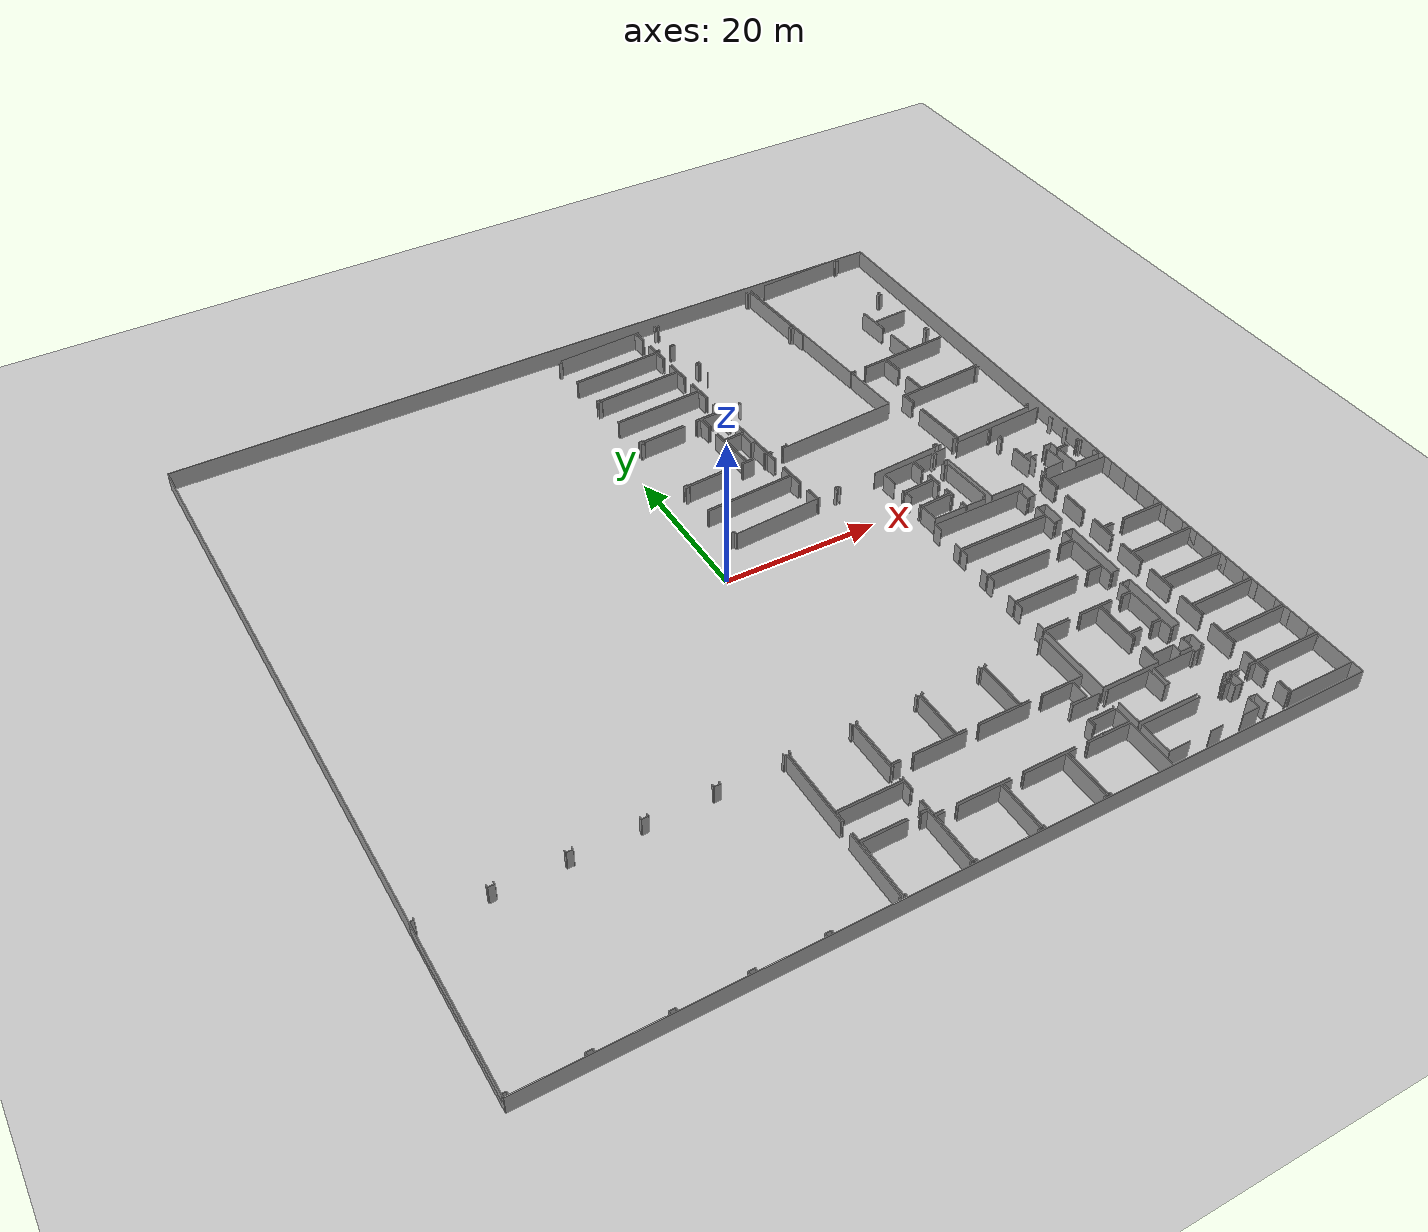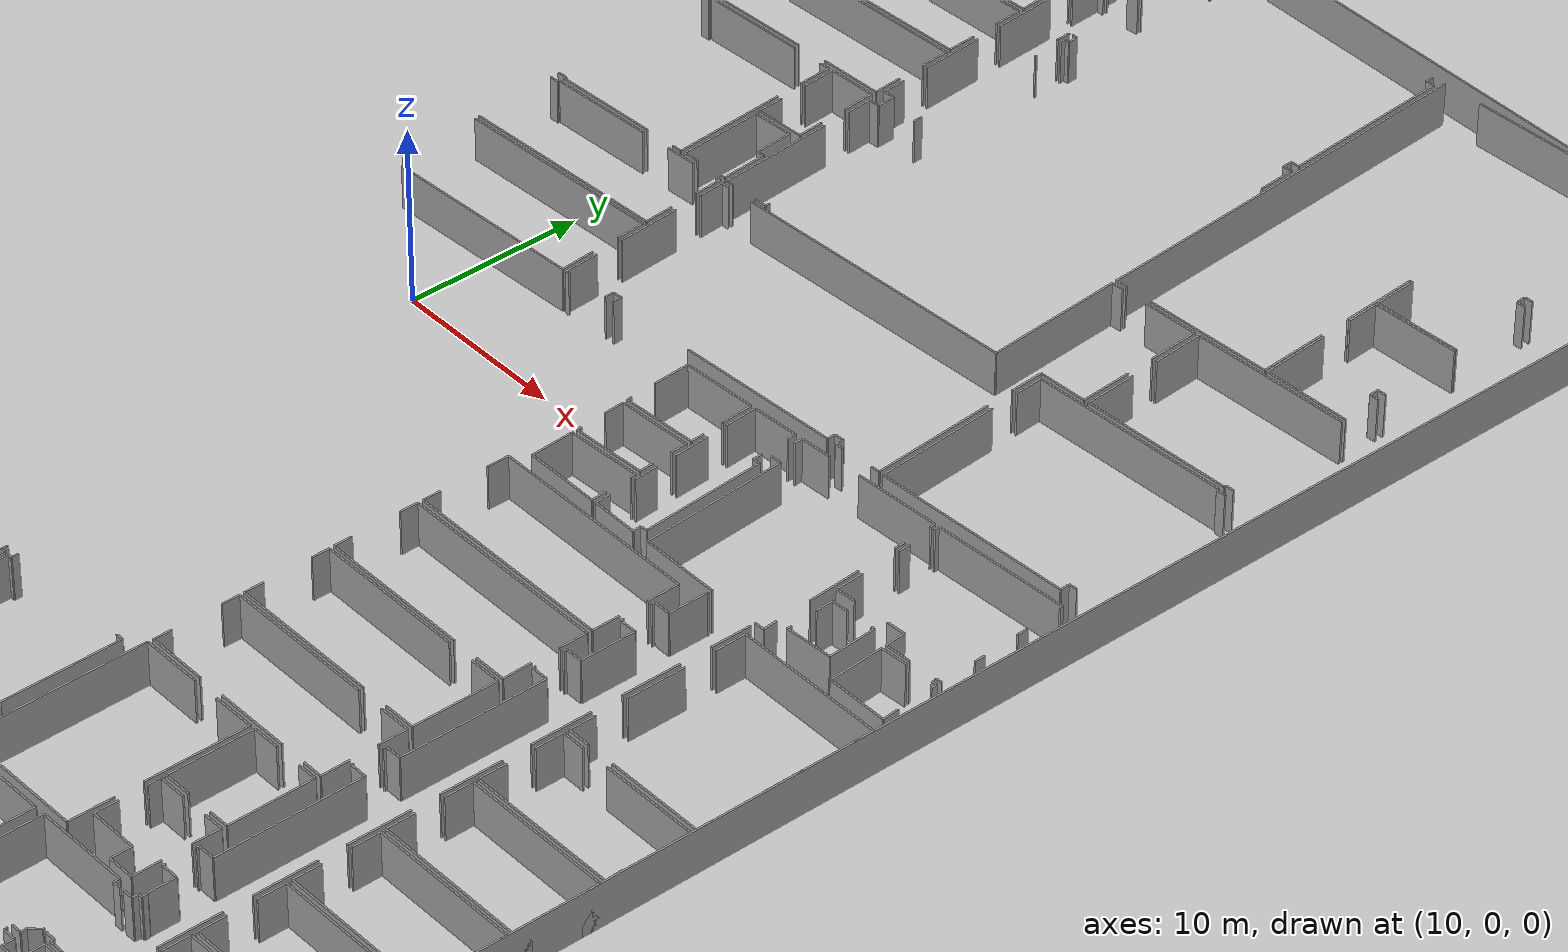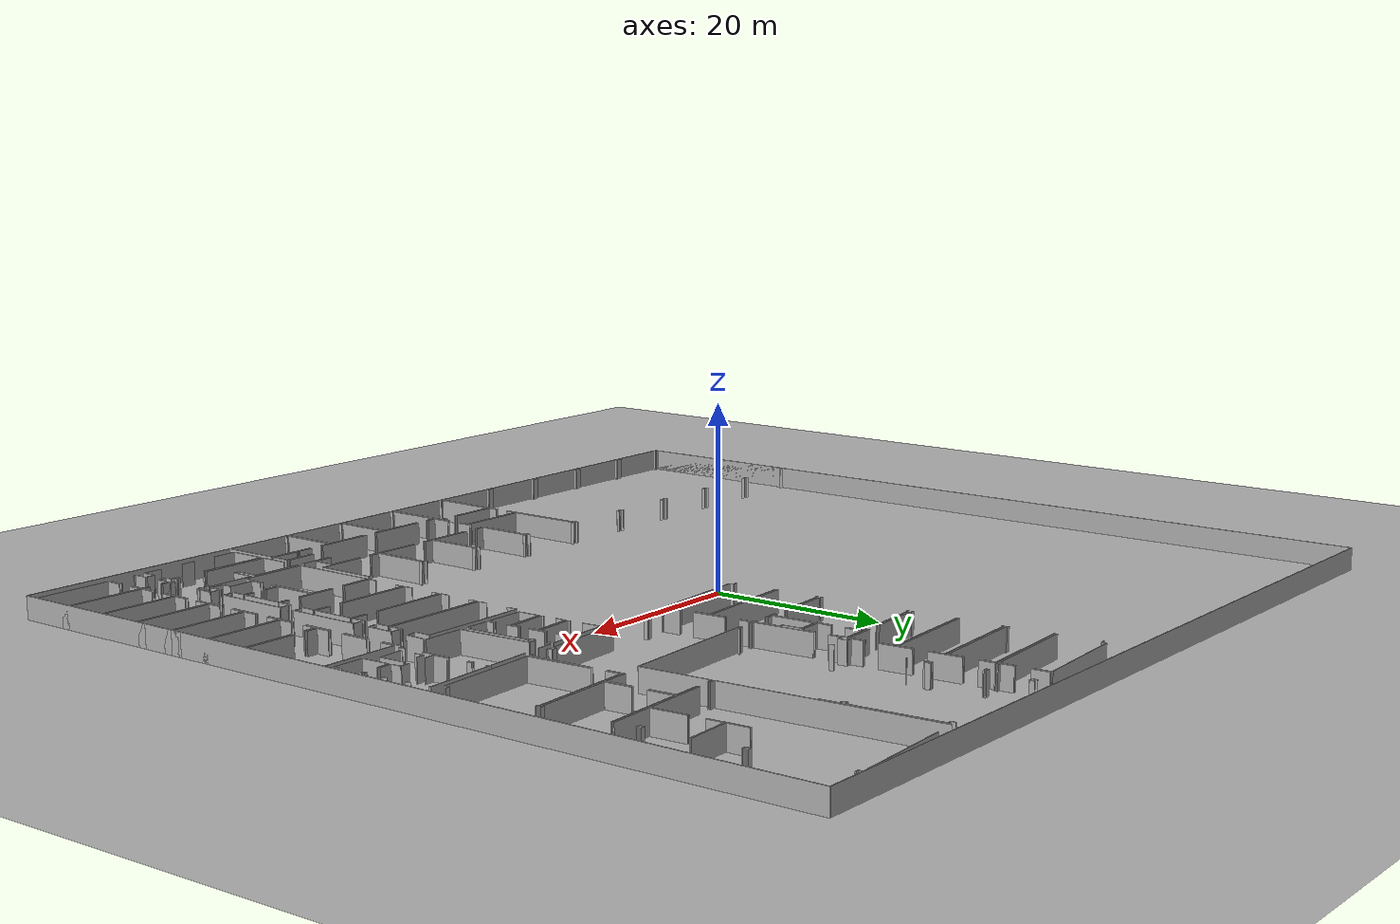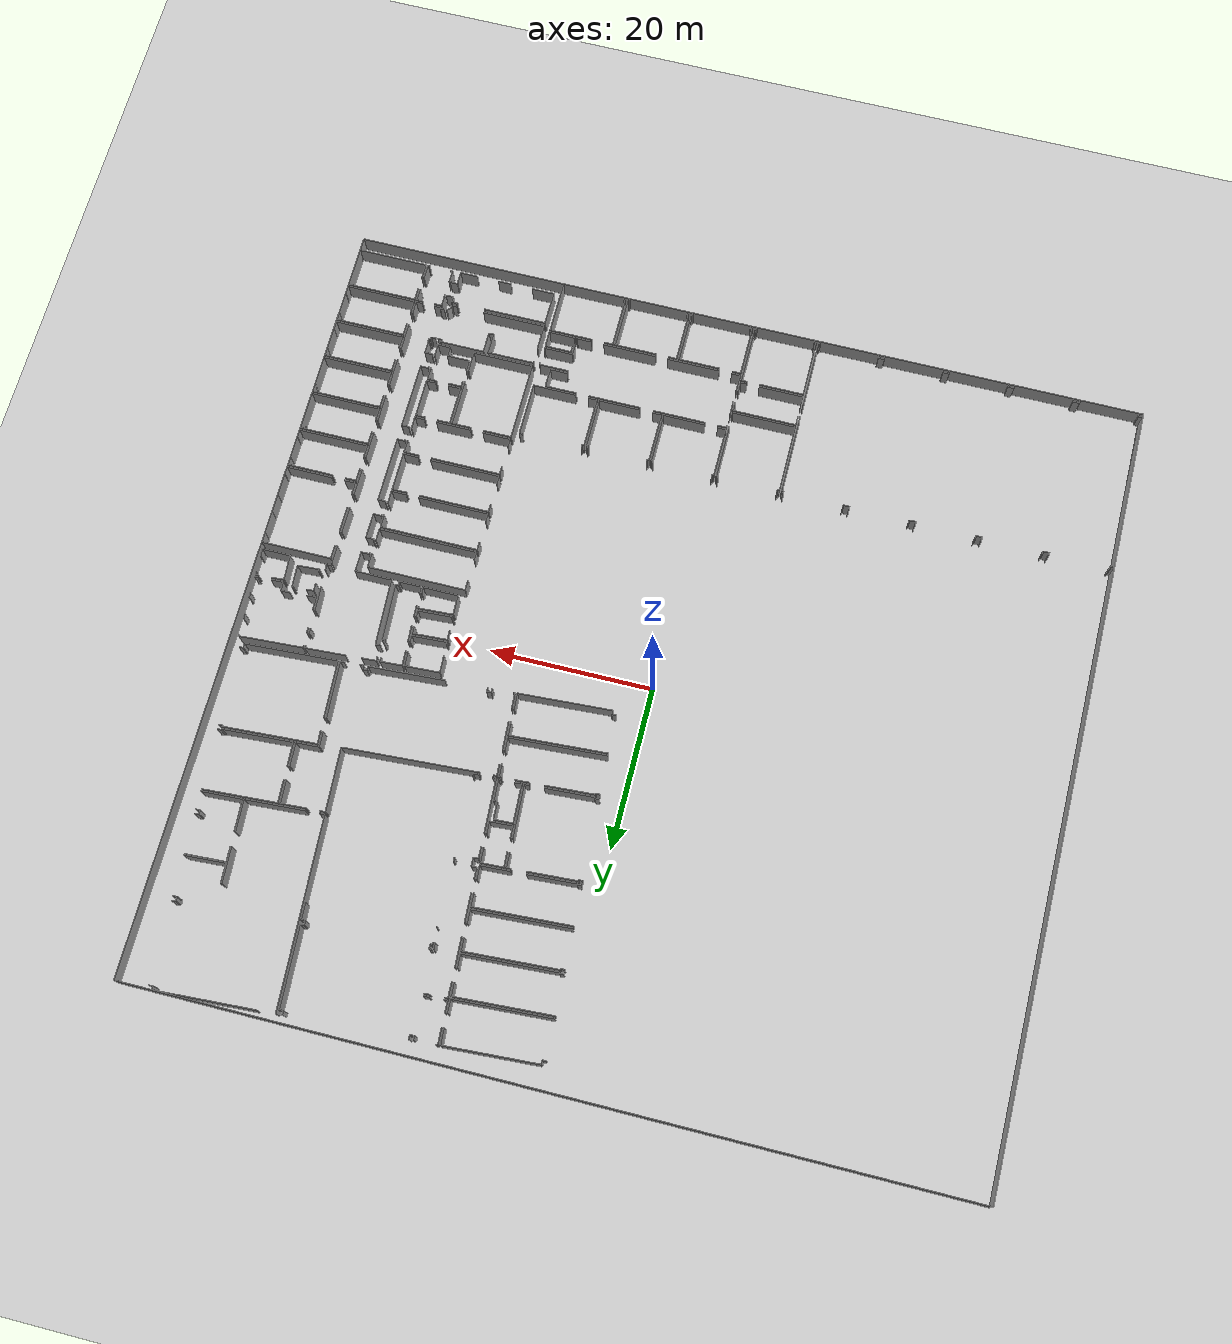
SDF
<sdf version="1.6">
  <world name="default">
    <light name="sun" type="directional">
      <cast_shadows>1</cast_shadows>
      <pose frame="">0 0 10 0 -0 0</pose>
      <diffuse>0.8 0.8 0.8 1</diffuse>
      <specular>0.1 0.1 0.1 1</specular>
      <attenuation>
        <range>1000</range>
        <constant>0.9</constant>
        <linear>0.01</linear>
        <quadratic>0.001</quadratic>
      </attenuation>
      <direction>-0.5 0.5 -1</direction>
    </light>
    <model name="ground_plane">
      <static>1</static>
      <link name="link">
        <collision name="collision">
          <geometry>
            <plane>
              <normal>0 0 1</normal>
              <size>100 100</size>
            </plane>
          </geometry>
          <surface>
            <friction>
              <ode>
                <mu>100</mu>
                <mu2>50</mu2>
              </ode>
              <torsional>
                <ode />
              </torsional>
            </friction>
            <contact>
              <ode />
            </contact>
            <bounce />
          </surface>
          <max_contacts>10</max_contacts>
        </collision>
        <visual name="visual">
          <cast_shadows>0</cast_shadows>
          <geometry>
            <plane>
              <normal>0 0 1</normal>
              <size>100 100</size>
            </plane>
          </geometry>
          <material>
            <script>
              <uri>file://media/materials/scripts/gazebo.material</uri>
              <name>Gazebo/Grey</name>
            </script>
          </material>
        </visual>
        <self_collide>0</self_collide>
        <kinematic>0</kinematic>
        <gravity>1</gravity>
      </link>
    </model>
    <gravity>0 0 -9.8</gravity>
    <magnetic_field>6e-06 2.3e-05 -4.2e-05</magnetic_field>
    <atmosphere type="adiabatic" />
    <physics default="0" name="default_physics" type="ode">
      <max_step_size>0.001</max_step_size>
      <real_time_factor>1</real_time_factor>
      <real_time_update_rate>1000</real_time_update_rate>
    </physics>
    <scene>
      <ambient>0.4 0.4 0.4 1</ambient>
      <background>0.7 0.7 0.7 1</background>
      <shadows>1</shadows>
    </scene>
    <spherical_coordinates>
      <surface_model>EARTH_WGS84</surface_model>
      <latitude_deg>0</latitude_deg>
      <longitude_deg>0</longitude_deg>
      <elevation>0</elevation>
      <heading_deg>0</heading_deg>
    </spherical_coordinates>
  <model name="50025632">
		<static>1</static>
		<link name="Wall_0">
			<collision name="Wall_0_Collision">
				<geometry>
					<box>
						<size>11.9319441098 0.1 2.5</size>
					</box>
				</geometry>
				<pose frame="">5.96597205492 0 1.25 0 0 0</pose>
			</collision>
			<visual name="Wall_0_Visual">
				<pose frame="">5.96597205492 0 1.25 0 0 0</pose>
				<geometry>
					<box>
						<size>11.9319441098 0.1 2.5</size>
					</box>
				</geometry>
				<material>
					<script>
						<uri>file://media/materials/scripts/gazebo.material</uri>
						<name>Gazebo/Grey</name>
					</script>
					<ambient>1 1 1 1</ambient>
				</material>
			</visual>
			<pose frame="">63.141229591 -7.22308801209 0 0 0 -3.0817129507</pose>
		</link>
		<link name="Wall_1">
			<collision name="Wall_1_Collision">
				<geometry>
					<box>
						<size>0.485071288327 0.1 2.5</size>
					</box>
				</geometry>
				<pose frame="">0.242535644164 0 1.25 0 0 0</pose>
			</collision>
			<visual name="Wall_1_Visual">
				<pose frame="">0.242535644164 0 1.25 0 0 0</pose>
				<geometry>
					<box>
						<size>0.485071288327 0.1 2.5</size>
					</box>
				</geometry>
				<material>
					<script>
						<uri>file://media/materials/scripts/gazebo.material</uri>
						<name>Gazebo/Grey</name>
					</script>
					<ambient>1 1 1 1</ambient>
				</material>
			</visual>
			<pose frame="">50.9575974649 -3.2139940432 0 0 0 0.0518674391414</pose>
		</link>
		<link name="Wall_2">
			<collision name="Wall_2_Collision">
				<geometry>
					<box>
						<size>0.484582056046 0.1 2.5</size>
					</box>
				</geometry>
				<pose frame="">0.242291028023 0 1.25 0 0 0</pose>
			</collision>
			<visual name="Wall_2_Visual">
				<pose frame="">0.242291028023 0 1.25 0 0 0</pose>
				<geometry>
					<box>
						<size>0.484582056046 0.1 2.5</size>
					</box>
				</geometry>
				<material>
					<script>
						<uri>file://media/materials/scripts/gazebo.material</uri>
						<name>Gazebo/Grey</name>
					</script>
					<ambient>1 1 1 1</ambient>
				</material>
			</visual>
			<pose frame="">51.4420164225 -3.18884591692 0 0 0 1.60540091813</pose>
		</link>
		<link name="Wall_3">
			<collision name="Wall_3_Collision">
				<geometry>
					<box>
						<size>11.4140309421 0.1 2.5</size>
					</box>
				</geometry>
				<pose frame="">5.70701547103 0 1.25 0 0 0</pose>
			</collision>
			<visual name="Wall_3_Visual">
				<pose frame="">5.70701547103 0 1.25 0 0 0</pose>
				<geometry>
					<box>
						<size>11.4140309421 0.1 2.5</size>
					</box>
				</geometry>
				<material>
					<script>
						<uri>file://media/materials/scripts/gazebo.material</uri>
						<name>Gazebo/Grey</name>
					</script>
					<ambient>1 1 1 1</ambient>
				</material>
			</visual>
			<pose frame="">51.425251005 -2.70455397004 0 0 0 0.0610940113321</pose>
		</link>
		<link name="Wall_4">
			<collision name="Wall_4_Collision">
				<geometry>
					<box>
						<size>1.96252891204 0.1 2.5</size>
					</box>
				</geometry>
				<pose frame="">0.981264456021 0 1.25 0 0 0</pose>
			</collision>
			<visual name="Wall_4_Visual">
				<pose frame="">0.981264456021 0 1.25 0 0 0</pose>
				<geometry>
					<box>
						<size>1.96252891204 0.1 2.5</size>
					</box>
				</geometry>
				<material>
					<script>
						<uri>file://media/materials/scripts/gazebo.material</uri>
						<name>Gazebo/Grey</name>
					</script>
					<ambient>1 1 1 1</ambient>
				</material>
			</visual>
			<pose frame="">62.8179872608 -2.00765874755 0 0 0 -1.49993566396</pose>
		</link>
		<link name="Wall_5">
			<collision name="Wall_5_Collision">
				<geometry>
					<box>
						<size>1.64788721188 0.1 2.5</size>
					</box>
				</geometry>
				<pose frame="">0.823943605938 0 1.25 0 0 0</pose>
			</collision>
			<visual name="Wall_5_Visual">
				<pose frame="">0.823943605938 0 1.25 0 0 0</pose>
				<geometry>
					<box>
						<size>1.64788721188 0.1 2.5</size>
					</box>
				</geometry>
				<material>
					<script>
						<uri>file://media/materials/scripts/gazebo.material</uri>
						<name>Gazebo/Grey</name>
					</script>
					<ambient>1 1 1 1</ambient>
				</material>
			</visual>
			<pose frame="">63.0584185893 -5.57728285927 0 0 0 -1.52052231826</pose>
		</link>
		<link name="Wall_6">
			<collision name="Wall_6_Collision">
				<geometry>
					<box>
						<size>0.537846532029 0.1 2.5</size>
					</box>
				</geometry>
				<pose frame="">0.268923266014 0 1.25 0 0 0</pose>
			</collision>
			<visual name="Wall_6_Visual">
				<pose frame="">0.268923266014 0 1.25 0 0 0</pose>
				<geometry>
					<box>
						<size>0.537846532029 0.1 2.5</size>
					</box>
				</geometry>
				<material>
					<script>
						<uri>file://media/materials/scripts/gazebo.material</uri>
						<name>Gazebo/Grey</name>
					</script>
					<ambient>1 1 1 1</ambient>
				</material>
			</visual>
			<pose frame="">65.8941873535 -2.32657001149 0 0 0 1.61118841254</pose>
		</link>
		<link name="Wall_7">
			<collision name="Wall_7_Collision">
				<geometry>
					<box>
						<size>0.226241075941 0.1 2.5</size>
					</box>
				</geometry>
				<pose frame="">0.113120537971 0 1.25 0 0 0</pose>
			</collision>
			<visual name="Wall_7_Visual">
				<pose frame="">0.113120537971 0 1.25 0 0 0</pose>
				<geometry>
					<box>
						<size>0.226241075941 0.1 2.5</size>
					</box>
				</geometry>
				<material>
					<script>
						<uri>file://media/materials/scripts/gazebo.material</uri>
						<name>Gazebo/Grey</name>
					</script>
					<ambient>1 1 1 1</ambient>
				</material>
			</visual>
			<pose frame="">63.3308566239 -1.96345901046 0 0 0 -3.04516394172</pose>
		</link>
		<link name="Wall_8">
			<collision name="Wall_8_Collision">
				<geometry>
					<box>
						<size>1.96459832486 0.1 2.5</size>
					</box>
				</geometry>
				<pose frame="">0.982299162432 0 1.25 0 0 0</pose>
			</collision>
			<visual name="Wall_8_Visual">
				<pose frame="">0.982299162432 0 1.25 0 0 0</pose>
				<geometry>
					<box>
						<size>1.96459832486 0.1 2.5</size>
					</box>
				</geometry>
				<material>
					<script>
						<uri>file://media/materials/scripts/gazebo.material</uri>
						<name>Gazebo/Grey</name>
					</script>
					<ambient>1 1 1 1</ambient>
				</material>
			</visual>
			<pose frame="">63.1056665841 -1.98524135216 0 0 0 -1.5079153649</pose>
		</link>
		<link name="Wall_9">
			<collision name="Wall_9_Collision">
				<geometry>
					<box>
						<size>1.43350711796 0.1 2.5</size>
					</box>
				</geometry>
				<pose frame="">0.716753558979 0 1.25 0 0 0</pose>
			</collision>
			<visual name="Wall_9_Visual">
				<pose frame="">0.716753558979 0 1.25 0 0 0</pose>
				<geometry>
					<box>
						<size>1.43350711796 0.1 2.5</size>
					</box>
				</geometry>
				<material>
					<script>
						<uri>file://media/materials/scripts/gazebo.material</uri>
						<name>Gazebo/Grey</name>
					</script>
					<ambient>1 1 1 1</ambient>
				</material>
			</visual>
			<pose frame="">63.3073596373 -5.54146583094 0 0 0 -1.51051086458</pose>
		</link>
		<link name="Wall_10">
			<collision name="Wall_10_Collision">
				<geometry>
					<box>
						<size>0.461447703476 0.1 2.5</size>
					</box>
				</geometry>
				<pose frame="">0.230723851738 0 1.25 0 0 0</pose>
			</collision>
			<visual name="Wall_10_Visual">
				<pose frame="">0.230723851738 0 1.25 0 0 0</pose>
				<geometry>
					<box>
						<size>0.461447703476 0.1 2.5</size>
					</box>
				</geometry>
				<material>
					<script>
						<uri>file://media/materials/scripts/gazebo.material</uri>
						<name>Gazebo/Grey</name>
					</script>
					<ambient>1 1 1 1</ambient>
				</material>
			</visual>
			<pose frame="">63.3937269396 -6.97236881378 0 0 0 0.041573827738</pose>
		</link>
		<link name="Wall_11">
			<collision name="Wall_11_Collision">
				<geometry>
					<box>
						<size>0.696910527662 0.1 2.5</size>
					</box>
				</geometry>
				<pose frame="">0.348455263831 0 1.25 0 0 0</pose>
			</collision>
			<visual name="Wall_11_Visual">
				<pose frame="">0.348455263831 0 1.25 0 0 0</pose>
				<geometry>
					<box>
						<size>0.696910527662 0.1 2.5</size>
					</box>
				</geometry>
				<material>
					<script>
						<uri>file://media/materials/scripts/gazebo.material</uri>
						<name>Gazebo/Grey</name>
					</script>
					<ambient>1 1 1 1</ambient>
				</material>
			</visual>
			<pose frame="">65.4720036579 -6.83837248439 0 0 0 0.066204474528</pose>
		</link>
		<link name="Wall_12">
			<collision name="Wall_12_Collision">
				<geometry>
					<box>
						<size>0.73059117325 0.1 2.5</size>
					</box>
				</geometry>
				<pose frame="">0.365295586625 0 1.25 0 0 0</pose>
			</collision>
			<visual name="Wall_12_Visual">
				<pose frame="">0.365295586625 0 1.25 0 0 0</pose>
				<geometry>
					<box>
						<size>0.73059117325 0.1 2.5</size>
					</box>
				</geometry>
				<material>
					<script>
						<uri>file://media/materials/scripts/gazebo.material</uri>
						<name>Gazebo/Grey</name>
					</script>
					<ambient>1 1 1 1</ambient>
				</material>
			</visual>
			<pose frame="">67.7467659891 -32.8350575041 0 0 0 -3.09515894658</pose>
		</link>
		<link name="Wall_13">
			<collision name="Wall_13_Collision">
				<geometry>
					<box>
						<size>0.443212248809 0.1 2.5</size>
					</box>
				</geometry>
				<pose frame="">0.221606124404 0 1.25 0 0 0</pose>
			</collision>
			<visual name="Wall_13_Visual">
				<pose frame="">0.221606124404 0 1.25 0 0 0</pose>
				<geometry>
					<box>
						<size>0.443212248809 0.1 2.5</size>
					</box>
				</geometry>
				<material>
					<script>
						<uri>file://media/materials/scripts/gazebo.material</uri>
						<name>Gazebo/Grey</name>
					</script>
					<ambient>1 1 1 1</ambient>
				</material>
			</visual>
			<pose frame="">65.4468555316 -32.9524154267 0 0 0 -3.08510859811</pose>
		</link>
		<link name="Wall_14">
			<collision name="Wall_14_Collision">
				<geometry>
					<box>
						<size>6.64681639379 0.1 2.5</size>
					</box>
				</geometry>
				<pose frame="">3.3234081969 0 1.25 0 0 0</pose>
			</collision>
			<visual name="Wall_14_Visual">
				<pose frame="">3.3234081969 0 1.25 0 0 0</pose>
				<geometry>
					<box>
						<size>6.64681639379 0.1 2.5</size>
					</box>
				</geometry>
				<material>
					<script>
						<uri>file://media/materials/scripts/gazebo.material</uri>
						<name>Gazebo/Grey</name>
					</script>
					<ambient>1 1 1 1</ambient>
				</material>
			</visual>
			<pose frame="">65.0043501178 -32.9774365423 0 0 0 1.63253691382</pose>
		</link>
		<link name="Wall_15">
			<collision name="Wall_15_Collision">
				<geometry>
					<box>
						<size>1.42461677082 0.1 2.5</size>
					</box>
				</geometry>
				<pose frame="">0.712308385411 0 1.25 0 0 0</pose>
			</collision>
			<visual name="Wall_15_Visual">
				<pose frame="">0.712308385411 0 1.25 0 0 0</pose>
				<geometry>
					<box>
						<size>1.42461677082 0.1 2.5</size>
					</box>
				</geometry>
				<material>
					<script>
						<uri>file://media/materials/scripts/gazebo.material</uri>
						<name>Gazebo/Grey</name>
					</script>
					<ambient>1 1 1 1</ambient>
				</material>
			</visual>
			<pose frame="">64.50786514 -24.7395200264 0 0 0 1.6382481288</pose>
		</link>
		<link name="Wall_16">
			<collision name="Wall_16_Collision">
				<geometry>
					<box>
						<size>0.625316124992 0.1 2.5</size>
					</box>
				</geometry>
				<pose frame="">0.312658062496 0 1.25 0 0 0</pose>
			</collision>
			<visual name="Wall_16_Visual">
				<pose frame="">0.312658062496 0 1.25 0 0 0</pose>
				<geometry>
					<box>
						<size>0.625316124992 0.1 2.5</size>
					</box>
				</geometry>
				<material>
					<script>
						<uri>file://media/materials/scripts/gazebo.material</uri>
						<name>Gazebo/Grey</name>
					</script>
					<ambient>1 1 1 1</ambient>
				</material>
			</visual>
			<pose frame="">64.4118450215 -23.318142849 0 0 0 0.0615825944472</pose>
		</link>
		<link name="Wall_17">
			<collision name="Wall_17_Collision">
				<geometry>
					<box>
						<size>1.02863788448 0.1 2.5</size>
					</box>
				</geometry>
				<pose frame="">0.51431894224 0 1.25 0 0 0</pose>
			</collision>
			<visual name="Wall_17_Visual">
				<pose frame="">0.51431894224 0 1.25 0 0 0</pose>
				<geometry>
					<box>
						<size>1.02863788448 0.1 2.5</size>
					</box>
				</geometry>
				<material>
					<script>
						<uri>file://media/materials/scripts/gazebo.material</uri>
						<name>Gazebo/Grey</name>
					</script>
					<ambient>1 1 1 1</ambient>
				</material>
			</visual>
			<pose frame="">65.0359757918 -23.2796585951 0 0 0 1.61748671999</pose>
		</link>
		<link name="Wall_18">
			<collision name="Wall_18_Collision">
				<geometry>
					<box>
						<size>0.644578685827 0.1 2.5</size>
					</box>
				</geometry>
				<pose frame="">0.322289342913 0 1.25 0 0 0</pose>
			</collision>
			<visual name="Wall_18_Visual">
				<pose frame="">0.322289342913 0 1.25 0 0 0</pose>
				<geometry>
					<box>
						<size>0.644578685827 0.1 2.5</size>
					</box>
				</geometry>
				<material>
					<script>
						<uri>file://media/materials/scripts/gazebo.material</uri>
						<name>Gazebo/Grey</name>
					</script>
					<ambient>1 1 1 1</ambient>
				</material>
			</visual>
			<pose frame="">64.9879657325 -22.2521417186 0 0 0 -3.08205001256</pose>
		</link>
		<link name="Wall_19">
			<collision name="Wall_19_Collision">
				<geometry>
					<box>
						<size>1.33709269581 0.1 2.5</size>
					</box>
				</geometry>
				<pose frame="">0.668546347903 0 1.25 0 0 0</pose>
			</collision>
			<visual name="Wall_19_Visual">
				<pose frame="">0.668546347903 0 1.25 0 0 0</pose>
				<geometry>
					<box>
						<size>1.33709269581 0.1 2.5</size>
					</box>
				</geometry>
				<material>
					<script>
						<uri>file://media/materials/scripts/gazebo.material</uri>
						<name>Gazebo/Grey</name>
					</script>
					<ambient>1 1 1 1</ambient>
				</material>
			</visual>
			<pose frame="">64.34452933 -22.2904989617 0 0 0 1.62829709509</pose>
		</link>
		<link name="Wall_20">
			<collision name="Wall_20_Collision">
				<geometry>
					<box>
						<size>3.53377127692 0.1 2.5</size>
					</box>
				</geometry>
				<pose frame="">1.76688563846 0 1.25 0 0 0</pose>
			</collision>
			<visual name="Wall_20_Visual">
				<pose frame="">1.76688563846 0 1.25 0 0 0</pose>
				<geometry>
					<box>
						<size>3.53377127692 0.1 2.5</size>
					</box>
				</geometry>
				<material>
					<script>
						<uri>file://media/materials/scripts/gazebo.material</uri>
						<name>Gazebo/Grey</name>
					</script>
					<ambient>1 1 1 1</ambient>
				</material>
			</visual>
			<pose frame="">64.1672223386 -19.3514704668 0 0 0 1.6317197228</pose>
		</link>
		<link name="Wall_21">
			<collision name="Wall_21_Collision">
				<geometry>
					<box>
						<size>3.55478971893 0.1 2.5</size>
					</box>
				</geometry>
				<pose frame="">1.77739485946 0 1.25 0 0 0</pose>
			</collision>
			<visual name="Wall_21_Visual">
				<pose frame="">1.77739485946 0 1.25 0 0 0</pose>
				<geometry>
					<box>
						<size>3.55478971893 0.1 2.5</size>
					</box>
				</geometry>
				<material>
					<script>
						<uri>file://media/materials/scripts/gazebo.material</uri>
						<name>Gazebo/Grey</name>
					</script>
					<ambient>1 1 1 1</ambient>
				</material>
			</visual>
			<pose frame="">63.8410587615 -14.2328106841 0 0 0 1.6318244008</pose>
		</link>
		<link name="Wall_22">
			<collision name="Wall_22_Collision">
				<geometry>
					<box>
						<size>1.89873595495 0.1 2.5</size>
					</box>
				</geometry>
				<pose frame="">0.949367977477 0 1.25 0 0 0</pose>
			</collision>
			<visual name="Wall_22_Visual">
				<pose frame="">0.949367977477 0 1.25 0 0 0</pose>
				<geometry>
					<box>
						<size>1.89873595495 0.1 2.5</size>
					</box>
				</geometry>
				<material>
					<script>
						<uri>file://media/materials/scripts/gazebo.material</uri>
						<name>Gazebo/Grey</name>
					</script>
					<ambient>1 1 1 1</ambient>
				</material>
			</visual>
			<pose frame="">63.5344548382 -9.10983253634 0 0 0 1.62795343299</pose>
		</link>
		<link name="Wall_23">
			<collision name="Wall_23_Collision">
				<geometry>
					<box>
						<size>0.42594950112 0.1 2.5</size>
					</box>
				</geometry>
				<pose frame="">0.21297475056 0 1.25 0 0 0</pose>
			</collision>
			<visual name="Wall_23_Visual">
				<pose frame="">0.21297475056 0 1.25 0 0 0</pose>
				<geometry>
					<box>
						<size>0.42594950112 0.1 2.5</size>
					</box>
				</geometry>
				<material>
					<script>
						<uri>file://media/materials/scripts/gazebo.material</uri>
						<name>Gazebo/Grey</name>
					</script>
					<ambient>1 1 1 1</ambient>
				</material>
			</visual>
			<pose frame="">63.4259876673 -7.21419726038 0 0 0 0.0196813235851</pose>
		</link>
		<link name="Wall_24">
			<collision name="Wall_24_Collision">
				<geometry>
					<box>
						<size>0.720673750226 0.1 2.5</size>
					</box>
				</geometry>
				<pose frame="">0.360336875113 0 1.25 0 0 0</pose>
			</collision>
			<visual name="Wall_24_Visual">
				<pose frame="">0.360336875113 0 1.25 0 0 0</pose>
				<geometry>
					<box>
						<size>0.720673750226 0.1 2.5</size>
					</box>
				</geometry>
				<material>
					<script>
						<uri>file://media/materials/scripts/gazebo.material</uri>
						<name>Gazebo/Grey</name>
					</script>
					<ambient>1 1 1 1</ambient>
				</material>
			</visual>
			<pose frame="">65.4657801317 -7.0976014022 0 0 0 0.0705540746717</pose>
		</link>
		<link name="Wall_25">
			<collision name="Wall_25_Collision">
				<geometry>
					<box>
						<size>0.823300939671 0.1 2.5</size>
					</box>
				</geometry>
				<pose frame="">0.411650469836 0 1.25 0 0 0</pose>
			</collision>
			<visual name="Wall_25_Visual">
				<pose frame="">0.411650469836 0 1.25 0 0 0</pose>
				<geometry>
					<box>
						<size>0.823300939671 0.1 2.5</size>
					</box>
				</geometry>
				<material>
					<script>
						<uri>file://media/materials/scripts/gazebo.material</uri>
						<name>Gazebo/Grey</name>
					</script>
					<ambient>1 1 1 1</ambient>
				</material>
			</visual>
			<pose frame="">66.5150158446 -12.0336197425 0 0 0 -1.53098411828</pose>
		</link>
		<link name="Wall_26">
			<collision name="Wall_26_Collision">
				<geometry>
					<box>
						<size>0.525538038728 0.1 2.5</size>
					</box>
				</geometry>
				<pose frame="">0.262769019364 0 1.25 0 0 0</pose>
			</collision>
			<visual name="Wall_26_Visual">
				<pose frame="">0.262769019364 0 1.25 0 0 0</pose>
				<geometry>
					<box>
						<size>0.525538038728 0.1 2.5</size>
					</box>
				</geometry>
				<material>
					<script>
						<uri>file://media/materials/scripts/gazebo.material</uri>
						<name>Gazebo/Grey</name>
					</script>
					<ambient>1 1 1 1</ambient>
				</material>
			</visual>
			<pose frame="">67.0993922536 -22.2903719509 0 0 0 -1.49871401541</pose>
		</link>
		<link name="Wall_27">
			<collision name="Wall_27_Collision">
				<geometry>
					<box>
						<size>0.293706532019 0.1 2.5</size>
					</box>
				</geometry>
				<pose frame="">0.14685326601 0 1.25 0 0 0</pose>
			</collision>
			<visual name="Wall_27_Visual">
				<pose frame="">0.14685326601 0 1.25 0 0 0</pose>
				<geometry>
					<box>
						<size>0.293706532019 0.1 2.5</size>
					</box>
				</geometry>
				<material>
					<script>
						<uri>file://media/materials/scripts/gazebo.material</uri>
						<name>Gazebo/Grey</name>
					</script>
					<ambient>1 1 1 1</ambient>
				</material>
			</visual>
			<pose frame="">67.7363511085 -32.5415356868 0 0 0 -1.53532873132</pose>
		</link>
		<link name="Wall_28">
			<collision name="Wall_28_Collision">
				<geometry>
					<box>
						<size>11.4503002531 0.1 2.5</size>
					</box>
				</geometry>
				<pose frame="">5.72515012656 0 1.25 0 0 0</pose>
			</collision>
			<visual name="Wall_28_Visual">
				<pose frame="">5.72515012656 0 1.25 0 0 0</pose>
				<geometry>
					<box>
						<size>11.4503002531 0.1 2.5</size>
					</box>
				</geometry>
				<material>
					<script>
						<uri>file://media/materials/scripts/gazebo.material</uri>
						<name>Gazebo/Grey</name>
					</script>
					<ambient>1 1 1 1</ambient>
				</material>
			</visual>
			<pose frame="">63.4724735976 -12.358640223 0 0 0 -3.08271372285</pose>
		</link>
		<link name="Wall_29">
			<collision name="Wall_29_Collision">
				<geometry>
					<box>
						<size>0.119759475574 0.1 2.5</size>
					</box>
				</geometry>
				<pose frame="">0.0598797377871 0 1.25 0 0 0</pose>
			</collision>
			<visual name="Wall_29_Visual">
				<pose frame="">0.0598797377871 0 1.25 0 0 0</pose>
				<geometry>
					<box>
						<size>0.119759475574 0.1 2.5</size>
					</box>
				</geometry>
				<material>
					<script>
						<uri>file://media/materials/scripts/gazebo.material</uri>
						<name>Gazebo/Grey</name>
					</script>
					<ambient>1 1 1 1</ambient>
				</material>
			</visual>
			<pose frame="">52.0420151524 -13.0324321921 0 0 0 1.64935770696</pose>
		</link>
		<link name="Wall_30">
			<collision name="Wall_30_Collision">
				<geometry>
					<box>
						<size>0.492915962791 0.1 2.5</size>
					</box>
				</geometry>
				<pose frame="">0.246457981396 0 1.25 0 0 0</pose>
			</collision>
			<visual name="Wall_30_Visual">
				<pose frame="">0.246457981396 0 1.25 0 0 0</pose>
				<geometry>
					<box>
						<size>0.492915962791 0.1 2.5</size>
					</box>
				</geometry>
				<material>
					<script>
						<uri>file://media/materials/scripts/gazebo.material</uri>
						<name>Gazebo/Grey</name>
					</script>
					<ambient>1 1 1 1</ambient>
				</material>
			</visual>
			<pose frame="">52.0326163577 -12.9130420977 0 0 0 -3.10293219433</pose>
		</link>
		<link name="Wall_31">
			<collision name="Wall_31_Collision">
				<geometry>
					<box>
						<size>11.9212283438 0.1 2.5</size>
					</box>
				</geometry>
				<pose frame="">5.96061417188 0 1.25 0 0 0</pose>
			</collision>
			<visual name="Wall_31_Visual">
				<pose frame="">5.96061417188 0 1.25 0 0 0</pose>
				<geometry>
					<box>
						<size>11.9212283438 0.1 2.5</size>
					</box>
				</geometry>
				<material>
					<script>
						<uri>file://media/materials/scripts/gazebo.material</uri>
						<name>Gazebo/Grey</name>
					</script>
					<ambient>1 1 1 1</ambient>
				</material>
			</visual>
			<pose frame="">51.2415934767 -8.22469469794 0 0 0 0.0617695069085</pose>
		</link>
		<link name="Wall_32">
			<collision name="Wall_32_Collision">
				<geometry>
					<box>
						<size>1.60837630227 0.1 2.5</size>
					</box>
				</geometry>
				<pose frame="">0.804188151137 0 1.25 0 0 0</pose>
			</collision>
			<visual name="Wall_32_Visual">
				<pose frame="">0.804188151137 0 1.25 0 0 0</pose>
				<geometry>
					<box>
						<size>1.60837630227 0.1 2.5</size>
					</box>
				</geometry>
				<material>
					<script>
						<uri>file://media/materials/scripts/gazebo.material</uri>
						<name>Gazebo/Grey</name>
					</script>
					<ambient>1 1 1 1</ambient>
				</material>
			</visual>
			<pose frame="">63.1400864943 -7.48879447757 0 0 0 -1.49610184806</pose>
		</link>
		<link name="Wall_33">
			<collision name="Wall_33_Collision">
				<geometry>
					<box>
						<size>1.66402897746 0.1 2.5</size>
					</box>
				</geometry>
				<pose frame="">0.832014488731 0 1.25 0 0 0</pose>
			</collision>
			<visual name="Wall_33_Visual">
				<pose frame="">0.832014488731 0 1.25 0 0 0</pose>
				<geometry>
					<box>
						<size>1.66402897746 0.1 2.5</size>
					</box>
				</geometry>
				<material>
					<script>
						<uri>file://media/materials/scripts/gazebo.material</uri>
						<name>Gazebo/Grey</name>
					</script>
					<ambient>1 1 1 1</ambient>
				</material>
			</visual>
			<pose frame="">63.3553696965 -10.6987368782 0 0 0 -1.50036439472</pose>
		</link>
		<link name="Wall_34">
			<collision name="Wall_34_Collision">
				<geometry>
					<box>
						<size>11.8869431422 0.1 2.5</size>
					</box>
				</geometry>
				<pose frame="">5.94347157111 0 1.25 0 0 0</pose>
			</collision>
			<visual name="Wall_34_Visual">
				<pose frame="">5.94347157111 0 1.25 0 0 0</pose>
				<geometry>
					<box>
						<size>11.8869431422 0.1 2.5</size>
					</box>
				</geometry>
				<material>
					<script>
						<uri>file://media/materials/scripts/gazebo.material</uri>
						<name>Gazebo/Grey</name>
					</script>
					<ambient>1 1 1 1</ambient>
				</material>
			</visual>
			<pose frame="">63.7404662564 -17.4723465869 0 0 0 -3.08024425153</pose>
		</link>
		<link name="Wall_35">
			<collision name="Wall_35_Collision">
				<geometry>
					<box>
						<size>0.493086768847 0.1 2.5</size>
					</box>
				</geometry>
				<pose frame="">0.246543384424 0 1.25 0 0 0</pose>
			</collision>
			<visual name="Wall_35_Visual">
				<pose frame="">0.246543384424 0 1.25 0 0 0</pose>
				<geometry>
					<box>
						<size>0.493086768847 0.1 2.5</size>
					</box>
				</geometry>
				<material>
					<script>
						<uri>file://media/materials/scripts/gazebo.material</uri>
						<name>Gazebo/Grey</name>
					</script>
					<ambient>1 1 1 1</ambient>
				</material>
			</visual>
			<pose frame="">51.5672490109 -13.4692221227 0 0 0 0.034007502481</pose>
		</link>
		<link name="Wall_36">
			<collision name="Wall_36_Collision">
				<geometry>
					<box>
						<size>0.125232588415 0.1 2.5</size>
					</box>
				</geometry>
				<pose frame="">0.0626162942077 0 1.25 0 0 0</pose>
			</collision>
			<visual name="Wall_36_Visual">
				<pose frame="">0.0626162942077 0 1.25 0 0 0</pose>
				<geometry>
					<box>
						<size>0.125232588415 0.1 2.5</size>
					</box>
				</geometry>
				<material>
					<script>
						<uri>file://media/materials/scripts/gazebo.material</uri>
						<name>Gazebo/Grey</name>
					</script>
					<ambient>1 1 1 1</ambient>
				</material>
			</visual>
			<pose frame="">52.0600506773 -13.4524567052 0 0 0 1.57079632679</pose>
		</link>
		<link name="Wall_37">
			<collision name="Wall_37_Collision">
				<geometry>
					<box>
						<size>11.4309730152 0.1 2.5</size>
					</box>
				</geometry>
				<pose frame="">5.71548650758 0 1.25 0 0 0</pose>
			</collision>
			<visual name="Wall_37_Visual">
				<pose frame="">5.71548650758 0 1.25 0 0 0</pose>
				<geometry>
					<box>
						<size>11.4309730152 0.1 2.5</size>
					</box>
				</geometry>
				<material>
					<script>
						<uri>file://media/materials/scripts/gazebo.material</uri>
						<name>Gazebo/Grey</name>
					</script>
					<ambient>1 1 1 1</ambient>
				</material>
			</visual>
			<pose frame="">52.0600506773 -13.3272241168 0 0 0 0.06093767255</pose>
		</link>
		<link name="Wall_38">
			<collision name="Wall_38_Collision">
				<geometry>
					<box>
						<size>1.61235572108 0.1 2.5</size>
					</box>
				</geometry>
				<pose frame="">0.806177860539 0 1.25 0 0 0</pose>
			</collision>
			<visual name="Wall_38_Visual">
				<pose frame="">0.806177860539 0 1.25 0 0 0</pose>
				<geometry>
					<box>
						<size>1.61235572108 0.1 2.5</size>
					</box>
				</geometry>
				<material>
					<script>
						<uri>file://media/materials/scripts/gazebo.material</uri>
						<name>Gazebo/Grey</name>
					</script>
					<ambient>1 1 1 1</ambient>
				</material>
			</visual>
			<pose frame="">63.4698063721 -12.6310782577 0 0 0 -1.50599925977</pose>
		</link>
		<link name="Wall_39">
			<collision name="Wall_39_Collision">
				<geometry>
					<box>
						<size>1.63288331644 0.1 2.5</size>
					</box>
				</geometry>
				<pose frame="">0.81644165822 0 1.25 0 0 0</pose>
			</collision>
			<visual name="Wall_39_Visual">
				<pose frame="">0.81644165822 0 1.25 0 0 0</pose>
				<geometry>
					<box>
						<size>1.63288331644 0.1 2.5</size>
					</box>
				</geometry>
				<material>
					<script>
						<uri>file://media/materials/scripts/gazebo.material</uri>
						<name>Gazebo/Grey</name>
					</script>
					<ambient>1 1 1 1</ambient>
				</material>
			</visual>
			<pose frame="">63.672134479 -15.8408936476 0 0 0 -1.52893679143</pose>
		</link>
		<link name="Wall_40">
			<collision name="Wall_40_Collision">
				<geometry>
					<box>
						<size>3.62623420739 0.1 2.5</size>
					</box>
				</geometry>
				<pose frame="">1.8131171037 0 1.25 0 0 0</pose>
			</collision>
			<visual name="Wall_40_Visual">
				<pose frame="">1.8131171037 0 1.25 0 0 0</pose>
				<geometry>
					<box>
						<size>3.62623420739 0.1 2.5</size>
					</box>
				</geometry>
				<material>
					<script>
						<uri>file://media/materials/scripts/gazebo.material</uri>
						<name>Gazebo/Grey</name>
					</script>
					<ambient>1 1 1 1</ambient>
				</material>
			</visual>
			<pose frame="">64.0910158954 -22.6189487321 0 0 0 -3.09025772282</pose>
		</link>
		<link name="Wall_41">
			<collision name="Wall_41_Collision">
				<geometry>
					<box>
						<size>5.99057736799 0.1 2.5</size>
					</box>
				</geometry>
				<pose frame="">2.99528868399 0 1.25 0 0 0</pose>
			</collision>
			<visual name="Wall_41_Visual">
				<pose frame="">2.99528868399 0 1.25 0 0 0</pose>
				<geometry>
					<box>
						<size>5.99057736799 0.1 2.5</size>
					</box>
				</geometry>
				<material>
					<script>
						<uri>file://media/materials/scripts/gazebo.material</uri>
						<name>Gazebo/Grey</name>
					</script>
					<ambient>1 1 1 1</ambient>
				</material>
			</visual>
			<pose frame="">58.65038389 -22.9218693441 0 0 0 -3.08087593922</pose>
		</link>
		<link name="Wall_42">
			<collision name="Wall_42_Collision">
				<geometry>
					<box>
						<size>0.138521442697 0.1 2.5</size>
					</box>
				</geometry>
				<pose frame="">0.0692607213483 0 1.25 0 0 0</pose>
			</collision>
			<visual name="Wall_42_Visual">
				<pose frame="">0.0692607213483 0 1.25 0 0 0</pose>
				<geometry>
					<box>
						<size>0.138521442697 0.1 2.5</size>
					</box>
				</geometry>
				<material>
					<script>
						<uri>file://media/materials/scripts/gazebo.material</uri>
						<name>Gazebo/Grey</name>
					</script>
					<ambient>1 1 1 1</ambient>
				</material>
			</visual>
			<pose frame="">52.67084532 -23.2853740784 0 0 0 1.60472825213</pose>
		</link>
		<link name="Wall_43">
			<collision name="Wall_43_Collision">
				<geometry>
					<box>
						<size>0.498081336563 0.1 2.5</size>
					</box>
				</geometry>
				<pose frame="">0.249040668281 0 1.25 0 0 0</pose>
			</collision>
			<visual name="Wall_43_Visual">
				<pose frame="">0.249040668281 0 1.25 0 0 0</pose>
				<geometry>
					<box>
						<size>0.498081336563 0.1 2.5</size>
					</box>
				</geometry>
				<material>
					<script>
						<uri>file://media/materials/scripts/gazebo.material</uri>
						<name>Gazebo/Grey</name>
					</script>
					<ambient>1 1 1 1</ambient>
				</material>
			</visual>
			<pose frame="">52.6661459226 -23.1469323731 0 0 0 -3.0647620895</pose>
		</link>
		<link name="Wall_44">
			<collision name="Wall_44_Collision">
				<geometry>
					<box>
						<size>11.9307856605 0.1 2.5</size>
					</box>
				</geometry>
				<pose frame="">5.96539283023 0 1.25 0 0 0</pose>
			</collision>
			<visual name="Wall_44_Visual">
				<pose frame="">5.96539283023 0 1.25 0 0 0</pose>
				<geometry>
					<box>
						<size>11.9307856605 0.1 2.5</size>
					</box>
				</geometry>
				<material>
					<script>
						<uri>file://media/materials/scripts/gazebo.material</uri>
						<name>Gazebo/Grey</name>
					</script>
					<ambient>1 1 1 1</ambient>
				</material>
			</visual>
			<pose frame="">51.8860459652 -18.4623952955 0 0 0 0.0596828950325</pose>
		</link>
		<link name="Wall_45">
			<collision name="Wall_45_Collision">
				<geometry>
					<box>
						<size>1.62172917607 0.1 2.5</size>
					</box>
				</geometry>
				<pose frame="">0.810864588035 0 1.25 0 0 0</pose>
			</collision>
			<visual name="Wall_45_Visual">
				<pose frame="">0.810864588035 0 1.25 0 0 0</pose>
				<geometry>
					<box>
						<size>1.62172917607 0.1 2.5</size>
					</box>
				</geometry>
				<material>
					<script>
						<uri>file://media/materials/scripts/gazebo.material</uri>
						<name>Gazebo/Grey</name>
					</script>
					<ambient>1 1 1 1</ambient>
				</material>
			</visual>
			<pose frame="">63.795588917 -17.7507541263 0 0 0 -1.51704423354</pose>
		</link>
		<link name="Wall_46">
			<collision name="Wall_46_Collision">
				<geometry>
					<box>
						<size>1.64488212049 0.1 2.5</size>
					</box>
				</geometry>
				<pose frame="">0.822441060246 0 1.25 0 0 0</pose>
			</collision>
			<visual name="Wall_46_Visual">
				<pose frame="">0.822441060246 0 1.25 0 0 0</pose>
				<geometry>
					<box>
						<size>1.64488212049 0.1 2.5</size>
					</box>
				</geometry>
				<material>
					<script>
						<uri>file://media/materials/scripts/gazebo.material</uri>
						<name>Gazebo/Grey</name>
					</script>
					<ambient>1 1 1 1</ambient>
				</material>
			</visual>
			<pose frame="">63.9894073044 -20.9772079229 0 0 0 -1.50898440637</pose>
		</link>
		<link name="Wall_47">
			<collision name="Wall_47_Collision">
				<geometry>
					<box>
						<size>0.103261683401 0.1 2.5</size>
					</box>
				</geometry>
				<pose frame="">0.0516308417007 0 1.25 0 0 0</pose>
			</collision>
			<visual name="Wall_47_Visual">
				<pose frame="">0.0516308417007 0 1.25 0 0 0</pose>
				<geometry>
					<box>
						<size>0.103261683401 0.1 2.5</size>
					</box>
				</geometry>
				<material>
					<script>
						<uri>file://media/materials/scripts/gazebo.material</uri>
						<name>Gazebo/Grey</name>
					</script>
					<ambient>1 1 1 1</ambient>
				</material>
			</visual>
			<pose frame="">66.8992233293 -14.6555024227 0 0 0 1.56464634283</pose>
		</link>
		<link name="Wall_48">
			<collision name="Wall_48_Collision">
				<geometry>
					<box>
						<size>0.307517523586 0.1 2.5</size>
					</box>
				</geometry>
				<pose frame="">0.153758761793 0 1.25 0 0 0</pose>
			</collision>
			<visual name="Wall_48_Visual">
				<pose frame="">0.153758761793 0 1.25 0 0 0</pose>
				<geometry>
					<box>
						<size>0.307517523586 0.1 2.5</size>
					</box>
				</geometry>
				<material>
					<script>
						<uri>file://media/materials/scripts/gazebo.material</uri>
						<name>Gazebo/Grey</name>
					</script>
					<ambient>1 1 1 1</ambient>
				</material>
			</visual>
			<pose frame="">66.7935503947 -12.8595705767 0 0 0 1.60219096697</pose>
		</link>
		<link name="Wall_49">
			<collision name="Wall_49_Collision">
				<geometry>
					<box>
						<size>0.26956484633 0.1 2.5</size>
					</box>
				</geometry>
				<pose frame="">0.134782423165 0 1.25 0 0 0</pose>
			</collision>
			<visual name="Wall_49_Visual">
				<pose frame="">0.134782423165 0 1.25 0 0 0</pose>
				<geometry>
					<box>
						<size>0.26956484633 0.1 2.5</size>
					</box>
				</geometry>
				<material>
					<script>
						<uri>file://media/materials/scripts/gazebo.material</uri>
						<name>Gazebo/Grey</name>
					</script>
					<ambient>1 1 1 1</ambient>
				</material>
			</visual>
			<pose frame="">66.7838975785 -12.5522045889 0 0 0 0.0712067564705</pose>
		</link>
		<link name="Wall_50">
			<collision name="Wall_50_Collision">
				<geometry>
					<box>
						<size>0.548758477054 0.1 2.5</size>
					</box>
				</geometry>
				<pose frame="">0.274379238527 0 1.25 0 0 0</pose>
			</collision>
			<visual name="Wall_50_Visual">
				<pose frame="">0.274379238527 0 1.25 0 0 0</pose>
				<geometry>
					<box>
						<size>0.548758477054 0.1 2.5</size>
					</box>
				</geometry>
				<material>
					<script>
						<uri>file://media/materials/scripts/gazebo.material</uri>
						<name>Gazebo/Grey</name>
					</script>
					<ambient>1 1 1 1</ambient>
				</material>
			</visual>
			<pose frame="">67.0527793125 -12.5330259673 0 0 0 1.64075159426</pose>
		</link>
		<link name="Wall_51">
			<collision name="Wall_51_Collision">
				<geometry>
					<box>
						<size>0.288060355503 0.1 2.5</size>
					</box>
				</geometry>
				<pose frame="">0.144030177752 0 1.25 0 0 0</pose>
			</collision>
			<visual name="Wall_51_Visual">
				<pose frame="">0.144030177752 0 1.25 0 0 0</pose>
				<geometry>
					<box>
						<size>0.288060355503 0.1 2.5</size>
					</box>
				</geometry>
				<material>
					<script>
						<uri>file://media/materials/scripts/gazebo.material</uri>
						<name>Gazebo/Grey</name>
					</script>
					<ambient>1 1 1 1</ambient>
				</material>
			</visual>
			<pose frame="">67.0144220694 -11.9856096833 0 0 0 3.14159265359</pose>
		</link>
		<link name="Wall_52">
			<collision name="Wall_52_Collision">
				<geometry>
					<box>
						<size>0.269020388887 0.1 2.5</size>
					</box>
				</geometry>
				<pose frame="">0.134510194444 0 1.25 0 0 0</pose>
			</collision>
			<visual name="Wall_52_Visual">
				<pose frame="">0.134510194444 0 1.25 0 0 0</pose>
				<geometry>
					<box>
						<size>0.269020388887 0.1 2.5</size>
					</box>
				</geometry>
				<material>
					<script>
						<uri>file://media/materials/scripts/gazebo.material</uri>
						<name>Gazebo/Grey</name>
					</script>
					<ambient>1 1 1 1</ambient>
				</material>
			</visual>
			<pose frame="">66.1484628525 -2.28297992595 0 0 0 0.0540371765282</pose>
		</link>
		<link name="Wall_53">
			<collision name="Wall_53_Collision">
				<geometry>
					<box>
						<size>0.5160446372 0.1 2.5</size>
					</box>
				</geometry>
				<pose frame="">0.2580223186 0 1.25 0 0 0</pose>
			</collision>
			<visual name="Wall_53_Visual">
				<pose frame="">0.2580223186 0 1.25 0 0 0</pose>
				<geometry>
					<box>
						<size>0.5160446372 0.1 2.5</size>
					</box>
				</geometry>
				<material>
					<script>
						<uri>file://media/materials/scripts/gazebo.material</uri>
						<name>Gazebo/Grey</name>
					</script>
					<ambient>1 1 1 1</ambient>
				</material>
			</visual>
			<pose frame="">66.417090565 -2.26844989744 0 0 0 1.61289588899</pose>
		</link>
		<link name="Wall_54">
			<collision name="Wall_54_Collision">
				<geometry>
					<box>
						<size>0.479779563982 0.1 2.5</size>
					</box>
				</geometry>
				<pose frame="">0.239889781991 0 1.25 0 0 0</pose>
			</collision>
			<visual name="Wall_54_Visual">
				<pose frame="">0.239889781991 0 1.25 0 0 0</pose>
				<geometry>
					<box>
						<size>0.479779563982 0.1 2.5</size>
					</box>
				</geometry>
				<material>
					<script>
						<uri>file://media/materials/scripts/gazebo.material</uri>
						<name>Gazebo/Grey</name>
					</script>
					<ambient>1 1 1 1</ambient>
				</material>
			</visual>
			<pose frame="">80.8174411146 -0.895959153346 0 0 0 -1.52551248687</pose>
		</link>
		<link name="Wall_55">
			<collision name="Wall_55_Collision">
				<geometry>
					<box>
						<size>0.501899361759 0.1 2.5</size>
					</box>
				</geometry>
				<pose frame="">0.25094968088 0 1.25 0 0 0</pose>
			</collision>
			<visual name="Wall_55_Visual">
				<pose frame="">0.25094968088 0 1.25 0 0 0</pose>
				<geometry>
					<box>
						<size>0.501899361759 0.1 2.5</size>
					</box>
				</geometry>
				<material>
					<script>
						<uri>file://media/materials/scripts/gazebo.material</uri>
						<name>Gazebo/Grey</name>
					</script>
					<ambient>1 1 1 1</ambient>
				</material>
			</visual>
			<pose frame="">80.839159951 -1.37524687712 0 0 0 0.0579325672675</pose>
		</link>
		<link name="Wall_56">
			<collision name="Wall_56_Collision">
				<geometry>
					<box>
						<size>9.74472032773 0.1 2.5</size>
					</box>
				</geometry>
				<pose frame="">4.87236016386 0 1.25 0 0 0</pose>
			</collision>
			<visual name="Wall_56_Visual">
				<pose frame="">4.87236016386 0 1.25 0 0 0</pose>
				<geometry>
					<box>
						<size>9.74472032773 0.1 2.5</size>
					</box>
				</geometry>
				<material>
					<script>
						<uri>file://media/materials/scripts/gazebo.material</uri>
						<name>Gazebo/Grey</name>
					</script>
					<ambient>1 1 1 1</ambient>
				</material>
			</visual>
			<pose frame="">81.3402173154 -1.3461868201 0 0 0 -1.50915956671</pose>
		</link>
		<link name="Wall_57">
			<collision name="Wall_57_Collision">
				<geometry>
					<box>
						<size>0.49380576322 0.1 2.5</size>
					</box>
				</geometry>
				<pose frame="">0.24690288161 0 1.25 0 0 0</pose>
			</collision>
			<visual name="Wall_57_Visual">
				<pose frame="">0.24690288161 0 1.25 0 0 0</pose>
				<geometry>
					<box>
						<size>0.49380576322 0.1 2.5</size>
					</box>
				</geometry>
				<material>
					<script>
						<uri>file://media/materials/scripts/gazebo.material</uri>
						<name>Gazebo/Grey</name>
					</script>
					<ambient>1 1 1 1</ambient>
				</material>
			</visual>
			<pose frame="">81.9404700667 -11.0724024716 0 0 0 -3.07389528142</pose>
		</link>
		<link name="Wall_58">
			<collision name="Wall_58_Collision">
				<geometry>
					<box>
						<size>0.543420236302 0.1 2.5</size>
					</box>
				</geometry>
				<pose frame="">0.271710118151 0 1.25 0 0 0</pose>
			</collision>
			<visual name="Wall_58_Visual">
				<pose frame="">0.271710118151 0 1.25 0 0 0</pose>
				<geometry>
					<box>
						<size>0.543420236302 0.1 2.5</size>
					</box>
				</geometry>
				<material>
					<script>
						<uri>file://media/materials/scripts/gazebo.material</uri>
						<name>Gazebo/Grey</name>
					</script>
					<ambient>1 1 1 1</ambient>
				</material>
			</visual>
			<pose frame="">81.4477954111 -11.1058062959 0 0 0 -1.52473627378</pose>
		</link>
		<link name="Wall_59">
			<collision name="Wall_59_Collision">
				<geometry>
					<box>
						<size>0.518772326722 0.1 2.5</size>
					</box>
				</geometry>
				<pose frame="">0.259386163361 0 1.25 0 0 0</pose>
			</collision>
			<visual name="Wall_59_Visual">
				<pose frame="">0.259386163361 0 1.25 0 0 0</pose>
				<geometry>
					<box>
						<size>0.518772326722 0.1 2.5</size>
					</box>
				</geometry>
				<material>
					<script>
						<uri>file://media/materials/scripts/gazebo.material</uri>
						<name>Gazebo/Grey</name>
					</script>
					<ambient>1 1 1 1</ambient>
				</material>
			</visual>
			<pose frame="">81.4728165266 -11.6486501934 0 0 0 0.0644347207641</pose>
		</link>
		<link name="Wall_60">
			<collision name="Wall_60_Collision">
				<geometry>
					<box>
						<size>2.08789175306 0.1 2.5</size>
					</box>
				</geometry>
				<pose frame="">1.04394587653 0 1.25 0 0 0</pose>
			</collision>
			<visual name="Wall_60_Visual">
				<pose frame="">1.04394587653 0 1.25 0 0 0</pose>
				<geometry>
					<box>
						<size>2.08789175306 0.1 2.5</size>
					</box>
				</geometry>
				<material>
					<script>
						<uri>file://media/materials/scripts/gazebo.material</uri>
						<name>Gazebo/Grey</name>
					</script>
					<ambient>1 1 1 1</ambient>
				</material>
			</visual>
			<pose frame="">81.9905122978 -11.6152463691 0 0 0 -1.51169400251</pose>
		</link>
		<link name="Wall_61">
			<collision name="Wall_61_Collision">
				<geometry>
					<box>
						<size>2.83009882769 0.1 2.5</size>
					</box>
				</geometry>
				<pose frame="">1.41504941384 0 1.25 0 0 0</pose>
			</collision>
			<visual name="Wall_61_Visual">
				<pose frame="">1.41504941384 0 1.25 0 0 0</pose>
				<geometry>
					<box>
						<size>2.83009882769 0.1 2.5</size>
					</box>
				</geometry>
				<material>
					<script>
						<uri>file://media/materials/scripts/gazebo.material</uri>
						<name>Gazebo/Grey</name>
					</script>
					<ambient>1 1 1 1</ambient>
				</material>
			</visual>
			<pose frame="">64.431023643 -27.8223246776 0 0 0 -3.07368410008</pose>
		</link>
		<link name="Wall_62">
			<collision name="Wall_62_Collision">
				<geometry>
					<box>
						<size>1.50118073534 0.1 2.5</size>
					</box>
				</geometry>
				<pose frame="">0.750590367672 0 1.25 0 0 0</pose>
			</collision>
			<visual name="Wall_62_Visual">
				<pose frame="">0.750590367672 0 1.25 0 0 0</pose>
				<geometry>
					<box>
						<size>1.50118073534 0.1 2.5</size>
					</box>
				</geometry>
				<material>
					<script>
						<uri>file://media/materials/scripts/gazebo.material</uri>
						<name>Gazebo/Grey</name>
					</script>
					<ambient>1 1 1 1</ambient>
				</material>
			</visual>
			<pose frame="">61.6074479097 -28.0143649146 0 0 0 1.61827882119</pose>
		</link>
		<link name="Wall_63">
			<collision name="Wall_63_Collision">
				<geometry>
					<box>
						<size>1.89099327487 0.1 2.5</size>
					</box>
				</geometry>
				<pose frame="">0.945496637436 0 1.25 0 0 0</pose>
			</collision>
			<visual name="Wall_63_Visual">
				<pose frame="">0.945496637436 0 1.25 0 0 0</pose>
				<geometry>
					<box>
						<size>1.89099327487 0.1 2.5</size>
					</box>
				</geometry>
				<material>
					<script>
						<uri>file://media/materials/scripts/gazebo.material</uri>
						<name>Gazebo/Grey</name>
					</script>
					<ambient>1 1 1 1</ambient>
				</material>
			</visual>
			<pose frame="">61.4550350232 -24.9353705856 0 0 0 1.63262857745</pose>
		</link>
		<link name="Wall_64">
			<collision name="Wall_64_Collision">
				<geometry>
					<box>
						<size>2.75997889027 0.1 2.5</size>
					</box>
				</geometry>
				<pose frame="">1.37998944514 0 1.25 0 0 0</pose>
			</collision>
			<visual name="Wall_64_Visual">
				<pose frame="">1.37998944514 0 1.25 0 0 0</pose>
				<geometry>
					<box>
						<size>2.75997889027 0.1 2.5</size>
					</box>
				</geometry>
				<material>
					<script>
						<uri>file://media/materials/scripts/gazebo.material</uri>
						<name>Gazebo/Grey</name>
					</script>
					<ambient>1 1 1 1</ambient>
				</material>
			</visual>
			<pose frame="">61.3381851436 -23.0479910076 0 0 0 0.0545131782623</pose>
		</link>
		<link name="Wall_65">
			<collision name="Wall_65_Collision">
				<geometry>
					<box>
						<size>1.86714543894 0.1 2.5</size>
					</box>
				</geometry>
				<pose frame="">0.933572719468 0 1.25 0 0 0</pose>
			</collision>
			<visual name="Wall_65_Visual">
				<pose frame="">0.933572719468 0 1.25 0 0 0</pose>
				<geometry>
					<box>
						<size>1.86714543894 0.1 2.5</size>
					</box>
				</geometry>
				<material>
					<script>
						<uri>file://media/materials/scripts/gazebo.material</uri>
						<name>Gazebo/Grey</name>
					</script>
					<ambient>1 1 1 1</ambient>
				</material>
			</visual>
			<pose frame="">64.0940641531 -22.897610293 0 0 0 -1.49917383881</pose>
		</link>
		<link name="Wall_66">
			<collision name="Wall_66_Collision">
				<geometry>
					<box>
						<size>1.5026507329 0.1 2.5</size>
					</box>
				</geometry>
				<pose frame="">0.75132536645 0 1.25 0 0 0</pose>
			</collision>
			<visual name="Wall_66_Visual">
				<pose frame="">0.75132536645 0 1.25 0 0 0</pose>
				<geometry>
					<box>
						<size>1.5026507329 0.1 2.5</size>
					</box>
				</geometry>
				<material>
					<script>
						<uri>file://media/materials/scripts/gazebo.material</uri>
						<name>Gazebo/Grey</name>
					</script>
					<ambient>1 1 1 1</ambient>
				</material>
			</visual>
			<pose frame="">64.3156978923 -26.3241060032 0 0 0 -1.49397257369</pose>
		</link>
		<link name="Wall_67">
			<collision name="Wall_67_Collision">
				<geometry>
					<box>
						<size>0.586412776009 0.1 2.5</size>
					</box>
				</geometry>
				<pose frame="">0.293206388004 0 1.25 0 0 0</pose>
			</collision>
			<visual name="Wall_67_Visual">
				<pose frame="">0.293206388004 0 1.25 0 0 0</pose>
				<geometry>
					<box>
						<size>0.586412776009 0.1 2.5</size>
					</box>
				</geometry>
				<material>
					<script>
						<uri>file://media/materials/scripts/gazebo.material</uri>
						<name>Gazebo/Grey</name>
					</script>
					<ambient>1 1 1 1</ambient>
				</material>
			</visual>
			<pose frame="">61.6905129329 -33.0686302527 0 0 0 -3.11191556201</pose>
		</link>
		<link name="Wall_68">
			<collision name="Wall_68_Collision">
				<geometry>
					<box>
						<size>6.00280007938 0.1 2.5</size>
					</box>
				</geometry>
				<pose frame="">3.00140003969 0 1.25 0 0 0</pose>
			</collision>
			<visual name="Wall_68_Visual">
				<pose frame="">3.00140003969 0 1.25 0 0 0</pose>
				<geometry>
					<box>
						<size>6.00280007938 0.1 2.5</size>
					</box>
				</geometry>
				<material>
					<script>
						<uri>file://media/materials/scripts/gazebo.material</uri>
						<name>Gazebo/Grey</name>
					</script>
					<ambient>1 1 1 1</ambient>
				</material>
			</visual>
			<pose frame="">59.3088075597 -33.1946249055 0 0 0 -3.08191118707</pose>
		</link>
		<link name="Wall_69">
			<collision name="Wall_69_Collision">
				<geometry>
					<box>
						<size>0.13806067303 0.1 2.5</size>
					</box>
				</geometry>
				<pose frame="">0.069030336515 0 1.25 0 0 0</pose>
			</collision>
			<visual name="Wall_69_Visual">
				<pose frame="">0.069030336515 0 1.25 0 0 0</pose>
				<geometry>
					<box>
						<size>0.13806067303 0.1 2.5</size>
					</box>
				</geometry>
				<material>
					<script>
						<uri>file://media/materials/scripts/gazebo.material</uri>
						<name>Gazebo/Grey</name>
					</script>
					<ambient>1 1 1 1</ambient>
				</material>
			</visual>
			<pose frame="">53.3166949266 -33.5526681781 0 0 0 1.57079632679</pose>
		</link>
		<link name="Wall_70">
			<collision name="Wall_70_Collision">
				<geometry>
					<box>
						<size>0.532583712992 0.1 2.5</size>
					</box>
				</geometry>
				<pose frame="">0.266291856496 0 1.25 0 0 0</pose>
			</collision>
			<visual name="Wall_70_Visual">
				<pose frame="">0.266291856496 0 1.25 0 0 0</pose>
				<geometry>
					<box>
						<size>0.532583712992 0.1 2.5</size>
					</box>
				</geometry>
				<material>
					<script>
						<uri>file://media/materials/scripts/gazebo.material</uri>
						<name>Gazebo/Grey</name>
					</script>
					<ambient>1 1 1 1</ambient>
				</material>
			</visual>
			<pose frame="">53.3166949266 -33.4146075051 0 0 0 -3.04581567837</pose>
		</link>
		<link name="Wall_71">
			<collision name="Wall_71_Collision">
				<geometry>
					<box>
						<size>0.506537759585 0.1 2.5</size>
					</box>
				</geometry>
				<pose frame="">0.253268879793 0 1.25 0 0 0</pose>
			</collision>
			<visual name="Wall_71_Visual">
				<pose frame="">0.253268879793 0 1.25 0 0 0</pose>
				<geometry>
					<box>
						<size>0.506537759585 0.1 2.5</size>
					</box>
				</geometry>
				<material>
					<script>
						<uri>file://media/materials/scripts/gazebo.material</uri>
						<name>Gazebo/Grey</name>
					</script>
					<ambient>1 1 1 1</ambient>
				</material>
			</visual>
			<pose frame="">52.2030647691 -23.7490902856 0 0 0 0.0747910865372</pose>
		</link>
		<link name="Wall_72">
			<collision name="Wall_72_Collision">
				<geometry>
					<box>
						<size>0.12653514569 0.1 2.5</size>
					</box>
				</geometry>
				<pose frame="">0.0632675728451 0 1.25 0 0 0</pose>
			</collision>
			<visual name="Wall_72_Visual">
				<pose frame="">0.0632675728451 0 1.25 0 0 0</pose>
				<geometry>
					<box>
						<size>0.12653514569 0.1 2.5</size>
					</box>
				</geometry>
				<material>
					<script>
						<uri>file://media/materials/scripts/gazebo.material</uri>
						<name>Gazebo/Grey</name>
					</script>
					<ambient>1 1 1 1</ambient>
				</material>
			</visual>
			<pose frame="">52.7081864772 -23.7112410854 0 0 0 1.52058730451</pose>
		</link>
		<link name="Wall_73">
			<collision name="Wall_73_Collision">
				<geometry>
					<box>
						<size>5.9885924287 0.1 2.5</size>
					</box>
				</geometry>
				<pose frame="">2.99429621435 0 1.25 0 0 0</pose>
			</collision>
			<visual name="Wall_73_Visual">
				<pose frame="">2.99429621435 0 1.25 0 0 0</pose>
				<geometry>
					<box>
						<size>5.9885924287 0.1 2.5</size>
					</box>
				</geometry>
				<material>
					<script>
						<uri>file://media/materials/scripts/gazebo.material</uri>
						<name>Gazebo/Grey</name>
					</script>
					<ambient>1 1 1 1</ambient>
				</material>
			</visual>
			<pose frame="">52.7145370141 -23.5848654004 0 0 0 0.0612043256776</pose>
		</link>
		<link name="Wall_74">
			<collision name="Wall_74_Collision">
				<geometry>
					<box>
						<size>0.578744009261 0.1 2.5</size>
					</box>
				</geometry>
				<pose frame="">0.28937200463 0 1.25 0 0 0</pose>
			</collision>
			<visual name="Wall_74_Visual">
				<pose frame="">0.28937200463 0 1.25 0 0 0</pose>
				<geometry>
					<box>
						<size>0.578744009261 0.1 2.5</size>
					</box>
				</geometry>
				<material>
					<script>
						<uri>file://media/materials/scripts/gazebo.material</uri>
						<name>Gazebo/Grey</name>
					</script>
					<ambient>1 1 1 1</ambient>
				</material>
			</visual>
			<pose frame="">60.4967389993 -23.1040027434 0 0 0 0.0579697100125</pose>
		</link>
		<link name="Wall_75">
			<collision name="Wall_75_Collision">
				<geometry>
					<box>
						<size>1.86221827151 0.1 2.5</size>
					</box>
				</geometry>
				<pose frame="">0.931109135754 0 1.25 0 0 0</pose>
			</collision>
			<visual name="Wall_75_Visual">
				<pose frame="">0.931109135754 0 1.25 0 0 0</pose>
				<geometry>
					<box>
						<size>1.86221827151 0.1 2.5</size>
					</box>
				</geometry>
				<material>
					<script>
						<uri>file://media/materials/scripts/gazebo.material</uri>
						<name>Gazebo/Grey</name>
					</script>
					<ambient>1 1 1 1</ambient>
				</material>
			</visual>
			<pose frame="">61.0745108499 -23.0704719084 0 0 0 -1.51613770922</pose>
		</link>
		<link name="Wall_76">
			<collision name="Wall_76_Collision">
				<geometry>
					<box>
						<size>6.54511322064 0.1 2.5</size>
					</box>
				</geometry>
				<pose frame="">3.27255661032 0 1.25 0 0 0</pose>
			</collision>
			<visual name="Wall_76_Visual">
				<pose frame="">3.27255661032 0 1.25 0 0 0</pose>
				<geometry>
					<box>
						<size>6.54511322064 0.1 2.5</size>
					</box>
				</geometry>
				<material>
					<script>
						<uri>file://media/materials/scripts/gazebo.material</uri>
						<name>Gazebo/Grey</name>
					</script>
					<ambient>1 1 1 1</ambient>
				</material>
			</visual>
			<pose frame="">61.2612166359 -26.537611055 0 0 0 -1.5051588516</pose>
		</link>
		<link name="Wall_77">
			<collision name="Wall_77_Collision">
				<geometry>
					<box>
						<size>0.307812667549 0.1 2.5</size>
					</box>
				</geometry>
				<pose frame="">0.153906333774 0 1.25 0 0 0</pose>
			</collision>
			<visual name="Wall_77_Visual">
				<pose frame="">0.153906333774 0 1.25 0 0 0</pose>
				<geometry>
					<box>
						<size>0.307812667549 0.1 2.5</size>
					</box>
				</geometry>
				<material>
					<script>
						<uri>file://media/materials/scripts/gazebo.material</uri>
						<name>Gazebo/Grey</name>
					</script>
					<ambient>1 1 1 1</ambient>
				</material>
			</visual>
			<pose frame="">64.7287368147 -32.8605866626 0 0 0 -3.0577318248</pose>
		</link>
		<link name="Wall_78">
			<collision name="Wall_78_Collision">
				<geometry>
					<box>
						<size>0.895436931959 0.1 2.5</size>
					</box>
				</geometry>
				<pose frame="">0.44771846598 0 1.25 0 0 0</pose>
			</collision>
			<visual name="Wall_78_Visual">
				<pose frame="">0.44771846598 0 1.25 0 0 0</pose>
				<geometry>
					<box>
						<size>0.895436931959 0.1 2.5</size>
					</box>
				</geometry>
				<material>
					<script>
						<uri>file://media/materials/scripts/gazebo.material</uri>
						<name>Gazebo/Grey</name>
					</script>
					<ambient>1 1 1 1</ambient>
				</material>
			</visual>
			<pose frame="">62.8413572368 -32.9774365423 0 0 0 -3.07615671434</pose>
		</link>
		<link name="Wall_79">
			<collision name="Wall_79_Collision">
				<geometry>
					<box>
						<size>4.76293905206 0.1 2.5</size>
					</box>
				</geometry>
				<pose frame="">2.38146952603 0 1.25 0 0 0</pose>
			</collision>
			<visual name="Wall_79_Visual">
				<pose frame="">2.38146952603 0 1.25 0 0 0</pose>
				<geometry>
					<box>
						<size>4.76293905206 0.1 2.5</size>
					</box>
				</geometry>
				<material>
					<script>
						<uri>file://media/materials/scripts/gazebo.material</uri>
						<name>Gazebo/Grey</name>
					</script>
					<ambient>1 1 1 1</ambient>
				</material>
			</visual>
			<pose frame="">61.9478366896 -33.0359884928 0 0 0 1.62655812773</pose>
		</link>
		<link name="Wall_80">
			<collision name="Wall_80_Collision">
				<geometry>
					<box>
						<size>2.335544311 0.1 2.5</size>
					</box>
				</geometry>
				<pose frame="">1.1677721555 0 1.25 0 0 0</pose>
			</collision>
			<visual name="Wall_80_Visual">
				<pose frame="">1.1677721555 0 1.25 0 0 0</pose>
				<geometry>
					<box>
						<size>2.335544311 0.1 2.5</size>
					</box>
				</geometry>
				<material>
					<script>
						<uri>file://media/materials/scripts/gazebo.material</uri>
						<name>Gazebo/Grey</name>
					</script>
					<ambient>1 1 1 1</ambient>
				</material>
			</visual>
			<pose frame="">61.6823842456 -28.2804524123 0 0 0 0.0621983148012</pose>
		</link>
		<link name="Wall_81">
			<collision name="Wall_81_Collision">
				<geometry>
					<box>
						<size>2.14093138815 0.1 2.5</size>
					</box>
				</geometry>
				<pose frame="">1.07046569408 0 1.25 0 0 0</pose>
			</collision>
			<visual name="Wall_81_Visual">
				<pose frame="">1.07046569408 0 1.25 0 0 0</pose>
				<geometry>
					<box>
						<size>2.14093138815 0.1 2.5</size>
					</box>
				</geometry>
				<material>
					<script>
						<uri>file://media/materials/scripts/gazebo.material</uri>
						<name>Gazebo/Grey</name>
					</script>
					<ambient>1 1 1 1</ambient>
				</material>
			</visual>
			<pose frame="">64.013412334 -28.1352791379 0 0 0 -1.51387292263</pose>
		</link>
		<link name="Wall_82">
			<collision name="Wall_82_Collision">
				<geometry>
					<box>
						<size>0.430693415128 0.1 2.5</size>
					</box>
				</geometry>
				<pose frame="">0.215346707564 0 1.25 0 0 0</pose>
			</collision>
			<visual name="Wall_82_Visual">
				<pose frame="">0.215346707564 0 1.25 0 0 0</pose>
				<geometry>
					<box>
						<size>0.430693415128 0.1 2.5</size>
					</box>
				</geometry>
				<material>
					<script>
						<uri>file://media/materials/scripts/gazebo.material</uri>
						<name>Gazebo/Grey</name>
					</script>
					<ambient>1 1 1 1</ambient>
				</material>
			</visual>
			<pose frame="">64.1352156325 -30.2727428604 0 0 0 0.0</pose>
		</link>
		<link name="Wall_83">
			<collision name="Wall_83_Collision">
				<geometry>
					<box>
						<size>2.59296132372 0.1 2.5</size>
					</box>
				</geometry>
				<pose frame="">1.29648066186 0 1.25 0 0 0</pose>
			</collision>
			<visual name="Wall_83_Visual">
				<pose frame="">1.29648066186 0 1.25 0 0 0</pose>
				<geometry>
					<box>
						<size>2.59296132372 0.1 2.5</size>
					</box>
				</geometry>
				<material>
					<script>
						<uri>file://media/materials/scripts/gazebo.material</uri>
						<name>Gazebo/Grey</name>
					</script>
					<ambient>1 1 1 1</ambient>
				</material>
			</visual>
			<pose frame="">64.5659090476 -30.2727428604 0 0 0 -1.50795891757</pose>
		</link>
		<link name="Wall_84">
			<collision name="Wall_84_Collision">
				<geometry>
					<box>
						<size>11.9605717341 0.1 2.5</size>
					</box>
				</geometry>
				<pose frame="">5.98028586706 0 1.25 0 0 0</pose>
			</collision>
			<visual name="Wall_84_Visual">
				<pose frame="">5.98028586706 0 1.25 0 0 0</pose>
				<geometry>
					<box>
						<size>11.9605717341 0.1 2.5</size>
					</box>
				</geometry>
				<material>
					<script>
						<uri>file://media/materials/scripts/gazebo.material</uri>
						<name>Gazebo/Grey</name>
					</script>
					<ambient>1 1 1 1</ambient>
				</material>
			</visual>
			<pose frame="">65.0187023313 -38.0038865286 0 0 0 -3.08153729779</pose>
		</link>
		<link name="Wall_85">
			<collision name="Wall_85_Collision">
				<geometry>
					<box>
						<size>0.510054158264 0.1 2.5</size>
					</box>
				</geometry>
				<pose frame="">0.255027079132 0 1.25 0 0 0</pose>
			</collision>
			<visual name="Wall_85_Visual">
				<pose frame="">0.255027079132 0 1.25 0 0 0</pose>
				<geometry>
					<box>
						<size>0.510054158264 0.1 2.5</size>
					</box>
				</geometry>
				<material>
					<script>
						<uri>file://media/materials/scripts/gazebo.material</uri>
						<name>Gazebo/Grey</name>
					</script>
					<ambient>1 1 1 1</ambient>
				</material>
			</visual>
			<pose frame="">52.828338636 -33.9879339798 0 0 0 0.0490754980566</pose>
		</link>
		<link name="Wall_86">
			<collision name="Wall_86_Collision">
				<geometry>
					<box>
						<size>0.108907542601 0.1 2.5</size>
					</box>
				</geometry>
				<pose frame="">0.0544537713006 0 1.25 0 0 0</pose>
			</collision>
			<visual name="Wall_86_Visual">
				<pose frame="">0.0544537713006 0 1.25 0 0 0</pose>
				<geometry>
					<box>
						<size>0.108907542601 0.1 2.5</size>
					</box>
				</geometry>
				<material>
					<script>
						<uri>file://media/materials/scripts/gazebo.material</uri>
						<name>Gazebo/Grey</name>
					</script>
					<ambient>1 1 1 1</ambient>
				</material>
			</visual>
			<pose frame="">53.3377787092 -33.9629128643 0 0 0 1.49491888967</pose>
		</link>
		<link name="Wall_87">
			<collision name="Wall_87_Collision">
				<geometry>
					<box>
						<size>5.99003257961 0.1 2.5</size>
					</box>
				</geometry>
				<pose frame="">2.9950162898 0 1.25 0 0 0</pose>
			</collision>
			<visual name="Wall_87_Visual">
				<pose frame="">2.9950162898 0 1.25 0 0 0</pose>
				<geometry>
					<box>
						<size>5.99003257961 0.1 2.5</size>
					</box>
				</geometry>
				<material>
					<script>
						<uri>file://media/materials/scripts/gazebo.material</uri>
						<name>Gazebo/Grey</name>
					</script>
					<ambient>1 1 1 1</ambient>
				</material>
			</visual>
			<pose frame="">53.3460344072 -33.8543186826 0 0 0 0.0633565684644</pose>
		</link>
		<link name="Wall_88">
			<collision name="Wall_88_Collision">
				<geometry>
					<box>
						<size>1.73085624195 0.1 2.5</size>
					</box>
				</geometry>
				<pose frame="">0.865428120973 0 1.25 0 0 0</pose>
			</collision>
			<visual name="Wall_88_Visual">
				<pose frame="">0.865428120973 0 1.25 0 0 0</pose>
				<geometry>
					<box>
						<size>1.73085624195 0.1 2.5</size>
					</box>
				</geometry>
				<material>
					<script>
						<uri>file://media/materials/scripts/gazebo.material</uri>
						<name>Gazebo/Grey</name>
					</script>
					<ambient>1 1 1 1</ambient>
				</material>
			</visual>
			<pose frame="">61.1206157481 -33.3720589076 0 0 0 0.0648402236013</pose>
		</link>
		<link name="Wall_89">
			<collision name="Wall_89_Collision">
				<geometry>
					<box>
						<size>0.298631013286 0.1 2.5</size>
					</box>
				</geometry>
				<pose frame="">0.149315506643 0 1.25 0 0 0</pose>
			</collision>
			<visual name="Wall_89_Visual">
				<pose frame="">0.149315506643 0 1.25 0 0 0</pose>
				<geometry>
					<box>
						<size>0.298631013286 0.1 2.5</size>
					</box>
				</geometry>
				<material>
					<script>
						<uri>file://media/materials/scripts/gazebo.material</uri>
						<name>Gazebo/Grey</name>
					</script>
					<ambient>1 1 1 1</ambient>
				</material>
			</visual>
			<pose frame="">64.4418195558 -33.1604590168 0 0 0 0.0727922671849</pose>
		</link>
		<link name="Wall_90">
			<collision name="Wall_90_Collision">
				<geometry>
					<box>
						<size>1.61490694587 0.1 2.5</size>
					</box>
				</geometry>
				<pose frame="">0.807453472935 0 1.25 0 0 0</pose>
			</collision>
			<visual name="Wall_90_Visual">
				<pose frame="">0.807453472935 0 1.25 0 0 0</pose>
				<geometry>
					<box>
						<size>1.61490694587 0.1 2.5</size>
					</box>
				</geometry>
				<material>
					<script>
						<uri>file://media/materials/scripts/gazebo.material</uri>
						<name>Gazebo/Grey</name>
					</script>
					<ambient>1 1 1 1</ambient>
				</material>
			</visual>
			<pose frame="">64.7396597382 -33.1387401805 0 0 0 -1.51232684646</pose>
		</link>
		<link name="Wall_91">
			<collision name="Wall_91_Collision">
				<geometry>
					<box>
						<size>1.64842544956 0.1 2.5</size>
					</box>
				</geometry>
				<pose frame="">0.824212724779 0 1.25 0 0 0</pose>
			</collision>
			<visual name="Wall_91_Visual">
				<pose frame="">0.824212724779 0 1.25 0 0 0</pose>
				<geometry>
					<box>
						<size>1.64842544956 0.1 2.5</size>
					</box>
				</geometry>
				<material>
					<script>
						<uri>file://media/materials/scripts/gazebo.material</uri>
						<name>Gazebo/Grey</name>
					</script>
					<ambient>1 1 1 1</ambient>
				</material>
			</visual>
			<pose frame="">64.923571288 -36.3582083865 0 0 0 -1.51305399585</pose>
		</link>
		<link name="Wall_92">
			<collision name="Wall_92_Collision">
				<geometry>
					<box>
						<size>0.507438182719 0.1 2.5</size>
					</box>
				</geometry>
				<pose frame="">0.25371909136 0 1.25 0 0 0</pose>
			</collision>
			<visual name="Wall_92_Visual">
				<pose frame="">0.25371909136 0 1.25 0 0 0</pose>
				<geometry>
					<box>
						<size>0.507438182719 0.1 2.5</size>
					</box>
				</geometry>
				<material>
					<script>
						<uri>file://media/materials/scripts/gazebo.material</uri>
						<name>Gazebo/Grey</name>
					</script>
					<ambient>1 1 1 1</ambient>
				</material>
			</visual>
			<pose frame="">86.6989273943 -42.137197 0 0 0 -3.05714189617</pose>
		</link>
		<link name="Wall_93">
			<collision name="Wall_93_Collision">
				<geometry>
					<box>
						<size>0.445262769798 0.1 2.5</size>
					</box>
				</geometry>
				<pose frame="">0.222631384899 0 1.25 0 0 0</pose>
			</collision>
			<visual name="Wall_93_Visual">
				<pose frame="">0.222631384899 0 1.25 0 0 0</pose>
				<geometry>
					<box>
						<size>0.445262769798 0.1 2.5</size>
					</box>
				</geometry>
				<material>
					<script>
						<uri>file://media/materials/scripts/gazebo.material</uri>
						<name>Gazebo/Grey</name>
					</script>
					<ambient>1 1 1 1</ambient>
				</material>
			</visual>
			<pose frame="">84.3365276534 -42.3150120343 0 0 0 -3.08451187118</pose>
		</link>
		<link name="Wall_94">
			<collision name="Wall_94_Collision">
				<geometry>
					<box>
						<size>0.473582715754 0.1 2.5</size>
					</box>
				</geometry>
				<pose frame="">0.236791357877 0 1.25 0 0 0</pose>
			</collision>
			<visual name="Wall_94_Visual">
				<pose frame="">0.236791357877 0 1.25 0 0 0</pose>
				<geometry>
					<box>
						<size>0.473582715754 0.1 2.5</size>
					</box>
				</geometry>
				<material>
					<script>
						<uri>file://media/materials/scripts/gazebo.material</uri>
						<name>Gazebo/Grey</name>
					</script>
					<ambient>1 1 1 1</ambient>
				</material>
			</visual>
			<pose frame="">83.8919900678 -42.340414182 0 0 0 1.60083826507</pose>
		</link>
		<link name="Wall_95">
			<collision name="Wall_95_Collision">
				<geometry>
					<box>
						<size>0.561740872083 0.1 2.5</size>
					</box>
				</geometry>
				<pose frame="">0.280870436042 0 1.25 0 0 0</pose>
			</collision>
			<visual name="Wall_95_Visual">
				<pose frame="">0.280870436042 0 1.25 0 0 0</pose>
				<geometry>
					<box>
						<size>0.561740872083 0.1 2.5</size>
					</box>
				</geometry>
				<material>
					<script>
						<uri>file://media/materials/scripts/gazebo.material</uri>
						<name>Gazebo/Grey</name>
					</script>
					<ambient>1 1 1 1</ambient>
				</material>
			</visual>
			<pose frame="">83.877764865 -41.8670451587 0 0 0 -3.07506961006</pose>
		</link>
		<link name="Wall_96">
			<collision name="Wall_96_Collision">
				<geometry>
					<box>
						<size>0.452837370106 0.1 2.5</size>
					</box>
				</geometry>
				<pose frame="">0.226418685053 0 1.25 0 0 0</pose>
			</collision>
			<visual name="Wall_96_Visual">
				<pose frame="">0.226418685053 0 1.25 0 0 0</pose>
				<geometry>
					<box>
						<size>0.452837370106 0.1 2.5</size>
					</box>
				</geometry>
				<material>
					<script>
						<uri>file://media/materials/scripts/gazebo.material</uri>
						<name>Gazebo/Grey</name>
					</script>
					<ambient>1 1 1 1</ambient>
				</material>
			</visual>
			<pose frame="">83.3172664749 -41.9043863159 0 0 0 -1.54330605966</pose>
		</link>
		<link name="Wall_97">
			<collision name="Wall_97_Collision">
				<geometry>
					<box>
						<size>9.31632124275 0.1 2.5</size>
					</box>
				</geometry>
				<pose frame="">4.65816062138 0 1.25 0 0 0</pose>
			</collision>
			<visual name="Wall_97_Visual">
				<pose frame="">4.65816062138 0 1.25 0 0 0</pose>
				<geometry>
					<box>
						<size>9.31632124275 0.1 2.5</size>
					</box>
				</geometry>
				<material>
					<script>
						<uri>file://media/materials/scripts/gazebo.material</uri>
						<name>Gazebo/Grey</name>
					</script>
					<ambient>1 1 1 1</ambient>
				</material>
			</visual>
			<pose frame="">83.3297135273 -42.3570525888 0 0 0 -3.08009569043</pose>
		</link>
		<link name="Wall_98">
			<collision name="Wall_98_Collision">
				<geometry>
					<box>
						<size>0.526341527557 0.1 2.5</size>
					</box>
				</geometry>
				<pose frame="">0.263170763779 0 1.25 0 0 0</pose>
			</collision>
			<visual name="Wall_98_Visual">
				<pose frame="">0.263170763779 0 1.25 0 0 0</pose>
				<geometry>
					<box>
						<size>0.526341527557 0.1 2.5</size>
					</box>
				</geometry>
				<material>
					<script>
						<uri>file://media/materials/scripts/gazebo.material</uri>
						<name>Gazebo/Grey</name>
					</script>
					<ambient>1 1 1 1</ambient>
				</material>
			</visual>
			<pose frame="">68.9125975601 -43.2828338636 0 0 0 1.60241302096</pose>
		</link>
		<link name="Wall_99">
			<collision name="Wall_99_Collision">
				<geometry>
					<box>
						<size>0.544440091103 0.1 2.5</size>
					</box>
				</geometry>
				<pose frame="">0.272220045551 0 1.25 0 0 0</pose>
			</collision>
			<visual name="Wall_99_Visual">
				<pose frame="">0.272220045551 0 1.25 0 0 0</pose>
				<geometry>
					<box>
						<size>0.544440091103 0.1 2.5</size>
					</box>
				</geometry>
				<material>
					<script>
						<uri>file://media/materials/scripts/gazebo.material</uri>
						<name>Gazebo/Grey</name>
					</script>
					<ambient>1 1 1 1</ambient>
				</material>
			</visual>
			<pose frame="">68.8959591533 -42.7567553837 0 0 0 -3.0649996852</pose>
		</link>
		<link name="Wall_100">
			<collision name="Wall_100_Collision">
				<geometry>
					<box>
						<size>0.526800032876 0.1 2.5</size>
					</box>
				</geometry>
				<pose frame="">0.263400016438 0 1.25 0 0 0</pose>
			</collision>
			<visual name="Wall_100_Visual">
				<pose frame="">0.263400016438 0 1.25 0 0 0</pose>
				<geometry>
					<box>
						<size>0.526800032876 0.1 2.5</size>
					</box>
				</geometry>
				<material>
					<script>
						<uri>file://media/materials/scripts/gazebo.material</uri>
						<name>Gazebo/Grey</name>
					</script>
					<ambient>1 1 1 1</ambient>
				</material>
			</visual>
			<pose frame="">68.3531152559 -42.798414906 0 0 0 -1.52328203086</pose>
		</link>
		<link name="Wall_101">
			<collision name="Wall_101_Collision">
				<geometry>
					<box>
						<size>0.23404464271 0.1 2.5</size>
					</box>
				</geometry>
				<pose frame="">0.117022321355 0 1.25 0 0 0</pose>
			</collision>
			<visual name="Wall_101_Visual">
				<pose frame="">0.117022321355 0 1.25 0 0 0</pose>
				<geometry>
					<box>
						<size>0.23404464271 0.1 2.5</size>
					</box>
				</geometry>
				<material>
					<script>
						<uri>file://media/materials/scripts/gazebo.material</uri>
						<name>Gazebo/Grey</name>
					</script>
					<ambient>1 1 1 1</ambient>
				</material>
			</visual>
			<pose frame="">65.8490985413 -43.444518534 0 0 0 -3.08729824168</pose>
		</link>
		<link name="Wall_102">
			<collision name="Wall_102_Collision">
				<geometry>
					<box>
						<size>1.9745192103 0.1 2.5</size>
					</box>
				</geometry>
				<pose frame="">0.987259605152 0 1.25 0 0 0</pose>
			</collision>
			<visual name="Wall_102_Visual">
				<pose frame="">0.987259605152 0 1.25 0 0 0</pose>
				<geometry>
					<box>
						<size>1.9745192103 0.1 2.5</size>
					</box>
				</geometry>
				<material>
					<script>
						<uri>file://media/materials/scripts/gazebo.material</uri>
						<name>Gazebo/Grey</name>
					</script>
					<ambient>1 1 1 1</ambient>
				</material>
			</visual>
			<pose frame="">65.615398782 -43.4572196079 0 0 0 1.62034676905</pose>
		</link>
		<link name="Wall_103">
			<collision name="Wall_103_Collision">
				<geometry>
					<box>
						<size>3.55212431987 0.1 2.5</size>
					</box>
				</geometry>
				<pose frame="">1.77606215993 0 1.25 0 0 0</pose>
			</collision>
			<visual name="Wall_103_Visual">
				<pose frame="">1.77606215993 0 1.25 0 0 0</pose>
				<geometry>
					<box>
						<size>3.55212431987 0.1 2.5</size>
					</box>
				</geometry>
				<material>
					<script>
						<uri>file://media/materials/scripts/gazebo.material</uri>
						<name>Gazebo/Grey</name>
					</script>
					<ambient>1 1 1 1</ambient>
				</material>
			</visual>
			<pose frame="">65.4274228886 -39.8813592689 0 0 0 1.63301662983</pose>
		</link>
		<link name="Wall_104">
			<collision name="Wall_104_Collision">
				<geometry>
					<box>
						<size>1.4777700819 0.1 2.5</size>
					</box>
				</geometry>
				<pose frame="">0.738885040951 0 1.25 0 0 0</pose>
			</collision>
			<visual name="Wall_104_Visual">
				<pose frame="">0.738885040951 0 1.25 0 0 0</pose>
				<geometry>
					<box>
						<size>1.4777700819 0.1 2.5</size>
					</box>
				</geometry>
				<material>
					<script>
						<uri>file://media/materials/scripts/gazebo.material</uri>
						<name>Gazebo/Grey</name>
					</script>
					<ambient>1 1 1 1</ambient>
				</material>
			</visual>
			<pose frame="">65.1071018055 -34.7070687827 0 0 0 1.64262428999</pose>
		</link>
		<link name="Wall_105">
			<collision name="Wall_105_Collision">
				<geometry>
					<box>
						<size>0.457721750748 0.1 2.5</size>
					</box>
				</geometry>
				<pose frame="">0.228860875374 0 1.25 0 0 0</pose>
			</collision>
			<visual name="Wall_105_Visual">
				<pose frame="">0.228860875374 0 1.25 0 0 0</pose>
				<geometry>
					<box>
						<size>0.457721750748 0.1 2.5</size>
					</box>
				</geometry>
				<material>
					<script>
						<uri>file://media/materials/scripts/gazebo.material</uri>
						<name>Gazebo/Grey</name>
					</script>
					<ambient>1 1 1 1</ambient>
				</material>
			</visual>
			<pose frame="">65.0010478386 -33.2331091594 0 0 0 0.031638522934</pose>
		</link>
		<link name="Wall_106">
			<collision name="Wall_106_Collision">
				<geometry>
					<box>
						<size>16.4929489159 0.1 2.5</size>
					</box>
				</geometry>
				<pose frame="">8.24647445793 0 1.25 0 0 0</pose>
			</collision>
			<visual name="Wall_106_Visual">
				<pose frame="">8.24647445793 0 1.25 0 0 0</pose>
				<geometry>
					<box>
						<size>16.4929489159 0.1 2.5</size>
					</box>
				</geometry>
				<material>
					<script>
						<uri>file://media/materials/scripts/gazebo.material</uri>
						<name>Gazebo/Grey</name>
					</script>
					<ambient>1 1 1 1</ambient>
				</material>
			</visual>
			<pose frame="">67.0560815917 -33.130230461 0 0 0 0.0620321124128</pose>
		</link>
		<link name="Wall_107">
			<collision name="Wall_107_Collision">
				<geometry>
					<box>
						<size>7.83611641514 0.1 2.5</size>
					</box>
				</geometry>
				<pose frame="">3.91805820757 0 1.25 0 0 0</pose>
			</collision>
			<visual name="Wall_107_Visual">
				<pose frame="">3.91805820757 0 1.25 0 0 0</pose>
				<geometry>
					<box>
						<size>7.83611641514 0.1 2.5</size>
					</box>
				</geometry>
				<material>
					<script>
						<uri>file://media/materials/scripts/gazebo.material</uri>
						<name>Gazebo/Grey</name>
					</script>
					<ambient>1 1 1 1</ambient>
				</material>
			</visual>
			<pose frame="">83.5173083884 -32.107794014 0 0 0 1.63458713323</pose>
		</link>
		<link name="Wall_108">
			<collision name="Wall_108_Collision">
				<geometry>
					<box>
						<size>0.676853621348 0.1 2.5</size>
					</box>
				</geometry>
				<pose frame="">0.338426810674 0 1.25 0 0 0</pose>
			</collision>
			<visual name="Wall_108_Visual">
				<pose frame="">0.338426810674 0 1.25 0 0 0</pose>
				<geometry>
					<box>
						<size>0.676853621348 0.1 2.5</size>
					</box>
				</geometry>
				<material>
					<script>
						<uri>file://media/materials/scripts/gazebo.material</uri>
						<name>Gazebo/Grey</name>
					</script>
					<ambient>1 1 1 1</ambient>
				</material>
			</visual>
			<pose frame="">83.0177751529 -24.2876158179 0 0 0 0.0777649396027</pose>
		</link>
		<link name="Wall_109">
			<collision name="Wall_109_Collision">
				<geometry>
					<box>
						<size>3.12008265131 0.1 2.5</size>
					</box>
				</geometry>
				<pose frame="">1.56004132565 0 1.25 0 0 0</pose>
			</collision>
			<visual name="Wall_109_Visual">
				<pose frame="">1.56004132565 0 1.25 0 0 0</pose>
				<geometry>
					<box>
						<size>3.12008265131 0.1 2.5</size>
					</box>
				</geometry>
				<material>
					<script>
						<uri>file://media/materials/scripts/gazebo.material</uri>
						<name>Gazebo/Grey</name>
					</script>
					<ambient>1 1 1 1</ambient>
				</material>
			</visual>
			<pose frame="">85.2631980034 -24.1541275315 0 0 0 0.0602020310851</pose>
		</link>
		<link name="Wall_110">
			<collision name="Wall_110_Collision">
				<geometry>
					<box>
						<size>2.88792561653 0.1 2.5</size>
					</box>
				</geometry>
				<pose frame="">1.44396280826 0 1.25 0 0 0</pose>
			</collision>
			<visual name="Wall_110_Visual">
				<pose frame="">1.44396280826 0 1.25 0 0 0</pose>
				<geometry>
					<box>
						<size>2.88792561653 0.1 2.5</size>
					</box>
				</geometry>
				<material>
					<script>
						<uri>file://media/materials/scripts/gazebo.material</uri>
						<name>Gazebo/Grey</name>
					</script>
					<ambient>1 1 1 1</ambient>
				</material>
			</visual>
			<pose frame="">88.3776283285 -23.9664056596 0 0 0 -1.5095379719</pose>
		</link>
		<link name="Wall_111">
			<collision name="Wall_111_Collision">
				<geometry>
					<box>
						<size>2.9385904563 0.1 2.5</size>
					</box>
				</geometry>
				<pose frame="">1.46929522815 0 1.25 0 0 0</pose>
			</collision>
			<visual name="Wall_111_Visual">
				<pose frame="">1.46929522815 0 1.25 0 0 0</pose>
				<geometry>
					<box>
						<size>2.9385904563 0.1 2.5</size>
					</box>
				</geometry>
				<material>
					<script>
						<uri>file://media/materials/scripts/gazebo.material</uri>
						<name>Gazebo/Grey</name>
					</script>
					<ambient>1 1 1 1</ambient>
				</material>
			</visual>
			<pose frame="">88.6548927712 -28.4581404358 0 0 0 -1.5145785697</pose>
		</link>
		<link name="Wall_112">
			<collision name="Wall_112_Collision">
				<geometry>
					<box>
						<size>2.79838988058 0.1 2.5</size>
					</box>
				</geometry>
				<pose frame="">1.39919494029 0 1.25 0 0 0</pose>
			</collision>
			<visual name="Wall_112_Visual">
				<pose frame="">1.39919494029 0 1.25 0 0 0</pose>
				<geometry>
					<box>
						<size>2.79838988058 0.1 2.5</size>
					</box>
				</geometry>
				<material>
					<script>
						<uri>file://media/materials/scripts/gazebo.material</uri>
						<name>Gazebo/Grey</name>
					</script>
					<ambient>1 1 1 1</ambient>
				</material>
			</visual>
			<pose frame="">88.8200067316 -31.3920885011 0 0 0 -3.08710119735</pose>
		</link>
		<link name="Wall_113">
			<collision name="Wall_113_Collision">
				<geometry>
					<box>
						<size>1.92126571458 0.1 2.5</size>
					</box>
				</geometry>
				<pose frame="">0.960632857288 0 1.25 0 0 0</pose>
			</collision>
			<visual name="Wall_113_Visual">
				<pose frame="">0.960632857288 0 1.25 0 0 0</pose>
				<geometry>
					<box>
						<size>1.92126571458 0.1 2.5</size>
					</box>
				</geometry>
				<material>
					<script>
						<uri>file://media/materials/scripts/gazebo.material</uri>
						<name>Gazebo/Grey</name>
					</script>
					<ambient>1 1 1 1</ambient>
				</material>
			</visual>
			<pose frame="">86.0257704789 -31.5445013876 0 0 0 -1.51126410672</pose>
		</link>
		<link name="Wall_114">
			<collision name="Wall_114_Collision">
				<geometry>
					<box>
						<size>7.08674853534 0.1 2.5</size>
					</box>
				</geometry>
				<pose frame="">3.54337426767 0 1.25 0 0 0</pose>
			</collision>
			<visual name="Wall_114_Visual">
				<pose frame="">3.54337426767 0 1.25 0 0 0</pose>
				<geometry>
					<box>
						<size>7.08674853534 0.1 2.5</size>
					</box>
				</geometry>
				<material>
					<script>
						<uri>file://media/materials/scripts/gazebo.material</uri>
						<name>Gazebo/Grey</name>
					</script>
					<ambient>1 1 1 1</ambient>
				</material>
			</visual>
			<pose frame="">86.2413077026 -35.065239066 0 0 0 -1.50617736674</pose>
		</link>
		<link name="Wall_115">
			<collision name="Wall_115_Collision">
				<geometry>
					<box>
						<size>11.4609198595 0.1 2.5</size>
					</box>
				</geometry>
				<pose frame="">5.73045992974 0 1.25 0 0 0</pose>
			</collision>
			<visual name="Wall_115_Visual">
				<pose frame="">5.73045992974 0 1.25 0 0 0</pose>
				<geometry>
					<box>
						<size>11.4609198595 0.1 2.5</size>
					</box>
				</geometry>
				<material>
					<script>
						<uri>file://media/materials/scripts/gazebo.material</uri>
						<name>Gazebo/Grey</name>
					</script>
					<ambient>1 1 1 1</ambient>
				</material>
			</visual>
			<pose frame="">65.3832231515 -43.4597598227 0 0 0 -3.08059235198</pose>
		</link>
		<link name="Wall_116">
			<collision name="Wall_116_Collision">
				<geometry>
					<box>
						<size>0.480324606674 0.1 2.5</size>
					</box>
				</geometry>
				<pose frame="">0.240162303337 0 1.25 0 0 0</pose>
			</collision>
			<visual name="Wall_116_Visual">
				<pose frame="">0.240162303337 0 1.25 0 0 0</pose>
				<geometry>
					<box>
						<size>0.480324606674 0.1 2.5</size>
					</box>
				</geometry>
				<material>
					<script>
						<uri>file://media/materials/scripts/gazebo.material</uri>
						<name>Gazebo/Grey</name>
					</script>
					<ambient>1 1 1 1</ambient>
				</material>
			</visual>
			<pose frame="">53.9436199331 -44.1584458966 0 0 0 1.59089412289</pose>
		</link>
		<link name="Wall_117">
			<collision name="Wall_117_Collision">
				<geometry>
					<box>
						<size>0.518674676191 0.1 2.5</size>
					</box>
				</geometry>
				<pose frame="">0.259337338096 0 1.25 0 0 0</pose>
			</collision>
			<visual name="Wall_117_Visual">
				<pose frame="">0.259337338096 0 1.25 0 0 0</pose>
				<geometry>
					<box>
						<size>0.518674676191 0.1 2.5</size>
					</box>
				</geometry>
				<material>
					<script>
						<uri>file://media/materials/scripts/gazebo.material</uri>
						<name>Gazebo/Grey</name>
					</script>
					<ambient>1 1 1 1</ambient>
				</material>
			</visual>
			<pose frame="">53.9339671169 -43.6782182934 0 0 0 -3.12298103847</pose>
		</link>
		<link name="Wall_118">
			<collision name="Wall_118_Collision">
				<geometry>
					<box>
						<size>11.9153471783 0.1 2.5</size>
					</box>
				</geometry>
				<pose frame="">5.95767358917 0 1.25 0 0 0</pose>
			</collision>
			<visual name="Wall_118_Visual">
				<pose frame="">5.95767358917 0 1.25 0 0 0</pose>
				<geometry>
					<box>
						<size>11.9153471783 0.1 2.5</size>
					</box>
				</geometry>
				<material>
					<script>
						<uri>file://media/materials/scripts/gazebo.material</uri>
						<name>Gazebo/Grey</name>
					</script>
					<ambient>1 1 1 1</ambient>
				</material>
			</visual>
			<pose frame="">53.1456114614 -38.9903789365 0 0 0 0.0624194749126</pose>
		</link>
		<link name="Wall_119">
			<collision name="Wall_119_Collision">
				<geometry>
					<box>
						<size>1.6487418786 0.1 2.5</size>
					</box>
				</geometry>
				<pose frame="">0.824370939299 0 1.25 0 0 0</pose>
			</collision>
			<visual name="Wall_119_Visual">
				<pose frame="">0.824370939299 0 1.25 0 0 0</pose>
				<geometry>
					<box>
						<size>1.6487418786 0.1 2.5</size>
					</box>
				</geometry>
				<material>
					<script>
						<uri>file://media/materials/scripts/gazebo.material</uri>
						<name>Gazebo/Grey</name>
					</script>
					<ambient>1 1 1 1</ambient>
				</material>
			</visual>
			<pose frame="">65.0377539421 -38.2471120933 0 0 0 -1.50496093631</pose>
		</link>
		<link name="Wall_120">
			<collision name="Wall_120_Collision">
				<geometry>
					<box>
						<size>1.96944253824 0.1 2.5</size>
					</box>
				</geometry>
				<pose frame="">0.984721269122 0 1.25 0 0 0</pose>
			</collision>
			<visual name="Wall_120_Visual">
				<pose frame="">0.984721269122 0 1.25 0 0 0</pose>
				<geometry>
					<box>
						<size>1.96944253824 0.1 2.5</size>
					</box>
				</geometry>
				<material>
					<script>
						<uri>file://media/materials/scripts/gazebo.material</uri>
						<name>Gazebo/Grey</name>
					</script>
					<ambient>1 1 1 1</ambient>
				</material>
			</visual>
			<pose frame="">65.2381768879 -41.4956657585 0 0 0 -1.49708119888</pose>
		</link>
		<link name="Wall_121">
			<collision name="Wall_121_Collision">
				<geometry>
					<box>
						<size>11.399347907 0.1 2.5</size>
					</box>
				</geometry>
				<pose frame="">5.69967395349 0 1.25 0 0 0</pose>
			</collision>
			<visual name="Wall_121_Visual">
				<pose frame="">5.69967395349 0 1.25 0 0 0</pose>
				<geometry>
					<box>
						<size>11.399347907 0.1 2.5</size>
					</box>
				</geometry>
				<material>
					<script>
						<uri>file://media/materials/scripts/gazebo.material</uri>
						<name>Gazebo/Grey</name>
					</script>
					<ambient>1 1 1 1</ambient>
				</material>
			</visual>
			<pose frame="">98.3712142862 -41.5142093264 0 0 0 -3.08356634943</pose>
		</link>
		<link name="Wall_122">
			<collision name="Wall_122_Collision">
				<geometry>
					<box>
						<size>7.13300318118 0.1 2.5</size>
					</box>
				</geometry>
				<pose frame="">3.56650159059 0 1.25 0 0 0</pose>
			</collision>
			<visual name="Wall_122_Visual">
				<pose frame="">3.56650159059 0 1.25 0 0 0</pose>
				<geometry>
					<box>
						<size>7.13300318118 0.1 2.5</size>
					</box>
				</geometry>
				<material>
					<script>
						<uri>file://media/materials/scripts/gazebo.material</uri>
						<name>Gazebo/Grey</name>
					</script>
					<ambient>1 1 1 1</ambient>
				</material>
			</visual>
			<pose frame="">86.9910520935 -42.1753002216 0 0 0 1.63497783764</pose>
		</link>
		<link name="Wall_123">
			<collision name="Wall_123_Collision">
				<geometry>
					<box>
						<size>1.61687430629 0.1 2.5</size>
					</box>
				</geometry>
				<pose frame="">0.808437153145 0 1.25 0 0 0</pose>
			</collision>
			<visual name="Wall_123_Visual">
				<pose frame="">0.808437153145 0 1.25 0 0 0</pose>
				<geometry>
					<box>
						<size>1.61687430629 0.1 2.5</size>
					</box>
				</geometry>
				<material>
					<script>
						<uri>file://media/materials/scripts/gazebo.material</uri>
						<name>Gazebo/Grey</name>
					</script>
					<ambient>1 1 1 1</ambient>
				</material>
			</visual>
			<pose frame="">86.4238221342 -33.4405176958 0 0 0 1.63619925181</pose>
		</link>
		<link name="Wall_124">
			<collision name="Wall_124_Collision">
				<geometry>
					<box>
						<size>11.3680105583 0.1 2.5</size>
					</box>
				</geometry>
				<pose frame="">5.68400527914 0 1.25 0 0 0</pose>
			</collision>
			<visual name="Wall_124_Visual">
				<pose frame="">5.68400527914 0 1.25 0 0 0</pose>
				<geometry>
					<box>
						<size>11.3680105583 0.1 2.5</size>
					</box>
				</geometry>
				<material>
					<script>
						<uri>file://media/materials/scripts/gazebo.material</uri>
						<name>Gazebo/Grey</name>
					</script>
					<ambient>1 1 1 1</ambient>
				</material>
			</visual>
			<pose frame="">86.3181491995 -31.8271002813 0 0 0 0.0609733758318</pose>
		</link>
		<link name="Wall_125">
			<collision name="Wall_125_Collision">
				<geometry>
					<box>
						<size>0.124242473357 0.1 2.5</size>
					</box>
				</geometry>
				<pose frame="">0.0621212366783 0 1.25 0 0 0</pose>
			</collision>
			<visual name="Wall_125_Visual">
				<pose frame="">0.0621212366783 0 1.25 0 0 0</pose>
				<geometry>
					<box>
						<size>0.124242473357 0.1 2.5</size>
					</box>
				</geometry>
				<material>
					<script>
						<uri>file://media/materials/scripts/gazebo.material</uri>
						<name>Gazebo/Grey</name>
					</script>
					<ambient>1 1 1 1</ambient>
				</material>
			</visual>
			<pose frame="">97.6650345787 -31.1343837121 0 0 0 -1.458107047</pose>
		</link>
		<link name="Wall_126">
			<collision name="Wall_126_Collision">
				<geometry>
					<box>
						<size>0.53134895122 0.1 2.5</size>
					</box>
				</geometry>
				<pose frame="">0.26567447561 0 1.25 0 0 0</pose>
			</collision>
			<visual name="Wall_126_Visual">
				<pose frame="">0.26567447561 0 1.25 0 0 0</pose>
				<geometry>
					<box>
						<size>0.53134895122 0.1 2.5</size>
					</box>
				</geometry>
				<material>
					<script>
						<uri>file://media/materials/scripts/gazebo.material</uri>
						<name>Gazebo/Grey</name>
					</script>
					<ambient>1 1 1 1</ambient>
				</material>
			</visual>
			<pose frame="">97.6790057599 -31.2578381502 0 0 0 0.0408862926102</pose>
		</link>
		<link name="Wall_127">
			<collision name="Wall_127_Collision">
				<geometry>
					<box>
						<size>0.4904934381 0.1 2.5</size>
					</box>
				</geometry>
				<pose frame="">0.24524671905 0 1.25 0 0 0</pose>
			</collision>
			<visual name="Wall_127_Visual">
				<pose frame="">0.24524671905 0 1.25 0 0 0</pose>
				<geometry>
					<box>
						<size>0.4904934381 0.1 2.5</size>
					</box>
				</geometry>
				<material>
					<script>
						<uri>file://media/materials/scripts/gazebo.material</uri>
						<name>Gazebo/Grey</name>
					</script>
					<ambient>1 1 1 1</ambient>
				</material>
			</visual>
			<pose frame="">98.8221024088 -40.9316110677 0 0 0 -3.06331138946</pose>
		</link>
		<link name="Wall_128">
			<collision name="Wall_128_Collision">
				<geometry>
					<box>
						<size>0.545573220142 0.1 2.5</size>
					</box>
				</geometry>
				<pose frame="">0.272786610071 0 1.25 0 0 0</pose>
			</collision>
			<visual name="Wall_128_Visual">
				<pose frame="">0.272786610071 0 1.25 0 0 0</pose>
				<geometry>
					<box>
						<size>0.545573220142 0.1 2.5</size>
					</box>
				</geometry>
				<material>
					<script>
						<uri>file://media/materials/scripts/gazebo.material</uri>
						<name>Gazebo/Grey</name>
					</script>
					<ambient>1 1 1 1</ambient>
				</material>
			</visual>
			<pose frame="">98.3331110645 -40.9699683108 0 0 0 -1.50089871346</pose>
		</link>
		<link name="Wall_129">
			<collision name="Wall_129_Collision">
				<geometry>
					<box>
						<size>9.0804689267 0.1 2.5</size>
					</box>
				</geometry>
				<pose frame="">4.54023446335 0 1.25 0 0 0</pose>
			</collision>
			<visual name="Wall_129_Visual">
				<pose frame="">4.54023446335 0 1.25 0 0 0</pose>
				<geometry>
					<box>
						<size>9.0804689267 0.1 2.5</size>
					</box>
				</geometry>
				<material>
					<script>
						<uri>file://media/materials/scripts/gazebo.material</uri>
						<name>Gazebo/Grey</name>
					</script>
					<ambient>1 1 1 1</ambient>
				</material>
			</visual>
			<pose frame="">97.7234595185 -23.3859665835 0 0 0 -3.07996781898</pose>
		</link>
		<link name="Wall_130">
			<collision name="Wall_130_Collision">
				<geometry>
					<box>
						<size>2.88815155545 0.1 2.5</size>
					</box>
				</geometry>
				<pose frame="">1.44407577772 0 1.25 0 0 0</pose>
			</collision>
			<visual name="Wall_130_Visual">
				<pose frame="">1.44407577772 0 1.25 0 0 0</pose>
				<geometry>
					<box>
						<size>2.88815155545 0.1 2.5</size>
					</box>
				</geometry>
				<material>
					<script>
						<uri>file://media/materials/scripts/gazebo.material</uri>
						<name>Gazebo/Grey</name>
					</script>
					<ambient>1 1 1 1</ambient>
				</material>
			</visual>
			<pose frame="">88.6602272222 -23.9451948662 0 0 0 -1.5104239286</pose>
		</link>
		<link name="Wall_131">
			<collision name="Wall_131_Collision">
				<geometry>
					<box>
						<size>2.95228946685 0.1 2.5</size>
					</box>
				</geometry>
				<pose frame="">1.47614473342 0 1.25 0 0 0</pose>
			</collision>
			<visual name="Wall_131_Visual">
				<pose frame="">1.47614473342 0 1.25 0 0 0</pose>
				<geometry>
					<box>
						<size>2.95228946685 0.1 2.5</size>
					</box>
				</geometry>
				<material>
					<script>
						<uri>file://media/materials/scripts/gazebo.material</uri>
						<name>Gazebo/Grey</name>
					</script>
					<ambient>1 1 1 1</ambient>
				</material>
			</visual>
			<pose frame="">88.9292359669 -28.4093683121 0 0 0 -1.51182324349</pose>
		</link>
		<link name="Wall_132">
			<collision name="Wall_132_Collision">
				<geometry>
					<box>
						<size>8.61389348744 0.1 2.5</size>
					</box>
				</geometry>
				<pose frame="">4.30694674372 0 1.25 0 0 0</pose>
			</collision>
			<visual name="Wall_132_Visual">
				<pose frame="">4.30694674372 0 1.25 0 0 0</pose>
				<geometry>
					<box>
						<size>8.61389348744 0.1 2.5</size>
					</box>
				</geometry>
				<material>
					<script>
						<uri>file://media/materials/scripts/gazebo.material</uri>
						<name>Gazebo/Grey</name>
					</script>
					<ambient>1 1 1 1</ambient>
				</material>
			</visual>
			<pose frame="">89.103240679 -31.3565254942 0 0 0 0.0595454766969</pose>
		</link>
		<link name="Wall_133">
			<collision name="Wall_133_Collision">
				<geometry>
					<box>
						<size>0.124391700525 0.1 2.5</size>
					</box>
				</geometry>
				<pose frame="">0.0621958502627 0 1.25 0 0 0</pose>
			</collision>
			<visual name="Wall_133_Visual">
				<pose frame="">0.0621958502627 0 1.25 0 0 0</pose>
				<geometry>
					<box>
						<size>0.124391700525 0.1 2.5</size>
					</box>
				</geometry>
				<material>
					<script>
						<uri>file://media/materials/scripts/gazebo.material</uri>
						<name>Gazebo/Grey</name>
					</script>
					<ambient>1 1 1 1</ambient>
				</material>
			</visual>
			<pose frame="">97.7018676929 -30.8439101526 0 0 0 1.69363156567</pose>
		</link>
		<link name="Wall_134">
			<collision name="Wall_134_Collision">
				<geometry>
					<box>
						<size>0.512541147007 0.1 2.5</size>
					</box>
				</geometry>
				<pose frame="">0.256270573503 0 1.25 0 0 0</pose>
			</collision>
			<visual name="Wall_134_Visual">
				<pose frame="">0.256270573503 0 1.25 0 0 0</pose>
				<geometry>
					<box>
						<size>0.512541147007 0.1 2.5</size>
					</box>
				</geometry>
				<material>
					<script>
						<uri>file://media/materials/scripts/gazebo.material</uri>
						<name>Gazebo/Grey</name>
					</script>
					<ambient>1 1 1 1</ambient>
				</material>
			</visual>
			<pose frame="">97.6866264043 -30.7204557145 0 0 0 0.0518146224754</pose>
		</link>
		<link name="Wall_135">
			<collision name="Wall_135_Collision">
				<geometry>
					<box>
						<size>7.34070342086 0.1 2.5</size>
					</box>
				</geometry>
				<pose frame="">3.67035171043 0 1.25 0 0 0</pose>
			</collision>
			<visual name="Wall_135_Visual">
				<pose frame="">3.67035171043 0 1.25 0 0 0</pose>
				<geometry>
					<box>
						<size>7.34070342086 0.1 2.5</size>
					</box>
				</geometry>
				<material>
					<script>
						<uri>file://media/materials/scripts/gazebo.material</uri>
						<name>Gazebo/Grey</name>
					</script>
					<ambient>1 1 1 1</ambient>
				</material>
			</visual>
			<pose frame="">92.5877802968 -23.4316904494 0 0 0 -3.07851871746</pose>
		</link>
		<link name="Wall_136">
			<collision name="Wall_136_Collision">
				<geometry>
					<box>
						<size>0.674234446074 0.1 2.5</size>
					</box>
				</geometry>
				<pose frame="">0.337117223037 0 1.25 0 0 0</pose>
			</collision>
			<visual name="Wall_136_Visual">
				<pose frame="">0.337117223037 0 1.25 0 0 0</pose>
				<geometry>
					<box>
						<size>0.674234446074 0.1 2.5</size>
					</box>
				</geometry>
				<material>
					<script>
						<uri>file://media/materials/scripts/gazebo.material</uri>
						<name>Gazebo/Grey</name>
					</script>
					<ambient>1 1 1 1</ambient>
				</material>
			</visual>
			<pose frame="">83.6760718119 -23.9746613576 0 0 0 -3.08504921664</pose>
		</link>
		<link name="Wall_137">
			<collision name="Wall_137_Collision">
				<geometry>
					<box>
						<size>23.2206510091 0.1 2.5</size>
					</box>
				</geometry>
				<pose frame="">11.6103255045 0 1.25 0 0 0</pose>
			</collision>
			<visual name="Wall_137_Visual">
				<pose frame="">11.6103255045 0 1.25 0 0 0</pose>
				<geometry>
					<box>
						<size>23.2206510091 0.1 2.5</size>
					</box>
				</geometry>
				<material>
					<script>
						<uri>file://media/materials/scripts/gazebo.material</uri>
						<name>Gazebo/Grey</name>
					</script>
					<ambient>1 1 1 1</ambient>
				</material>
			</visual>
			<pose frame="">83.0029148965 -24.0127645792 0 0 0 1.63196418825</pose>
		</link>
		<link name="Wall_138">
			<collision name="Wall_138_Collision">
				<geometry>
					<box>
						<size>11.9778933044 0.1 2.5</size>
					</box>
				</geometry>
				<pose frame="">5.98894665222 0 1.25 0 0 0</pose>
			</collision>
			<visual name="Wall_138_Visual">
				<pose frame="">5.98894665222 0 1.25 0 0 0</pose>
				<geometry>
					<box>
						<size>11.9778933044 0.1 2.5</size>
					</box>
				</geometry>
				<material>
					<script>
						<uri>file://media/materials/scripts/gazebo.material</uri>
						<name>Gazebo/Grey</name>
					</script>
					<ambient>1 1 1 1</ambient>
				</material>
			</visual>
			<pose frame="">83.8787809509 -0.71068858872 0 0 0 0.0593682230151</pose>
		</link>
		<link name="Wall_139">
			<collision name="Wall_139_Collision">
				<geometry>
					<box>
						<size>0.441781452622 0.1 2.5</size>
					</box>
				</geometry>
				<pose frame="">0.220890726311 0 1.25 0 0 0</pose>
			</collision>
			<visual name="Wall_139_Visual">
				<pose frame="">0.220890726311 0 1.25 0 0 0</pose>
				<geometry>
					<box>
						<size>0.441781452622 0.1 2.5</size>
					</box>
				</geometry>
				<material>
					<script>
						<uri>file://media/materials/scripts/gazebo.material</uri>
						<name>Gazebo/Grey</name>
					</script>
					<ambient>1 1 1 1</ambient>
				</material>
			</visual>
			<pose frame="">95.8355718976 -0.0 0 0 0 -1.57079632679</pose>
		</link>
		<link name="Wall_140">
			<collision name="Wall_140_Collision">
				<geometry>
					<box>
						<size>0.490129774459 0.1 2.5</size>
					</box>
				</geometry>
				<pose frame="">0.24506488723 0 1.25 0 0 0</pose>
			</collision>
			<visual name="Wall_140_Visual">
				<pose frame="">0.24506488723 0 1.25 0 0 0</pose>
				<geometry>
					<box>
						<size>0.490129774459 0.1 2.5</size>
					</box>
				</geometry>
				<material>
					<script>
						<uri>file://media/materials/scripts/gazebo.material</uri>
						<name>Gazebo/Grey</name>
					</script>
					<ambient>1 1 1 1</ambient>
				</material>
			</visual>
			<pose frame="">95.8355718976 -0.441781452622 0 0 0 0.0391915401556</pose>
		</link>
		<link name="Wall_141">
			<collision name="Wall_141_Collision">
				<geometry>
					<box>
						<size>0.498954586553 0.1 2.5</size>
					</box>
				</geometry>
				<pose frame="">0.249477293277 0 1.25 0 0 0</pose>
			</collision>
			<visual name="Wall_141_Visual">
				<pose frame="">0.249477293277 0 1.25 0 0 0</pose>
				<geometry>
					<box>
						<size>0.498954586553 0.1 2.5</size>
					</box>
				</geometry>
				<material>
					<script>
						<uri>file://media/materials/scripts/gazebo.material</uri>
						<name>Gazebo/Grey</name>
					</script>
					<ambient>1 1 1 1</ambient>
				</material>
			</visual>
			<pose frame="">96.9150361663 -10.138746531 0 0 0 -3.05289169546</pose>
		</link>
		<link name="Wall_142">
			<collision name="Wall_142_Collision">
				<geometry>
					<box>
						<size>0.451571477082 0.1 2.5</size>
					</box>
				</geometry>
				<pose frame="">0.225785738541 0 1.25 0 0 0</pose>
			</collision>
			<visual name="Wall_142_Visual">
				<pose frame="">0.225785738541 0 1.25 0 0 0</pose>
				<geometry>
					<box>
						<size>0.451571477082 0.1 2.5</size>
					</box>
				</geometry>
				<material>
					<script>
						<uri>file://media/materials/scripts/gazebo.material</uri>
						<name>Gazebo/Grey</name>
					</script>
					<ambient>1 1 1 1</ambient>
				</material>
			</visual>
			<pose frame="">96.4180431455 -10.1829462681 0 0 0 -1.52718660622</pose>
		</link>
		<link name="Wall_143">
			<collision name="Wall_143_Collision">
				<geometry>
					<box>
						<size>4.39133905929 0.1 2.5</size>
					</box>
				</geometry>
				<pose frame="">2.19566952964 0 1.25 0 0 0</pose>
			</collision>
			<visual name="Wall_143_Visual">
				<pose frame="">2.19566952964 0 1.25 0 0 0</pose>
				<geometry>
					<box>
						<size>4.39133905929 0.1 2.5</size>
					</box>
				</geometry>
				<material>
					<script>
						<uri>file://media/materials/scripts/gazebo.material</uri>
						<name>Gazebo/Grey</name>
					</script>
					<ambient>1 1 1 1</ambient>
				</material>
			</visual>
			<pose frame="">91.9918459106 -13.3677405425 0 0 0 -1.50920923822</pose>
		</link>
		<link name="Wall_144">
			<collision name="Wall_144_Collision">
				<geometry>
					<box>
						<size>3.91600226727 0.1 2.5</size>
					</box>
				</geometry>
				<pose frame="">1.95800113364 0 1.25 0 0 0</pose>
			</collision>
			<visual name="Wall_144_Visual">
				<pose frame="">1.95800113364 0 1.25 0 0 0</pose>
				<geometry>
					<box>
						<size>3.91600226727 0.1 2.5</size>
					</box>
				</geometry>
				<material>
					<script>
						<uri>file://media/materials/scripts/gazebo.material</uri>
						<name>Gazebo/Grey</name>
					</script>
					<ambient>1 1 1 1</ambient>
				</material>
			</visual>
			<pose frame="">92.3581448811 -19.5224269212 0 0 0 -1.51212240089</pose>
		</link>
		<link name="Wall_145">
			<collision name="Wall_145_Collision">
				<geometry>
					<box>
						<size>0.500237772629 0.1 2.5</size>
					</box>
				</geometry>
				<pose frame="">0.250118886315 0 1.25 0 0 0</pose>
			</collision>
			<visual name="Wall_145_Visual">
				<pose frame="">0.250118886315 0 1.25 0 0 0</pose>
				<geometry>
					<box>
						<size>0.500237772629 0.1 2.5</size>
					</box>
				</geometry>
				<material>
					<script>
						<uri>file://media/materials/scripts/gazebo.material</uri>
						<name>Gazebo/Grey</name>
					</script>
					<ambient>1 1 1 1</ambient>
				</material>
			</visual>
			<pose frame="">96.9592359034 -10.6890840621 0 0 0 -3.08392522931</pose>
		</link>
		<link name="Wall_146">
			<collision name="Wall_146_Collision">
				<geometry>
					<box>
						<size>2.44435767826 0.1 2.5</size>
					</box>
				</geometry>
				<pose frame="">1.22217883913 0 1.25 0 0 0</pose>
			</collision>
			<visual name="Wall_146_Visual">
				<pose frame="">1.22217883913 0 1.25 0 0 0</pose>
				<geometry>
					<box>
						<size>2.44435767826 0.1 2.5</size>
					</box>
				</geometry>
				<material>
					<script>
						<uri>file://media/materials/scripts/gazebo.material</uri>
						<name>Gazebo/Grey</name>
					</script>
					<ambient>1 1 1 1</ambient>
				</material>
			</visual>
			<pose frame="">92.1328278306 -13.3638032096 0 0 0 -1.51657466558</pose>
		</link>
		<link name="Wall_147">
			<collision name="Wall_147_Collision">
				<geometry>
					<box>
						<size>5.00092993092 0.1 2.5</size>
					</box>
				</geometry>
				<pose frame="">2.50046496546 0 1.25 0 0 0</pose>
			</collision>
			<visual name="Wall_147_Visual">
				<pose frame="">2.50046496546 0 1.25 0 0 0</pose>
				<geometry>
					<box>
						<size>5.00092993092 0.1 2.5</size>
					</box>
				</geometry>
				<material>
					<script>
						<uri>file://media/materials/scripts/gazebo.material</uri>
						<name>Gazebo/Grey</name>
					</script>
					<ambient>1 1 1 1</ambient>
				</material>
			</visual>
			<pose frame="">92.2653000311 -15.8045685763 0 0 0 0.0596685523598</pose>
		</link>
		<link name="Wall_148">
			<collision name="Wall_148_Collision">
				<geometry>
					<box>
						<size>0.5085234 0.1 2.5</size>
					</box>
				</geometry>
				<pose frame="">0.2542617 0 1.25 0 0 0</pose>
			</collision>
			<visual name="Wall_148_Visual">
				<pose frame="">0.2542617 0 1.25 0 0 0</pose>
				<geometry>
					<box>
						<size>0.5085234 0.1 2.5</size>
					</box>
				</geometry>
				<material>
					<script>
						<uri>file://media/materials/scripts/gazebo.material</uri>
						<name>Gazebo/Grey</name>
					</script>
					<ambient>1 1 1 1</ambient>
				</material>
			</visual>
			<pose frame="">97.599751059 -20.940247798 0 0 0 -3.09812006011</pose>
		</link>
		<link name="Wall_149">
			<collision name="Wall_149_Collision">
				<geometry>
					<box>
						<size>0.5085234 0.1 2.5</size>
					</box>
				</geometry>
				<pose frame="">0.2542617 0 1.25 0 0 0</pose>
			</collision>
			<visual name="Wall_149_Visual">
				<pose frame="">0.2542617 0 1.25 0 0 0</pose>
				<geometry>
					<box>
						<size>0.5085234 0.1 2.5</size>
					</box>
				</geometry>
				<material>
					<script>
						<uri>file://media/materials/scripts/gazebo.material</uri>
						<name>Gazebo/Grey</name>
					</script>
					<ambient>1 1 1 1</ambient>
				</material>
			</visual>
			<pose frame="">97.0917081039 -20.9623476665 0 0 0 1.61426892028</pose>
		</link>
		<link name="Wall_150">
			<collision name="Wall_150_Collision">
				<geometry>
					<box>
						<size>0.519563116392 0.1 2.5</size>
					</box>
				</geometry>
				<pose frame="">0.259781558196 0 1.25 0 0 0</pose>
			</collision>
			<visual name="Wall_150_Visual">
				<pose frame="">0.259781558196 0 1.25 0 0 0</pose>
				<geometry>
					<box>
						<size>0.519563116392 0.1 2.5</size>
					</box>
				</geometry>
				<material>
					<script>
						<uri>file://media/materials/scripts/gazebo.material</uri>
						<name>Gazebo/Grey</name>
					</script>
					<ambient>1 1 1 1</ambient>
				</material>
			</visual>
			<pose frame="">97.0696082354 -20.4543047115 0 0 0 0.0425483206433</pose>
		</link>
		<link name="Wall_151">
			<collision name="Wall_151_Collision">
				<geometry>
					<box>
						<size>4.99476243925 0.1 2.5</size>
					</box>
				</geometry>
				<pose frame="">2.49738121963 0 1.25 0 0 0</pose>
			</collision>
			<visual name="Wall_151_Visual">
				<pose frame="">2.49738121963 0 1.25 0 0 0</pose>
				<geometry>
					<box>
						<size>4.99476243925 0.1 2.5</size>
					</box>
				</geometry>
				<material>
					<script>
						<uri>file://media/materials/scripts/gazebo.material</uri>
						<name>Gazebo/Grey</name>
					</script>
					<ambient>1 1 1 1</ambient>
				</material>
			</visual>
			<pose frame="">97.2573301073 -15.6278966387 0 0 0 -3.08386267983</pose>
		</link>
		<link name="Wall_152">
			<collision name="Wall_152_Collision">
				<geometry>
					<box>
						<size>1.84092251699 0.1 2.5</size>
					</box>
				</geometry>
				<pose frame="">0.920461258497 0 1.25 0 0 0</pose>
			</collision>
			<visual name="Wall_152_Visual">
				<pose frame="">0.920461258497 0 1.25 0 0 0</pose>
				<geometry>
					<box>
						<size>1.84092251699 0.1 2.5</size>
					</box>
				</geometry>
				<material>
					<script>
						<uri>file://media/materials/scripts/gazebo.material</uri>
						<name>Gazebo/Grey</name>
					</script>
					<ambient>1 1 1 1</ambient>
				</material>
			</visual>
			<pose frame="">92.2708885036 -15.9160840049 0 0 0 -1.50728008222</pose>
		</link>
		<link name="Wall_153">
			<collision name="Wall_153_Collision">
				<geometry>
					<box>
						<size>3.89612912447 0.1 2.5</size>
					</box>
				</geometry>
				<pose frame="">1.94806456223 0 1.25 0 0 0</pose>
			</collision>
			<visual name="Wall_153_Visual">
				<pose frame="">1.94806456223 0 1.25 0 0 0</pose>
				<geometry>
					<box>
						<size>3.89612912447 0.1 2.5</size>
					</box>
				</geometry>
				<material>
					<script>
						<uri>file://media/materials/scripts/gazebo.material</uri>
						<name>Gazebo/Grey</name>
					</script>
					<ambient>1 1 1 1</ambient>
				</material>
			</visual>
			<pose frame="">92.4963325649 -19.5320797373 0 0 0 -1.50898146128</pose>
		</link>
		<link name="Wall_154">
			<collision name="Wall_154_Collision">
				<geometry>
					<box>
						<size>5.00332682097 0.1 2.5</size>
					</box>
				</geometry>
				<pose frame="">2.50166341049 0 1.25 0 0 0</pose>
			</collision>
			<visual name="Wall_154_Visual">
				<pose frame="">2.50166341049 0 1.25 0 0 0</pose>
				<geometry>
					<box>
						<size>5.00332682097 0.1 2.5</size>
					</box>
				</geometry>
				<material>
					<script>
						<uri>file://media/materials/scripts/gazebo.material</uri>
						<name>Gazebo/Grey</name>
					</script>
					<ambient>1 1 1 1</ambient>
				</material>
			</visual>
			<pose frame="">92.7370179149 -23.4207675259 0 0 0 0.0565376985249</pose>
		</link>
		<link name="Wall_155">
			<collision name="Wall_155_Collision">
				<geometry>
					<box>
						<size>0.606626743355 0.1 2.5</size>
					</box>
				</geometry>
				<pose frame="">0.303313371678 0 1.25 0 0 0</pose>
			</collision>
			<visual name="Wall_155_Visual">
				<pose frame="">0.303313371678 0 1.25 0 0 0</pose>
				<geometry>
					<box>
						<size>0.606626743355 0.1 2.5</size>
					</box>
				</geometry>
				<material>
					<script>
						<uri>file://media/materials/scripts/gazebo.material</uri>
						<name>Gazebo/Grey</name>
					</script>
					<ambient>1 1 1 1</ambient>
				</material>
			</visual>
			<pose frame="">91.8883321585 -53.5030069792 0 0 0 -3.13279891042</pose>
		</link>
		<link name="Wall_156">
			<collision name="Wall_156_Collision">
				<geometry>
					<box>
						<size>4.5834504688 0.1 2.5</size>
					</box>
				</geometry>
				<pose frame="">2.2917252344 0 1.25 0 0 0</pose>
			</collision>
			<visual name="Wall_156_Visual">
				<pose frame="">2.2917252344 0 1.25 0 0 0</pose>
				<geometry>
					<box>
						<size>4.5834504688 0.1 2.5</size>
					</box>
				</geometry>
				<material>
					<script>
						<uri>file://media/materials/scripts/gazebo.material</uri>
						<name>Gazebo/Grey</name>
					</script>
					<ambient>1 1 1 1</ambient>
				</material>
			</visual>
			<pose frame="">88.3373659243 -53.5046581188 0 0 0 3.1391263965</pose>
		</link>
		<link name="Wall_157">
			<collision name="Wall_157_Collision">
				<geometry>
					<box>
						<size>8.34040686701 0.1 2.5</size>
					</box>
				</geometry>
				<pose frame="">4.1702034335 0 1.25 0 0 0</pose>
			</collision>
			<visual name="Wall_157_Visual">
				<pose frame="">4.1702034335 0 1.25 0 0 0</pose>
				<geometry>
					<box>
						<size>8.34040686701 0.1 2.5</size>
					</box>
				</geometry>
				<material>
					<script>
						<uri>file://media/materials/scripts/gazebo.material</uri>
						<name>Gazebo/Grey</name>
					</script>
					<ambient>1 1 1 1</ambient>
				</material>
			</visual>
			<pose frame="">83.7539293947 -53.4933541631 0 0 0 1.62840662752</pose>
		</link>
		<link name="Wall_158">
			<collision name="Wall_158_Collision">
				<geometry>
					<box>
						<size>0.62492321843 0.1 2.5</size>
					</box>
				</geometry>
				<pose frame="">0.312461609215 0 1.25 0 0 0</pose>
			</collision>
			<visual name="Wall_158_Visual">
				<pose frame="">0.312461609215 0 1.25 0 0 0</pose>
				<geometry>
					<box>
						<size>0.62492321843 0.1 2.5</size>
					</box>
				</geometry>
				<material>
					<script>
						<uri>file://media/materials/scripts/gazebo.material</uri>
						<name>Gazebo/Grey</name>
					</script>
					<ambient>1 1 1 1</ambient>
				</material>
			</visual>
			<pose frame="">83.2737017915 -45.1667841516 0 0 0 -3.0954403028</pose>
		</link>
		<link name="Wall_159">
			<collision name="Wall_159_Collision">
				<geometry>
					<box>
						<size>0.476326932698 0.1 2.5</size>
					</box>
				</geometry>
				<pose frame="">0.238163466349 0 1.25 0 0 0</pose>
			</collision>
			<visual name="Wall_159_Visual">
				<pose frame="">0.238163466349 0 1.25 0 0 0</pose>
				<geometry>
					<box>
						<size>0.476326932698 0.1 2.5</size>
					</box>
				</geometry>
				<material>
					<script>
						<uri>file://media/materials/scripts/gazebo.material</uri>
						<name>Gazebo/Grey</name>
					</script>
					<ambient>1 1 1 1</ambient>
				</material>
			</visual>
			<pose frame="">82.6001638439 -43.7338489969 0 0 0 1.60573407869</pose>
		</link>
		<link name="Wall_160">
			<collision name="Wall_160_Collision">
				<geometry>
					<box>
						<size>1.79870490325 0.1 2.5</size>
					</box>
				</geometry>
				<pose frame="">0.899352451623 0 1.25 0 0 0</pose>
			</collision>
			<visual name="Wall_160_Visual">
				<pose frame="">0.899352451623 0 1.25 0 0 0</pose>
				<geometry>
					<box>
						<size>1.79870490325 0.1 2.5</size>
					</box>
				</geometry>
				<material>
					<script>
						<uri>file://media/materials/scripts/gazebo.material</uri>
						<name>Gazebo/Grey</name>
					</script>
					<ambient>1 1 1 1</ambient>
				</material>
			</visual>
			<pose frame="">82.5835254371 -43.2578127481 0 0 0 0.0604102764177</pose>
		</link>
		<link name="Wall_161">
			<collision name="Wall_161_Collision">
				<geometry>
					<box>
						<size>4.93105247857 0.1 2.5</size>
					</box>
				</geometry>
				<pose frame="">2.46552623928 0 1.25 0 0 0</pose>
			</collision>
			<visual name="Wall_161_Visual">
				<pose frame="">2.46552623928 0 1.25 0 0 0</pose>
				<geometry>
					<box>
						<size>4.93105247857 0.1 2.5</size>
					</box>
				</geometry>
				<material>
					<script>
						<uri>file://media/materials/scripts/gazebo.material</uri>
						<name>Gazebo/Grey</name>
					</script>
					<ambient>1 1 1 1</ambient>
				</material>
			</visual>
			<pose frame="">86.301383782 -43.0180164733 0 0 0 0.0595861976154</pose>
		</link>
		<link name="Wall_162">
			<collision name="Wall_162_Collision">
				<geometry>
					<box>
						<size>0.290834208314 0.1 2.5</size>
					</box>
				</geometry>
				<pose frame="">0.145417104157 0 1.25 0 0 0</pose>
			</collision>
			<visual name="Wall_162_Visual">
				<pose frame="">0.145417104157 0 1.25 0 0 0</pose>
				<geometry>
					<box>
						<size>0.290834208314 0.1 2.5</size>
					</box>
				</geometry>
				<material>
					<script>
						<uri>file://media/materials/scripts/gazebo.material</uri>
						<name>Gazebo/Grey</name>
					</script>
					<ambient>1 1 1 1</ambient>
				</material>
			</visual>
			<pose frame="">91.2236849626 -42.7243676453 0 0 0 -1.52099058951</pose>
		</link>
		<link name="Wall_163">
			<collision name="Wall_163_Collision">
				<geometry>
					<box>
						<size>0.643193843035 0.1 2.5</size>
					</box>
				</geometry>
				<pose frame="">0.321596921518 0 1.25 0 0 0</pose>
			</collision>
			<visual name="Wall_163_Visual">
				<pose frame="">0.321596921518 0 1.25 0 0 0</pose>
				<geometry>
					<box>
						<size>0.643193843035 0.1 2.5</size>
					</box>
				</geometry>
				<material>
					<script>
						<uri>file://media/materials/scripts/gazebo.material</uri>
						<name>Gazebo/Grey</name>
					</script>
					<ambient>1 1 1 1</ambient>
				</material>
			</visual>
			<pose frame="">91.3252935536 -44.6269885119 0 0 0 -1.52595587627</pose>
		</link>
		<link name="Wall_164">
			<collision name="Wall_164_Collision">
				<geometry>
					<box>
						<size>3.0810093822 0.1 2.5</size>
					</box>
				</geometry>
				<pose frame="">1.5405046911 0 1.25 0 0 0</pose>
			</collision>
			<visual name="Wall_164_Visual">
				<pose frame="">1.5405046911 0 1.25 0 0 0</pose>
				<geometry>
					<box>
						<size>3.0810093822 0.1 2.5</size>
					</box>
				</geometry>
				<material>
					<script>
						<uri>file://media/materials/scripts/gazebo.material</uri>
						<name>Gazebo/Grey</name>
					</script>
					<ambient>1 1 1 1</ambient>
				</material>
			</visual>
			<pose frame="">91.5056488026 -47.5491245785 0 0 0 -1.50929295898</pose>
		</link>
		<link name="Wall_165">
			<collision name="Wall_165_Collision">
				<geometry>
					<box>
						<size>0.798812663162 0.1 2.5</size>
					</box>
				</geometry>
				<pose frame="">0.399406331581 0 1.25 0 0 0</pose>
			</collision>
			<visual name="Wall_165_Visual">
				<pose frame="">0.399406331581 0 1.25 0 0 0</pose>
				<geometry>
					<box>
						<size>0.798812663162 0.1 2.5</size>
					</box>
				</geometry>
				<material>
					<script>
						<uri>file://media/materials/scripts/gazebo.material</uri>
						<name>Gazebo/Grey</name>
					</script>
					<ambient>1 1 1 1</ambient>
				</material>
			</visual>
			<pose frame="">91.8086964253 -52.7081737761 0 0 0 -1.47093782192</pose>
		</link>
		<link name="Wall_166">
			<collision name="Wall_166_Collision">
				<geometry>
					<box>
						<size>2.68700098541 0.1 2.5</size>
					</box>
				</geometry>
				<pose frame="">1.34350049271 0 1.25 0 0 0</pose>
			</collision>
			<visual name="Wall_166_Visual">
				<pose frame="">1.34350049271 0 1.25 0 0 0</pose>
				<geometry>
					<box>
						<size>2.68700098541 0.1 2.5</size>
					</box>
				</geometry>
				<material>
					<script>
						<uri>file://media/materials/scripts/gazebo.material</uri>
						<name>Gazebo/Grey</name>
					</script>
					<ambient>1 1 1 1</ambient>
				</material>
			</visual>
			<pose frame="">82.7708662767 -53.5083414303 0 0 0 3.13346236713</pose>
		</link>
		<link name="Wall_167">
			<collision name="Wall_167_Collision">
				<geometry>
					<box>
						<size>0.822187524035 0.1 2.5</size>
					</box>
				</geometry>
				<pose frame="">0.411093762017 0 1.25 0 0 0</pose>
			</collision>
			<visual name="Wall_167_Visual">
				<pose frame="">0.411093762017 0 1.25 0 0 0</pose>
				<geometry>
					<box>
						<size>0.822187524035 0.1 2.5</size>
					</box>
				</geometry>
				<material>
					<script>
						<uri>file://media/materials/scripts/gazebo.material</uri>
						<name>Gazebo/Grey</name>
					</script>
					<ambient>1 1 1 1</ambient>
				</material>
			</visual>
			<pose frame="">80.0839540983 -53.4864955832 0 0 0 1.63262733236</pose>
		</link>
		<link name="Wall_168">
			<collision name="Wall_168_Collision">
				<geometry>
					<box>
						<size>1.36801589895 0.1 2.5</size>
					</box>
				</geometry>
				<pose frame="">0.684007949477 0 1.25 0 0 0</pose>
			</collision>
			<visual name="Wall_168_Visual">
				<pose frame="">0.684007949477 0 1.25 0 0 0</pose>
				<geometry>
					<box>
						<size>1.36801589895 0.1 2.5</size>
					</box>
				</geometry>
				<material>
					<script>
						<uri>file://media/materials/scripts/gazebo.material</uri>
						<name>Gazebo/Grey</name>
					</script>
					<ambient>1 1 1 1</ambient>
				</material>
			</visual>
			<pose frame="">79.924174589 -51.053731893 0 0 0 1.63452978247</pose>
		</link>
		<link name="Wall_169">
			<collision name="Wall_169_Collision">
				<geometry>
					<box>
						<size>2.00503400734 0.1 2.5</size>
					</box>
				</geometry>
				<pose frame="">1.00251700367 0 1.25 0 0 0</pose>
			</collision>
			<visual name="Wall_169_Visual">
				<pose frame="">1.00251700367 0 1.25 0 0 0</pose>
				<geometry>
					<box>
						<size>2.00503400734 0.1 2.5</size>
					</box>
				</geometry>
				<material>
					<script>
						<uri>file://media/materials/scripts/gazebo.material</uri>
						<name>Gazebo/Grey</name>
					</script>
					<ambient>1 1 1 1</ambient>
				</material>
			</visual>
			<pose frame="">79.7729047991 -48.4963706681 0 0 0 1.62745790005</pose>
		</link>
		<link name="Wall_170">
			<collision name="Wall_170_Collision">
				<geometry>
					<box>
						<size>1.85765443221 0.1 2.5</size>
					</box>
				</geometry>
				<pose frame="">0.928827216103 0 1.25 0 0 0</pose>
			</collision>
			<visual name="Wall_170_Visual">
				<pose frame="">0.928827216103 0 1.25 0 0 0</pose>
				<geometry>
					<box>
						<size>1.85765443221 0.1 2.5</size>
					</box>
				</geometry>
				<material>
					<script>
						<uri>file://media/materials/scripts/gazebo.material</uri>
						<name>Gazebo/Grey</name>
					</script>
					<ambient>1 1 1 1</ambient>
				</material>
			</visual>
			<pose frame="">79.5686715312 -45.29544603 0 0 0 1.63373971964</pose>
		</link>
		<link name="Wall_171">
			<collision name="Wall_171_Collision">
				<geometry>
					<box>
						<size>2.68669139701 0.1 2.5</size>
					</box>
				</geometry>
				<pose frame="">1.34334569851 0 1.25 0 0 0</pose>
			</collision>
			<visual name="Wall_171_Visual">
				<pose frame="">1.34334569851 0 1.25 0 0 0</pose>
				<geometry>
					<box>
						<size>2.68669139701 0.1 2.5</size>
					</box>
				</geometry>
				<material>
					<script>
						<uri>file://media/materials/scripts/gazebo.material</uri>
						<name>Gazebo/Grey</name>
					</script>
					<ambient>1 1 1 1</ambient>
				</material>
			</visual>
			<pose frame="">79.4518216515 -43.4414702763 0 0 0 0.0593637726279</pose>
		</link>
		<link name="Wall_172">
			<collision name="Wall_172_Collision">
				<geometry>
					<box>
						<size>0.489387028765 0.1 2.5</size>
					</box>
				</geometry>
				<pose frame="">0.244693514382 0 1.25 0 0 0</pose>
			</collision>
			<visual name="Wall_172_Visual">
				<pose frame="">0.244693514382 0 1.25 0 0 0</pose>
				<geometry>
					<box>
						<size>0.489387028765 0.1 2.5</size>
					</box>
				</geometry>
				<material>
					<script>
						<uri>file://media/materials/scripts/gazebo.material</uri>
						<name>Gazebo/Grey</name>
					</script>
					<ambient>1 1 1 1</ambient>
				</material>
			</visual>
			<pose frame="">82.1337804111 -43.2820717992 0 0 0 -1.51444844871</pose>
		</link>
		<link name="Wall_173">
			<collision name="Wall_173_Collision">
				<geometry>
					<box>
						<size>0.526401703005 0.1 2.5</size>
					</box>
				</geometry>
				<pose frame="">0.263200851502 0 1.25 0 0 0</pose>
			</collision>
			<visual name="Wall_173_Visual">
				<pose frame="">0.263200851502 0 1.25 0 0 0</pose>
				<geometry>
					<box>
						<size>0.526401703005 0.1 2.5</size>
					</box>
				</geometry>
				<material>
					<script>
						<uri>file://media/materials/scripts/gazebo.material</uri>
						<name>Gazebo/Grey</name>
					</script>
					<ambient>1 1 1 1</ambient>
				</material>
			</visual>
			<pose frame="">82.2460579042 -45.4261400801 0 0 0 -1.50657143225</pose>
		</link>
		<link name="Wall_174">
			<collision name="Wall_174_Collision">
				<geometry>
					<box>
						<size>0.410545882057 0.1 2.5</size>
					</box>
				</geometry>
				<pose frame="">0.205272941028 0 1.25 0 0 0</pose>
			</collision>
			<visual name="Wall_174_Visual">
				<pose frame="">0.205272941028 0 1.25 0 0 0</pose>
				<geometry>
					<box>
						<size>0.410545882057 0.1 2.5</size>
					</box>
				</geometry>
				<material>
					<script>
						<uri>file://media/materials/scripts/gazebo.material</uri>
						<name>Gazebo/Grey</name>
					</script>
					<ambient>1 1 1 1</ambient>
				</material>
			</visual>
			<pose frame="">82.2798427607 -45.9514564956 0 0 0 0.0151597296591</pose>
		</link>
		<link name="Wall_175">
			<collision name="Wall_175_Collision">
				<geometry>
					<box>
						<size>7.07243035008 0.1 2.5</size>
					</box>
				</geometry>
				<pose frame="">3.53621517504 0 1.25 0 0 0</pose>
			</collision>
			<visual name="Wall_175_Visual">
				<pose frame="">3.53621517504 0 1.25 0 0 0</pose>
				<geometry>
					<box>
						<size>7.07243035008 0.1 2.5</size>
					</box>
				</geometry>
				<material>
					<script>
						<uri>file://media/materials/scripts/gazebo.material</uri>
						<name>Gazebo/Grey</name>
					</script>
					<ambient>1 1 1 1</ambient>
				</material>
			</visual>
			<pose frame="">82.6903414684 -45.9452329694 0 0 0 -1.51094059406</pose>
		</link>
		<link name="Wall_176">
			<collision name="Wall_176_Collision">
				<geometry>
					<box>
						<size>0.398599786753 0.1 2.5</size>
					</box>
				</geometry>
				<pose frame="">0.199299893377 0 1.25 0 0 0</pose>
			</collision>
			<visual name="Wall_176_Visual">
				<pose frame="">0.199299893377 0 1.25 0 0 0</pose>
				<geometry>
					<box>
						<size>0.398599786753 0.1 2.5</size>
					</box>
				</geometry>
				<material>
					<script>
						<uri>file://media/materials/scripts/gazebo.material</uri>
						<name>Gazebo/Grey</name>
					</script>
					<ambient>1 1 1 1</ambient>
				</material>
			</visual>
			<pose frame="">83.1134142392 -53.0049978726 0 0 0 -3.07814027277</pose>
		</link>
		<link name="Wall_177">
			<collision name="Wall_177_Collision">
				<geometry>
					<box>
						<size>0.48125039329 0.1 2.5</size>
					</box>
				</geometry>
				<pose frame="">0.240625196645 0 1.25 0 0 0</pose>
			</collision>
			<visual name="Wall_177_Visual">
				<pose frame="">0.240625196645 0 1.25 0 0 0</pose>
				<geometry>
					<box>
						<size>0.48125039329 0.1 2.5</size>
					</box>
				</geometry>
				<material>
					<script>
						<uri>file://media/materials/scripts/gazebo.material</uri>
						<name>Gazebo/Grey</name>
					</script>
					<ambient>1 1 1 1</ambient>
				</material>
			</visual>
			<pose frame="">82.7156166054 -53.0302730096 0 0 0 -1.45573821305</pose>
		</link>
		<link name="Wall_178">
			<collision name="Wall_178_Collision">
				<geometry>
					<box>
						<size>4.31546369969 0.1 2.5</size>
					</box>
				</geometry>
				<pose frame="">2.15773184985 0 1.25 0 0 0</pose>
			</collision>
			<visual name="Wall_178_Visual">
				<pose frame="">2.15773184985 0 1.25 0 0 0</pose>
				<geometry>
					<box>
						<size>4.31546369969 0.1 2.5</size>
					</box>
				</geometry>
				<material>
					<script>
						<uri>file://media/materials/scripts/gazebo.material</uri>
						<name>Gazebo/Grey</name>
					</script>
					<ambient>1 1 1 1</ambient>
				</material>
			</visual>
			<pose frame="">79.4317539548 -47.2811319197 0 0 0 -3.08013034189</pose>
		</link>
		<link name="Wall_179">
			<collision name="Wall_179_Collision">
				<geometry>
					<box>
						<size>0.28802039587 0.1 2.5</size>
					</box>
				</geometry>
				<pose frame="">0.144010197935 0 1.25 0 0 0</pose>
			</collision>
			<visual name="Wall_179_Visual">
				<pose frame="">0.144010197935 0 1.25 0 0 0</pose>
				<geometry>
					<box>
						<size>0.28802039587 0.1 2.5</size>
					</box>
				</geometry>
				<material>
					<script>
						<uri>file://media/materials/scripts/gazebo.material</uri>
						<name>Gazebo/Grey</name>
					</script>
					<ambient>1 1 1 1</ambient>
				</material>
			</visual>
			<pose frame="">75.1244387713 -47.5462033315 0 0 0 1.64760203955</pose>
		</link>
		<link name="Wall_180">
			<collision name="Wall_180_Collision">
				<geometry>
					<box>
						<size>2.11241342383 0.1 2.5</size>
					</box>
				</geometry>
				<pose frame="">1.05620671191 0 1.25 0 0 0</pose>
			</collision>
			<visual name="Wall_180_Visual">
				<pose frame="">1.05620671191 0 1.25 0 0 0</pose>
				<geometry>
					<box>
						<size>2.11241342383 0.1 2.5</size>
					</box>
				</geometry>
				<material>
					<script>
						<uri>file://media/materials/scripts/gazebo.material</uri>
						<name>Gazebo/Grey</name>
					</script>
					<ambient>1 1 1 1</ambient>
				</material>
			</visual>
			<pose frame="">75.0139394286 -45.8012027917 0 0 0 1.62312973682</pose>
		</link>
		<link name="Wall_181">
			<collision name="Wall_181_Collision">
				<geometry>
					<box>
						<size>4.28057975981 0.1 2.5</size>
					</box>
				</geometry>
				<pose frame="">2.1402898799 0 1.25 0 0 0</pose>
			</collision>
			<visual name="Wall_181_Visual">
				<pose frame="">2.1402898799 0 1.25 0 0 0</pose>
				<geometry>
					<box>
						<size>4.28057975981 0.1 2.5</size>
					</box>
				</geometry>
				<material>
					<script>
						<uri>file://media/materials/scripts/gazebo.material</uri>
						<name>Gazebo/Grey</name>
					</script>
					<ambient>1 1 1 1</ambient>
				</material>
			</visual>
			<pose frame="">74.9034400859 -43.6916814317 0 0 0 0.054206495036</pose>
		</link>
		<link name="Wall_182">
			<collision name="Wall_182_Collision">
				<geometry>
					<box>
						<size>1.83741638666 0.1 2.5</size>
					</box>
				</geometry>
				<pose frame="">0.918708193331 0 1.25 0 0 0</pose>
			</collision>
			<visual name="Wall_182_Visual">
				<pose frame="">0.918708193331 0 1.25 0 0 0</pose>
				<geometry>
					<box>
						<size>1.83741638666 0.1 2.5</size>
					</box>
				</geometry>
				<material>
					<script>
						<uri>file://media/materials/scripts/gazebo.material</uri>
						<name>Gazebo/Grey</name>
					</script>
					<ambient>1 1 1 1</ambient>
				</material>
			</visual>
			<pose frame="">79.1777324773 -43.4597598227 0 0 0 -1.50466498276</pose>
		</link>
		<link name="Wall_183">
			<collision name="Wall_183_Collision">
				<geometry>
					<box>
						<size>0.780791954179 0.1 2.5</size>
					</box>
				</geometry>
				<pose frame="">0.39039597709 0 1.25 0 0 0</pose>
			</collision>
			<visual name="Wall_183_Visual">
				<pose frame="">0.39039597709 0 1.25 0 0 0</pose>
				<geometry>
					<box>
						<size>0.780791954179 0.1 2.5</size>
					</box>
				</geometry>
				<material>
					<script>
						<uri>file://media/materials/scripts/gazebo.material</uri>
						<name>Gazebo/Grey</name>
					</script>
					<ambient>1 1 1 1</ambient>
				</material>
			</visual>
			<pose frame="">79.3841249278 -46.5017940267 0 0 0 -1.50975751207</pose>
		</link>
		<link name="Wall_184">
			<collision name="Wall_184_Collision">
				<geometry>
					<box>
						<size>4.26593269141 0.1 2.5</size>
					</box>
				</geometry>
				<pose frame="">2.1329663457 0 1.25 0 0 0</pose>
			</collision>
			<visual name="Wall_184_Visual">
				<pose frame="">2.1329663457 0 1.25 0 0 0</pose>
				<geometry>
					<box>
						<size>4.26593269141 0.1 2.5</size>
					</box>
				</geometry>
				<material>
					<script>
						<uri>file://media/materials/scripts/gazebo.material</uri>
						<name>Gazebo/Grey</name>
					</script>
					<ambient>1 1 1 1</ambient>
				</material>
			</visual>
			<pose frame="">79.6020753555 -50.4981869217 0 0 0 -3.08478448982</pose>
		</link>
		<link name="Wall_185">
			<collision name="Wall_185_Collision">
				<geometry>
					<box>
						<size>0.267362039866 0.1 2.5</size>
					</box>
				</geometry>
				<pose frame="">0.133681019933 0 1.25 0 0 0</pose>
			</collision>
			<visual name="Wall_185_Visual">
				<pose frame="">0.133681019933 0 1.25 0 0 0</pose>
				<geometry>
					<box>
						<size>0.267362039866 0.1 2.5</size>
					</box>
				</geometry>
				<material>
					<script>
						<uri>file://media/materials/scripts/gazebo.material</uri>
						<name>Gazebo/Grey</name>
					</script>
					<ambient>1 1 1 1</ambient>
				</material>
			</visual>
			<pose frame="">75.3430242527 -50.7403964005 0 0 0 1.60215486515</pose>
		</link>
		<link name="Wall_186">
			<collision name="Wall_186_Collision">
				<geometry>
					<box>
						<size>1.15443016643 0.1 2.5</size>
					</box>
				</geometry>
				<pose frame="">0.577215083217 0 1.25 0 0 0</pose>
			</collision>
			<visual name="Wall_186_Visual">
				<pose frame="">0.577215083217 0 1.25 0 0 0</pose>
				<geometry>
					<box>
						<size>1.15443016643 0.1 2.5</size>
					</box>
				</geometry>
				<material>
					<script>
						<uri>file://media/materials/scripts/gazebo.material</uri>
						<name>Gazebo/Grey</name>
					</script>
					<ambient>1 1 1 1</ambient>
				</material>
			</visual>
			<pose frame="">75.2344300711 -48.9783764217 0 0 0 1.62869934839</pose>
		</link>
		<link name="Wall_187">
			<collision name="Wall_187_Collision">
				<geometry>
					<box>
						<size>4.26605949727 0.1 2.5</size>
					</box>
				</geometry>
				<pose frame="">2.13302974863 0 1.25 0 0 0</pose>
			</collision>
			<visual name="Wall_187_Visual">
				<pose frame="">2.13302974863 0 1.25 0 0 0</pose>
				<geometry>
					<box>
						<size>4.26605949727 0.1 2.5</size>
					</box>
				</geometry>
				<material>
					<script>
						<uri>file://media/materials/scripts/gazebo.material</uri>
						<name>Gazebo/Grey</name>
					</script>
					<ambient>1 1 1 1</ambient>
				</material>
			</visual>
			<pose frame="">75.1676224225 -47.8258809782 0 0 0 0.0568064733662</pose>
		</link>
		<link name="Wall_188">
			<collision name="Wall_188_Collision">
				<geometry>
					<box>
						<size>0.92786006822 0.1 2.5</size>
					</box>
				</geometry>
				<pose frame="">0.46393003411 0 1.25 0 0 0</pose>
			</collision>
			<visual name="Wall_188_Visual">
				<pose frame="">0.46393003411 0 1.25 0 0 0</pose>
				<geometry>
					<box>
						<size>0.92786006822 0.1 2.5</size>
					</box>
				</geometry>
				<material>
					<script>
						<uri>file://media/materials/scripts/gazebo.material</uri>
						<name>Gazebo/Grey</name>
					</script>
					<ambient>1 1 1 1</ambient>
				</material>
			</visual>
			<pose frame="">79.426800536 -47.5836714994 0 0 0 -1.52588273133</pose>
		</link>
		<link name="Wall_189">
			<collision name="Wall_189_Collision">
				<geometry>
					<box>
						<size>0.809978560949 0.1 2.5</size>
					</box>
				</geometry>
				<pose frame="">0.404989280474 0 1.25 0 0 0</pose>
			</collision>
			<visual name="Wall_189_Visual">
				<pose frame="">0.404989280474 0 1.25 0 0 0</pose>
				<geometry>
					<box>
						<size>0.809978560949 0.1 2.5</size>
					</box>
				</geometry>
				<material>
					<script>
						<uri>file://media/materials/scripts/gazebo.material</uri>
						<name>Gazebo/Grey</name>
					</script>
					<ambient>1 1 1 1</ambient>
				</material>
			</visual>
			<pose frame="">79.5519061137 -49.6897635695 0 0 0 -1.50881767914</pose>
		</link>
		<link name="Wall_190">
			<collision name="Wall_190_Collision">
				<geometry>
					<box>
						<size>4.32585875136 0.1 2.5</size>
					</box>
				</geometry>
				<pose frame="">2.16292937568 0 1.25 0 0 0</pose>
			</collision>
			<visual name="Wall_190_Visual">
				<pose frame="">2.16292937568 0 1.25 0 0 0</pose>
				<geometry>
					<box>
						<size>4.32585875136 0.1 2.5</size>
					</box>
				</geometry>
				<material>
					<script>
						<uri>file://media/materials/scripts/gazebo.material</uri>
						<name>Gazebo/Grey</name>
					</script>
					<ambient>1 1 1 1</ambient>
				</material>
			</visual>
			<pose frame="">79.8192637187 -53.5046581188 0 0 0 3.14159265359</pose>
		</link>
		<link name="Wall_191">
			<collision name="Wall_191_Collision">
				<geometry>
					<box>
						<size>2.46681464664 0.1 2.5</size>
					</box>
				</geometry>
				<pose frame="">1.23340732332 0 1.25 0 0 0</pose>
			</collision>
			<visual name="Wall_191_Visual">
				<pose frame="">1.23340732332 0 1.25 0 0 0</pose>
				<geometry>
					<box>
						<size>2.46681464664 0.1 2.5</size>
					</box>
				</geometry>
				<material>
					<script>
						<uri>file://media/materials/scripts/gazebo.material</uri>
						<name>Gazebo/Grey</name>
					</script>
					<ambient>1 1 1 1</ambient>
				</material>
			</visual>
			<pose frame="">75.4934049674 -53.5046581188 0 0 0 1.62163663586</pose>
		</link>
		<link name="Wall_192">
			<collision name="Wall_192_Collision">
				<geometry>
					<box>
						<size>4.28568527296 0.1 2.5</size>
					</box>
				</geometry>
				<pose frame="">2.14284263648 0 1.25 0 0 0</pose>
			</collision>
			<visual name="Wall_192_Visual">
				<pose frame="">2.14284263648 0 1.25 0 0 0</pose>
				<geometry>
					<box>
						<size>4.28568527296 0.1 2.5</size>
					</box>
				</geometry>
				<material>
					<script>
						<uri>file://media/materials/scripts/gazebo.material</uri>
						<name>Gazebo/Grey</name>
					</script>
					<ambient>1 1 1 1</ambient>
				</material>
			</visual>
			<pose frame="">75.3680453682 -51.0410308192 0 0 0 0.0574662688229</pose>
		</link>
		<link name="Wall_193">
			<collision name="Wall_193_Collision">
				<geometry>
					<box>
						<size>0.29108938366 0.1 2.5</size>
					</box>
				</geometry>
				<pose frame="">0.14554469183 0 1.25 0 0 0</pose>
			</collision>
			<visual name="Wall_193_Visual">
				<pose frame="">0.14554469183 0 1.25 0 0 0</pose>
				<geometry>
					<box>
						<size>0.29108938366 0.1 2.5</size>
					</box>
				</geometry>
				<material>
					<script>
						<uri>file://media/materials/scripts/gazebo.material</uri>
						<name>Gazebo/Grey</name>
					</script>
					<ambient>1 1 1 1</ambient>
				</material>
			</visual>
			<pose frame="">79.6466561248 -50.7948840074 0 0 0 -1.50573742059</pose>
		</link>
		<link name="Wall_194">
			<collision name="Wall_194_Collision">
				<geometry>
					<box>
						<size>0.856688449761 0.1 2.5</size>
					</box>
				</geometry>
				<pose frame="">0.42834422488 0 1.25 0 0 0</pose>
			</collision>
			<visual name="Wall_194_Visual">
				<pose frame="">0.42834422488 0 1.25 0 0 0</pose>
				<geometry>
					<box>
						<size>0.856688449761 0.1 2.5</size>
					</box>
				</geometry>
				<material>
					<script>
						<uri>file://media/materials/scripts/gazebo.material</uri>
						<name>Gazebo/Grey</name>
					</script>
					<ambient>1 1 1 1</ambient>
				</material>
			</visual>
			<pose frame="">79.7426762433 -52.6513999759 0 0 0 -1.48127736338</pose>
		</link>
		<link name="Wall_195">
			<collision name="Wall_195_Collision">
				<geometry>
					<box>
						<size>0.626272115422 0.1 2.5</size>
					</box>
				</geometry>
				<pose frame="">0.313136057711 0 1.25 0 0 0</pose>
			</collision>
			<visual name="Wall_195_Visual">
				<pose frame="">0.313136057711 0 1.25 0 0 0</pose>
				<geometry>
					<box>
						<size>0.626272115422 0.1 2.5</size>
					</box>
				</geometry>
				<material>
					<script>
						<uri>file://media/materials/scripts/gazebo.material</uri>
						<name>Gazebo/Grey</name>
					</script>
					<ambient>1 1 1 1</ambient>
				</material>
			</visual>
			<pose frame="">99.6400515664 -47.8087345285 0 0 0 1.62354993501</pose>
		</link>
		<link name="Wall_196">
			<collision name="Wall_196_Collision">
				<geometry>
					<box>
						<size>0.640731651752 0.1 2.5</size>
					</box>
				</geometry>
				<pose frame="">0.320365825876 0 1.25 0 0 0</pose>
			</collision>
			<visual name="Wall_196_Visual">
				<pose frame="">0.320365825876 0 1.25 0 0 0</pose>
				<geometry>
					<box>
						<size>0.640731651752 0.1 2.5</size>
					</box>
				</geometry>
				<material>
					<script>
						<uri>file://media/materials/scripts/gazebo.material</uri>
						<name>Gazebo/Grey</name>
					</script>
					<ambient>1 1 1 1</ambient>
				</material>
			</visual>
			<pose frame="">99.468587069 -45.1158528454 0 0 0 1.62235836399</pose>
		</link>
		<link name="Wall_197">
			<collision name="Wall_197_Collision">
				<geometry>
					<box>
						<size>0.178942580658 0.1 2.5</size>
					</box>
				</geometry>
				<pose frame="">0.0894712903292 0 1.25 0 0 0</pose>
			</collision>
			<visual name="Wall_197_Visual">
				<pose frame="">0.0894712903292 0 1.25 0 0 0</pose>
				<geometry>
					<box>
						<size>0.178942580658 0.1 2.5</size>
					</box>
				</geometry>
				<material>
					<script>
						<uri>file://media/materials/scripts/gazebo.material</uri>
						<name>Gazebo/Grey</name>
					</script>
					<ambient>1 1 1 1</ambient>
				</material>
			</visual>
			<pose frame="">99.3060133234 -42.4192878508 0 0 0 1.63472049295</pose>
		</link>
		<link name="Wall_198">
			<collision name="Wall_198_Collision">
				<geometry>
					<box>
						<size>7.82958701643 0.1 2.5</size>
					</box>
				</geometry>
				<pose frame="">3.91479350821 0 1.25 0 0 0</pose>
			</collision>
			<visual name="Wall_198_Visual">
				<pose frame="">3.91479350821 0 1.25 0 0 0</pose>
				<geometry>
					<box>
						<size>7.82958701643 0.1 2.5</size>
					</box>
				</geometry>
				<material>
					<script>
						<uri>file://media/materials/scripts/gazebo.material</uri>
						<name>Gazebo/Grey</name>
					</script>
					<ambient>1 1 1 1</ambient>
				</material>
			</visual>
			<pose frame="">99.2945823569 -42.2407107521 0 0 0 -3.08155179676</pose>
		</link>
		<link name="Wall_199">
			<collision name="Wall_199_Collision">
				<geometry>
					<box>
						<size>0.28608099655 0.1 2.5</size>
					</box>
				</geometry>
				<pose frame="">0.143040498275 0 1.25 0 0 0</pose>
			</collision>
			<visual name="Wall_199_Visual">
				<pose frame="">0.143040498275 0 1.25 0 0 0</pose>
				<geometry>
					<box>
						<size>0.28608099655 0.1 2.5</size>
					</box>
				</geometry>
				<material>
					<script>
						<uri>file://media/materials/scripts/gazebo.material</uri>
						<name>Gazebo/Grey</name>
					</script>
					<ambient>1 1 1 1</ambient>
				</material>
			</visual>
			<pose frame="">91.4791035582 -42.7105234748 0 0 0 -1.51571647887</pose>
		</link>
		<link name="Wall_200">
			<collision name="Wall_200_Collision">
				<geometry>
					<box>
						<size>0.649913093888 0.1 2.5</size>
					</box>
				</geometry>
				<pose frame="">0.324956546944 0 1.25 0 0 0</pose>
			</collision>
			<visual name="Wall_200_Visual">
				<pose frame="">0.324956546944 0 1.25 0 0 0</pose>
				<geometry>
					<box>
						<size>0.649913093888 0.1 2.5</size>
					</box>
				</geometry>
				<material>
					<script>
						<uri>file://media/materials/scripts/gazebo.material</uri>
						<name>Gazebo/Grey</name>
					</script>
					<ambient>1 1 1 1</ambient>
				</material>
			</visual>
			<pose frame="">91.5950643627 -44.600189246 0 0 0 -1.52661539299</pose>
		</link>
		<link name="Wall_201">
			<collision name="Wall_201_Collision">
				<geometry>
					<box>
						<size>1.63744721157 0.1 2.5</size>
					</box>
				</geometry>
				<pose frame="">0.818723605783 0 1.25 0 0 0</pose>
			</collision>
			<visual name="Wall_201_Visual">
				<pose frame="">0.818723605783 0 1.25 0 0 0</pose>
				<geometry>
					<box>
						<size>1.63744721157 0.1 2.5</size>
					</box>
				</geometry>
				<material>
					<script>
						<uri>file://media/materials/scripts/gazebo.material</uri>
						<name>Gazebo/Grey</name>
					</script>
					<ambient>1 1 1 1</ambient>
				</material>
			</visual>
			<pose frame="">91.7708472251 -47.5365505153 0 0 0 -1.5206674981</pose>
		</link>
		<link name="Wall_202">
			<collision name="Wall_202_Collision">
				<geometry>
					<box>
						<size>1.16097912417 0.1 2.5</size>
					</box>
				</geometry>
				<pose frame="">0.580489562087 0 1.25 0 0 0</pose>
			</collision>
			<visual name="Wall_202_Visual">
				<pose frame="">0.580489562087 0 1.25 0 0 0</pose>
				<geometry>
					<box>
						<size>1.16097912417 0.1 2.5</size>
					</box>
				</geometry>
				<material>
					<script>
						<uri>file://media/materials/scripts/gazebo.material</uri>
						<name>Gazebo/Grey</name>
					</script>
					<ambient>1 1 1 1</ambient>
				</material>
			</visual>
			<pose frame="">91.8528961624 -49.1719407876 0 0 0 0.0549462806253</pose>
		</link>
		<link name="Wall_203">
			<collision name="Wall_203_Collision">
				<geometry>
					<box>
						<size>1.08889156004 0.1 2.5</size>
					</box>
				</geometry>
				<pose frame="">0.544445780021 0 1.25 0 0 0</pose>
			</collision>
			<visual name="Wall_203_Visual">
				<pose frame="">0.544445780021 0 1.25 0 0 0</pose>
				<geometry>
					<box>
						<size>1.08889156004 0.1 2.5</size>
					</box>
				</geometry>
				<material>
					<script>
						<uri>file://media/materials/scripts/gazebo.material</uri>
						<name>Gazebo/Grey</name>
					</script>
					<ambient>1 1 1 1</ambient>
				</material>
			</visual>
			<pose frame="">95.0761746906 -48.9707557774 0 0 0 0.0555502664196</pose>
		</link>
		<link name="Wall_204">
			<collision name="Wall_204_Collision">
				<geometry>
					<box>
						<size>1.16023614666 0.1 2.5</size>
					</box>
				</geometry>
				<pose frame="">0.58011807333 0 1.25 0 0 0</pose>
			</collision>
			<visual name="Wall_204_Visual">
				<pose frame="">0.58011807333 0 1.25 0 0 0</pose>
				<geometry>
					<box>
						<size>1.16023614666 0.1 2.5</size>
					</box>
				</geometry>
				<material>
					<script>
						<uri>file://media/materials/scripts/gazebo.material</uri>
						<name>Gazebo/Grey</name>
					</script>
					<ambient>1 1 1 1</ambient>
				</material>
			</visual>
			<pose frame="">96.1633866143 -48.9102986658 0 0 0 -1.49540976691</pose>
		</link>
		<link name="Wall_205">
			<collision name="Wall_205_Collision">
				<geometry>
					<box>
						<size>1.50904508078 0.1 2.5</size>
					</box>
				</geometry>
				<pose frame="">0.754522540392 0 1.25 0 0 0</pose>
			</collision>
			<visual name="Wall_205_Visual">
				<pose frame="">0.754522540392 0 1.25 0 0 0</pose>
				<geometry>
					<box>
						<size>1.50904508078 0.1 2.5</size>
					</box>
				</geometry>
				<material>
					<script>
						<uri>file://media/materials/scripts/gazebo.material</uri>
						<name>Gazebo/Grey</name>
					</script>
					<ambient>1 1 1 1</ambient>
				</material>
			</visual>
			<pose frame="">96.2507700026 -50.0672394851 0 0 0 0.0522910985658</pose>
		</link>
		<link name="Wall_206">
			<collision name="Wall_206_Collision">
				<geometry>
					<box>
						<size>0.406153037101 0.1 2.5</size>
					</box>
				</geometry>
				<pose frame="">0.203076518551 0 1.25 0 0 0</pose>
			</collision>
			<visual name="Wall_206_Visual">
				<pose frame="">0.203076518551 0 1.25 0 0 0</pose>
				<geometry>
					<box>
						<size>0.406153037101 0.1 2.5</size>
					</box>
				</geometry>
				<material>
					<script>
						<uri>file://media/materials/scripts/gazebo.material</uri>
						<name>Gazebo/Grey</name>
					</script>
					<ambient>1 1 1 1</ambient>
				</material>
			</visual>
			<pose frame="">99.3644382633 -49.8918376549 0 0 0 0.0697924157028</pose>
		</link>
		<link name="Wall_207">
			<collision name="Wall_207_Collision">
				<geometry>
					<box>
						<size>3.51096209927 0.1 2.5</size>
					</box>
				</geometry>
				<pose frame="">1.75548104963 0 1.25 0 0 0</pose>
			</collision>
			<visual name="Wall_207_Visual">
				<pose frame="">1.75548104963 0 1.25 0 0 0</pose>
				<geometry>
					<box>
						<size>3.51096209927 0.1 2.5</size>
					</box>
				</geometry>
				<material>
					<script>
						<uri>file://media/materials/scripts/gazebo.material</uri>
						<name>Gazebo/Grey</name>
					</script>
					<ambient>1 1 1 1</ambient>
				</material>
			</visual>
			<pose frame="">99.9740898093 -53.4991966571 0 0 0 -3.14003710733</pose>
		</link>
		<link name="Wall_208">
			<collision name="Wall_208_Collision">
				<geometry>
					<box>
						<size>3.15827531973 0.1 2.5</size>
					</box>
				</geometry>
				<pose frame="">1.57913765987 0 1.25 0 0 0</pose>
			</collision>
			<visual name="Wall_208_Visual">
				<pose frame="">1.57913765987 0 1.25 0 0 0</pose>
				<geometry>
					<box>
						<size>3.15827531973 0.1 2.5</size>
					</box>
				</geometry>
				<material>
					<script>
						<uri>file://media/materials/scripts/gazebo.material</uri>
						<name>Gazebo/Grey</name>
					</script>
					<ambient>1 1 1 1</ambient>
				</material>
			</visual>
			<pose frame="">96.4631319578 -53.5046581188 0 0 0 1.63498367007</pose>
		</link>
		<link name="Wall_209">
			<collision name="Wall_209_Collision">
				<geometry>
					<box>
						<size>1.53824167621 0.1 2.5</size>
					</box>
				</geometry>
				<pose frame="">0.769120838107 0 1.25 0 0 0</pose>
			</collision>
			<visual name="Wall_209_Visual">
				<pose frame="">0.769120838107 0 1.25 0 0 0</pose>
				<geometry>
					<box>
						<size>1.53824167621 0.1 2.5</size>
					</box>
				</geometry>
				<material>
					<script>
						<uri>file://media/materials/scripts/gazebo.material</uri>
						<name>Gazebo/Grey</name>
					</script>
					<ambient>1 1 1 1</ambient>
				</material>
			</visual>
			<pose frame="">96.2605498295 -50.3528866366 0 0 0 0.0739664853853</pose>
		</link>
		<link name="Wall_210">
			<collision name="Wall_210_Collision">
				<geometry>
					<box>
						<size>0.336713229859 0.1 2.5</size>
					</box>
				</geometry>
				<pose frame="">0.16835661493 0 1.25 0 0 0</pose>
			</collision>
			<visual name="Wall_210_Visual">
				<pose frame="">0.16835661493 0 1.25 0 0 0</pose>
				<geometry>
					<box>
						<size>0.336713229859 0.1 2.5</size>
					</box>
				</geometry>
				<material>
					<script>
						<uri>file://media/materials/scripts/gazebo.material</uri>
						<name>Gazebo/Grey</name>
					</script>
					<ambient>1 1 1 1</ambient>
				</material>
			</visual>
			<pose frame="">99.4076219144 -50.1511935834 0 0 0 0.0282943338485</pose>
		</link>
		<link name="Wall_211">
			<collision name="Wall_211_Collision">
				<geometry>
					<box>
						<size>0.376880157405 0.1 2.5</size>
					</box>
				</geometry>
				<pose frame="">0.188440078703 0 1.25 0 0 0</pose>
			</collision>
			<visual name="Wall_211_Visual">
				<pose frame="">0.188440078703 0 1.25 0 0 0</pose>
				<geometry>
					<box>
						<size>0.376880157405 0.1 2.5</size>
					</box>
				</geometry>
				<material>
					<script>
						<uri>file://media/materials/scripts/gazebo.material</uri>
						<name>Gazebo/Grey</name>
					</script>
					<ambient>1 1 1 1</ambient>
				</material>
			</visual>
			<pose frame="">99.7442003721 -50.141667778 0 0 0 -1.47967877372</pose>
		</link>
		<link name="Wall_212">
			<collision name="Wall_212_Collision">
				<geometry>
					<box>
						<size>0.952079004127 0.1 2.5</size>
					</box>
				</geometry>
				<pose frame="">0.476039502064 0 1.25 0 0 0</pose>
			</collision>
			<visual name="Wall_212_Visual">
				<pose frame="">0.476039502064 0 1.25 0 0 0</pose>
				<geometry>
					<box>
						<size>0.952079004127 0.1 2.5</size>
					</box>
				</geometry>
				<material>
					<script>
						<uri>file://media/materials/scripts/gazebo.material</uri>
						<name>Gazebo/Grey</name>
					</script>
					<ambient>1 1 1 1</ambient>
				</material>
			</visual>
			<pose frame="">99.897883366 -52.5501724171 0 0 0 -1.49066846875</pose>
		</link>
		<link name="Wall_213">
			<collision name="Wall_213_Collision">
				<geometry>
					<box>
						<size>2.70245387033 0.1 2.5</size>
					</box>
				</geometry>
				<pose frame="">1.35122693516 0 1.25 0 0 0</pose>
			</collision>
			<visual name="Wall_213_Visual">
				<pose frame="">1.35122693516 0 1.25 0 0 0</pose>
				<geometry>
					<box>
						<size>2.70245387033 0.1 2.5</size>
					</box>
				</geometry>
				<material>
					<script>
						<uri>file://media/materials/scripts/gazebo.material</uri>
						<name>Gazebo/Grey</name>
					</script>
					<ambient>1 1 1 1</ambient>
				</material>
			</visual>
			<pose frame="">95.220839922 -52.4850159081 0 0 0 -3.07998591722</pose>
		</link>
		<link name="Wall_214">
			<collision name="Wall_214_Collision">
				<geometry>
					<box>
						<size>0.247014989632 0.1 2.5</size>
					</box>
				</geometry>
				<pose frame="">0.123507494816 0 1.25 0 0 0</pose>
			</collision>
			<visual name="Wall_214_Visual">
				<pose frame="">0.123507494816 0 1.25 0 0 0</pose>
				<geometry>
					<box>
						<size>0.247014989632 0.1 2.5</size>
					</box>
				</geometry>
				<material>
					<script>
						<uri>file://media/materials/scripts/gazebo.material</uri>
						<name>Gazebo/Grey</name>
					</script>
					<ambient>1 1 1 1</ambient>
				</material>
			</visual>
			<pose frame="">92.523512863 -52.6513999759 0 0 0 1.60010891616</pose>
		</link>
		<link name="Wall_215">
			<collision name="Wall_215_Collision">
				<geometry>
					<box>
						<size>1.00340171722 0.1 2.5</size>
					</box>
				</geometry>
				<pose frame="">0.50170085861 0 1.25 0 0 0</pose>
			</collision>
			<visual name="Wall_215_Visual">
				<pose frame="">0.50170085861 0 1.25 0 0 0</pose>
				<geometry>
					<box>
						<size>1.00340171722 0.1 2.5</size>
					</box>
				</geometry>
				<material>
					<script>
						<uri>file://media/materials/scripts/gazebo.material</uri>
						<name>Gazebo/Grey</name>
					</script>
					<ambient>1 1 1 1</ambient>
				</material>
			</visual>
			<pose frame="">92.421904272 -50.8794731595 0 0 0 1.62145004478</pose>
		</link>
		<link name="Wall_216">
			<collision name="Wall_216_Collision">
				<geometry>
					<box>
						<size>0.953556541583 0.1 2.5</size>
					</box>
				</geometry>
				<pose frame="">0.476778270791 0 1.25 0 0 0</pose>
			</collision>
			<visual name="Wall_216_Visual">
				<pose frame="">0.476778270791 0 1.25 0 0 0</pose>
				<geometry>
					<box>
						<size>0.953556541583 0.1 2.5</size>
					</box>
				</geometry>
				<material>
					<script>
						<uri>file://media/materials/scripts/gazebo.material</uri>
						<name>Gazebo/Grey</name>
					</script>
					<ambient>1 1 1 1</ambient>
				</material>
			</visual>
			<pose frame="">92.3710999765 -49.8773584307 0 0 0 0.0686502942893</pose>
		</link>
		<link name="Wall_217">
			<collision name="Wall_217_Collision">
				<geometry>
					<box>
						<size>0.203886854074 0.1 2.5</size>
					</box>
				</geometry>
				<pose frame="">0.101943427037 0 1.25 0 0 0</pose>
			</collision>
			<visual name="Wall_217_Visual">
				<pose frame="">0.101943427037 0 1.25 0 0 0</pose>
				<geometry>
					<box>
						<size>0.203886854074 0.1 2.5</size>
					</box>
				</geometry>
				<material>
					<script>
						<uri>file://media/materials/scripts/gazebo.material</uri>
						<name>Gazebo/Grey</name>
					</script>
					<ambient>1 1 1 1</ambient>
				</material>
			</visual>
			<pose frame="">94.8509846508 -49.7230403831 0 0 0 0.0810719125452</pose>
		</link>
		<link name="Wall_218">
			<collision name="Wall_218_Collision">
				<geometry>
					<box>
						<size>2.78347944547 0.1 2.5</size>
					</box>
				</geometry>
				<pose frame="">1.39173972273 0 1.25 0 0 0</pose>
			</collision>
			<visual name="Wall_218_Visual">
				<pose frame="">1.39173972273 0 1.25 0 0 0</pose>
				<geometry>
					<box>
						<size>2.78347944547 0.1 2.5</size>
					</box>
				</geometry>
				<material>
					<script>
						<uri>file://media/materials/scripts/gazebo.material</uri>
						<name>Gazebo/Grey</name>
					</script>
					<ambient>1 1 1 1</ambient>
				</material>
			</visual>
			<pose frame="">95.0542018328 -49.706528987 0 0 0 -1.51089367872</pose>
		</link>
		<link name="Wall_219">
			<collision name="Wall_219_Collision">
				<geometry>
					<box>
						<size>0.812487695835 0.1 2.5</size>
					</box>
				</geometry>
				<pose frame="">0.406243847917 0 1.25 0 0 0</pose>
			</collision>
			<visual name="Wall_219_Visual">
				<pose frame="">0.406243847917 0 1.25 0 0 0</pose>
				<geometry>
					<box>
						<size>0.812487695835 0.1 2.5</size>
					</box>
				</geometry>
				<material>
					<script>
						<uri>file://media/materials/scripts/gazebo.material</uri>
						<name>Gazebo/Grey</name>
					</script>
					<ambient>1 1 1 1</ambient>
				</material>
			</visual>
			<pose frame="">91.3772409457 -90.0075444379 0 0 0 3.14159265359</pose>
		</link>
		<link name="Wall_220">
			<collision name="Wall_220_Collision">
				<geometry>
					<box>
						<size>0.85795754031 0.1 2.5</size>
					</box>
				</geometry>
				<pose frame="">0.428978770155 0 1.25 0 0 0</pose>
			</collision>
			<visual name="Wall_220_Visual">
				<pose frame="">0.428978770155 0 1.25 0 0 0</pose>
				<geometry>
					<box>
						<size>0.85795754031 0.1 2.5</size>
					</box>
				</geometry>
				<material>
					<script>
						<uri>file://media/materials/scripts/gazebo.material</uri>
						<name>Gazebo/Grey</name>
					</script>
					<ambient>1 1 1 1</ambient>
				</material>
			</visual>
			<pose frame="">88.9880419389 -90.0075444379 0 0 0 3.14159265359</pose>
		</link>
		<link name="Wall_221">
			<collision name="Wall_221_Collision">
				<geometry>
					<box>
						<size>0.204360278662 0.1 2.5</size>
					</box>
				</geometry>
				<pose frame="">0.102180139331 0 1.25 0 0 0</pose>
			</collision>
			<visual name="Wall_221_Visual">
				<pose frame="">0.102180139331 0 1.25 0 0 0</pose>
				<geometry>
					<box>
						<size>0.204360278662 0.1 2.5</size>
					</box>
				</geometry>
				<material>
					<script>
						<uri>file://media/materials/scripts/gazebo.material</uri>
						<name>Gazebo/Grey</name>
					</script>
					<ambient>1 1 1 1</ambient>
				</material>
			</visual>
			<pose frame="">88.1300843986 -90.0075444379 0 0 0 1.57079632679</pose>
		</link>
		<link name="Wall_222">
			<collision name="Wall_222_Collision">
				<geometry>
					<box>
						<size>0.594410257387 0.1 2.5</size>
					</box>
				</geometry>
				<pose frame="">0.297205128694 0 1.25 0 0 0</pose>
			</collision>
			<visual name="Wall_222_Visual">
				<pose frame="">0.297205128694 0 1.25 0 0 0</pose>
				<geometry>
					<box>
						<size>0.594410257387 0.1 2.5</size>
					</box>
				</geometry>
				<material>
					<script>
						<uri>file://media/materials/scripts/gazebo.material</uri>
						<name>Gazebo/Grey</name>
					</script>
					<ambient>1 1 1 1</ambient>
				</material>
			</visual>
			<pose frame="">88.1300843986 -89.8031841592 0 0 0 3.14159265359</pose>
		</link>
		<link name="Wall_223">
			<collision name="Wall_223_Collision">
				<geometry>
					<box>
						<size>0.0670616700642 0.1 2.5</size>
					</box>
				</geometry>
				<pose frame="">0.0335308350321 0 1.25 0 0 0</pose>
			</collision>
			<visual name="Wall_223_Visual">
				<pose frame="">0.0335308350321 0 1.25 0 0 0</pose>
				<geometry>
					<box>
						<size>0.0670616700642 0.1 2.5</size>
					</box>
				</geometry>
				<material>
					<script>
						<uri>file://media/materials/scripts/gazebo.material</uri>
						<name>Gazebo/Grey</name>
					</script>
					<ambient>1 1 1 1</ambient>
				</material>
			</visual>
			<pose frame="">87.5356741412 -89.8031841592 0 0 0 1.57079632679</pose>
		</link>
		<link name="Wall_224">
			<collision name="Wall_224_Collision">
				<geometry>
					<box>
						<size>0.587170645278 0.1 2.5</size>
					</box>
				</geometry>
				<pose frame="">0.293585322639 0 1.25 0 0 0</pose>
			</collision>
			<visual name="Wall_224_Visual">
				<pose frame="">0.293585322639 0 1.25 0 0 0</pose>
				<geometry>
					<box>
						<size>0.587170645278 0.1 2.5</size>
					</box>
				</geometry>
				<material>
					<script>
						<uri>file://media/materials/scripts/gazebo.material</uri>
						<name>Gazebo/Grey</name>
					</script>
					<ambient>1 1 1 1</ambient>
				</material>
			</visual>
			<pose frame="">87.5356741412 -85.7002292544 0 0 0 0.0</pose>
		</link>
		<link name="Wall_225">
			<collision name="Wall_225_Collision">
				<geometry>
					<box>
						<size>0.348644477891 0.1 2.5</size>
					</box>
				</geometry>
				<pose frame="">0.174322238945 0 1.25 0 0 0</pose>
			</collision>
			<visual name="Wall_225_Visual">
				<pose frame="">0.174322238945 0 1.25 0 0 0</pose>
				<geometry>
					<box>
						<size>0.348644477891 0.1 2.5</size>
					</box>
				</geometry>
				<material>
					<script>
						<uri>file://media/materials/scripts/gazebo.material</uri>
						<name>Gazebo/Grey</name>
					</script>
					<ambient>1 1 1 1</ambient>
				</material>
			</visual>
			<pose frame="">88.1228447865 -85.7002292544 0 0 0 1.57079632679</pose>
		</link>
		<link name="Wall_226">
			<collision name="Wall_226_Collision">
				<geometry>
					<box>
						<size>0.232429651927 0.1 2.5</size>
					</box>
				</geometry>
				<pose frame="">0.116214825964 0 1.25 0 0 0</pose>
			</collision>
			<visual name="Wall_226_Visual">
				<pose frame="">0.116214825964 0 1.25 0 0 0</pose>
				<geometry>
					<box>
						<size>0.232429651927 0.1 2.5</size>
					</box>
				</geometry>
				<material>
					<script>
						<uri>file://media/materials/scripts/gazebo.material</uri>
						<name>Gazebo/Grey</name>
					</script>
					<ambient>1 1 1 1</ambient>
				</material>
			</visual>
			<pose frame="">88.1228447865 -85.3515847765 0 0 0 0.0</pose>
		</link>
		<link name="Wall_227">
			<collision name="Wall_227_Collision">
				<geometry>
					<box>
						<size>0.274597217195 0.1 2.5</size>
					</box>
				</geometry>
				<pose frame="">0.137298608597 0 1.25 0 0 0</pose>
			</collision>
			<visual name="Wall_227_Visual">
				<pose frame="">0.137298608597 0 1.25 0 0 0</pose>
				<geometry>
					<box>
						<size>0.274597217195 0.1 2.5</size>
					</box>
				</geometry>
				<material>
					<script>
						<uri>file://media/materials/scripts/gazebo.material</uri>
						<name>Gazebo/Grey</name>
					</script>
					<ambient>1 1 1 1</ambient>
				</material>
			</visual>
			<pose frame="">88.3552744385 -85.3515847765 0 0 0 1.57079632679</pose>
		</link>
		<link name="Wall_228">
			<collision name="Wall_228_Collision">
				<geometry>
					<box>
						<size>0.051439349197 0.1 2.5</size>
					</box>
				</geometry>
				<pose frame="">0.0257196745985 0 1.25 0 0 0</pose>
			</collision>
			<visual name="Wall_228_Visual">
				<pose frame="">0.0257196745985 0 1.25 0 0 0</pose>
				<geometry>
					<box>
						<size>0.051439349197 0.1 2.5</size>
					</box>
				</geometry>
				<material>
					<script>
						<uri>file://media/materials/scripts/gazebo.material</uri>
						<name>Gazebo/Grey</name>
					</script>
					<ambient>1 1 1 1</ambient>
				</material>
			</visual>
			<pose frame="">88.3552744385 -85.0769875593 0 0 0 3.14159265359</pose>
		</link>
		<link name="Wall_229">
			<collision name="Wall_229_Collision">
				<geometry>
					<box>
						<size>1.61519556478 0.1 2.5</size>
					</box>
				</geometry>
				<pose frame="">0.807597782392 0 1.25 0 0 0</pose>
			</collision>
			<visual name="Wall_229_Visual">
				<pose frame="">0.807597782392 0 1.25 0 0 0</pose>
				<geometry>
					<box>
						<size>1.61519556478 0.1 2.5</size>
					</box>
				</geometry>
				<material>
					<script>
						<uri>file://media/materials/scripts/gazebo.material</uri>
						<name>Gazebo/Grey</name>
					</script>
					<ambient>1 1 1 1</ambient>
				</material>
			</visual>
			<pose frame="">88.3038350893 -85.0769875593 0 0 0 1.57079632679</pose>
		</link>
		<link name="Wall_230">
			<collision name="Wall_230_Collision">
				<geometry>
					<box>
						<size>1.00478195431 0.1 2.5</size>
					</box>
				</geometry>
				<pose frame="">0.502390977157 0 1.25 0 0 0</pose>
			</collision>
			<visual name="Wall_230_Visual">
				<pose frame="">0.502390977157 0 1.25 0 0 0</pose>
				<geometry>
					<box>
						<size>1.00478195431 0.1 2.5</size>
					</box>
				</geometry>
				<material>
					<script>
						<uri>file://media/materials/scripts/gazebo.material</uri>
						<name>Gazebo/Grey</name>
					</script>
					<ambient>1 1 1 1</ambient>
				</material>
			</visual>
			<pose frame="">88.3038350893 -83.4617919945 0 0 0 3.14159265359</pose>
		</link>
		<link name="Wall_231">
			<collision name="Wall_231_Collision">
				<geometry>
					<box>
						<size>0.170194389936 0.1 2.5</size>
					</box>
				</geometry>
				<pose frame="">0.0850971949678 0 1.25 0 0 0</pose>
			</collision>
			<visual name="Wall_231_Visual">
				<pose frame="">0.0850971949678 0 1.25 0 0 0</pose>
				<geometry>
					<box>
						<size>0.170194389936 0.1 2.5</size>
					</box>
				</geometry>
				<material>
					<script>
						<uri>file://media/materials/scripts/gazebo.material</uri>
						<name>Gazebo/Grey</name>
					</script>
					<ambient>1 1 1 1</ambient>
				</material>
			</visual>
			<pose frame="">87.2990531349 -83.4617919945 0 0 0 1.57079632679</pose>
		</link>
		<link name="Wall_232">
			<collision name="Wall_232_Collision">
				<geometry>
					<box>
						<size>0.170194389936 0.1 2.5</size>
					</box>
				</geometry>
				<pose frame="">0.0850971949678 0 1.25 0 0 0</pose>
			</collision>
			<visual name="Wall_232_Visual">
				<pose frame="">0.0850971949678 0 1.25 0 0 0</pose>
				<geometry>
					<box>
						<size>0.170194389936 0.1 2.5</size>
					</box>
				</geometry>
				<material>
					<script>
						<uri>file://media/materials/scripts/gazebo.material</uri>
						<name>Gazebo/Grey</name>
					</script>
					<ambient>1 1 1 1</ambient>
				</material>
			</visual>
			<pose frame="">87.2990531349 -81.6917703392 0 0 0 1.57079632679</pose>
		</link>
		<link name="Wall_233">
			<collision name="Wall_233_Collision">
				<geometry>
					<box>
						<size>1.00122565363 0.1 2.5</size>
					</box>
				</geometry>
				<pose frame="">0.500612826815 0 1.25 0 0 0</pose>
			</collision>
			<visual name="Wall_233_Visual">
				<pose frame="">0.500612826815 0 1.25 0 0 0</pose>
				<geometry>
					<box>
						<size>1.00122565363 0.1 2.5</size>
					</box>
				</geometry>
				<material>
					<script>
						<uri>file://media/materials/scripts/gazebo.material</uri>
						<name>Gazebo/Grey</name>
					</script>
					<ambient>1 1 1 1</ambient>
				</material>
			</visual>
			<pose frame="">87.2990531349 -81.5215759492 0 0 0 0.0</pose>
		</link>
		<link name="Wall_234">
			<collision name="Wall_234_Collision">
				<geometry>
					<box>
						<size>8.29062597243 0.1 2.5</size>
					</box>
				</geometry>
				<pose frame="">4.14531298621 0 1.25 0 0 0</pose>
			</collision>
			<visual name="Wall_234_Visual">
				<pose frame="">4.14531298621 0 1.25 0 0 0</pose>
				<geometry>
					<box>
						<size>8.29062597243 0.1 2.5</size>
					</box>
				</geometry>
				<material>
					<script>
						<uri>file://media/materials/scripts/gazebo.material</uri>
						<name>Gazebo/Grey</name>
					</script>
					<ambient>1 1 1 1</ambient>
				</material>
			</visual>
			<pose frame="">88.3002787886 -81.5215759492 0 0 0 1.57079632679</pose>
		</link>
		<link name="Wall_235">
			<collision name="Wall_235_Collision">
				<geometry>
					<box>
						<size>0.974934430706 0.1 2.5</size>
					</box>
				</geometry>
				<pose frame="">0.487467215353 0 1.25 0 0 0</pose>
			</collision>
			<visual name="Wall_235_Visual">
				<pose frame="">0.487467215353 0 1.25 0 0 0</pose>
				<geometry>
					<box>
						<size>0.974934430706 0.1 2.5</size>
					</box>
				</geometry>
				<material>
					<script>
						<uri>file://media/materials/scripts/gazebo.material</uri>
						<name>Gazebo/Grey</name>
					</script>
					<ambient>1 1 1 1</ambient>
				</material>
			</visual>
			<pose frame="">88.3002787886 -73.2309499768 0 0 0 3.14159265359</pose>
		</link>
		<link name="Wall_236">
			<collision name="Wall_236_Collision">
				<geometry>
					<box>
						<size>0.126375685064 0.1 2.5</size>
					</box>
				</geometry>
				<pose frame="">0.0631878425321 0 1.25 0 0 0</pose>
			</collision>
			<visual name="Wall_236_Visual">
				<pose frame="">0.0631878425321 0 1.25 0 0 0</pose>
				<geometry>
					<box>
						<size>0.126375685064 0.1 2.5</size>
					</box>
				</geometry>
				<material>
					<script>
						<uri>file://media/materials/scripts/gazebo.material</uri>
						<name>Gazebo/Grey</name>
					</script>
					<ambient>1 1 1 1</ambient>
				</material>
			</visual>
			<pose frame="">87.3253443579 -73.2309499768 0 0 0 1.57079632679</pose>
		</link>
		<link name="Wall_237">
			<collision name="Wall_237_Collision">
				<geometry>
					<box>
						<size>0.183911549722 0.1 2.5</size>
					</box>
				</geometry>
				<pose frame="">0.0919557748608 0 1.25 0 0 0</pose>
			</collision>
			<visual name="Wall_237_Visual">
				<pose frame="">0.0919557748608 0 1.25 0 0 0</pose>
				<geometry>
					<box>
						<size>0.183911549722 0.1 2.5</size>
					</box>
				</geometry>
				<material>
					<script>
						<uri>file://media/materials/scripts/gazebo.material</uri>
						<name>Gazebo/Grey</name>
					</script>
					<ambient>1 1 1 1</ambient>
				</material>
			</visual>
			<pose frame="">87.3253443579 -71.5014447472 0 0 0 1.57079632679</pose>
		</link>
		<link name="Wall_238">
			<collision name="Wall_238_Collision">
				<geometry>
					<box>
						<size>0.972394215931 0.1 2.5</size>
					</box>
				</geometry>
				<pose frame="">0.486197107965 0 1.25 0 0 0</pose>
			</collision>
			<visual name="Wall_238_Visual">
				<pose frame="">0.486197107965 0 1.25 0 0 0</pose>
				<geometry>
					<box>
						<size>0.972394215931 0.1 2.5</size>
					</box>
				</geometry>
				<material>
					<script>
						<uri>file://media/materials/scripts/gazebo.material</uri>
						<name>Gazebo/Grey</name>
					</script>
					<ambient>1 1 1 1</ambient>
				</material>
			</visual>
			<pose frame="">87.3253443579 -71.3175331974 0 0 0 0.0</pose>
		</link>
		<link name="Wall_239">
			<collision name="Wall_239_Collision">
				<geometry>
					<box>
						<size>8.26751001797 0.1 2.5</size>
					</box>
				</geometry>
				<pose frame="">4.13375500899 0 1.25 0 0 0</pose>
			</collision>
			<visual name="Wall_239_Visual">
				<pose frame="">4.13375500899 0 1.25 0 0 0</pose>
				<geometry>
					<box>
						<size>8.26751001797 0.1 2.5</size>
					</box>
				</geometry>
				<material>
					<script>
						<uri>file://media/materials/scripts/gazebo.material</uri>
						<name>Gazebo/Grey</name>
					</script>
					<ambient>1 1 1 1</ambient>
				</material>
			</visual>
			<pose frame="">88.2977385738 -71.3175331974 0 0 0 1.57079632679</pose>
		</link>
		<link name="Wall_240">
			<collision name="Wall_240_Collision">
				<geometry>
					<box>
						<size>0.998685438854 0.1 2.5</size>
					</box>
				</geometry>
				<pose frame="">0.499342719427 0 1.25 0 0 0</pose>
			</collision>
			<visual name="Wall_240_Visual">
				<pose frame="">0.499342719427 0 1.25 0 0 0</pose>
				<geometry>
					<box>
						<size>0.998685438854 0.1 2.5</size>
					</box>
				</geometry>
				<material>
					<script>
						<uri>file://media/materials/scripts/gazebo.material</uri>
						<name>Gazebo/Grey</name>
					</script>
					<ambient>1 1 1 1</ambient>
				</material>
			</visual>
			<pose frame="">88.2977385738 -63.0500231795 0 0 0 3.14159265359</pose>
		</link>
		<link name="Wall_241">
			<collision name="Wall_241_Collision">
				<geometry>
					<box>
						<size>0.165494992602 0.1 2.5</size>
					</box>
				</geometry>
				<pose frame="">0.0827474963008 0 1.25 0 0 0</pose>
			</collision>
			<visual name="Wall_241_Visual">
				<pose frame="">0.0827474963008 0 1.25 0 0 0</pose>
				<geometry>
					<box>
						<size>0.165494992602 0.1 2.5</size>
					</box>
				</geometry>
				<material>
					<script>
						<uri>file://media/materials/scripts/gazebo.material</uri>
						<name>Gazebo/Grey</name>
					</script>
					<ambient>1 1 1 1</ambient>
				</material>
			</visual>
			<pose frame="">87.2990531349 -63.0500231795 0 0 0 1.57079632679</pose>
		</link>
		<link name="Wall_242">
			<collision name="Wall_242_Collision">
				<geometry>
					<box>
						<size>0.196104580642 0.1 2.5</size>
					</box>
				</geometry>
				<pose frame="">0.0980522903211 0 1.25 0 0 0</pose>
			</collision>
			<visual name="Wall_242_Visual">
				<pose frame="">0.0980522903211 0 1.25 0 0 0</pose>
				<geometry>
					<box>
						<size>0.196104580642 0.1 2.5</size>
					</box>
				</geometry>
				<material>
					<script>
						<uri>file://media/materials/scripts/gazebo.material</uri>
						<name>Gazebo/Grey</name>
					</script>
					<ambient>1 1 1 1</ambient>
				</material>
			</visual>
			<pose frame="">87.2990531349 -61.3003232423 0 0 0 1.57079632679</pose>
		</link>
		<link name="Wall_243">
			<collision name="Wall_243_Collision">
				<geometry>
					<box>
						<size>0.99805038516 0.1 2.5</size>
					</box>
				</geometry>
				<pose frame="">0.49902519258 0 1.25 0 0 0</pose>
			</collision>
			<visual name="Wall_243_Visual">
				<pose frame="">0.49902519258 0 1.25 0 0 0</pose>
				<geometry>
					<box>
						<size>0.99805038516 0.1 2.5</size>
					</box>
				</geometry>
				<material>
					<script>
						<uri>file://media/materials/scripts/gazebo.material</uri>
						<name>Gazebo/Grey</name>
					</script>
					<ambient>1 1 1 1</ambient>
				</material>
			</visual>
			<pose frame="">87.2990531349 -61.1042186617 0 0 0 0.0</pose>
		</link>
		<link name="Wall_244">
			<collision name="Wall_244_Collision">
				<geometry>
					<box>
						<size>3.12255901236 0.1 2.5</size>
					</box>
				</geometry>
				<pose frame="">1.56127950618 0 1.25 0 0 0</pose>
			</collision>
			<visual name="Wall_244_Visual">
				<pose frame="">1.56127950618 0 1.25 0 0 0</pose>
				<geometry>
					<box>
						<size>3.12255901236 0.1 2.5</size>
					</box>
				</geometry>
				<material>
					<script>
						<uri>file://media/materials/scripts/gazebo.material</uri>
						<name>Gazebo/Grey</name>
					</script>
					<ambient>1 1 1 1</ambient>
				</material>
			</visual>
			<pose frame="">88.2971035201 -61.1042186617 0 0 0 1.57079632679</pose>
		</link>
		<link name="Wall_245">
			<collision name="Wall_245_Collision">
				<geometry>
					<box>
						<size>1.0021147288 0.1 2.5</size>
					</box>
				</geometry>
				<pose frame="">0.5010573644 0 1.25 0 0 0</pose>
			</collision>
			<visual name="Wall_245_Visual">
				<pose frame="">0.5010573644 0 1.25 0 0 0</pose>
				<geometry>
					<box>
						<size>1.0021147288 0.1 2.5</size>
					</box>
				</geometry>
				<material>
					<script>
						<uri>file://media/materials/scripts/gazebo.material</uri>
						<name>Gazebo/Grey</name>
					</script>
					<ambient>1 1 1 1</ambient>
				</material>
			</visual>
			<pose frame="">88.2971035201 -57.9816596493 0 0 0 3.14159265359</pose>
		</link>
		<link name="Wall_246">
			<collision name="Wall_246_Collision">
				<geometry>
					<box>
						<size>0.181625356424 0.1 2.5</size>
					</box>
				</geometry>
				<pose frame="">0.0908126782119 0 1.25 0 0 0</pose>
			</collision>
			<visual name="Wall_246_Visual">
				<pose frame="">0.0908126782119 0 1.25 0 0 0</pose>
				<geometry>
					<box>
						<size>0.181625356424 0.1 2.5</size>
					</box>
				</geometry>
				<material>
					<script>
						<uri>file://media/materials/scripts/gazebo.material</uri>
						<name>Gazebo/Grey</name>
					</script>
					<ambient>1 1 1 1</ambient>
				</material>
			</visual>
			<pose frame="">87.2949887913 -57.9816596493 0 0 0 1.57079632679</pose>
		</link>
		<link name="Wall_247">
			<collision name="Wall_247_Collision">
				<geometry>
					<box>
						<size>0.192167247741 0.1 2.5</size>
					</box>
				</geometry>
				<pose frame="">0.0960836238704 0 1.25 0 0 0</pose>
			</collision>
			<visual name="Wall_247_Visual">
				<pose frame="">0.0960836238704 0 1.25 0 0 0</pose>
				<geometry>
					<box>
						<size>0.192167247741 0.1 2.5</size>
					</box>
				</geometry>
				<material>
					<script>
						<uri>file://media/materials/scripts/gazebo.material</uri>
						<name>Gazebo/Grey</name>
					</script>
					<ambient>1 1 1 1</ambient>
				</material>
			</visual>
			<pose frame="">87.2949887913 -56.2023662101 0 0 0 1.57079632679</pose>
		</link>
		<link name="Wall_248">
			<collision name="Wall_248_Collision">
				<geometry>
					<box>
						<size>0.999828535503 0.1 2.5</size>
					</box>
				</geometry>
				<pose frame="">0.499914267751 0 1.25 0 0 0</pose>
			</collision>
			<visual name="Wall_248_Visual">
				<pose frame="">0.499914267751 0 1.25 0 0 0</pose>
				<geometry>
					<box>
						<size>0.999828535503 0.1 2.5</size>
					</box>
				</geometry>
				<material>
					<script>
						<uri>file://media/materials/scripts/gazebo.material</uri>
						<name>Gazebo/Grey</name>
					</script>
					<ambient>1 1 1 1</ambient>
				</material>
			</visual>
			<pose frame="">87.2949887913 -56.0101989623 0 0 0 0.0</pose>
		</link>
		<link name="Wall_249">
			<collision name="Wall_249_Collision">
				<geometry>
					<box>
						<size>2.24580388272 0.1 2.5</size>
					</box>
				</geometry>
				<pose frame="">1.12290194136 0 1.25 0 0 0</pose>
			</collision>
			<visual name="Wall_249_Visual">
				<pose frame="">1.12290194136 0 1.25 0 0 0</pose>
				<geometry>
					<box>
						<size>2.24580388272 0.1 2.5</size>
					</box>
				</geometry>
				<material>
					<script>
						<uri>file://media/materials/scripts/gazebo.material</uri>
						<name>Gazebo/Grey</name>
					</script>
					<ambient>1 1 1 1</ambient>
				</material>
			</visual>
			<pose frame="">88.2948173268 -56.0101989623 0 0 0 1.57079632679</pose>
		</link>
		<link name="Wall_250">
			<collision name="Wall_250_Collision">
				<geometry>
					<box>
						<size>0.071380035182 0.1 2.5</size>
					</box>
				</geometry>
				<pose frame="">0.035690017591 0 1.25 0 0 0</pose>
			</collision>
			<visual name="Wall_250_Visual">
				<pose frame="">0.035690017591 0 1.25 0 0 0</pose>
				<geometry>
					<box>
						<size>0.071380035182 0.1 2.5</size>
					</box>
				</geometry>
				<material>
					<script>
						<uri>file://media/materials/scripts/gazebo.material</uri>
						<name>Gazebo/Grey</name>
					</script>
					<ambient>1 1 1 1</ambient>
				</material>
			</visual>
			<pose frame="">88.2948173268 -53.7643950796 0 0 0 0.0</pose>
		</link>
		<link name="Wall_251">
			<collision name="Wall_251_Collision">
				<geometry>
					<box>
						<size>2.31464370313 0.1 2.5</size>
					</box>
				</geometry>
				<pose frame="">1.15732185156 0 1.25 0 0 0</pose>
			</collision>
			<visual name="Wall_251_Visual">
				<pose frame="">1.15732185156 0 1.25 0 0 0</pose>
				<geometry>
					<box>
						<size>2.31464370313 0.1 2.5</size>
					</box>
				</geometry>
				<material>
					<script>
						<uri>file://media/materials/scripts/gazebo.material</uri>
						<name>Gazebo/Grey</name>
					</script>
					<ambient>1 1 1 1</ambient>
				</material>
			</visual>
			<pose frame="">91.3217372529 -53.7643950796 0 0 0 -1.57079632679</pose>
		</link>
		<link name="Wall_252">
			<collision name="Wall_252_Collision">
				<geometry>
					<box>
						<size>3.32526815142 0.1 2.5</size>
					</box>
				</geometry>
				<pose frame="">1.66263407571 0 1.25 0 0 0</pose>
			</collision>
			<visual name="Wall_252_Visual">
				<pose frame="">1.66263407571 0 1.25 0 0 0</pose>
				<geometry>
					<box>
						<size>3.32526815142 0.1 2.5</size>
					</box>
				</geometry>
				<material>
					<script>
						<uri>file://media/materials/scripts/gazebo.material</uri>
						<name>Gazebo/Grey</name>
					</script>
					<ambient>1 1 1 1</ambient>
				</material>
			</visual>
			<pose frame="">91.3217372529 -57.8799240476 0 0 0 -1.57079632679</pose>
		</link>
		<link name="Wall_253">
			<collision name="Wall_253_Collision">
				<geometry>
					<box>
						<size>3.42662272095 0.1 2.5</size>
					</box>
				</geometry>
				<pose frame="">1.71331136048 0 1.25 0 0 0</pose>
			</collision>
			<visual name="Wall_253_Visual">
				<pose frame="">1.71331136048 0 1.25 0 0 0</pose>
				<geometry>
					<box>
						<size>3.42662272095 0.1 2.5</size>
					</box>
				</geometry>
				<material>
					<script>
						<uri>file://media/materials/scripts/gazebo.material</uri>
						<name>Gazebo/Grey</name>
					</script>
					<ambient>1 1 1 1</ambient>
				</material>
			</visual>
			<pose frame="">91.3217372529 -62.9724196181 0 0 0 -1.57079632679</pose>
		</link>
		<link name="Wall_254">
			<collision name="Wall_254_Collision">
				<geometry>
					<box>
						<size>3.51654632399 0.1 2.5</size>
					</box>
				</geometry>
				<pose frame="">1.758273162 0 1.25 0 0 0</pose>
			</collision>
			<visual name="Wall_254_Visual">
				<pose frame="">1.758273162 0 1.25 0 0 0</pose>
				<geometry>
					<box>
						<size>3.51654632399 0.1 2.5</size>
					</box>
				</geometry>
				<material>
					<script>
						<uri>file://media/materials/scripts/gazebo.material</uri>
						<name>Gazebo/Grey</name>
					</script>
					<ambient>1 1 1 1</ambient>
				</material>
			</visual>
			<pose frame="">91.3505686906 -67.9855334769 0 0 0 -1.57079632679</pose>
		</link>
		<link name="Wall_255">
			<collision name="Wall_255_Collision">
				<geometry>
					<box>
						<size>3.51044980853 0.1 2.5</size>
					</box>
				</geometry>
				<pose frame="">1.75522490427 0 1.25 0 0 0</pose>
			</collision>
			<visual name="Wall_255_Visual">
				<pose frame="">1.75522490427 0 1.25 0 0 0</pose>
				<geometry>
					<box>
						<size>3.51044980853 0.1 2.5</size>
					</box>
				</geometry>
				<material>
					<script>
						<uri>file://media/materials/scripts/gazebo.material</uri>
						<name>Gazebo/Grey</name>
					</script>
					<ambient>1 1 1 1</ambient>
				</material>
			</visual>
			<pose frame="">91.3505686906 -73.0851416487 0 0 0 -1.57079632679</pose>
		</link>
		<link name="Wall_256">
			<collision name="Wall_256_Collision">
				<geometry>
					<box>
						<size>3.53686804219 0.1 2.5</size>
					</box>
				</geometry>
				<pose frame="">1.7684340211 0 1.25 0 0 0</pose>
			</collision>
			<visual name="Wall_256_Visual">
				<pose frame="">1.7684340211 0 1.25 0 0 0</pose>
				<geometry>
					<box>
						<size>3.53686804219 0.1 2.5</size>
					</box>
				</geometry>
				<material>
					<script>
						<uri>file://media/materials/scripts/gazebo.material</uri>
						<name>Gazebo/Grey</name>
					</script>
					<ambient>1 1 1 1</ambient>
				</material>
			</visual>
			<pose frame="">91.3505686906 -78.1696355427 0 0 0 -1.57079632679</pose>
		</link>
		<link name="Wall_257">
			<collision name="Wall_257_Collision">
				<geometry>
					<box>
						<size>3.50917970114 0.1 2.5</size>
					</box>
				</geometry>
				<pose frame="">1.75458985057 0 1.25 0 0 0</pose>
			</collision>
			<visual name="Wall_257_Visual">
				<pose frame="">1.75458985057 0 1.25 0 0 0</pose>
				<geometry>
					<box>
						<size>3.50917970114 0.1 2.5</size>
					</box>
				</geometry>
				<material>
					<script>
						<uri>file://media/materials/scripts/gazebo.material</uri>
						<name>Gazebo/Grey</name>
					</script>
					<ambient>1 1 1 1</ambient>
				</material>
			</visual>
			<pose frame="">91.3505686906 -83.2730540367 0 0 0 -1.57079632679</pose>
		</link>
		<link name="Wall_258">
			<collision name="Wall_258_Collision">
				<geometry>
					<box>
						<size>1.62798813595 0.1 2.5</size>
					</box>
				</geometry>
				<pose frame="">0.813994067973 0 1.25 0 0 0</pose>
			</collision>
			<visual name="Wall_258_Visual">
				<pose frame="">0.813994067973 0 1.25 0 0 0</pose>
				<geometry>
					<box>
						<size>1.62798813595 0.1 2.5</size>
					</box>
				</geometry>
				<material>
					<script>
						<uri>file://media/materials/scripts/gazebo.material</uri>
						<name>Gazebo/Grey</name>
					</script>
					<ambient>1 1 1 1</ambient>
				</material>
			</visual>
			<pose frame="">91.3505686906 -88.37977481 0 0 0 -1.55441202526</pose>
		</link>
		<link name="Wall_259">
			<collision name="Wall_259_Collision">
				<geometry>
					<box>
						<size>12.1770275677 0.1 2.5</size>
					</box>
				</geometry>
				<pose frame="">6.08851378384 0 1.25 0 0 0</pose>
			</collision>
			<visual name="Wall_259_Visual">
				<pose frame="">6.08851378384 0 1.25 0 0 0</pose>
				<geometry>
					<box>
						<size>12.1770275677 0.1 2.5</size>
					</box>
				</geometry>
				<material>
					<script>
						<uri>file://media/materials/scripts/gazebo.material</uri>
						<name>Gazebo/Grey</name>
					</script>
					<ambient>1 1 1 1</ambient>
				</material>
			</visual>
			<pose frame="">87.018994456 -59.3904627636 0 0 0 3.14159265359</pose>
		</link>
		<link name="Wall_260">
			<collision name="Wall_260_Collision">
				<geometry>
					<box>
						<size>1.01710199597 0.1 2.5</size>
					</box>
				</geometry>
				<pose frame="">0.508550997987 0 1.25 0 0 0</pose>
			</collision>
			<visual name="Wall_260_Visual">
				<pose frame="">0.508550997987 0 1.25 0 0 0</pose>
				<geometry>
					<box>
						<size>1.01710199597 0.1 2.5</size>
					</box>
				</geometry>
				<material>
					<script>
						<uri>file://media/materials/scripts/gazebo.material</uri>
						<name>Gazebo/Grey</name>
					</script>
					<ambient>1 1 1 1</ambient>
				</material>
			</visual>
			<pose frame="">74.8419668883 -59.3904627636 0 0 0 1.57079632679</pose>
		</link>
		<link name="Wall_261">
			<collision name="Wall_261_Collision">
				<geometry>
					<box>
						<size>1.26108962513 0.1 2.5</size>
					</box>
				</geometry>
				<pose frame="">0.630544812564 0 1.25 0 0 0</pose>
			</collision>
			<visual name="Wall_261_Visual">
				<pose frame="">0.630544812564 0 1.25 0 0 0</pose>
				<geometry>
					<box>
						<size>1.26108962513 0.1 2.5</size>
					</box>
				</geometry>
				<material>
					<script>
						<uri>file://media/materials/scripts/gazebo.material</uri>
						<name>Gazebo/Grey</name>
					</script>
					<ambient>1 1 1 1</ambient>
				</material>
			</visual>
			<pose frame="">74.8419668883 -55.6342471756 0 0 0 1.57079632679</pose>
		</link>
		<link name="Wall_262">
			<collision name="Wall_262_Collision">
				<geometry>
					<box>
						<size>12.167628773 0.1 2.5</size>
					</box>
				</geometry>
				<pose frame="">6.08381438651 0 1.25 0 0 0</pose>
			</collision>
			<visual name="Wall_262_Visual">
				<pose frame="">6.08381438651 0 1.25 0 0 0</pose>
				<geometry>
					<box>
						<size>12.167628773 0.1 2.5</size>
					</box>
				</geometry>
				<material>
					<script>
						<uri>file://media/materials/scripts/gazebo.material</uri>
						<name>Gazebo/Grey</name>
					</script>
					<ambient>1 1 1 1</ambient>
				</material>
			</visual>
			<pose frame="">74.8419668883 -54.3731575505 0 0 0 0.0</pose>
		</link>
		<link name="Wall_263">
			<collision name="Wall_263_Collision">
				<geometry>
					<box>
						<size>1.82895463811 0.1 2.5</size>
					</box>
				</geometry>
				<pose frame="">0.914477319057 0 1.25 0 0 0</pose>
			</collision>
			<visual name="Wall_263_Visual">
				<pose frame="">0.914477319057 0 1.25 0 0 0</pose>
				<geometry>
					<box>
						<size>1.82895463811 0.1 2.5</size>
					</box>
				</geometry>
				<material>
					<script>
						<uri>file://media/materials/scripts/gazebo.material</uri>
						<name>Gazebo/Grey</name>
					</script>
					<ambient>1 1 1 1</ambient>
				</material>
			</visual>
			<pose frame="">87.0095956613 -54.3731575505 0 0 0 -1.57079632679</pose>
		</link>
		<link name="Wall_264">
			<collision name="Wall_264_Collision">
				<geometry>
					<box>
						<size>1.58016855301 0.1 2.5</size>
					</box>
				</geometry>
				<pose frame="">0.790084276504 0 1.25 0 0 0</pose>
			</collision>
			<visual name="Wall_264_Visual">
				<pose frame="">0.790084276504 0 1.25 0 0 0</pose>
				<geometry>
					<box>
						<size>1.58016855301 0.1 2.5</size>
					</box>
				</geometry>
				<material>
					<script>
						<uri>file://media/materials/scripts/gazebo.material</uri>
						<name>Gazebo/Grey</name>
					</script>
					<ambient>1 1 1 1</ambient>
				</material>
			</visual>
			<pose frame="">87.0095956613 -57.8103221627 0 0 0 -1.56484832203</pose>
		</link>
		<link name="Wall_265">
			<collision name="Wall_265_Collision">
				<geometry>
					<box>
						<size>1.87620263293 0.1 2.5</size>
					</box>
				</geometry>
				<pose frame="">0.938101316466 0 1.25 0 0 0</pose>
			</collision>
			<visual name="Wall_265_Visual">
				<pose frame="">0.938101316466 0 1.25 0 0 0</pose>
				<geometry>
					<box>
						<size>1.87620263293 0.1 2.5</size>
					</box>
				</geometry>
				<material>
					<script>
						<uri>file://media/materials/scripts/gazebo.material</uri>
						<name>Gazebo/Grey</name>
					</script>
					<ambient>1 1 1 1</ambient>
				</material>
			</visual>
			<pose frame="">87.041856389 -64.529190243 0 0 0 3.14159265359</pose>
		</link>
		<link name="Wall_266">
			<collision name="Wall_266_Collision">
				<geometry>
					<box>
						<size>8.7490077286 0.1 2.5</size>
					</box>
				</geometry>
				<pose frame="">4.3745038643 0 1.25 0 0 0</pose>
			</collision>
			<visual name="Wall_266_Visual">
				<pose frame="">4.3745038643 0 1.25 0 0 0</pose>
				<geometry>
					<box>
						<size>8.7490077286 0.1 2.5</size>
					</box>
				</geometry>
				<material>
					<script>
						<uri>file://media/materials/scripts/gazebo.material</uri>
						<name>Gazebo/Grey</name>
					</script>
					<ambient>1 1 1 1</ambient>
				</material>
			</visual>
			<pose frame="">83.5905935847 -64.529190243 0 0 0 3.14159265359</pose>
		</link>
		<link name="Wall_267">
			<collision name="Wall_267_Collision">
				<geometry>
					<box>
						<size>1.03818577861 0.1 2.5</size>
					</box>
				</geometry>
				<pose frame="">0.519092889304 0 1.25 0 0 0</pose>
			</collision>
			<visual name="Wall_267_Visual">
				<pose frame="">0.519092889304 0 1.25 0 0 0</pose>
				<geometry>
					<box>
						<size>1.03818577861 0.1 2.5</size>
					</box>
				</geometry>
				<material>
					<script>
						<uri>file://media/materials/scripts/gazebo.material</uri>
						<name>Gazebo/Grey</name>
					</script>
					<ambient>1 1 1 1</ambient>
				</material>
			</visual>
			<pose frame="">74.8415858561 -64.529190243 0 0 0 1.57079632679</pose>
		</link>
		<link name="Wall_268">
			<collision name="Wall_268_Collision">
				<geometry>
					<box>
						<size>1.03729670344 0.1 2.5</size>
					</box>
				</geometry>
				<pose frame="">0.518648351718 0 1.25 0 0 0</pose>
			</collision>
			<visual name="Wall_268_Visual">
				<pose frame="">0.518648351718 0 1.25 0 0 0</pose>
				<geometry>
					<box>
						<size>1.03729670344 0.1 2.5</size>
					</box>
				</geometry>
				<material>
					<script>
						<uri>file://media/materials/scripts/gazebo.material</uri>
						<name>Gazebo/Grey</name>
					</script>
					<ambient>1 1 1 1</ambient>
				</material>
			</visual>
			<pose frame="">74.8415858561 -60.7250916065 0 0 0 1.57079632679</pose>
		</link>
		<link name="Wall_269">
			<collision name="Wall_269_Collision">
				<geometry>
					<box>
						<size>12.1596270965 0.1 2.5</size>
					</box>
				</geometry>
				<pose frame="">6.07981354824 0 1.25 0 0 0</pose>
			</collision>
			<visual name="Wall_269_Visual">
				<pose frame="">6.07981354824 0 1.25 0 0 0</pose>
				<geometry>
					<box>
						<size>12.1596270965 0.1 2.5</size>
					</box>
				</geometry>
				<material>
					<script>
						<uri>file://media/materials/scripts/gazebo.material</uri>
						<name>Gazebo/Grey</name>
					</script>
					<ambient>1 1 1 1</ambient>
				</material>
			</visual>
			<pose frame="">74.8415858561 -59.6877949031 0 0 0 0.0</pose>
		</link>
		<link name="Wall_270">
			<collision name="Wall_270_Collision">
				<geometry>
					<box>
						<size>1.60211345869 0.1 2.5</size>
					</box>
				</geometry>
				<pose frame="">0.801056729346 0 1.25 0 0 0</pose>
			</collision>
			<visual name="Wall_270_Visual">
				<pose frame="">0.801056729346 0 1.25 0 0 0</pose>
				<geometry>
					<box>
						<size>1.60211345869 0.1 2.5</size>
					</box>
				</geometry>
				<material>
					<script>
						<uri>file://media/materials/scripts/gazebo.material</uri>
						<name>Gazebo/Grey</name>
					</script>
					<ambient>1 1 1 1</ambient>
				</material>
			</visual>
			<pose frame="">87.0012129526 -59.6877949031 0 0 0 -1.57079632679</pose>
		</link>
		<link name="Wall_271">
			<collision name="Wall_271_Collision">
				<geometry>
					<box>
						<size>1.64275171017 0.1 2.5</size>
					</box>
				</geometry>
				<pose frame="">0.821375855087 0 1.25 0 0 0</pose>
			</collision>
			<visual name="Wall_271_Visual">
				<pose frame="">0.821375855087 0 1.25 0 0 0</pose>
				<geometry>
					<box>
						<size>1.64275171017 0.1 2.5</size>
					</box>
				</geometry>
				<material>
					<script>
						<uri>file://media/materials/scripts/gazebo.material</uri>
						<name>Gazebo/Grey</name>
					</script>
					<ambient>1 1 1 1</ambient>
				</material>
			</visual>
			<pose frame="">87.0012129526 -62.8869413909 0 0 0 -1.54605273119</pose>
		</link>
		<link name="Wall_272">
			<collision name="Wall_272_Collision">
				<geometry>
					<box>
						<size>1.8590561832 0.1 2.5</size>
					</box>
				</geometry>
				<pose frame="">0.9295280916 0 1.25 0 0 0</pose>
			</collision>
			<visual name="Wall_272_Visual">
				<pose frame="">0.9295280916 0 1.25 0 0 0</pose>
				<geometry>
					<box>
						<size>1.8590561832 0.1 2.5</size>
					</box>
				</geometry>
				<material>
					<script>
						<uri>file://media/materials/scripts/gazebo.material</uri>
						<name>Gazebo/Grey</name>
					</script>
					<ambient>1 1 1 1</ambient>
				</material>
			</visual>
			<pose frame="">87.0228047781 -69.616605384 0 0 0 3.14159265359</pose>
		</link>
		<link name="Wall_273">
			<collision name="Wall_273_Collision">
				<geometry>
					<box>
						<size>8.70290283043 0.1 2.5</size>
					</box>
				</geometry>
				<pose frame="">4.35145141522 0 1.25 0 0 0</pose>
			</collision>
			<visual name="Wall_273_Visual">
				<pose frame="">4.35145141522 0 1.25 0 0 0</pose>
				<geometry>
					<box>
						<size>8.70290283043 0.1 2.5</size>
					</box>
				</geometry>
				<material>
					<script>
						<uri>file://media/materials/scripts/gazebo.material</uri>
						<name>Gazebo/Grey</name>
					</script>
					<ambient>1 1 1 1</ambient>
				</material>
			</visual>
			<pose frame="">83.5622701899 -69.616605384 0 0 0 3.14159265359</pose>
		</link>
		<link name="Wall_274">
			<collision name="Wall_274_Collision">
				<geometry>
					<box>
						<size>1.07501889285 0.1 2.5</size>
					</box>
				</geometry>
				<pose frame="">0.537509446424 0 1.25 0 0 0</pose>
			</collision>
			<visual name="Wall_274_Visual">
				<pose frame="">0.537509446424 0 1.25 0 0 0</pose>
				<geometry>
					<box>
						<size>1.07501889285 0.1 2.5</size>
					</box>
				</geometry>
				<material>
					<script>
						<uri>file://media/materials/scripts/gazebo.material</uri>
						<name>Gazebo/Grey</name>
					</script>
					<ambient>1 1 1 1</ambient>
				</material>
			</visual>
			<pose frame="">74.8593673595 -69.616605384 0 0 0 1.57079632679</pose>
		</link>
		<link name="Wall_275">
			<collision name="Wall_275_Collision">
				<geometry>
					<box>
						<size>1.02713584434 0.1 2.5</size>
					</box>
				</geometry>
				<pose frame="">0.513567922168 0 1.25 0 0 0</pose>
			</collision>
			<visual name="Wall_275_Visual">
				<pose frame="">0.513567922168 0 1.25 0 0 0</pose>
				<geometry>
					<box>
						<size>1.02713584434 0.1 2.5</size>
					</box>
				</geometry>
				<material>
					<script>
						<uri>file://media/materials/scripts/gazebo.material</uri>
						<name>Gazebo/Grey</name>
					</script>
					<ambient>1 1 1 1</ambient>
				</material>
			</visual>
			<pose frame="">74.8593673595 -65.8136498441 0 0 0 1.57079632679</pose>
		</link>
		<link name="Wall_276">
			<collision name="Wall_276_Collision">
				<geometry>
					<box>
						<size>8.71750906539 0.1 2.5</size>
					</box>
				</geometry>
				<pose frame="">4.3587545327 0 1.25 0 0 0</pose>
			</collision>
			<visual name="Wall_276_Visual">
				<pose frame="">4.3587545327 0 1.25 0 0 0</pose>
				<geometry>
					<box>
						<size>8.71750906539 0.1 2.5</size>
					</box>
				</geometry>
				<material>
					<script>
						<uri>file://media/materials/scripts/gazebo.material</uri>
						<name>Gazebo/Grey</name>
					</script>
					<ambient>1 1 1 1</ambient>
				</material>
			</visual>
			<pose frame="">74.8593673595 -64.7865139998 0 0 0 0.0</pose>
		</link>
		<link name="Wall_277">
			<collision name="Wall_277_Collision">
				<geometry>
					<box>
						<size>1.85346771069 0.1 2.5</size>
					</box>
				</geometry>
				<pose frame="">0.926733855347 0 1.25 0 0 0</pose>
			</collision>
			<visual name="Wall_277_Visual">
				<pose frame="">0.926733855347 0 1.25 0 0 0</pose>
				<geometry>
					<box>
						<size>1.85346771069 0.1 2.5</size>
					</box>
				</geometry>
				<material>
					<script>
						<uri>file://media/materials/scripts/gazebo.material</uri>
						<name>Gazebo/Grey</name>
					</script>
					<ambient>1 1 1 1</ambient>
				</material>
			</visual>
			<pose frame="">85.1561279506 -64.7865139998 0 0 0 0.0</pose>
		</link>
		<link name="Wall_278">
			<collision name="Wall_278_Collision">
				<geometry>
					<box>
						<size>4.83010944604 0.1 2.5</size>
					</box>
				</geometry>
				<pose frame="">2.41505472302 0 1.25 0 0 0</pose>
			</collision>
			<visual name="Wall_278_Visual">
				<pose frame="">2.41505472302 0 1.25 0 0 0</pose>
				<geometry>
					<box>
						<size>4.83010944604 0.1 2.5</size>
					</box>
				</geometry>
				<material>
					<script>
						<uri>file://media/materials/scripts/gazebo.material</uri>
						<name>Gazebo/Grey</name>
					</script>
					<ambient>1 1 1 1</ambient>
				</material>
			</visual>
			<pose frame="">87.0095956613 -64.7865139998 0 0 0 -1.56806157856</pose>
		</link>
		<link name="Wall_279">
			<collision name="Wall_279_Collision">
				<geometry>
					<box>
						<size>1.20088653496 0.1 2.5</size>
					</box>
				</geometry>
				<pose frame="">0.600443267478 0 1.25 0 0 0</pose>
			</collision>
			<visual name="Wall_279_Visual">
				<pose frame="">0.600443267478 0 1.25 0 0 0</pose>
				<geometry>
					<box>
						<size>1.20088653496 0.1 2.5</size>
					</box>
				</geometry>
				<material>
					<script>
						<uri>file://media/materials/scripts/gazebo.material</uri>
						<name>Gazebo/Grey</name>
					</script>
					<ambient>1 1 1 1</ambient>
				</material>
			</visual>
			<pose frame="">87.041348346 -74.7044015572 0 0 0 3.14159265359</pose>
		</link>
		<link name="Wall_280">
			<collision name="Wall_280_Collision">
				<geometry>
					<box>
						<size>4.36447001594 0.1 2.5</size>
					</box>
				</geometry>
				<pose frame="">2.18223500797 0 1.25 0 0 0</pose>
			</collision>
			<visual name="Wall_280_Visual">
				<pose frame="">2.18223500797 0 1.25 0 0 0</pose>
				<geometry>
					<box>
						<size>4.36447001594 0.1 2.5</size>
					</box>
				</geometry>
				<material>
					<script>
						<uri>file://media/materials/scripts/gazebo.material</uri>
						<name>Gazebo/Grey</name>
					</script>
					<ambient>1 1 1 1</ambient>
				</material>
			</visual>
			<pose frame="">84.2768326062 -74.7044015572 0 0 0 3.14159265359</pose>
		</link>
		<link name="Wall_281">
			<collision name="Wall_281_Collision">
				<geometry>
					<box>
						<size>3.46739316809 0.1 2.5</size>
					</box>
				</geometry>
				<pose frame="">1.73369658405 0 1.25 0 0 0</pose>
			</collision>
			<visual name="Wall_281_Visual">
				<pose frame="">1.73369658405 0 1.25 0 0 0</pose>
				<geometry>
					<box>
						<size>3.46739316809 0.1 2.5</size>
					</box>
				</geometry>
				<material>
					<script>
						<uri>file://media/materials/scripts/gazebo.material</uri>
						<name>Gazebo/Grey</name>
					</script>
					<ambient>1 1 1 1</ambient>
				</material>
			</visual>
			<pose frame="">78.341620784 -74.7044015572 0 0 0 3.14159265359</pose>
		</link>
		<link name="Wall_282">
			<collision name="Wall_282_Collision">
				<geometry>
					<box>
						<size>1.01773704967 0.1 2.5</size>
					</box>
				</geometry>
				<pose frame="">0.508868524834 0 1.25 0 0 0</pose>
			</collision>
			<visual name="Wall_282_Visual">
				<pose frame="">0.508868524834 0 1.25 0 0 0</pose>
				<geometry>
					<box>
						<size>1.01773704967 0.1 2.5</size>
					</box>
				</geometry>
				<material>
					<script>
						<uri>file://media/materials/scripts/gazebo.material</uri>
						<name>Gazebo/Grey</name>
					</script>
					<ambient>1 1 1 1</ambient>
				</material>
			</visual>
			<pose frame="">74.8742276159 -74.7044015572 0 0 0 1.57079632679</pose>
		</link>
		<link name="Wall_283">
			<collision name="Wall_283_Collision">
				<geometry>
					<box>
						<size>1.02383356513 0.1 2.5</size>
					</box>
				</geometry>
				<pose frame="">0.511916782564 0 1.25 0 0 0</pose>
			</collision>
			<visual name="Wall_283_Visual">
				<pose frame="">0.511916782564 0 1.25 0 0 0</pose>
				<geometry>
					<box>
						<size>1.02383356513 0.1 2.5</size>
					</box>
				</geometry>
				<material>
					<script>
						<uri>file://media/materials/scripts/gazebo.material</uri>
						<name>Gazebo/Grey</name>
					</script>
					<ambient>1 1 1 1</ambient>
				</material>
			</visual>
			<pose frame="">74.8742276159 -70.9051293287 0 0 0 1.57079632679</pose>
		</link>
		<link name="Wall_284">
			<collision name="Wall_284_Collision">
				<geometry>
					<box>
						<size>8.71141254993 0.1 2.5</size>
					</box>
				</geometry>
				<pose frame="">4.35570627497 0 1.25 0 0 0</pose>
			</collision>
			<visual name="Wall_284_Visual">
				<pose frame="">4.35570627497 0 1.25 0 0 0</pose>
				<geometry>
					<box>
						<size>8.71141254993 0.1 2.5</size>
					</box>
				</geometry>
				<material>
					<script>
						<uri>file://media/materials/scripts/gazebo.material</uri>
						<name>Gazebo/Grey</name>
					</script>
					<ambient>1 1 1 1</ambient>
				</material>
			</visual>
			<pose frame="">74.8742276159 -69.8812957636 0 0 0 0.0</pose>
		</link>
		<link name="Wall_285">
			<collision name="Wall_285_Collision">
				<geometry>
					<box>
						<size>1.84444994824 0.1 2.5</size>
					</box>
				</geometry>
				<pose frame="">0.922224974122 0 1.25 0 0 0</pose>
			</collision>
			<visual name="Wall_285_Visual">
				<pose frame="">0.922224974122 0 1.25 0 0 0</pose>
				<geometry>
					<box>
						<size>1.84444994824 0.1 2.5</size>
					</box>
				</geometry>
				<material>
					<script>
						<uri>file://media/materials/scripts/gazebo.material</uri>
						<name>Gazebo/Grey</name>
					</script>
					<ambient>1 1 1 1</ambient>
				</material>
			</visual>
			<pose frame="">85.1747985292 -69.8812957636 0 0 0 0.0</pose>
		</link>
		<link name="Wall_286">
			<collision name="Wall_286_Collision">
				<geometry>
					<box>
						<size>1.62027599434 0.1 2.5</size>
					</box>
				</geometry>
				<pose frame="">0.810137997168 0 1.25 0 0 0</pose>
			</collision>
			<visual name="Wall_286_Visual">
				<pose frame="">0.810137997168 0 1.25 0 0 0</pose>
				<geometry>
					<box>
						<size>1.62027599434 0.1 2.5</size>
					</box>
				</geometry>
				<material>
					<script>
						<uri>file://media/materials/scripts/gazebo.material</uri>
						<name>Gazebo/Grey</name>
					</script>
					<ambient>1 1 1 1</ambient>
				</material>
			</visual>
			<pose frame="">87.0192484775 -69.8812957636 0 0 0 -1.57079632679</pose>
		</link>
		<link name="Wall_287">
			<collision name="Wall_287_Collision">
				<geometry>
					<box>
						<size>1.62753864643 0.1 2.5</size>
					</box>
				</geometry>
				<pose frame="">0.813769323215 0 1.25 0 0 0</pose>
			</collision>
			<visual name="Wall_287_Visual">
				<pose frame="">0.813769323215 0 1.25 0 0 0</pose>
				<geometry>
					<box>
						<size>1.62753864643 0.1 2.5</size>
					</box>
				</geometry>
				<material>
					<script>
						<uri>file://media/materials/scripts/gazebo.material</uri>
						<name>Gazebo/Grey</name>
					</script>
					<ambient>1 1 1 1</ambient>
				</material>
			</visual>
			<pose frame="">87.0192484775 -73.0770129614 0 0 0 -1.55721720363</pose>
		</link>
		<link name="Wall_288">
			<collision name="Wall_288_Collision">
				<geometry>
					<box>
						<size>1.17904068789 0.1 2.5</size>
					</box>
				</geometry>
				<pose frame="">0.589520343945 0 1.25 0 0 0</pose>
			</collision>
			<visual name="Wall_288_Visual">
				<pose frame="">0.589520343945 0 1.25 0 0 0</pose>
				<geometry>
					<box>
						<size>1.17904068789 0.1 2.5</size>
					</box>
				</geometry>
				<material>
					<script>
						<uri>file://media/materials/scripts/gazebo.material</uri>
						<name>Gazebo/Grey</name>
					</script>
					<ambient>1 1 1 1</ambient>
				</material>
			</visual>
			<pose frame="">87.0302984117 -79.806930976 0 0 0 3.14159265359</pose>
		</link>
		<link name="Wall_289">
			<collision name="Wall_289_Collision">
				<geometry>
					<box>
						<size>1.60363758756 0.1 2.5</size>
					</box>
				</geometry>
				<pose frame="">0.801818793779 0 1.25 0 0 0</pose>
			</collision>
			<visual name="Wall_289_Visual">
				<pose frame="">0.801818793779 0 1.25 0 0 0</pose>
				<geometry>
					<box>
						<size>1.60363758756 0.1 2.5</size>
					</box>
				</geometry>
				<material>
					<script>
						<uri>file://media/materials/scripts/gazebo.material</uri>
						<name>Gazebo/Grey</name>
					</script>
					<ambient>1 1 1 1</ambient>
				</material>
			</visual>
			<pose frame="">84.2603212102 -79.806930976 0 0 0 3.14159265359</pose>
		</link>
		<link name="Wall_290">
			<collision name="Wall_290_Collision">
				<geometry>
					<box>
						<size>4.83250458826 0.1 2.5</size>
					</box>
				</geometry>
				<pose frame="">2.41625229413 0 1.25 0 0 0</pose>
			</collision>
			<visual name="Wall_290_Visual">
				<pose frame="">2.41625229413 0 1.25 0 0 0</pose>
				<geometry>
					<box>
						<size>4.83250458826 0.1 2.5</size>
					</box>
				</geometry>
				<material>
					<script>
						<uri>file://media/materials/scripts/gazebo.material</uri>
						<name>Gazebo/Grey</name>
					</script>
					<ambient>1 1 1 1</ambient>
				</material>
			</visual>
			<pose frame="">82.6566836226 -79.806930976 0 0 0 1.57079632679</pose>
		</link>
		<link name="Wall_291">
			<collision name="Wall_291_Collision">
				<geometry>
					<box>
						<size>1.61011513523 0.1 2.5</size>
					</box>
				</geometry>
				<pose frame="">0.805057567617 0 1.25 0 0 0</pose>
			</collision>
			<visual name="Wall_291_Visual">
				<pose frame="">0.805057567617 0 1.25 0 0 0</pose>
				<geometry>
					<box>
						<size>1.61011513523 0.1 2.5</size>
					</box>
				</geometry>
				<material>
					<script>
						<uri>file://media/materials/scripts/gazebo.material</uri>
						<name>Gazebo/Grey</name>
					</script>
					<ambient>1 1 1 1</ambient>
				</material>
			</visual>
			<pose frame="">82.6566836226 -74.9744263878 0 0 0 0.0</pose>
		</link>
		<link name="Wall_292">
			<collision name="Wall_292_Collision">
				<geometry>
					<box>
						<size>1.15274946497 0.1 2.5</size>
					</box>
				</geometry>
				<pose frame="">0.576374732484 0 1.25 0 0 0</pose>
			</collision>
			<visual name="Wall_292_Visual">
				<pose frame="">0.576374732484 0 1.25 0 0 0</pose>
				<geometry>
					<box>
						<size>1.15274946497 0.1 2.5</size>
					</box>
				</geometry>
				<material>
					<script>
						<uri>file://media/materials/scripts/gazebo.material</uri>
						<name>Gazebo/Grey</name>
					</script>
					<ambient>1 1 1 1</ambient>
				</material>
			</visual>
			<pose frame="">85.8484634876 -74.9744263878 0 0 0 0.0</pose>
		</link>
		<link name="Wall_293">
			<collision name="Wall_293_Collision">
				<geometry>
					<box>
						<size>4.83259211599 0.1 2.5</size>
					</box>
				</geometry>
				<pose frame="">2.41629605799 0 1.25 0 0 0</pose>
			</collision>
			<visual name="Wall_293_Visual">
				<pose frame="">2.41629605799 0 1.25 0 0 0</pose>
				<geometry>
					<box>
						<size>4.83259211599 0.1 2.5</size>
					</box>
				</geometry>
				<material>
					<script>
						<uri>file://media/materials/scripts/gazebo.material</uri>
						<name>Gazebo/Grey</name>
					</script>
					<ambient>1 1 1 1</ambient>
				</material>
			</visual>
			<pose frame="">87.0012129526 -74.9744263878 0 0 0 -1.56477768626</pose>
		</link>
		<link name="Wall_294">
			<collision name="Wall_294_Collision">
				<geometry>
					<box>
						<size>7.52513224993 0.1 2.5</size>
					</box>
				</geometry>
				<pose frame="">3.76256612497 0 1.25 0 0 0</pose>
			</collision>
			<visual name="Wall_294_Visual">
				<pose frame="">3.76256612497 0 1.25 0 0 0</pose>
				<geometry>
					<box>
						<size>7.52513224993 0.1 2.5</size>
					</box>
				</geometry>
				<material>
					<script>
						<uri>file://media/materials/scripts/gazebo.material</uri>
						<name>Gazebo/Grey</name>
					</script>
					<ambient>1 1 1 1</ambient>
				</material>
			</visual>
			<pose frame="">82.3626537624 -84.9253367372 0 0 0 3.14159265359</pose>
		</link>
		<link name="Wall_295">
			<collision name="Wall_295_Collision">
				<geometry>
					<box>
						<size>9.93046162053 0.1 2.5</size>
					</box>
				</geometry>
				<pose frame="">4.96523081027 0 1.25 0 0 0</pose>
			</collision>
			<visual name="Wall_295_Visual">
				<pose frame="">4.96523081027 0 1.25 0 0 0</pose>
				<geometry>
					<box>
						<size>9.93046162053 0.1 2.5</size>
					</box>
				</geometry>
				<material>
					<script>
						<uri>file://media/materials/scripts/gazebo.material</uri>
						<name>Gazebo/Grey</name>
					</script>
					<ambient>1 1 1 1</ambient>
				</material>
			</visual>
			<pose frame="">74.8375215124 -84.9253367372 0 0 0 1.57079632679</pose>
		</link>
		<link name="Wall_296">
			<collision name="Wall_296_Collision">
				<geometry>
					<box>
						<size>3.49139819772 0.1 2.5</size>
					</box>
				</geometry>
				<pose frame="">1.74569909886 0 1.25 0 0 0</pose>
			</collision>
			<visual name="Wall_296_Visual">
				<pose frame="">1.74569909886 0 1.25 0 0 0</pose>
				<geometry>
					<box>
						<size>3.49139819772 0.1 2.5</size>
					</box>
				</geometry>
				<material>
					<script>
						<uri>file://media/materials/scripts/gazebo.material</uri>
						<name>Gazebo/Grey</name>
					</script>
					<ambient>1 1 1 1</ambient>
				</material>
			</visual>
			<pose frame="">74.8375215124 -74.9948751167 0 0 0 0.0</pose>
		</link>
		<link name="Wall_297">
			<collision name="Wall_297_Collision">
				<geometry>
					<box>
						<size>2.45524459093 0.1 2.5</size>
					</box>
				</geometry>
				<pose frame="">1.22762229547 0 1.25 0 0 0</pose>
			</collision>
			<visual name="Wall_297_Visual">
				<pose frame="">1.22762229547 0 1.25 0 0 0</pose>
				<geometry>
					<box>
						<size>2.45524459093 0.1 2.5</size>
					</box>
				</geometry>
				<material>
					<script>
						<uri>file://media/materials/scripts/gazebo.material</uri>
						<name>Gazebo/Grey</name>
					</script>
					<ambient>1 1 1 1</ambient>
				</material>
			</visual>
			<pose frame="">79.9194751916 -74.9948751167 0 0 0 0.0</pose>
		</link>
		<link name="Wall_298">
			<collision name="Wall_298_Collision">
				<geometry>
					<box>
						<size>5.82141020023 0.1 2.5</size>
					</box>
				</geometry>
				<pose frame="">2.91070510012 0 1.25 0 0 0</pose>
			</collision>
			<visual name="Wall_298_Visual">
				<pose frame="">2.91070510012 0 1.25 0 0 0</pose>
				<geometry>
					<box>
						<size>5.82141020023 0.1 2.5</size>
					</box>
				</geometry>
				<material>
					<script>
						<uri>file://media/materials/scripts/gazebo.material</uri>
						<name>Gazebo/Grey</name>
					</script>
					<ambient>1 1 1 1</ambient>
				</material>
			</visual>
			<pose frame="">82.3747197826 -74.9948751167 0 0 0 -1.57079632679</pose>
		</link>
		<link name="Wall_299">
			<collision name="Wall_299_Collision">
				<geometry>
					<box>
						<size>2.55904081063 0.1 2.5</size>
					</box>
				</geometry>
				<pose frame="">1.27952040532 0 1.25 0 0 0</pose>
			</collision>
			<visual name="Wall_299_Visual">
				<pose frame="">1.27952040532 0 1.25 0 0 0</pose>
				<geometry>
					<box>
						<size>2.55904081063 0.1 2.5</size>
					</box>
				</geometry>
				<material>
					<script>
						<uri>file://media/materials/scripts/gazebo.material</uri>
						<name>Gazebo/Grey</name>
					</script>
					<ambient>1 1 1 1</ambient>
				</material>
			</visual>
			<pose frame="">82.3747197826 -82.3663243727 0 0 0 -1.57551140005</pose>
		</link>
		<link name="Wall_300">
			<collision name="Wall_300_Collision">
				<geometry>
					<box>
						<size>1.5539763887 0.1 2.5</size>
					</box>
				</geometry>
				<pose frame="">0.776988194352 0 1.25 0 0 0</pose>
			</collision>
			<visual name="Wall_300_Visual">
				<pose frame="">0.776988194352 0 1.25 0 0 0</pose>
				<geometry>
					<box>
						<size>1.5539763887 0.1 2.5</size>
					</box>
				</geometry>
				<material>
					<script>
						<uri>file://media/materials/scripts/gazebo.material</uri>
						<name>Gazebo/Grey</name>
					</script>
					<ambient>1 1 1 1</ambient>
				</material>
			</visual>
			<pose frame="">87.0263610788 -84.9159379426 0 0 0 3.14159265359</pose>
		</link>
		<link name="Wall_301">
			<collision name="Wall_301_Collision">
				<geometry>
					<box>
						<size>1.19796528797 0.1 2.5</size>
					</box>
				</geometry>
				<pose frame="">0.598982643983 0 1.25 0 0 0</pose>
			</collision>
			<visual name="Wall_301_Visual">
				<pose frame="">0.598982643983 0 1.25 0 0 0</pose>
				<geometry>
					<box>
						<size>1.19796528797 0.1 2.5</size>
					</box>
				</geometry>
				<material>
					<script>
						<uri>file://media/materials/scripts/gazebo.material</uri>
						<name>Gazebo/Grey</name>
					</script>
					<ambient>1 1 1 1</ambient>
				</material>
			</visual>
			<pose frame="">85.4723846901 -84.9159379426 0 0 0 1.57079632679</pose>
		</link>
		<link name="Wall_302">
			<collision name="Wall_302_Collision">
				<geometry>
					<box>
						<size>2.82243263668 0.1 2.5</size>
					</box>
				</geometry>
				<pose frame="">1.41121631834 0 1.25 0 0 0</pose>
			</collision>
			<visual name="Wall_302_Visual">
				<pose frame="">1.41121631834 0 1.25 0 0 0</pose>
				<geometry>
					<box>
						<size>2.82243263668 0.1 2.5</size>
					</box>
				</geometry>
				<material>
					<script>
						<uri>file://media/materials/scripts/gazebo.material</uri>
						<name>Gazebo/Grey</name>
					</script>
					<ambient>1 1 1 1</ambient>
				</material>
			</visual>
			<pose frame="">85.4723846901 -83.7179726546 0 0 0 3.14159265359</pose>
		</link>
		<link name="Wall_303">
			<collision name="Wall_303_Collision">
				<geometry>
					<box>
						<size>1.33983628316 0.1 2.5</size>
					</box>
				</geometry>
				<pose frame="">0.669918141579 0 1.25 0 0 0</pose>
			</collision>
			<visual name="Wall_303_Visual">
				<pose frame="">0.669918141579 0 1.25 0 0 0</pose>
				<geometry>
					<box>
						<size>1.33983628316 0.1 2.5</size>
					</box>
				</geometry>
				<material>
					<script>
						<uri>file://media/materials/scripts/gazebo.material</uri>
						<name>Gazebo/Grey</name>
					</script>
					<ambient>1 1 1 1</ambient>
				</material>
			</visual>
			<pose frame="">82.6499520534 -83.7179726546 0 0 0 1.57079632679</pose>
		</link>
		<link name="Wall_304">
			<collision name="Wall_304_Collision">
				<geometry>
					<box>
						<size>0.726628436434 0.1 2.5</size>
					</box>
				</geometry>
				<pose frame="">0.363314218217 0 1.25 0 0 0</pose>
			</collision>
			<visual name="Wall_304_Visual">
				<pose frame="">0.363314218217 0 1.25 0 0 0</pose>
				<geometry>
					<box>
						<size>0.726628436434 0.1 2.5</size>
					</box>
				</geometry>
				<material>
					<script>
						<uri>file://media/materials/scripts/gazebo.material</uri>
						<name>Gazebo/Grey</name>
					</script>
					<ambient>1 1 1 1</ambient>
				</material>
			</visual>
			<pose frame="">82.6499520534 -80.8129830377 0 0 0 1.57079632679</pose>
		</link>
		<link name="Wall_305">
			<collision name="Wall_305_Collision">
				<geometry>
					<box>
						<size>1.61214730705 0.1 2.5</size>
					</box>
				</geometry>
				<pose frame="">0.806073653527 0 1.25 0 0 0</pose>
			</collision>
			<visual name="Wall_305_Visual">
				<pose frame="">0.806073653527 0 1.25 0 0 0</pose>
				<geometry>
					<box>
						<size>1.61214730705 0.1 2.5</size>
					</box>
				</geometry>
				<material>
					<script>
						<uri>file://media/materials/scripts/gazebo.material</uri>
						<name>Gazebo/Grey</name>
					</script>
					<ambient>1 1 1 1</ambient>
				</material>
			</visual>
			<pose frame="">82.6499520534 -80.0863546013 0 0 0 0.0</pose>
		</link>
		<link name="Wall_306">
			<collision name="Wall_306_Collision">
				<geometry>
					<box>
						<size>1.16075114151 0.1 2.5</size>
					</box>
				</geometry>
				<pose frame="">0.580375570754 0 1.25 0 0 0</pose>
			</collision>
			<visual name="Wall_306_Visual">
				<pose frame="">0.580375570754 0 1.25 0 0 0</pose>
				<geometry>
					<box>
						<size>1.16075114151 0.1 2.5</size>
					</box>
				</geometry>
				<material>
					<script>
						<uri>file://media/materials/scripts/gazebo.material</uri>
						<name>Gazebo/Grey</name>
					</script>
					<ambient>1 1 1 1</ambient>
				</material>
			</visual>
			<pose frame="">85.840461811 -80.0863546013 0 0 0 0.0</pose>
		</link>
		<link name="Wall_307">
			<collision name="Wall_307_Collision">
				<geometry>
					<box>
						<size>1.59500085732 0.1 2.5</size>
					</box>
				</geometry>
				<pose frame="">0.797500428661 0 1.25 0 0 0</pose>
			</collision>
			<visual name="Wall_307_Visual">
				<pose frame="">0.797500428661 0 1.25 0 0 0</pose>
				<geometry>
					<box>
						<size>1.59500085732 0.1 2.5</size>
					</box>
				</geometry>
				<material>
					<script>
						<uri>file://media/materials/scripts/gazebo.material</uri>
						<name>Gazebo/Grey</name>
					</script>
					<ambient>1 1 1 1</ambient>
				</material>
			</visual>
			<pose frame="">87.0012129526 -80.0863546013 0 0 0 -1.57079632679</pose>
		</link>
		<link name="Wall_308">
			<collision name="Wall_308_Collision">
				<geometry>
					<box>
						<size>1.62745589623 0.1 2.5</size>
					</box>
				</geometry>
				<pose frame="">0.813727948114 0 1.25 0 0 0</pose>
			</collision>
			<visual name="Wall_308_Visual">
				<pose frame="">0.813727948114 0 1.25 0 0 0</pose>
				<geometry>
					<box>
						<size>1.62745589623 0.1 2.5</size>
					</box>
				</geometry>
				<material>
					<script>
						<uri>file://media/materials/scripts/gazebo.material</uri>
						<name>Gazebo/Grey</name>
					</script>
					<ambient>1 1 1 1</ambient>
				</material>
			</visual>
			<pose frame="">87.0012129526 -83.2886763576 0 0 0 -1.55534329532</pose>
		</link>
		<link name="Wall_309">
			<collision name="Wall_309_Collision">
				<geometry>
					<box>
						<size>0.609397524561 0.1 2.5</size>
					</box>
				</geometry>
				<pose frame="">0.30469876228 0 1.25 0 0 0</pose>
			</collision>
			<visual name="Wall_309_Visual">
				<pose frame="">0.30469876228 0 1.25 0 0 0</pose>
				<geometry>
					<box>
						<size>0.609397524561 0.1 2.5</size>
					</box>
				</geometry>
				<material>
					<script>
						<uri>file://media/materials/scripts/gazebo.material</uri>
						<name>Gazebo/Grey</name>
					</script>
					<ambient>1 1 1 1</ambient>
				</material>
			</visual>
			<pose frame="">86.8175554243 -90.6217683705 0 0 0 3.14159265359</pose>
		</link>
		<link name="Wall_310">
			<collision name="Wall_310_Collision">
				<geometry>
					<box>
						<size>7.85497913849 0.1 2.5</size>
					</box>
				</geometry>
				<pose frame="">3.92748956924 0 1.25 0 0 0</pose>
			</collision>
			<visual name="Wall_310_Visual">
				<pose frame="">3.92748956924 0 1.25 0 0 0</pose>
				<geometry>
					<box>
						<size>7.85497913849 0.1 2.5</size>
					</box>
				</geometry>
				<material>
					<script>
						<uri>file://media/materials/scripts/gazebo.material</uri>
						<name>Gazebo/Grey</name>
					</script>
					<ambient>1 1 1 1</ambient>
				</material>
			</visual>
			<pose frame="">82.7104091651 -90.6217683705 0 0 0 3.14159265359</pose>
		</link>
		<link name="Wall_311">
			<collision name="Wall_311_Collision">
				<geometry>
					<box>
						<size>3.1786977589 0.1 2.5</size>
					</box>
				</geometry>
				<pose frame="">1.58934887945 0 1.25 0 0 0</pose>
			</collision>
			<visual name="Wall_311_Visual">
				<pose frame="">1.58934887945 0 1.25 0 0 0</pose>
				<geometry>
					<box>
						<size>3.1786977589 0.1 2.5</size>
					</box>
				</geometry>
				<material>
					<script>
						<uri>file://media/materials/scripts/gazebo.material</uri>
						<name>Gazebo/Grey</name>
					</script>
					<ambient>1 1 1 1</ambient>
				</material>
			</visual>
			<pose frame="">74.8554300266 -90.6217683705 0 0 0 1.57079632679</pose>
		</link>
		<link name="Wall_312">
			<collision name="Wall_312_Collision">
				<geometry>
					<box>
						<size>0.269008744689 0.1 2.5</size>
					</box>
				</geometry>
				<pose frame="">0.134504372345 0 1.25 0 0 0</pose>
			</collision>
			<visual name="Wall_312_Visual">
				<pose frame="">0.134504372345 0 1.25 0 0 0</pose>
				<geometry>
					<box>
						<size>0.269008744689 0.1 2.5</size>
					</box>
				</geometry>
				<material>
					<script>
						<uri>file://media/materials/scripts/gazebo.material</uri>
						<name>Gazebo/Grey</name>
					</script>
					<ambient>1 1 1 1</ambient>
				</material>
			</visual>
			<pose frame="">74.8554300266 -85.656664571 0 0 0 1.57079632679</pose>
		</link>
		<link name="Wall_313">
			<collision name="Wall_313_Collision">
				<geometry>
					<box>
						<size>5.83487333854 0.1 2.5</size>
					</box>
				</geometry>
				<pose frame="">2.91743666927 0 1.25 0 0 0</pose>
			</collision>
			<visual name="Wall_313_Visual">
				<pose frame="">2.91743666927 0 1.25 0 0 0</pose>
				<geometry>
					<box>
						<size>5.83487333854 0.1 2.5</size>
					</box>
				</geometry>
				<material>
					<script>
						<uri>file://media/materials/scripts/gazebo.material</uri>
						<name>Gazebo/Grey</name>
					</script>
					<ambient>1 1 1 1</ambient>
				</material>
			</visual>
			<pose frame="">74.8554300266 -85.3876558263 0 0 0 0.0</pose>
		</link>
		<link name="Wall_314">
			<collision name="Wall_314_Collision">
				<geometry>
					<box>
						<size>2.58352543708 0.1 2.5</size>
					</box>
				</geometry>
				<pose frame="">1.29176271854 0 1.25 0 0 0</pose>
			</collision>
			<visual name="Wall_314_Visual">
				<pose frame="">1.29176271854 0 1.25 0 0 0</pose>
				<geometry>
					<box>
						<size>2.58352543708 0.1 2.5</size>
					</box>
				</geometry>
				<material>
					<script>
						<uri>file://media/materials/scripts/gazebo.material</uri>
						<name>Gazebo/Grey</name>
					</script>
					<ambient>1 1 1 1</ambient>
				</material>
			</visual>
			<pose frame="">80.6903033651 -85.3876558263 0 0 0 -1.57079632679</pose>
		</link>
		<link name="Wall_315">
			<collision name="Wall_315_Collision">
				<geometry>
					<box>
						<size>0.595426343297 0.1 2.5</size>
					</box>
				</geometry>
				<pose frame="">0.297713171649 0 1.25 0 0 0</pose>
			</collision>
			<visual name="Wall_315_Visual">
				<pose frame="">0.297713171649 0 1.25 0 0 0</pose>
				<geometry>
					<box>
						<size>0.595426343297 0.1 2.5</size>
					</box>
				</geometry>
				<material>
					<script>
						<uri>file://media/materials/scripts/gazebo.material</uri>
						<name>Gazebo/Grey</name>
					</script>
					<ambient>1 1 1 1</ambient>
				</material>
			</visual>
			<pose frame="">80.6903033651 -87.9711812634 0 0 0 0.0</pose>
		</link>
		<link name="Wall_316">
			<collision name="Wall_316_Collision">
				<geometry>
					<box>
						<size>2.59305124248 0.1 2.5</size>
					</box>
				</geometry>
				<pose frame="">1.29652562124 0 1.25 0 0 0</pose>
			</collision>
			<visual name="Wall_316_Visual">
				<pose frame="">1.29652562124 0 1.25 0 0 0</pose>
				<geometry>
					<box>
						<size>2.59305124248 0.1 2.5</size>
					</box>
				</geometry>
				<material>
					<script>
						<uri>file://media/materials/scripts/gazebo.material</uri>
						<name>Gazebo/Grey</name>
					</script>
					<ambient>1 1 1 1</ambient>
				</material>
			</visual>
			<pose frame="">81.2857297084 -87.9711812634 0 0 0 1.57079632679</pose>
		</link>
		<link name="Wall_317">
			<collision name="Wall_317_Collision">
				<geometry>
					<box>
						<size>5.50820171846 0.1 2.5</size>
					</box>
				</geometry>
				<pose frame="">2.75410085923 0 1.25 0 0 0</pose>
			</collision>
			<visual name="Wall_317_Visual">
				<pose frame="">2.75410085923 0 1.25 0 0 0</pose>
				<geometry>
					<box>
						<size>5.50820171846 0.1 2.5</size>
					</box>
				</geometry>
				<material>
					<script>
						<uri>file://media/materials/scripts/gazebo.material</uri>
						<name>Gazebo/Grey</name>
					</script>
					<ambient>1 1 1 1</ambient>
				</material>
			</visual>
			<pose frame="">81.2857297084 -85.3781300209 0 0 0 0.0</pose>
		</link>
		<link name="Wall_318">
			<collision name="Wall_318_Collision">
				<geometry>
					<box>
						<size>0.326544609347 0.1 2.5</size>
					</box>
				</geometry>
				<pose frame="">0.163272304673 0 1.25 0 0 0</pose>
			</collision>
			<visual name="Wall_318_Visual">
				<pose frame="">0.163272304673 0 1.25 0 0 0</pose>
				<geometry>
					<box>
						<size>0.326544609347 0.1 2.5</size>
					</box>
				</geometry>
				<material>
					<script>
						<uri>file://media/materials/scripts/gazebo.material</uri>
						<name>Gazebo/Grey</name>
					</script>
					<ambient>1 1 1 1</ambient>
				</material>
			</visual>
			<pose frame="">86.7939314269 -85.3781300209 0 0 0 -1.57079632679</pose>
		</link>
		<link name="Wall_319">
			<collision name="Wall_319_Collision">
				<geometry>
					<box>
						<size>0.482894828758 0.1 2.5</size>
					</box>
				</geometry>
				<pose frame="">0.241447414379 0 1.25 0 0 0</pose>
			</collision>
			<visual name="Wall_319_Visual">
				<pose frame="">0.241447414379 0 1.25 0 0 0</pose>
				<geometry>
					<box>
						<size>0.482894828758 0.1 2.5</size>
					</box>
				</geometry>
				<material>
					<script>
						<uri>file://media/materials/scripts/gazebo.material</uri>
						<name>Gazebo/Grey</name>
					</script>
					<ambient>1 1 1 1</ambient>
				</material>
			</visual>
			<pose frame="">86.7939314269 -85.7046746302 0 0 0 0.0</pose>
		</link>
		<link name="Wall_320">
			<collision name="Wall_320_Collision">
				<geometry>
					<box>
						<size>0.0849701842291 0.1 2.5</size>
					</box>
				</geometry>
				<pose frame="">0.0424850921145 0 1.25 0 0 0</pose>
			</collision>
			<visual name="Wall_320_Visual">
				<pose frame="">0.0424850921145 0 1.25 0 0 0</pose>
				<geometry>
					<box>
						<size>0.0849701842291 0.1 2.5</size>
					</box>
				</geometry>
				<material>
					<script>
						<uri>file://media/materials/scripts/gazebo.material</uri>
						<name>Gazebo/Grey</name>
					</script>
					<ambient>1 1 1 1</ambient>
				</material>
			</visual>
			<pose frame="">87.2768262557 -89.7137685991 0 0 0 -1.57079632679</pose>
		</link>
		<link name="Wall_321">
			<collision name="Wall_321_Collision">
				<geometry>
					<box>
						<size>0.676547757713 0.1 2.5</size>
					</box>
				</geometry>
				<pose frame="">0.338273878856 0 1.25 0 0 0</pose>
			</collision>
			<visual name="Wall_321_Visual">
				<pose frame="">0.338273878856 0 1.25 0 0 0</pose>
				<geometry>
					<box>
						<size>0.676547757713 0.1 2.5</size>
					</box>
				</geometry>
				<material>
					<script>
						<uri>file://media/materials/scripts/gazebo.material</uri>
						<name>Gazebo/Grey</name>
					</script>
					<ambient>1 1 1 1</ambient>
				</material>
			</visual>
			<pose frame="">87.2768262557 -89.7987387834 0 0 0 -2.33920196763</pose>
		</link>
		<link name="Wall_322">
			<collision name="Wall_322_Collision">
				<geometry>
					<box>
						<size>0.336755650958 0.1 2.5</size>
					</box>
				</geometry>
				<pose frame="">0.168377825479 0 1.25 0 0 0</pose>
			</collision>
			<visual name="Wall_322_Visual">
				<pose frame="">0.168377825479 0 1.25 0 0 0</pose>
				<geometry>
					<box>
						<size>0.336755650958 0.1 2.5</size>
					</box>
				</geometry>
				<material>
					<script>
						<uri>file://media/materials/scripts/gazebo.material</uri>
						<name>Gazebo/Grey</name>
					</script>
					<ambient>1 1 1 1</ambient>
				</material>
			</visual>
			<pose frame="">86.8066325008 -90.2851899128 0 0 0 -1.53835488237</pose>
		</link>
		<link name="Wall_323">
			<collision name="Wall_323_Collision">
				<geometry>
					<box>
						<size>2.23068960481 0.1 2.5</size>
					</box>
				</geometry>
				<pose frame="">1.1153448024 0 1.25 0 0 0</pose>
			</collision>
			<visual name="Wall_323_Visual">
				<pose frame="">1.1153448024 0 1.25 0 0 0</pose>
				<geometry>
					<box>
						<size>2.23068960481 0.1 2.5</size>
					</box>
				</geometry>
				<material>
					<script>
						<uri>file://media/materials/scripts/gazebo.material</uri>
						<name>Gazebo/Grey</name>
					</script>
					<ambient>1 1 1 1</ambient>
				</material>
			</visual>
			<pose frame="">87.0520172481 -95.3235789086 0 0 0 3.14159265359</pose>
		</link>
		<link name="Wall_324">
			<collision name="Wall_324_Collision">
				<geometry>
					<box>
						<size>1.65698209784 0.1 2.5</size>
					</box>
				</geometry>
				<pose frame="">0.828491048918 0 1.25 0 0 0</pose>
			</collision>
			<visual name="Wall_324_Visual">
				<pose frame="">0.828491048918 0 1.25 0 0 0</pose>
				<geometry>
					<box>
						<size>1.65698209784 0.1 2.5</size>
					</box>
				</geometry>
				<material>
					<script>
						<uri>file://media/materials/scripts/gazebo.material</uri>
						<name>Gazebo/Grey</name>
					</script>
					<ambient>1 1 1 1</ambient>
				</material>
			</visual>
			<pose frame="">82.0740853639 -95.3235789086 0 0 0 3.14159265359</pose>
		</link>
		<link name="Wall_325">
			<collision name="Wall_325_Collision">
				<geometry>
					<box>
						<size>2.78852076943 0.1 2.5</size>
					</box>
				</geometry>
				<pose frame="">1.39426038472 0 1.25 0 0 0</pose>
			</collision>
			<visual name="Wall_325_Visual">
				<pose frame="">1.39426038472 0 1.25 0 0 0</pose>
				<geometry>
					<box>
						<size>2.78852076943 0.1 2.5</size>
					</box>
				</geometry>
				<material>
					<script>
						<uri>file://media/materials/scripts/gazebo.material</uri>
						<name>Gazebo/Grey</name>
					</script>
					<ambient>1 1 1 1</ambient>
				</material>
			</visual>
			<pose frame="">77.6478881289 -95.3235789086 0 0 0 3.14159265359</pose>
		</link>
		<link name="Wall_326">
			<collision name="Wall_326_Collision">
				<geometry>
					<box>
						<size>4.23123575098 0.1 2.5</size>
					</box>
				</geometry>
				<pose frame="">2.11561787549 0 1.25 0 0 0</pose>
			</collision>
			<visual name="Wall_326_Visual">
				<pose frame="">2.11561787549 0 1.25 0 0 0</pose>
				<geometry>
					<box>
						<size>4.23123575098 0.1 2.5</size>
					</box>
				</geometry>
				<material>
					<script>
						<uri>file://media/materials/scripts/gazebo.material</uri>
						<name>Gazebo/Grey</name>
					</script>
					<ambient>1 1 1 1</ambient>
				</material>
			</visual>
			<pose frame="">74.8593673595 -95.3235789086 0 0 0 1.57079632679</pose>
		</link>
		<link name="Wall_327">
			<collision name="Wall_327_Collision">
				<geometry>
					<box>
						<size>7.84939066598 0.1 2.5</size>
					</box>
				</geometry>
				<pose frame="">3.92469533299 0 1.25 0 0 0</pose>
			</collision>
			<visual name="Wall_327_Visual">
				<pose frame="">3.92469533299 0 1.25 0 0 0</pose>
				<geometry>
					<box>
						<size>7.84939066598 0.1 2.5</size>
					</box>
				</geometry>
				<material>
					<script>
						<uri>file://media/materials/scripts/gazebo.material</uri>
						<name>Gazebo/Grey</name>
					</script>
					<ambient>1 1 1 1</ambient>
				</material>
			</visual>
			<pose frame="">74.8593673595 -91.0923431576 0 0 0 0.0</pose>
		</link>
		<link name="Wall_328">
			<collision name="Wall_328_Collision">
				<geometry>
					<box>
						<size>0.192167247741 0.1 2.5</size>
					</box>
				</geometry>
				<pose frame="">0.0960836238704 0 1.25 0 0 0</pose>
			</collision>
			<visual name="Wall_328_Visual">
				<pose frame="">0.0960836238704 0 1.25 0 0 0</pose>
				<geometry>
					<box>
						<size>0.192167247741 0.1 2.5</size>
					</box>
				</geometry>
				<material>
					<script>
						<uri>file://media/materials/scripts/gazebo.material</uri>
						<name>Gazebo/Grey</name>
					</script>
					<ambient>1 1 1 1</ambient>
				</material>
			</visual>
			<pose frame="">82.7087580255 -91.0923431576 0 0 0 1.57079632679</pose>
		</link>
		<link name="Wall_329">
			<collision name="Wall_329_Collision">
				<geometry>
					<box>
						<size>0.0758254110385 0.1 2.5</size>
					</box>
				</geometry>
				<pose frame="">0.0379127055192 0 1.25 0 0 0</pose>
			</collision>
			<visual name="Wall_329_Visual">
				<pose frame="">0.0379127055192 0 1.25 0 0 0</pose>
				<geometry>
					<box>
						<size>0.0758254110385 0.1 2.5</size>
					</box>
				</geometry>
				<material>
					<script>
						<uri>file://media/materials/scripts/gazebo.material</uri>
						<name>Gazebo/Grey</name>
					</script>
					<ambient>1 1 1 1</ambient>
				</material>
			</visual>
			<pose frame="">86.1760241828 -90.9001759099 0 0 0 0.0</pose>
		</link>
		<link name="Wall_330">
			<collision name="Wall_330_Collision">
				<geometry>
					<box>
						<size>0.176036883919 0.1 2.5</size>
					</box>
				</geometry>
				<pose frame="">0.0880184419593 0 1.25 0 0 0</pose>
			</collision>
			<visual name="Wall_330_Visual">
				<pose frame="">0.0880184419593 0 1.25 0 0 0</pose>
				<geometry>
					<box>
						<size>0.176036883919 0.1 2.5</size>
					</box>
				</geometry>
				<material>
					<script>
						<uri>file://media/materials/scripts/gazebo.material</uri>
						<name>Gazebo/Grey</name>
					</script>
					<ambient>1 1 1 1</ambient>
				</material>
			</visual>
			<pose frame="">86.2518495939 -90.9001759099 0 0 0 -1.57079632679</pose>
		</link>
		<link name="Wall_331">
			<collision name="Wall_331_Collision">
				<geometry>
					<box>
						<size>0.75774606743 0.1 2.5</size>
					</box>
				</geometry>
				<pose frame="">0.378873033715 0 1.25 0 0 0</pose>
			</collision>
			<visual name="Wall_331_Visual">
				<pose frame="">0.378873033715 0 1.25 0 0 0</pose>
				<geometry>
					<box>
						<size>0.75774606743 0.1 2.5</size>
					</box>
				</geometry>
				<material>
					<script>
						<uri>file://media/materials/scripts/gazebo.material</uri>
						<name>Gazebo/Grey</name>
					</script>
					<ambient>1 1 1 1</ambient>
				</material>
			</visual>
			<pose frame="">86.2518495939 -91.0762127938 0 0 0 0.0</pose>
		</link>
		<link name="Wall_332">
			<collision name="Wall_332_Collision">
				<geometry>
					<box>
						<size>0.703766503458 0.1 2.5</size>
					</box>
				</geometry>
				<pose frame="">0.351883251729 0 1.25 0 0 0</pose>
			</collision>
			<visual name="Wall_332_Visual">
				<pose frame="">0.351883251729 0 1.25 0 0 0</pose>
				<geometry>
					<box>
						<size>0.703766503458 0.1 2.5</size>
					</box>
				</geometry>
				<material>
					<script>
						<uri>file://media/materials/scripts/gazebo.material</uri>
						<name>Gazebo/Grey</name>
					</script>
					<ambient>1 1 1 1</ambient>
				</material>
			</visual>
			<pose frame="">87.0095956613 -91.0762127938 0 0 0 -1.57079632679</pose>
		</link>
		<link name="Wall_333">
			<collision name="Wall_333_Collision">
				<geometry>
					<box>
						<size>0.927940457366 0.1 2.5</size>
					</box>
				</geometry>
				<pose frame="">0.463970228683 0 1.25 0 0 0</pose>
			</collision>
			<visual name="Wall_333_Visual">
				<pose frame="">0.463970228683 0 1.25 0 0 0</pose>
				<geometry>
					<box>
						<size>0.927940457366 0.1 2.5</size>
					</box>
				</geometry>
				<material>
					<script>
						<uri>file://media/materials/scripts/gazebo.material</uri>
						<name>Gazebo/Grey</name>
					</script>
					<ambient>1 1 1 1</ambient>
				</material>
			</visual>
			<pose frame="">87.0095956613 -91.7799792972 0 0 0 0.0</pose>
		</link>
		<link name="Wall_334">
			<collision name="Wall_334_Collision">
				<geometry>
					<box>
						<size>0.0621082512526 0.1 2.5</size>
					</box>
				</geometry>
				<pose frame="">0.0310541256263 0 1.25 0 0 0</pose>
			</collision>
			<visual name="Wall_334_Visual">
				<pose frame="">0.0310541256263 0 1.25 0 0 0</pose>
				<geometry>
					<box>
						<size>0.0621082512526 0.1 2.5</size>
					</box>
				</geometry>
				<material>
					<script>
						<uri>file://media/materials/scripts/gazebo.material</uri>
						<name>Gazebo/Grey</name>
					</script>
					<ambient>1 1 1 1</ambient>
				</material>
			</visual>
			<pose frame="">87.9375361187 -91.7799792972 0 0 0 -1.57079632679</pose>
		</link>
		<link name="Wall_335">
			<collision name="Wall_335_Collision">
				<geometry>
					<box>
						<size>0.926289317762 0.1 2.5</size>
					</box>
				</geometry>
				<pose frame="">0.463144658881 0 1.25 0 0 0</pose>
			</collision>
			<visual name="Wall_335_Visual">
				<pose frame="">0.463144658881 0 1.25 0 0 0</pose>
				<geometry>
					<box>
						<size>0.926289317762 0.1 2.5</size>
					</box>
				</geometry>
				<material>
					<script>
						<uri>file://media/materials/scripts/gazebo.material</uri>
						<name>Gazebo/Grey</name>
					</script>
					<ambient>1 1 1 1</ambient>
				</material>
			</visual>
			<pose frame="">87.9375361187 -93.7185442029 0 0 0 3.14159265359</pose>
		</link>
		<link name="Wall_336">
			<collision name="Wall_336_Collision">
				<geometry>
					<box>
						<size>1.60555243945 0.1 2.5</size>
					</box>
				</geometry>
				<pose frame="">0.802776219723 0 1.25 0 0 0</pose>
			</collision>
			<visual name="Wall_336_Visual">
				<pose frame="">0.802776219723 0 1.25 0 0 0</pose>
				<geometry>
					<box>
						<size>1.60555243945 0.1 2.5</size>
					</box>
				</geometry>
				<material>
					<script>
						<uri>file://media/materials/scripts/gazebo.material</uri>
						<name>Gazebo/Grey</name>
					</script>
					<ambient>1 1 1 1</ambient>
				</material>
			</visual>
			<pose frame="">87.0112468009 -93.7185442029 0 0 0 -1.54540018959</pose>
		</link>
		<link name="Wall_337">
			<collision name="Wall_337_Collision">
				<geometry>
					<box>
						<size>0.233826770053 0.1 2.5</size>
					</box>
				</geometry>
				<pose frame="">0.116913385027 0 1.25 0 0 0</pose>
			</collision>
			<visual name="Wall_337_Visual">
				<pose frame="">0.116913385027 0 1.25 0 0 0</pose>
				<geometry>
					<box>
						<size>0.233826770053 0.1 2.5</size>
					</box>
				</geometry>
				<material>
					<script>
						<uri>file://media/materials/scripts/gazebo.material</uri>
						<name>Gazebo/Grey</name>
					</script>
					<ambient>1 1 1 1</ambient>
				</material>
			</visual>
			<pose frame="">91.3438371214 -95.3106238132 0 0 0 3.14159265359</pose>
		</link>
		<link name="Wall_338">
			<collision name="Wall_338_Collision">
				<geometry>
					<box>
						<size>0.250592187569 0.1 2.5</size>
					</box>
				</geometry>
				<pose frame="">0.125296093785 0 1.25 0 0 0</pose>
			</collision>
			<visual name="Wall_338_Visual">
				<pose frame="">0.125296093785 0 1.25 0 0 0</pose>
				<geometry>
					<box>
						<size>0.250592187569 0.1 2.5</size>
					</box>
				</geometry>
				<material>
					<script>
						<uri>file://media/materials/scripts/gazebo.material</uri>
						<name>Gazebo/Grey</name>
					</script>
					<ambient>1 1 1 1</ambient>
				</material>
			</visual>
			<pose frame="">88.3625140506 -95.3106238132 0 0 0 3.14159265359</pose>
		</link>
		<link name="Wall_339">
			<collision name="Wall_339_Collision">
				<geometry>
					<box>
						<size>1.57848946128 0.1 2.5</size>
					</box>
				</geometry>
				<pose frame="">0.789244730642 0 1.25 0 0 0</pose>
			</collision>
			<visual name="Wall_339_Visual">
				<pose frame="">0.789244730642 0 1.25 0 0 0</pose>
				<geometry>
					<box>
						<size>1.57848946128 0.1 2.5</size>
					</box>
				</geometry>
				<material>
					<script>
						<uri>file://media/materials/scripts/gazebo.material</uri>
						<name>Gazebo/Grey</name>
					</script>
					<ambient>1 1 1 1</ambient>
				</material>
			</visual>
			<pose frame="">88.111921863 -95.3106238132 0 0 0 1.57079632679</pose>
		</link>
		<link name="Wall_340">
			<collision name="Wall_340_Collision">
				<geometry>
					<box>
						<size>1.55384937796 0.1 2.5</size>
					</box>
				</geometry>
				<pose frame="">0.776924688982 0 1.25 0 0 0</pose>
			</collision>
			<visual name="Wall_340_Visual">
				<pose frame="">0.776924688982 0 1.25 0 0 0</pose>
				<geometry>
					<box>
						<size>1.55384937796 0.1 2.5</size>
					</box>
				</geometry>
				<material>
					<script>
						<uri>file://media/materials/scripts/gazebo.material</uri>
						<name>Gazebo/Grey</name>
					</script>
					<ambient>1 1 1 1</ambient>
				</material>
			</visual>
			<pose frame="">88.111921863 -91.8281163672 0 0 0 1.57079632679</pose>
		</link>
		<link name="Wall_341">
			<collision name="Wall_341_Collision">
				<geometry>
					<box>
						<size>0.88043844107 0.1 2.5</size>
					</box>
				</geometry>
				<pose frame="">0.440219220535 0 1.25 0 0 0</pose>
			</collision>
			<visual name="Wall_341_Visual">
				<pose frame="">0.440219220535 0 1.25 0 0 0</pose>
				<geometry>
					<box>
						<size>0.88043844107 0.1 2.5</size>
					</box>
				</geometry>
				<material>
					<script>
						<uri>file://media/materials/scripts/gazebo.material</uri>
						<name>Gazebo/Grey</name>
					</script>
					<ambient>1 1 1 1</ambient>
				</material>
			</visual>
			<pose frame="">88.111921863 -90.2742669893 0 0 0 0.0</pose>
		</link>
		<link name="Wall_342">
			<collision name="Wall_342_Collision">
				<geometry>
					<box>
						<size>0.776670667505 0.1 2.5</size>
					</box>
				</geometry>
				<pose frame="">0.388335333752 0 1.25 0 0 0</pose>
			</collision>
			<visual name="Wall_342_Visual">
				<pose frame="">0.388335333752 0 1.25 0 0 0</pose>
				<geometry>
					<box>
						<size>0.776670667505 0.1 2.5</size>
					</box>
				</geometry>
				<material>
					<script>
						<uri>file://media/materials/scripts/gazebo.material</uri>
						<name>Gazebo/Grey</name>
					</script>
					<ambient>1 1 1 1</ambient>
				</material>
			</visual>
			<pose frame="">90.5755491627 -90.2742669893 0 0 0 0.0</pose>
		</link>
		<link name="Wall_343">
			<collision name="Wall_343_Collision">
				<geometry>
					<box>
						<size>1.61227431779 0.1 2.5</size>
					</box>
				</geometry>
				<pose frame="">0.806137158897 0 1.25 0 0 0</pose>
			</collision>
			<visual name="Wall_343_Visual">
				<pose frame="">0.806137158897 0 1.25 0 0 0</pose>
				<geometry>
					<box>
						<size>1.61227431779 0.1 2.5</size>
					</box>
				</geometry>
				<material>
					<script>
						<uri>file://media/materials/scripts/gazebo.material</uri>
						<name>Gazebo/Grey</name>
					</script>
					<ambient>1 1 1 1</ambient>
				</material>
			</visual>
			<pose frame="">91.3522198302 -90.2742669893 0 0 0 -1.57079632679</pose>
		</link>
		<link name="Wall_344">
			<collision name="Wall_344_Collision">
				<geometry>
					<box>
						<size>1.83646740359 0.1 2.5</size>
					</box>
				</geometry>
				<pose frame="">0.918233701794 0 1.25 0 0 0</pose>
			</collision>
			<visual name="Wall_344_Visual">
				<pose frame="">0.918233701794 0 1.25 0 0 0</pose>
				<geometry>
					<box>
						<size>1.83646740359 0.1 2.5</size>
					</box>
				</geometry>
				<material>
					<script>
						<uri>file://media/materials/scripts/gazebo.material</uri>
						<name>Gazebo/Grey</name>
					</script>
					<ambient>1 1 1 1</ambient>
				</material>
			</visual>
			<pose frame="">91.3522198302 -93.4741755415 0 0 0 -1.57536092612</pose>
		</link>
		<link name="Wall_345">
			<collision name="Wall_345_Collision">
				<geometry>
					<box>
						<size>1.24470523983 0.1 2.5</size>
					</box>
				</geometry>
				<pose frame="">0.622352619914 0 1.25 0 0 0</pose>
			</collision>
			<visual name="Wall_345_Visual">
				<pose frame="">0.622352619914 0 1.25 0 0 0</pose>
				<geometry>
					<box>
						<size>1.24470523983 0.1 2.5</size>
					</box>
				</geometry>
				<material>
					<script>
						<uri>file://media/materials/scripts/gazebo.material</uri>
						<name>Gazebo/Grey</name>
					</script>
					<ambient>1 1 1 1</ambient>
				</material>
			</visual>
			<pose frame="">100.314478589 -95.3292943918 0 0 0 1.57079632679</pose>
		</link>
		<link name="Wall_346">
			<collision name="Wall_346_Collision">
				<geometry>
					<box>
						<size>1.05418913169 0.1 2.5</size>
					</box>
				</geometry>
				<pose frame="">0.527094565846 0 1.25 0 0 0</pose>
			</collision>
			<visual name="Wall_346_Visual">
				<pose frame="">0.527094565846 0 1.25 0 0 0</pose>
				<geometry>
					<box>
						<size>1.05418913169 0.1 2.5</size>
					</box>
				</geometry>
				<material>
					<script>
						<uri>file://media/materials/scripts/gazebo.material</uri>
						<name>Gazebo/Grey</name>
					</script>
					<ambient>1 1 1 1</ambient>
				</material>
			</visual>
			<pose frame="">100.314478589 -91.3411571948 0 0 0 1.57079632679</pose>
		</link>
		<link name="Wall_347">
			<collision name="Wall_347_Collision">
				<geometry>
					<box>
						<size>8.68753453104 0.1 2.5</size>
					</box>
				</geometry>
				<pose frame="">4.34376726552 0 1.25 0 0 0</pose>
			</collision>
			<visual name="Wall_347_Visual">
				<pose frame="">4.34376726552 0 1.25 0 0 0</pose>
				<geometry>
					<box>
						<size>8.68753453104 0.1 2.5</size>
					</box>
				</geometry>
				<material>
					<script>
						<uri>file://media/materials/scripts/gazebo.material</uri>
						<name>Gazebo/Grey</name>
					</script>
					<ambient>1 1 1 1</ambient>
				</material>
			</visual>
			<pose frame="">100.314478589 -90.2869680631 0 0 0 3.14159265359</pose>
		</link>
		<link name="Wall_348">
			<collision name="Wall_348_Collision">
				<geometry>
					<box>
						<size>1.60795595268 0.1 2.5</size>
					</box>
				</geometry>
				<pose frame="">0.803977976338 0 1.25 0 0 0</pose>
			</collision>
			<visual name="Wall_348_Visual">
				<pose frame="">0.803977976338 0 1.25 0 0 0</pose>
				<geometry>
					<box>
						<size>1.60795595268 0.1 2.5</size>
					</box>
				</geometry>
				<material>
					<script>
						<uri>file://media/materials/scripts/gazebo.material</uri>
						<name>Gazebo/Grey</name>
					</script>
					<ambient>1 1 1 1</ambient>
				</material>
			</visual>
			<pose frame="">91.6269440581 -90.2869680631 0 0 0 -1.57079632679</pose>
		</link>
		<link name="Wall_349">
			<collision name="Wall_349_Collision">
				<geometry>
					<box>
						<size>1.82717648777 0.1 2.5</size>
					</box>
				</geometry>
				<pose frame="">0.913588243886 0 1.25 0 0 0</pose>
			</collision>
			<visual name="Wall_349_Visual">
				<pose frame="">0.913588243886 0 1.25 0 0 0</pose>
				<geometry>
					<box>
						<size>1.82717648777 0.1 2.5</size>
					</box>
				</geometry>
				<material>
					<script>
						<uri>file://media/materials/scripts/gazebo.material</uri>
						<name>Gazebo/Grey</name>
					</script>
					<ambient>1 1 1 1</ambient>
				</material>
			</visual>
			<pose frame="">91.6269440581 -93.4909409591 0 0 0 -1.57079632679</pose>
		</link>
		<link name="Wall_350">
			<collision name="Wall_350_Collision">
				<geometry>
					<box>
						<size>8.68754172089 0.1 2.5</size>
					</box>
				</geometry>
				<pose frame="">4.34377086044 0 1.25 0 0 0</pose>
			</collision>
			<visual name="Wall_350_Visual">
				<pose frame="">4.34377086044 0 1.25 0 0 0</pose>
				<geometry>
					<box>
						<size>8.68754172089 0.1 2.5</size>
					</box>
				</geometry>
				<material>
					<script>
						<uri>file://media/materials/scripts/gazebo.material</uri>
						<name>Gazebo/Grey</name>
					</script>
					<ambient>1 1 1 1</ambient>
				</material>
			</visual>
			<pose frame="">91.6269440581 -95.3181174468 0 0 0 -0.00128654899777</pose>
		</link>
		<link name="Wall_351">
			<collision name="Wall_351_Collision">
				<geometry>
					<box>
						<size>1.04923571288 0.1 2.5</size>
					</box>
				</geometry>
				<pose frame="">0.52461785644 0 1.25 0 0 0</pose>
			</collision>
			<visual name="Wall_351_Visual">
				<pose frame="">0.52461785644 0 1.25 0 0 0</pose>
				<geometry>
					<box>
						<size>1.04923571288 0.1 2.5</size>
					</box>
				</geometry>
				<material>
					<script>
						<uri>file://media/materials/scripts/gazebo.material</uri>
						<name>Gazebo/Grey</name>
					</script>
					<ambient>1 1 1 1</ambient>
				</material>
			</visual>
			<pose frame="">100.283996012 -90.023039748 0 0 0 1.57079632679</pose>
		</link>
		<link name="Wall_352">
			<collision name="Wall_352_Collision">
				<geometry>
					<box>
						<size>0.980268881734 0.1 2.5</size>
					</box>
				</geometry>
				<pose frame="">0.490134440867 0 1.25 0 0 0</pose>
			</collision>
			<visual name="Wall_352_Visual">
				<pose frame="">0.490134440867 0 1.25 0 0 0</pose>
				<geometry>
					<box>
						<size>0.980268881734 0.1 2.5</size>
					</box>
				</geometry>
				<material>
					<script>
						<uri>file://media/materials/scripts/gazebo.material</uri>
						<name>Gazebo/Grey</name>
					</script>
					<ambient>1 1 1 1</ambient>
				</material>
			</visual>
			<pose frame="">100.283996012 -86.1794407717 0 0 0 1.57079632679</pose>
		</link>
		<link name="Wall_353">
			<collision name="Wall_353_Collision">
				<geometry>
					<box>
						<size>8.64638305169 0.1 2.5</size>
					</box>
				</geometry>
				<pose frame="">4.32319152584 0 1.25 0 0 0</pose>
			</collision>
			<visual name="Wall_353_Visual">
				<pose frame="">4.32319152584 0 1.25 0 0 0</pose>
				<geometry>
					<box>
						<size>8.64638305169 0.1 2.5</size>
					</box>
				</geometry>
				<material>
					<script>
						<uri>file://media/materials/scripts/gazebo.material</uri>
						<name>Gazebo/Grey</name>
					</script>
					<ambient>1 1 1 1</ambient>
				</material>
			</visual>
			<pose frame="">100.283996012 -85.19917189 0 0 0 3.14159265359</pose>
		</link>
		<link name="Wall_354">
			<collision name="Wall_354_Collision">
				<geometry>
					<box>
						<size>1.58306184788 0.1 2.5</size>
					</box>
				</geometry>
				<pose frame="">0.79153092394 0 1.25 0 0 0</pose>
			</collision>
			<visual name="Wall_354_Visual">
				<pose frame="">0.79153092394 0 1.25 0 0 0</pose>
				<geometry>
					<box>
						<size>1.58306184788 0.1 2.5</size>
					</box>
				</geometry>
				<material>
					<script>
						<uri>file://media/materials/scripts/gazebo.material</uri>
						<name>Gazebo/Grey</name>
					</script>
					<ambient>1 1 1 1</ambient>
				</material>
			</visual>
			<pose frame="">91.6376129602 -85.19917189 0 0 0 -1.57079632679</pose>
		</link>
		<link name="Wall_355">
			<collision name="Wall_355_Collision">
				<geometry>
					<box>
						<size>1.59512786806 0.1 2.5</size>
					</box>
				</geometry>
				<pose frame="">0.797563934031 0 1.25 0 0 0</pose>
			</collision>
			<visual name="Wall_355_Visual">
				<pose frame="">0.797563934031 0 1.25 0 0 0</pose>
				<geometry>
					<box>
						<size>1.59512786806 0.1 2.5</size>
					</box>
				</geometry>
				<material>
					<script>
						<uri>file://media/materials/scripts/gazebo.material</uri>
						<name>Gazebo/Grey</name>
					</script>
					<ambient>1 1 1 1</ambient>
				</material>
			</visual>
			<pose frame="">91.6376129602 -88.395778163 0 0 0 -1.57079632679</pose>
		</link>
		<link name="Wall_356">
			<collision name="Wall_356_Collision">
				<geometry>
					<box>
						<size>8.64644276291 0.1 2.5</size>
					</box>
				</geometry>
				<pose frame="">4.32322138145 0 1.25 0 0 0</pose>
			</collision>
			<visual name="Wall_356_Visual">
				<pose frame="">4.32322138145 0 1.25 0 0 0</pose>
				<geometry>
					<box>
						<size>8.64644276291 0.1 2.5</size>
					</box>
				</geometry>
				<material>
					<script>
						<uri>file://media/materials/scripts/gazebo.material</uri>
						<name>Gazebo/Grey</name>
					</script>
					<ambient>1 1 1 1</ambient>
				</material>
			</visual>
			<pose frame="">91.6376129602 -89.9909060311 0 0 0 -0.00371641746294</pose>
		</link>
		<link name="Wall_357">
			<collision name="Wall_357_Collision">
				<geometry>
					<box>
						<size>1.01608591006 0.1 2.5</size>
					</box>
				</geometry>
				<pose frame="">0.508042955032 0 1.25 0 0 0</pose>
			</collision>
			<visual name="Wall_357_Visual">
				<pose frame="">0.508042955032 0 1.25 0 0 0</pose>
				<geometry>
					<box>
						<size>1.01608591006 0.1 2.5</size>
					</box>
				</geometry>
				<material>
					<script>
						<uri>file://media/materials/scripts/gazebo.material</uri>
						<name>Gazebo/Grey</name>
					</script>
					<ambient>1 1 1 1</ambient>
				</material>
			</visual>
			<pose frame="">100.283996012 -84.8984104606 0 0 0 1.57079632679</pose>
		</link>
		<link name="Wall_358">
			<collision name="Wall_358_Collision">
				<geometry>
					<box>
						<size>0.990683762312 0.1 2.5</size>
					</box>
				</geometry>
				<pose frame="">0.495341881156 0 1.25 0 0 0</pose>
			</collision>
			<visual name="Wall_358_Visual">
				<pose frame="">0.495341881156 0 1.25 0 0 0</pose>
				<geometry>
					<box>
						<size>0.990683762312 0.1 2.5</size>
					</box>
				</geometry>
				<material>
					<script>
						<uri>file://media/materials/scripts/gazebo.material</uri>
						<name>Gazebo/Grey</name>
					</script>
					<ambient>1 1 1 1</ambient>
				</material>
			</visual>
			<pose frame="">100.283996012 -81.0770383636 0 0 0 1.57079632679</pose>
		</link>
		<link name="Wall_359">
			<collision name="Wall_359_Collision">
				<geometry>
					<box>
						<size>8.6507014168 0.1 2.5</size>
					</box>
				</geometry>
				<pose frame="">4.3253507084 0 1.25 0 0 0</pose>
			</collision>
			<visual name="Wall_359_Visual">
				<pose frame="">4.3253507084 0 1.25 0 0 0</pose>
				<geometry>
					<box>
						<size>8.6507014168 0.1 2.5</size>
					</box>
				</geometry>
				<material>
					<script>
						<uri>file://media/materials/scripts/gazebo.material</uri>
						<name>Gazebo/Grey</name>
					</script>
					<ambient>1 1 1 1</ambient>
				</material>
			</visual>
			<pose frame="">100.283996012 -80.0863546013 0 0 0 3.14159265359</pose>
		</link>
		<link name="Wall_360">
			<collision name="Wall_360_Collision">
				<geometry>
					<box>
						<size>1.60439965199 0.1 2.5</size>
					</box>
				</geometry>
				<pose frame="">0.802199825995 0 1.25 0 0 0</pose>
			</collision>
			<visual name="Wall_360_Visual">
				<pose frame="">0.802199825995 0 1.25 0 0 0</pose>
				<geometry>
					<box>
						<size>1.60439965199 0.1 2.5</size>
					</box>
				</geometry>
				<material>
					<script>
						<uri>file://media/materials/scripts/gazebo.material</uri>
						<name>Gazebo/Grey</name>
					</script>
					<ambient>1 1 1 1</ambient>
				</material>
			</visual>
			<pose frame="">91.6332945951 -80.0863546013 0 0 0 -1.57079632679</pose>
		</link>
		<link name="Wall_361">
			<collision name="Wall_361_Collision">
				<geometry>
					<box>
						<size>1.59652498619 0.1 2.5</size>
					</box>
				</geometry>
				<pose frame="">0.798262493094 0 1.25 0 0 0</pose>
			</collision>
			<visual name="Wall_361_Visual">
				<pose frame="">0.798262493094 0 1.25 0 0 0</pose>
				<geometry>
					<box>
						<size>1.59652498619 0.1 2.5</size>
					</box>
				</geometry>
				<material>
					<script>
						<uri>file://media/materials/scripts/gazebo.material</uri>
						<name>Gazebo/Grey</name>
					</script>
					<ambient>1 1 1 1</ambient>
				</material>
			</visual>
			<pose frame="">91.6332945951 -83.3013774315 0 0 0 -1.57079632679</pose>
		</link>
		<link name="Wall_362">
			<collision name="Wall_362_Collision">
				<geometry>
					<box>
						<size>8.65070143172 0.1 2.5</size>
					</box>
				</geometry>
				<pose frame="">4.32535071586 0 1.25 0 0 0</pose>
			</collision>
			<visual name="Wall_362_Visual">
				<pose frame="">4.32535071586 0 1.25 0 0 0</pose>
				<geometry>
					<box>
						<size>8.65070143172 0.1 2.5</size>
					</box>
				</geometry>
				<material>
					<script>
						<uri>file://media/materials/scripts/gazebo.material</uri>
						<name>Gazebo/Grey</name>
					</script>
					<ambient>1 1 1 1</ambient>
				</material>
			</visual>
			<pose frame="">91.6332945951 -84.8979024176 0 0 0 -5.87285273148e-05</pose>
		</link>
		<link name="Wall_363">
			<collision name="Wall_363_Collision">
				<geometry>
					<box>
						<size>1.00274978249 0.1 2.5</size>
					</box>
				</geometry>
				<pose frame="">0.501374891247 0 1.25 0 0 0</pose>
			</collision>
			<visual name="Wall_363_Visual">
				<pose frame="">0.501374891247 0 1.25 0 0 0</pose>
				<geometry>
					<box>
						<size>1.00274978249 0.1 2.5</size>
					</box>
				</geometry>
				<material>
					<script>
						<uri>file://media/materials/scripts/gazebo.material</uri>
						<name>Gazebo/Grey</name>
					</script>
					<ambient>1 1 1 1</ambient>
				</material>
			</visual>
			<pose frame="">100.314478589 -79.7825449142 0 0 0 1.57079632679</pose>
		</link>
		<link name="Wall_364">
			<collision name="Wall_364_Collision">
				<geometry>
					<box>
						<size>1.04923571288 0.1 2.5</size>
					</box>
				</geometry>
				<pose frame="">0.52461785644 0 1.25 0 0 0</pose>
			</collision>
			<visual name="Wall_364_Visual">
				<pose frame="">0.52461785644 0 1.25 0 0 0</pose>
				<geometry>
					<box>
						<size>1.04923571288 0.1 2.5</size>
					</box>
				</geometry>
				<material>
					<script>
						<uri>file://media/materials/scripts/gazebo.material</uri>
						<name>Gazebo/Grey</name>
					</script>
					<ambient>1 1 1 1</ambient>
				</material>
			</visual>
			<pose frame="">100.314478589 -76.0187086818 0 0 0 1.57079632679</pose>
		</link>
		<link name="Wall_365">
			<collision name="Wall_365_Collision">
				<geometry>
					<box>
						<size>8.6896937136 0.1 2.5</size>
					</box>
				</geometry>
				<pose frame="">4.3448468568 0 1.25 0 0 0</pose>
			</collision>
			<visual name="Wall_365_Visual">
				<pose frame="">4.3448468568 0 1.25 0 0 0</pose>
				<geometry>
					<box>
						<size>8.6896937136 0.1 2.5</size>
					</box>
				</geometry>
				<material>
					<script>
						<uri>file://media/materials/scripts/gazebo.material</uri>
						<name>Gazebo/Grey</name>
					</script>
					<ambient>1 1 1 1</ambient>
				</material>
			</visual>
			<pose frame="">100.314478589 -74.9694729689 0 0 0 3.14159265359</pose>
		</link>
		<link name="Wall_366">
			<collision name="Wall_366_Collision">
				<geometry>
					<box>
						<size>1.61773577956 0.1 2.5</size>
					</box>
				</geometry>
				<pose frame="">0.80886788978 0 1.25 0 0 0</pose>
			</collision>
			<visual name="Wall_366_Visual">
				<pose frame="">0.80886788978 0 1.25 0 0 0</pose>
				<geometry>
					<box>
						<size>1.61773577956 0.1 2.5</size>
					</box>
				</geometry>
				<material>
					<script>
						<uri>file://media/materials/scripts/gazebo.material</uri>
						<name>Gazebo/Grey</name>
					</script>
					<ambient>1 1 1 1</ambient>
				</material>
			</visual>
			<pose frame="">91.6247848756 -74.9694729689 0 0 0 -1.57079632679</pose>
		</link>
		<link name="Wall_367">
			<collision name="Wall_367_Collision">
				<geometry>
					<box>
						<size>1.59766808284 0.1 2.5</size>
					</box>
				</geometry>
				<pose frame="">0.798834041418 0 1.25 0 0 0</pose>
			</collision>
			<visual name="Wall_367_Visual">
				<pose frame="">0.798834041418 0 1.25 0 0 0</pose>
				<geometry>
					<box>
						<size>1.59766808284 0.1 2.5</size>
					</box>
				</geometry>
				<material>
					<script>
						<uri>file://media/materials/scripts/gazebo.material</uri>
						<name>Gazebo/Grey</name>
					</script>
					<ambient>1 1 1 1</ambient>
				</material>
			</visual>
			<pose frame="">91.6247848756 -78.1841147669 0 0 0 -1.57079632679</pose>
		</link>
		<link name="Wall_368">
			<collision name="Wall_368_Collision">
				<geometry>
					<box>
						<size>8.68969374702 0.1 2.5</size>
					</box>
				</geometry>
				<pose frame="">4.34484687351 0 1.25 0 0 0</pose>
			</collision>
			<visual name="Wall_368_Visual">
				<pose frame="">4.34484687351 0 1.25 0 0 0</pose>
				<geometry>
					<box>
						<size>8.68969374702 0.1 2.5</size>
					</box>
				</geometry>
				<material>
					<script>
						<uri>file://media/materials/scripts/gazebo.material</uri>
						<name>Gazebo/Grey</name>
					</script>
					<ambient>1 1 1 1</ambient>
				</material>
			</visual>
			<pose frame="">91.6247848756 -79.7817828497 0 0 0 -8.76975018582e-05</pose>
		</link>
		<link name="Wall_369">
			<collision name="Wall_369_Collision">
				<geometry>
					<box>
						<size>1.03348638127 0.1 2.5</size>
					</box>
				</geometry>
				<pose frame="">0.516743190637 0 1.25 0 0 0</pose>
			</collision>
			<visual name="Wall_369_Visual">
				<pose frame="">0.516743190637 0 1.25 0 0 0</pose>
				<geometry>
					<box>
						<size>1.03348638127 0.1 2.5</size>
					</box>
				</geometry>
				<material>
					<script>
						<uri>file://media/materials/scripts/gazebo.material</uri>
						<name>Gazebo/Grey</name>
					</script>
					<ambient>1 1 1 1</ambient>
				</material>
			</visual>
			<pose frame="">100.314478589 -74.714181384 0 0 0 1.57079632679</pose>
		</link>
		<link name="Wall_370">
			<collision name="Wall_370_Collision">
				<geometry>
					<box>
						<size>1.0371696927 0.1 2.5</size>
					</box>
				</geometry>
				<pose frame="">0.518584846349 0 1.25 0 0 0</pose>
			</collision>
			<visual name="Wall_370_Visual">
				<pose frame="">0.518584846349 0 1.25 0 0 0</pose>
				<geometry>
					<box>
						<size>1.0371696927 0.1 2.5</size>
					</box>
				</geometry>
				<material>
					<script>
						<uri>file://media/materials/scripts/gazebo.material</uri>
						<name>Gazebo/Grey</name>
					</script>
					<ambient>1 1 1 1</ambient>
				</material>
			</visual>
			<pose frame="">100.314478589 -70.9051293287 0 0 0 1.57079632679</pose>
		</link>
		<link name="Wall_371">
			<collision name="Wall_371_Collision">
				<geometry>
					<box>
						<size>8.69502816463 0.1 2.5</size>
					</box>
				</geometry>
				<pose frame="">4.34751408232 0 1.25 0 0 0</pose>
			</collision>
			<visual name="Wall_371_Visual">
				<pose frame="">4.34751408232 0 1.25 0 0 0</pose>
				<geometry>
					<box>
						<size>8.69502816463 0.1 2.5</size>
					</box>
				</geometry>
				<material>
					<script>
						<uri>file://media/materials/scripts/gazebo.material</uri>
						<name>Gazebo/Grey</name>
					</script>
					<ambient>1 1 1 1</ambient>
				</material>
			</visual>
			<pose frame="">100.314478589 -69.867959636 0 0 0 3.14159265359</pose>
		</link>
		<link name="Wall_372">
			<collision name="Wall_372_Collision">
				<geometry>
					<box>
						<size>1.62510240241 0.1 2.5</size>
					</box>
				</geometry>
				<pose frame="">0.812551201204 0 1.25 0 0 0</pose>
			</collision>
			<visual name="Wall_372_Visual">
				<pose frame="">0.812551201204 0 1.25 0 0 0</pose>
				<geometry>
					<box>
						<size>1.62510240241 0.1 2.5</size>
					</box>
				</geometry>
				<material>
					<script>
						<uri>file://media/materials/scripts/gazebo.material</uri>
						<name>Gazebo/Grey</name>
					</script>
					<ambient>1 1 1 1</ambient>
				</material>
			</visual>
			<pose frame="">91.6194504245 -69.867959636 0 0 0 -1.57079632679</pose>
		</link>
		<link name="Wall_373">
			<collision name="Wall_373_Collision">
				<geometry>
					<box>
						<size>1.60643182381 0.1 2.5</size>
					</box>
				</geometry>
				<pose frame="">0.803215911905 0 1.25 0 0 0</pose>
			</collision>
			<visual name="Wall_373_Visual">
				<pose frame="">0.803215911905 0 1.25 0 0 0</pose>
				<geometry>
					<box>
						<size>1.60643182381 0.1 2.5</size>
					</box>
				</geometry>
				<material>
					<script>
						<uri>file://media/materials/scripts/gazebo.material</uri>
						<name>Gazebo/Grey</name>
					</script>
					<ambient>1 1 1 1</ambient>
				</material>
			</visual>
			<pose frame="">91.6194504245 -73.0851416487 0 0 0 -1.57079632679</pose>
		</link>
		<link name="Wall_374">
			<collision name="Wall_374_Collision">
				<geometry>
					<box>
						<size>8.69505755596 0.1 2.5</size>
					</box>
				</geometry>
				<pose frame="">4.34752877798 0 1.25 0 0 0</pose>
			</collision>
			<visual name="Wall_374_Visual">
				<pose frame="">4.34752877798 0 1.25 0 0 0</pose>
				<geometry>
					<box>
						<size>8.69505755596 0.1 2.5</size>
					</box>
				</geometry>
				<material>
					<script>
						<uri>file://media/materials/scripts/gazebo.material</uri>
						<name>Gazebo/Grey</name>
					</script>
					<ambient>1 1 1 1</ambient>
				</material>
			</visual>
			<pose frame="">91.6194504245 -74.6915734725 0 0 0 -0.00260009054877</pose>
		</link>
		<link name="Wall_375">
			<collision name="Wall_375_Collision">
				<geometry>
					<box>
						<size>8.69070979951 0.1 2.5</size>
					</box>
				</geometry>
				<pose frame="">4.34535489976 0 1.25 0 0 0</pose>
			</collision>
			<visual name="Wall_375_Visual">
				<pose frame="">4.34535489976 0 1.25 0 0 0</pose>
				<geometry>
					<box>
						<size>8.69070979951 0.1 2.5</size>
					</box>
				</geometry>
				<material>
					<script>
						<uri>file://media/materials/scripts/gazebo.material</uri>
						<name>Gazebo/Grey</name>
					</script>
					<ambient>1 1 1 1</ambient>
				</material>
			</visual>
			<pose frame="">100.314478589 -69.5873929141 0 0 0 3.14159265359</pose>
		</link>
		<link name="Wall_376">
			<collision name="Wall_376_Collision">
				<geometry>
					<box>
						<size>1.60668584529 0.1 2.5</size>
					</box>
				</geometry>
				<pose frame="">0.803342922644 0 1.25 0 0 0</pose>
			</collision>
			<visual name="Wall_376_Visual">
				<pose frame="">0.803342922644 0 1.25 0 0 0</pose>
				<geometry>
					<box>
						<size>1.60668584529 0.1 2.5</size>
					</box>
				</geometry>
				<material>
					<script>
						<uri>file://media/materials/scripts/gazebo.material</uri>
						<name>Gazebo/Grey</name>
					</script>
					<ambient>1 1 1 1</ambient>
				</material>
			</visual>
			<pose frame="">91.6237687897 -69.5873929141 0 0 0 1.57079632679</pose>
		</link>
		<link name="Wall_377">
			<collision name="Wall_377_Collision">
				<geometry>
					<box>
						<size>1.61354442518 0.1 2.5</size>
					</box>
				</geometry>
				<pose frame="">0.806772212591 0 1.25 0 0 0</pose>
			</collision>
			<visual name="Wall_377_Visual">
				<pose frame="">0.806772212591 0 1.25 0 0 0</pose>
				<geometry>
					<box>
						<size>1.61354442518 0.1 2.5</size>
					</box>
				</geometry>
				<material>
					<script>
						<uri>file://media/materials/scripts/gazebo.material</uri>
						<name>Gazebo/Grey</name>
					</script>
					<ambient>1 1 1 1</ambient>
				</material>
			</visual>
			<pose frame="">91.6237687897 -66.4089491767 0 0 0 1.57079632679</pose>
		</link>
		<link name="Wall_378">
			<collision name="Wall_378_Collision">
				<geometry>
					<box>
						<size>1.34021731537 0.1 2.5</size>
					</box>
				</geometry>
				<pose frame="">0.670108657687 0 1.25 0 0 0</pose>
			</collision>
			<visual name="Wall_378_Visual">
				<pose frame="">0.670108657687 0 1.25 0 0 0</pose>
				<geometry>
					<box>
						<size>1.34021731537 0.1 2.5</size>
					</box>
				</geometry>
				<material>
					<script>
						<uri>file://media/materials/scripts/gazebo.material</uri>
						<name>Gazebo/Grey</name>
					</script>
					<ambient>1 1 1 1</ambient>
				</material>
			</visual>
			<pose frame="">91.6237687897 -64.7954047515 0 0 0 0.0</pose>
		</link>
		<link name="Wall_379">
			<collision name="Wall_379_Collision">
				<geometry>
					<box>
						<size>5.68119034464 0.1 2.5</size>
					</box>
				</geometry>
				<pose frame="">2.84059517232 0 1.25 0 0 0</pose>
			</collision>
			<visual name="Wall_379_Visual">
				<pose frame="">2.84059517232 0 1.25 0 0 0</pose>
				<geometry>
					<box>
						<size>5.68119034464 0.1 2.5</size>
					</box>
				</geometry>
				<material>
					<script>
						<uri>file://media/materials/scripts/gazebo.material</uri>
						<name>Gazebo/Grey</name>
					</script>
					<ambient>1 1 1 1</ambient>
				</material>
			</visual>
			<pose frame="">94.5989953451 -64.7954047515 0 0 0 0.0</pose>
		</link>
		<link name="Wall_380">
			<collision name="Wall_380_Collision">
				<geometry>
					<box>
						<size>1.0021147288 0.1 2.5</size>
					</box>
				</geometry>
				<pose frame="">0.5010573644 0 1.25 0 0 0</pose>
			</collision>
			<visual name="Wall_380_Visual">
				<pose frame="">0.5010573644 0 1.25 0 0 0</pose>
				<geometry>
					<box>
						<size>1.0021147288 0.1 2.5</size>
					</box>
				</geometry>
				<material>
					<script>
						<uri>file://media/materials/scripts/gazebo.material</uri>
						<name>Gazebo/Grey</name>
					</script>
					<ambient>1 1 1 1</ambient>
				</material>
			</visual>
			<pose frame="">100.28018569 -64.7954047515 0 0 0 -1.57079632679</pose>
		</link>
		<link name="Wall_381">
			<collision name="Wall_381_Collision">
				<geometry>
					<box>
						<size>1.00942897514 0.1 2.5</size>
					</box>
				</geometry>
				<pose frame="">0.50471448757 0 1.25 0 0 0</pose>
			</collision>
			<visual name="Wall_381_Visual">
				<pose frame="">0.50471448757 0 1.25 0 0 0</pose>
				<geometry>
					<box>
						<size>1.00942897514 0.1 2.5</size>
					</box>
				</geometry>
				<material>
					<script>
						<uri>file://media/materials/scripts/gazebo.material</uri>
						<name>Gazebo/Grey</name>
					</script>
					<ambient>1 1 1 1</ambient>
				</material>
			</visual>
			<pose frame="">100.28018569 -68.5785466161 0 0 0 -1.53681721565</pose>
		</link>
		<link name="Wall_382">
			<collision name="Wall_382_Collision">
				<geometry>
					<box>
						<size>0.995510170385 0.1 2.5</size>
					</box>
				</geometry>
				<pose frame="">0.497755085192 0 1.25 0 0 0</pose>
			</collision>
			<visual name="Wall_382_Visual">
				<pose frame="">0.497755085192 0 1.25 0 0 0</pose>
				<geometry>
					<box>
						<size>0.995510170385 0.1 2.5</size>
					</box>
				</geometry>
				<material>
					<script>
						<uri>file://media/materials/scripts/gazebo.material</uri>
						<name>Gazebo/Grey</name>
					</script>
					<ambient>1 1 1 1</ambient>
				</material>
			</visual>
			<pose frame="">100.301777515 -64.4832123556 0 0 0 1.57079632679</pose>
		</link>
		<link name="Wall_383">
			<collision name="Wall_383_Collision">
				<geometry>
					<box>
						<size>2.31159544539 0.1 2.5</size>
					</box>
				</geometry>
				<pose frame="">1.1557977227 0 1.25 0 0 0</pose>
			</collision>
			<visual name="Wall_383_Visual">
				<pose frame="">1.1557977227 0 1.25 0 0 0</pose>
				<geometry>
					<box>
						<size>2.31159544539 0.1 2.5</size>
					</box>
				</geometry>
				<material>
					<script>
						<uri>file://media/materials/scripts/gazebo.material</uri>
						<name>Gazebo/Grey</name>
					</script>
					<ambient>1 1 1 1</ambient>
				</material>
			</visual>
			<pose frame="">100.301777515 -60.6934659325 0 0 0 1.57079632679</pose>
		</link>
		<link name="Wall_384">
			<collision name="Wall_384_Collision">
				<geometry>
					<box>
						<size>1.2574063137 0.1 2.5</size>
					</box>
				</geometry>
				<pose frame="">0.628703156852 0 1.25 0 0 0</pose>
			</collision>
			<visual name="Wall_384_Visual">
				<pose frame="">0.628703156852 0 1.25 0 0 0</pose>
				<geometry>
					<box>
						<size>1.2574063137 0.1 2.5</size>
					</box>
				</geometry>
				<material>
					<script>
						<uri>file://media/materials/scripts/gazebo.material</uri>
						<name>Gazebo/Grey</name>
					</script>
					<ambient>1 1 1 1</ambient>
				</material>
			</visual>
			<pose frame="">100.301777515 -55.5876342345 0 0 0 1.57079632679</pose>
		</link>
		<link name="Wall_385">
			<collision name="Wall_385_Collision">
				<geometry>
					<box>
						<size>8.673944382 0.1 2.5</size>
					</box>
				</geometry>
				<pose frame="">4.336972191 0 1.25 0 0 0</pose>
			</collision>
			<visual name="Wall_385_Visual">
				<pose frame="">4.336972191 0 1.25 0 0 0</pose>
				<geometry>
					<box>
						<size>8.673944382 0.1 2.5</size>
					</box>
				</geometry>
				<material>
					<script>
						<uri>file://media/materials/scripts/gazebo.material</uri>
						<name>Gazebo/Grey</name>
					</script>
					<ambient>1 1 1 1</ambient>
				</material>
			</visual>
			<pose frame="">100.301777515 -54.3302279208 0 0 0 3.14159265359</pose>
		</link>
		<link name="Wall_386">
			<collision name="Wall_386_Collision">
				<geometry>
					<box>
						<size>1.74652466866 0.1 2.5</size>
					</box>
				</geometry>
				<pose frame="">0.87326233433 0 1.25 0 0 0</pose>
			</collision>
			<visual name="Wall_386_Visual">
				<pose frame="">0.87326233433 0 1.25 0 0 0</pose>
				<geometry>
					<box>
						<size>1.74652466866 0.1 2.5</size>
					</box>
				</geometry>
				<material>
					<script>
						<uri>file://media/materials/scripts/gazebo.material</uri>
						<name>Gazebo/Grey</name>
					</script>
					<ambient>1 1 1 1</ambient>
				</material>
			</visual>
			<pose frame="">91.6278331333 -54.3302279208 0 0 0 -1.57079632679</pose>
		</link>
		<link name="Wall_387">
			<collision name="Wall_387_Collision">
				<geometry>
					<box>
						<size>3.32209288295 0.1 2.5</size>
					</box>
				</geometry>
				<pose frame="">1.66104644148 0 1.25 0 0 0</pose>
			</collision>
			<visual name="Wall_387_Visual">
				<pose frame="">1.66104644148 0 1.25 0 0 0</pose>
				<geometry>
					<box>
						<size>3.32209288295 0.1 2.5</size>
					</box>
				</geometry>
				<material>
					<script>
						<uri>file://media/materials/scripts/gazebo.material</uri>
						<name>Gazebo/Grey</name>
					</script>
					<ambient>1 1 1 1</ambient>
				</material>
			</visual>
			<pose frame="">91.6278331333 -57.8639206945 0 0 0 -1.57079632679</pose>
		</link>
		<link name="Wall_388">
			<collision name="Wall_388_Collision">
				<geometry>
					<box>
						<size>1.51765131742 0.1 2.5</size>
					</box>
				</geometry>
				<pose frame="">0.758825658709 0 1.25 0 0 0</pose>
			</collision>
			<visual name="Wall_388_Visual">
				<pose frame="">0.758825658709 0 1.25 0 0 0</pose>
				<geometry>
					<box>
						<size>1.51765131742 0.1 2.5</size>
					</box>
				</geometry>
				<material>
					<script>
						<uri>file://media/materials/scripts/gazebo.material</uri>
						<name>Gazebo/Grey</name>
					</script>
					<ambient>1 1 1 1</ambient>
				</material>
			</visual>
			<pose frame="">91.6278331333 -62.9694983711 0 0 0 -1.57079632679</pose>
		</link>
		<link name="Wall_389">
			<collision name="Wall_389_Collision">
				<geometry>
					<box>
						<size>1.33869318651 0.1 2.5</size>
					</box>
				</geometry>
				<pose frame="">0.669346593254 0 1.25 0 0 0</pose>
			</collision>
			<visual name="Wall_389_Visual">
				<pose frame="">0.669346593254 0 1.25 0 0 0</pose>
				<geometry>
					<box>
						<size>1.33869318651 0.1 2.5</size>
					</box>
				</geometry>
				<material>
					<script>
						<uri>file://media/materials/scripts/gazebo.material</uri>
						<name>Gazebo/Grey</name>
					</script>
					<ambient>1 1 1 1</ambient>
				</material>
			</visual>
			<pose frame="">91.6278331333 -64.4871496885 0 0 0 0.0</pose>
		</link>
		<link name="Wall_390">
			<collision name="Wall_390_Collision">
				<geometry>
					<box>
						<size>5.69833815465 0.1 2.5</size>
					</box>
				</geometry>
				<pose frame="">2.84916907732 0 1.25 0 0 0</pose>
			</collision>
			<visual name="Wall_390_Visual">
				<pose frame="">2.84916907732 0 1.25 0 0 0</pose>
				<geometry>
					<box>
						<size>5.69833815465 0.1 2.5</size>
					</box>
				</geometry>
				<material>
					<script>
						<uri>file://media/materials/scripts/gazebo.material</uri>
						<name>Gazebo/Grey</name>
					</script>
					<ambient>1 1 1 1</ambient>
				</material>
			</visual>
			<pose frame="">94.6034407209 -64.4871496885 0 0 0 0.000690961664248</pose>
		</link>
		<link name="Wall_391">
			<collision name="Wall_391_Collision">
				<geometry>
					<box>
						<size>0.0712530244432 0.1 2.5</size>
					</box>
				</geometry>
				<pose frame="">0.0356265122216 0 1.25 0 0 0</pose>
			</collision>
			<visual name="Wall_391_Visual">
				<pose frame="">0.0356265122216 0 1.25 0 0 0</pose>
				<geometry>
					<box>
						<size>0.0712530244432 0.1 2.5</size>
					</box>
				</geometry>
				<material>
					<script>
						<uri>file://media/materials/scripts/gazebo.material</uri>
						<name>Gazebo/Grey</name>
					</script>
					<ambient>1 1 1 1</ambient>
				</material>
			</visual>
			<pose frame="">70.4084030305 -89.9206690926 0 0 0 -1.57079632679</pose>
		</link>
		<link name="Wall_392">
			<collision name="Wall_392_Collision">
				<geometry>
					<box>
						<size>1.84902233484 0.1 2.5</size>
					</box>
				</geometry>
				<pose frame="">0.924511167419 0 1.25 0 0 0</pose>
			</collision>
			<visual name="Wall_392_Visual">
				<pose frame="">0.924511167419 0 1.25 0 0 0</pose>
				<geometry>
					<box>
						<size>1.84902233484 0.1 2.5</size>
					</box>
				</geometry>
				<material>
					<script>
						<uri>file://media/materials/scripts/gazebo.material</uri>
						<name>Gazebo/Grey</name>
					</script>
					<ambient>1 1 1 1</ambient>
				</material>
			</visual>
			<pose frame="">70.4084030305 -89.991922117 0 0 0 3.14159265359</pose>
		</link>
		<link name="Wall_393">
			<collision name="Wall_393_Collision">
				<geometry>
					<box>
						<size>6.61408422082 0.1 2.5</size>
					</box>
				</geometry>
				<pose frame="">3.30704211041 0 1.25 0 0 0</pose>
			</collision>
			<visual name="Wall_393_Visual">
				<pose frame="">3.30704211041 0 1.25 0 0 0</pose>
				<geometry>
					<box>
						<size>6.61408422082 0.1 2.5</size>
					</box>
				</geometry>
				<material>
					<script>
						<uri>file://media/materials/scripts/gazebo.material</uri>
						<name>Gazebo/Grey</name>
					</script>
					<ambient>1 1 1 1</ambient>
				</material>
			</visual>
			<pose frame="">66.9584103336 -89.991922117 0 0 0 3.14159265359</pose>
		</link>
		<link name="Wall_394">
			<collision name="Wall_394_Collision">
				<geometry>
					<box>
						<size>6.62665828396 0.1 2.5</size>
					</box>
				</geometry>
				<pose frame="">3.31332914198 0 1.25 0 0 0</pose>
			</collision>
			<visual name="Wall_394_Visual">
				<pose frame="">3.31332914198 0 1.25 0 0 0</pose>
				<geometry>
					<box>
						<size>6.62665828396 0.1 2.5</size>
					</box>
				</geometry>
				<material>
					<script>
						<uri>file://media/materials/scripts/gazebo.material</uri>
						<name>Gazebo/Grey</name>
					</script>
					<ambient>1 1 1 1</ambient>
				</material>
			</visual>
			<pose frame="">58.7646935548 -89.991922117 0 0 0 3.14159265359</pose>
		</link>
		<link name="Wall_395">
			<collision name="Wall_395_Collision">
				<geometry>
					<box>
						<size>1.11540830777 0.1 2.5</size>
					</box>
				</geometry>
				<pose frame="">0.557704153886 0 1.25 0 0 0</pose>
			</collision>
			<visual name="Wall_395_Visual">
				<pose frame="">0.557704153886 0 1.25 0 0 0</pose>
				<geometry>
					<box>
						<size>1.11540830777 0.1 2.5</size>
					</box>
				</geometry>
				<material>
					<script>
						<uri>file://media/materials/scripts/gazebo.material</uri>
						<name>Gazebo/Grey</name>
					</script>
					<ambient>1 1 1 1</ambient>
				</material>
			</visual>
			<pose frame="">50.5726279157 -89.991922117 0 0 0 3.14159265359</pose>
		</link>
		<link name="Wall_396">
			<collision name="Wall_396_Collision">
				<geometry>
					<box>
						<size>2.05630386049 0.1 2.5</size>
					</box>
				</geometry>
				<pose frame="">1.02815193025 0 1.25 0 0 0</pose>
			</collision>
			<visual name="Wall_396_Visual">
				<pose frame="">1.02815193025 0 1.25 0 0 0</pose>
				<geometry>
					<box>
						<size>2.05630386049 0.1 2.5</size>
					</box>
				</geometry>
				<material>
					<script>
						<uri>file://media/materials/scripts/gazebo.material</uri>
						<name>Gazebo/Grey</name>
					</script>
					<ambient>1 1 1 1</ambient>
				</material>
			</visual>
			<pose frame="">49.4572196079 -89.991922117 0 0 0 1.57079632679</pose>
		</link>
		<link name="Wall_397">
			<collision name="Wall_397_Collision">
				<geometry>
					<box>
						<size>1.81434840316 0.1 2.5</size>
					</box>
				</geometry>
				<pose frame="">0.907174201579 0 1.25 0 0 0</pose>
			</collision>
			<visual name="Wall_397_Visual">
				<pose frame="">0.907174201579 0 1.25 0 0 0</pose>
				<geometry>
					<box>
						<size>1.81434840316 0.1 2.5</size>
					</box>
				</geometry>
				<material>
					<script>
						<uri>file://media/materials/scripts/gazebo.material</uri>
						<name>Gazebo/Grey</name>
					</script>
					<ambient>1 1 1 1</ambient>
				</material>
			</visual>
			<pose frame="">49.4572196079 -86.326138175 0 0 0 1.57079632679</pose>
		</link>
		<link name="Wall_398">
			<collision name="Wall_398_Collision">
				<geometry>
					<box>
						<size>0.254148488255 0.1 2.5</size>
					</box>
				</geometry>
				<pose frame="">0.127074244127 0 1.25 0 0 0</pose>
			</collision>
			<visual name="Wall_398_Visual">
				<pose frame="">0.127074244127 0 1.25 0 0 0</pose>
				<geometry>
					<box>
						<size>0.254148488255 0.1 2.5</size>
					</box>
				</geometry>
				<material>
					<script>
						<uri>file://media/materials/scripts/gazebo.material</uri>
						<name>Gazebo/Grey</name>
					</script>
					<ambient>1 1 1 1</ambient>
				</material>
			</visual>
			<pose frame="">49.4572196079 -82.9406669334 0 0 0 1.57079632679</pose>
		</link>
		<link name="Wall_399">
			<collision name="Wall_399_Collision">
				<geometry>
					<box>
						<size>1.09991299764 0.1 2.5</size>
					</box>
				</geometry>
				<pose frame="">0.549956498822 0 1.25 0 0 0</pose>
			</collision>
			<visual name="Wall_399_Visual">
				<pose frame="">0.549956498822 0 1.25 0 0 0</pose>
				<geometry>
					<box>
						<size>1.09991299764 0.1 2.5</size>
					</box>
				</geometry>
				<material>
					<script>
						<uri>file://media/materials/scripts/gazebo.material</uri>
						<name>Gazebo/Grey</name>
					</script>
					<ambient>1 1 1 1</ambient>
				</material>
			</visual>
			<pose frame="">49.4572196079 -82.6865184451 0 0 0 0.0</pose>
		</link>
		<link name="Wall_400">
			<collision name="Wall_400_Collision">
				<geometry>
					<box>
						<size>6.59287342745 0.1 2.5</size>
					</box>
				</geometry>
				<pose frame="">3.29643671372 0 1.25 0 0 0</pose>
			</collision>
			<visual name="Wall_400_Visual">
				<pose frame="">3.29643671372 0 1.25 0 0 0</pose>
				<geometry>
					<box>
						<size>6.59287342745 0.1 2.5</size>
					</box>
				</geometry>
				<material>
					<script>
						<uri>file://media/materials/scripts/gazebo.material</uri>
						<name>Gazebo/Grey</name>
					</script>
					<ambient>1 1 1 1</ambient>
				</material>
			</visual>
			<pose frame="">52.164707526 -82.6865184451 0 0 0 0.0</pose>
		</link>
		<link name="Wall_401">
			<collision name="Wall_401_Collision">
				<geometry>
					<box>
						<size>6.60824172684 0.1 2.5</size>
					</box>
				</geometry>
				<pose frame="">3.30412086342 0 1.25 0 0 0</pose>
			</collision>
			<visual name="Wall_401_Visual">
				<pose frame="">3.30412086342 0 1.25 0 0 0</pose>
				<geometry>
					<box>
						<size>6.60824172684 0.1 2.5</size>
					</box>
				</geometry>
				<material>
					<script>
						<uri>file://media/materials/scripts/gazebo.material</uri>
						<name>Gazebo/Grey</name>
					</script>
					<ambient>1 1 1 1</ambient>
				</material>
			</visual>
			<pose frame="">60.353470886 -82.6865184451 0 0 0 0.0</pose>
		</link>
		<link name="Wall_402">
			<collision name="Wall_402_Collision">
				<geometry>
					<box>
						<size>3.97823035938 0.1 2.5</size>
					</box>
				</geometry>
				<pose frame="">1.98911517969 0 1.25 0 0 0</pose>
			</collision>
			<visual name="Wall_402_Visual">
				<pose frame="">1.98911517969 0 1.25 0 0 0</pose>
				<geometry>
					<box>
						<size>3.97823035938 0.1 2.5</size>
					</box>
				</geometry>
				<material>
					<script>
						<uri>file://media/materials/scripts/gazebo.material</uri>
						<name>Gazebo/Grey</name>
					</script>
					<ambient>1 1 1 1</ambient>
				</material>
			</visual>
			<pose frame="">68.560650803 -82.6865184451 0 0 0 0.0</pose>
		</link>
		<link name="Wall_403">
			<collision name="Wall_403_Collision">
				<geometry>
					<box>
						<size>2.36735315971 0.1 2.5</size>
					</box>
				</geometry>
				<pose frame="">1.18367657985 0 1.25 0 0 0</pose>
			</collision>
			<visual name="Wall_403_Visual">
				<pose frame="">1.18367657985 0 1.25 0 0 0</pose>
				<geometry>
					<box>
						<size>2.36735315971 0.1 2.5</size>
					</box>
				</geometry>
				<material>
					<script>
						<uri>file://media/materials/scripts/gazebo.material</uri>
						<name>Gazebo/Grey</name>
					</script>
					<ambient>1 1 1 1</ambient>
				</material>
			</visual>
			<pose frame="">72.5388811624 -82.6865184451 0 0 0 -1.57079632679</pose>
		</link>
		<link name="Wall_404">
			<collision name="Wall_404_Collision">
				<geometry>
					<box>
						<size>2.14229013063 0.1 2.5</size>
					</box>
				</geometry>
				<pose frame="">1.07114506532 0 1.25 0 0 0</pose>
			</collision>
			<visual name="Wall_404_Visual">
				<pose frame="">1.07114506532 0 1.25 0 0 0</pose>
				<geometry>
					<box>
						<size>2.14229013063 0.1 2.5</size>
					</box>
				</geometry>
				<material>
					<script>
						<uri>file://media/materials/scripts/gazebo.material</uri>
						<name>Gazebo/Grey</name>
					</script>
					<ambient>1 1 1 1</ambient>
				</material>
			</visual>
			<pose frame="">72.5388811624 -85.0538716048 0 0 0 3.14159265359</pose>
		</link>
		<link name="Wall_405">
			<collision name="Wall_405_Collision">
				<geometry>
					<box>
						<size>0.312319406606 0.1 2.5</size>
					</box>
				</geometry>
				<pose frame="">0.156159703303 0 1.25 0 0 0</pose>
			</collision>
			<visual name="Wall_405_Visual">
				<pose frame="">0.156159703303 0 1.25 0 0 0</pose>
				<geometry>
					<box>
						<size>0.312319406606 0.1 2.5</size>
					</box>
				</geometry>
				<material>
					<script>
						<uri>file://media/materials/scripts/gazebo.material</uri>
						<name>Gazebo/Grey</name>
					</script>
					<ambient>1 1 1 1</ambient>
				</material>
			</visual>
			<pose frame="">70.3965910318 -85.0538716048 0 0 0 -1.57079632679</pose>
		</link>
		<link name="Wall_406">
			<collision name="Wall_406_Collision">
				<geometry>
					<box>
						<size>3.5830999511 0.1 2.5</size>
					</box>
				</geometry>
				<pose frame="">1.79154997555 0 1.25 0 0 0</pose>
			</collision>
			<visual name="Wall_406_Visual">
				<pose frame="">1.79154997555 0 1.25 0 0 0</pose>
				<geometry>
					<box>
						<size>3.5830999511 0.1 2.5</size>
					</box>
				</geometry>
				<material>
					<script>
						<uri>file://media/materials/scripts/gazebo.material</uri>
						<name>Gazebo/Grey</name>
					</script>
					<ambient>1 1 1 1</ambient>
				</material>
			</visual>
			<pose frame="">70.3965910318 -85.3661910115 0 0 0 0.0</pose>
		</link>
		<link name="Wall_407">
			<collision name="Wall_407_Collision">
				<geometry>
					<box>
						<size>0.213251030375 0.1 2.5</size>
					</box>
				</geometry>
				<pose frame="">0.106625515187 0 1.25 0 0 0</pose>
			</collision>
			<visual name="Wall_407_Visual">
				<pose frame="">0.106625515187 0 1.25 0 0 0</pose>
				<geometry>
					<box>
						<size>0.213251030375 0.1 2.5</size>
					</box>
				</geometry>
				<material>
					<script>
						<uri>file://media/materials/scripts/gazebo.material</uri>
						<name>Gazebo/Grey</name>
					</script>
					<ambient>1 1 1 1</ambient>
				</material>
			</visual>
			<pose frame="">73.9796909829 -85.3661910115 0 0 0 -1.57079632679</pose>
		</link>
		<link name="Wall_408">
			<collision name="Wall_408_Collision">
				<geometry>
					<box>
						<size>0.230397480107 0.1 2.5</size>
					</box>
				</geometry>
				<pose frame="">0.115198740053 0 1.25 0 0 0</pose>
			</collision>
			<visual name="Wall_408_Visual">
				<pose frame="">0.115198740053 0 1.25 0 0 0</pose>
				<geometry>
					<box>
						<size>0.230397480107 0.1 2.5</size>
					</box>
				</geometry>
				<material>
					<script>
						<uri>file://media/materials/scripts/gazebo.material</uri>
						<name>Gazebo/Grey</name>
					</script>
					<ambient>1 1 1 1</ambient>
				</material>
			</visual>
			<pose frame="">73.9796909829 -87.5006064763 0 0 0 -1.57079632679</pose>
		</link>
		<link name="Wall_409">
			<collision name="Wall_409_Collision">
				<geometry>
					<box>
						<size>3.5650644262 0.1 2.5</size>
					</box>
				</geometry>
				<pose frame="">1.7825322131 0 1.25 0 0 0</pose>
			</collision>
			<visual name="Wall_409_Visual">
				<pose frame="">1.7825322131 0 1.25 0 0 0</pose>
				<geometry>
					<box>
						<size>3.5650644262 0.1 2.5</size>
					</box>
				</geometry>
				<material>
					<script>
						<uri>file://media/materials/scripts/gazebo.material</uri>
						<name>Gazebo/Grey</name>
					</script>
					<ambient>1 1 1 1</ambient>
				</material>
			</visual>
			<pose frame="">73.9796909829 -87.7310039564 0 0 0 3.14159265359</pose>
		</link>
		<link name="Wall_410">
			<collision name="Wall_410_Collision">
				<geometry>
					<box>
						<size>1.01089762733 0.1 2.5</size>
					</box>
				</geometry>
				<pose frame="">0.505448813663 0 1.25 0 0 0</pose>
			</collision>
			<visual name="Wall_410_Visual">
				<pose frame="">0.505448813663 0 1.25 0 0 0</pose>
				<geometry>
					<box>
						<size>1.01089762733 0.1 2.5</size>
					</box>
				</geometry>
				<material>
					<script>
						<uri>file://media/materials/scripts/gazebo.material</uri>
						<name>Gazebo/Grey</name>
					</script>
					<ambient>1 1 1 1</ambient>
				</material>
			</visual>
			<pose frame="">70.4146265567 -87.7310039564 0 0 0 -1.57695280134</pose>
		</link>
		<link name="Wall_411">
			<collision name="Wall_411_Collision">
				<geometry>
					<box>
						<size>5.41484882547 0.1 2.5</size>
					</box>
				</geometry>
				<pose frame="">2.70742441273 0 1.25 0 0 0</pose>
			</collision>
			<visual name="Wall_411_Visual">
				<pose frame="">2.70742441273 0 1.25 0 0 0</pose>
				<geometry>
					<box>
						<size>5.41484882547 0.1 2.5</size>
					</box>
				</geometry>
				<material>
					<script>
						<uri>file://media/materials/scripts/gazebo.material</uri>
						<name>Gazebo/Grey</name>
					</script>
					<ambient>1 1 1 1</ambient>
				</material>
			</visual>
			<pose frame="">73.9851524446 -82.4377044079 0 0 0 3.14159265359</pose>
		</link>
		<link name="Wall_412">
			<collision name="Wall_412_Collision">
				<geometry>
					<box>
						<size>1.12404503801 0.1 2.5</size>
					</box>
				</geometry>
				<pose frame="">0.562022519004 0 1.25 0 0 0</pose>
			</collision>
			<visual name="Wall_412_Visual">
				<pose frame="">0.562022519004 0 1.25 0 0 0</pose>
				<geometry>
					<box>
						<size>1.12404503801 0.1 2.5</size>
					</box>
				</geometry>
				<material>
					<script>
						<uri>file://media/materials/scripts/gazebo.material</uri>
						<name>Gazebo/Grey</name>
					</script>
					<ambient>1 1 1 1</ambient>
				</material>
			</visual>
			<pose frame="">66.9764458585 -82.4377044079 0 0 0 3.14159265359</pose>
		</link>
		<link name="Wall_413">
			<collision name="Wall_413_Collision">
				<geometry>
					<box>
						<size>6.29566829875 0.1 2.5</size>
					</box>
				</geometry>
				<pose frame="">3.14783414938 0 1.25 0 0 0</pose>
			</collision>
			<visual name="Wall_413_Visual">
				<pose frame="">3.14783414938 0 1.25 0 0 0</pose>
				<geometry>
					<box>
						<size>6.29566829875 0.1 2.5</size>
					</box>
				</geometry>
				<material>
					<script>
						<uri>file://media/materials/scripts/gazebo.material</uri>
						<name>Gazebo/Grey</name>
					</script>
					<ambient>1 1 1 1</ambient>
				</material>
			</visual>
			<pose frame="">65.8524008205 -82.4377044079 0 0 0 1.57079632679</pose>
		</link>
		<link name="Wall_414">
			<collision name="Wall_414_Collision">
				<geometry>
					<box>
						<size>0.242971543244 0.1 2.5</size>
					</box>
				</geometry>
				<pose frame="">0.121485771622 0 1.25 0 0 0</pose>
			</collision>
			<visual name="Wall_414_Visual">
				<pose frame="">0.121485771622 0 1.25 0 0 0</pose>
				<geometry>
					<box>
						<size>0.242971543244 0.1 2.5</size>
					</box>
				</geometry>
				<material>
					<script>
						<uri>file://media/materials/scripts/gazebo.material</uri>
						<name>Gazebo/Grey</name>
					</script>
					<ambient>1 1 1 1</ambient>
				</material>
			</visual>
			<pose frame="">65.8524008205 -76.1420361092 0 0 0 0.0</pose>
		</link>
		<link name="Wall_415">
			<collision name="Wall_415_Collision">
				<geometry>
					<box>
						<size>0.391574107591 0.1 2.5</size>
					</box>
				</geometry>
				<pose frame="">0.195787053795 0 1.25 0 0 0</pose>
			</collision>
			<visual name="Wall_415_Visual">
				<pose frame="">0.195787053795 0 1.25 0 0 0</pose>
				<geometry>
					<box>
						<size>0.391574107591 0.1 2.5</size>
					</box>
				</geometry>
				<material>
					<script>
						<uri>file://media/materials/scripts/gazebo.material</uri>
						<name>Gazebo/Grey</name>
					</script>
					<ambient>1 1 1 1</ambient>
				</material>
			</visual>
			<pose frame="">66.0953723637 -76.1420361092 0 0 0 1.57079632679</pose>
		</link>
		<link name="Wall_416">
			<collision name="Wall_416_Collision">
				<geometry>
					<box>
						<size>0.428280211092 0.1 2.5</size>
					</box>
				</geometry>
				<pose frame="">0.214140105546 0 1.25 0 0 0</pose>
			</collision>
			<visual name="Wall_416_Visual">
				<pose frame="">0.214140105546 0 1.25 0 0 0</pose>
				<geometry>
					<box>
						<size>0.428280211092 0.1 2.5</size>
					</box>
				</geometry>
				<material>
					<script>
						<uri>file://media/materials/scripts/gazebo.material</uri>
						<name>Gazebo/Grey</name>
					</script>
					<ambient>1 1 1 1</ambient>
				</material>
			</visual>
			<pose frame="">73.5458222993 -75.7504620016 0 0 0 0.0</pose>
		</link>
		<link name="Wall_417">
			<collision name="Wall_417_Collision">
				<geometry>
					<box>
						<size>6.68725153574 0.1 2.5</size>
					</box>
				</geometry>
				<pose frame="">3.34362576787 0 1.25 0 0 0</pose>
			</collision>
			<visual name="Wall_417_Visual">
				<pose frame="">3.34362576787 0 1.25 0 0 0</pose>
				<geometry>
					<box>
						<size>6.68725153574 0.1 2.5</size>
					</box>
				</geometry>
				<material>
					<script>
						<uri>file://media/materials/scripts/gazebo.material</uri>
						<name>Gazebo/Grey</name>
					</script>
					<ambient>1 1 1 1</ambient>
				</material>
			</visual>
			<pose frame="">73.9741025104 -75.7504620016 0 0 0 -1.56914393803</pose>
		</link>
		<link name="Wall_418">
			<collision name="Wall_418_Collision">
				<geometry>
					<box>
						<size>5.21163164346 0.1 2.5</size>
					</box>
				</geometry>
				<pose frame="">2.60581582173 0 1.25 0 0 0</pose>
			</collision>
			<visual name="Wall_418_Visual">
				<pose frame="">2.60581582173 0 1.25 0 0 0</pose>
				<geometry>
					<box>
						<size>5.21163164346 0.1 2.5</size>
					</box>
				</geometry>
				<material>
					<script>
						<uri>file://media/materials/scripts/gazebo.material</uri>
						<name>Gazebo/Grey</name>
					</script>
					<ambient>1 1 1 1</ambient>
				</material>
			</visual>
			<pose frame="">65.5897426127 -82.425003334 0 0 0 3.14159265359</pose>
		</link>
		<link name="Wall_419">
			<collision name="Wall_419_Collision">
				<geometry>
					<box>
						<size>1.14296963808 0.1 2.5</size>
					</box>
				</geometry>
				<pose frame="">0.571484819041 0 1.25 0 0 0</pose>
			</collision>
			<visual name="Wall_419_Visual">
				<pose frame="">0.571484819041 0 1.25 0 0 0</pose>
				<geometry>
					<box>
						<size>1.14296963808 0.1 2.5</size>
					</box>
				</geometry>
				<material>
					<script>
						<uri>file://media/materials/scripts/gazebo.material</uri>
						<name>Gazebo/Grey</name>
					</script>
					<ambient>1 1 1 1</ambient>
				</material>
			</visual>
			<pose frame="">58.7839991871 -82.425003334 0 0 0 3.14159265359</pose>
		</link>
		<link name="Wall_420">
			<collision name="Wall_420_Collision">
				<geometry>
					<box>
						<size>6.27369544095 0.1 2.5</size>
					</box>
				</geometry>
				<pose frame="">3.13684772047 0 1.25 0 0 0</pose>
			</collision>
			<visual name="Wall_420_Visual">
				<pose frame="">3.13684772047 0 1.25 0 0 0</pose>
				<geometry>
					<box>
						<size>6.27369544095 0.1 2.5</size>
					</box>
				</geometry>
				<material>
					<script>
						<uri>file://media/materials/scripts/gazebo.material</uri>
						<name>Gazebo/Grey</name>
					</script>
					<ambient>1 1 1 1</ambient>
				</material>
			</visual>
			<pose frame="">57.641029549 -82.425003334 0 0 0 1.57079632679</pose>
		</link>
		<link name="Wall_421">
			<collision name="Wall_421_Collision">
				<geometry>
					<box>
						<size>0.24436866137 0.1 2.5</size>
					</box>
				</geometry>
				<pose frame="">0.122184330685 0 1.25 0 0 0</pose>
			</collision>
			<visual name="Wall_421_Visual">
				<pose frame="">0.122184330685 0 1.25 0 0 0</pose>
				<geometry>
					<box>
						<size>0.24436866137 0.1 2.5</size>
					</box>
				</geometry>
				<material>
					<script>
						<uri>file://media/materials/scripts/gazebo.material</uri>
						<name>Gazebo/Grey</name>
					</script>
					<ambient>1 1 1 1</ambient>
				</material>
			</visual>
			<pose frame="">57.641029549 -76.1513078931 0 0 0 0.0</pose>
		</link>
		<link name="Wall_422">
			<collision name="Wall_422_Collision">
				<geometry>
					<box>
						<size>0.384334495482 0.1 2.5</size>
					</box>
				</geometry>
				<pose frame="">0.192167247741 0 1.25 0 0 0</pose>
			</collision>
			<visual name="Wall_422_Visual">
				<pose frame="">0.192167247741 0 1.25 0 0 0</pose>
				<geometry>
					<box>
						<size>0.384334495482 0.1 2.5</size>
					</box>
				</geometry>
				<material>
					<script>
						<uri>file://media/materials/scripts/gazebo.material</uri>
						<name>Gazebo/Grey</name>
					</script>
					<ambient>1 1 1 1</ambient>
				</material>
			</visual>
			<pose frame="">57.8853982104 -76.1513078931 0 0 0 1.57079632679</pose>
		</link>
		<link name="Wall_423">
			<collision name="Wall_423_Collision">
				<geometry>
					<box>
						<size>0.378873033715 0.1 2.5</size>
					</box>
				</geometry>
				<pose frame="">0.189436516857 0 1.25 0 0 0</pose>
			</collision>
			<visual name="Wall_423_Visual">
				<pose frame="">0.189436516857 0 1.25 0 0 0</pose>
				<geometry>
					<box>
						<size>0.378873033715 0.1 2.5</size>
					</box>
				</geometry>
				<material>
					<script>
						<uri>file://media/materials/scripts/gazebo.material</uri>
						<name>Gazebo/Grey</name>
					</script>
					<ambient>1 1 1 1</ambient>
				</material>
			</visual>
			<pose frame="">65.3093029016 -75.7669733976 0 0 0 -1.57079632679</pose>
		</link>
		<link name="Wall_424">
			<collision name="Wall_424_Collision">
				<geometry>
					<box>
						<size>0.263547282923 0.1 2.5</size>
					</box>
				</geometry>
				<pose frame="">0.131773641461 0 1.25 0 0 0</pose>
			</collision>
			<visual name="Wall_424_Visual">
				<pose frame="">0.131773641461 0 1.25 0 0 0</pose>
				<geometry>
					<box>
						<size>0.263547282923 0.1 2.5</size>
					</box>
				</geometry>
				<material>
					<script>
						<uri>file://media/materials/scripts/gazebo.material</uri>
						<name>Gazebo/Grey</name>
					</script>
					<ambient>1 1 1 1</ambient>
				</material>
			</visual>
			<pose frame="">65.3093029016 -76.1458464313 0 0 0 0.0</pose>
		</link>
		<link name="Wall_425">
			<collision name="Wall_425_Collision">
				<geometry>
					<box>
						<size>6.279179625 0.1 2.5</size>
					</box>
				</geometry>
				<pose frame="">3.1395898125 0 1.25 0 0 0</pose>
			</collision>
			<visual name="Wall_425_Visual">
				<pose frame="">3.1395898125 0 1.25 0 0 0</pose>
				<geometry>
					<box>
						<size>6.279179625 0.1 2.5</size>
					</box>
				</geometry>
				<material>
					<script>
						<uri>file://media/materials/scripts/gazebo.material</uri>
						<name>Gazebo/Grey</name>
					</script>
					<ambient>1 1 1 1</ambient>
				</material>
			</visual>
			<pose frame="">65.5728501845 -76.1458464313 0 0 0 -1.56810609501</pose>
		</link>
		<link name="Wall_426">
			<collision name="Wall_426_Collision">
				<geometry>
					<box>
						<size>5.24363834962 0.1 2.5</size>
					</box>
				</geometry>
				<pose frame="">2.62181917481 0 1.25 0 0 0</pose>
			</collision>
			<visual name="Wall_426_Visual">
				<pose frame="">2.62181917481 0 1.25 0 0 0</pose>
				<geometry>
					<box>
						<size>5.24363834962 0.1 2.5</size>
					</box>
				</geometry>
				<material>
					<script>
						<uri>file://media/materials/scripts/gazebo.material</uri>
						<name>Gazebo/Grey</name>
					</script>
					<ambient>1 1 1 1</ambient>
				</material>
			</visual>
			<pose frame="">57.3721478151 -82.4393555475 0 0 0 3.14159265359</pose>
		</link>
		<link name="Wall_427">
			<collision name="Wall_427_Collision">
				<geometry>
					<box>
						<size>1.07730508615 0.1 2.5</size>
					</box>
				</geometry>
				<pose frame="">0.538652543073 0 1.25 0 0 0</pose>
			</collision>
			<visual name="Wall_427_Visual">
				<pose frame="">0.538652543073 0 1.25 0 0 0</pose>
				<geometry>
					<box>
						<size>1.07730508615 0.1 2.5</size>
					</box>
				</geometry>
				<material>
					<script>
						<uri>file://media/materials/scripts/gazebo.material</uri>
						<name>Gazebo/Grey</name>
					</script>
					<ambient>1 1 1 1</ambient>
				</material>
			</visual>
			<pose frame="">50.5484958753 -82.4393555475 0 0 0 3.14159265359</pose>
		</link>
		<link name="Wall_428">
			<collision name="Wall_428_Collision">
				<geometry>
					<box>
						<size>6.30455905047 0.1 2.5</size>
					</box>
				</geometry>
				<pose frame="">3.15227952523 0 1.25 0 0 0</pose>
			</collision>
			<visual name="Wall_428_Visual">
				<pose frame="">3.15227952523 0 1.25 0 0 0</pose>
				<geometry>
					<box>
						<size>6.30455905047 0.1 2.5</size>
					</box>
				</geometry>
				<material>
					<script>
						<uri>file://media/materials/scripts/gazebo.material</uri>
						<name>Gazebo/Grey</name>
					</script>
					<ambient>1 1 1 1</ambient>
				</material>
			</visual>
			<pose frame="">49.4711907892 -82.4393555475 0 0 0 1.57079632679</pose>
		</link>
		<link name="Wall_429">
			<collision name="Wall_429_Collision">
				<geometry>
					<box>
						<size>0.216172277366 0.1 2.5</size>
					</box>
				</geometry>
				<pose frame="">0.108086138683 0 1.25 0 0 0</pose>
			</collision>
			<visual name="Wall_429_Visual">
				<pose frame="">0.108086138683 0 1.25 0 0 0</pose>
				<geometry>
					<box>
						<size>0.216172277366 0.1 2.5</size>
					</box>
				</geometry>
				<material>
					<script>
						<uri>file://media/materials/scripts/gazebo.material</uri>
						<name>Gazebo/Grey</name>
					</script>
					<ambient>1 1 1 1</ambient>
				</material>
			</visual>
			<pose frame="">49.4711907892 -76.134796497 0 0 0 0.0</pose>
		</link>
		<link name="Wall_430">
			<collision name="Wall_430_Collision">
				<geometry>
					<box>
						<size>0.362361637676 0.1 2.5</size>
					</box>
				</geometry>
				<pose frame="">0.181180818838 0 1.25 0 0 0</pose>
			</collision>
			<visual name="Wall_430_Visual">
				<pose frame="">0.181180818838 0 1.25 0 0 0</pose>
				<geometry>
					<box>
						<size>0.362361637676 0.1 2.5</size>
					</box>
				</geometry>
				<material>
					<script>
						<uri>file://media/materials/scripts/gazebo.material</uri>
						<name>Gazebo/Grey</name>
					</script>
					<ambient>1 1 1 1</ambient>
				</material>
			</visual>
			<pose frame="">49.6873630665 -76.134796497 0 0 0 1.57079632679</pose>
		</link>
		<link name="Wall_431">
			<collision name="Wall_431_Collision">
				<geometry>
					<box>
						<size>0.362361637676 0.1 2.5</size>
					</box>
				</geometry>
				<pose frame="">0.181180818838 0 1.25 0 0 0</pose>
			</collision>
			<visual name="Wall_431_Visual">
				<pose frame="">0.181180818838 0 1.25 0 0 0</pose>
				<geometry>
					<box>
						<size>0.362361637676 0.1 2.5</size>
					</box>
				</geometry>
				<material>
					<script>
						<uri>file://media/materials/scripts/gazebo.material</uri>
						<name>Gazebo/Grey</name>
					</script>
					<ambient>1 1 1 1</ambient>
				</material>
			</visual>
			<pose frame="">57.127652143 -75.7724348594 0 0 0 -1.57079632679</pose>
		</link>
		<link name="Wall_432">
			<collision name="Wall_432_Collision">
				<geometry>
					<box>
						<size>0.230651501584 0.1 2.5</size>
					</box>
				</geometry>
				<pose frame="">0.115325750792 0 1.25 0 0 0</pose>
			</collision>
			<visual name="Wall_432_Visual">
				<pose frame="">0.115325750792 0 1.25 0 0 0</pose>
				<geometry>
					<box>
						<size>0.230651501584 0.1 2.5</size>
					</box>
				</geometry>
				<material>
					<script>
						<uri>file://media/materials/scripts/gazebo.material</uri>
						<name>Gazebo/Grey</name>
					</script>
					<ambient>1 1 1 1</ambient>
				</material>
			</visual>
			<pose frame="">57.127652143 -76.134796497 0 0 0 0.0</pose>
		</link>
		<link name="Wall_433">
			<collision name="Wall_433_Collision">
				<geometry>
					<box>
						<size>6.30457425064 0.1 2.5</size>
					</box>
				</geometry>
				<pose frame="">3.15228712532 0 1.25 0 0 0</pose>
			</collision>
			<visual name="Wall_433_Visual">
				<pose frame="">3.15228712532 0 1.25 0 0 0</pose>
				<geometry>
					<box>
						<size>6.30457425064 0.1 2.5</size>
					</box>
				</geometry>
				<material>
					<script>
						<uri>file://media/materials/scripts/gazebo.material</uri>
						<name>Gazebo/Grey</name>
					</script>
					<ambient>1 1 1 1</ambient>
				</material>
			</visual>
			<pose frame="">57.3583036446 -76.134796497 0 0 0 -1.56860043202</pose>
		</link>
		<link name="Wall_434">
			<collision name="Wall_434_Collision">
				<geometry>
					<box>
						<size>7.96408136308 0.1 2.5</size>
					</box>
				</geometry>
				<pose frame="">3.98204068154 0 1.25 0 0 0</pose>
			</collision>
			<visual name="Wall_434_Visual">
				<pose frame="">3.98204068154 0 1.25 0 0 0</pose>
				<geometry>
					<box>
						<size>7.96408136308 0.1 2.5</size>
					</box>
				</geometry>
				<material>
					<script>
						<uri>file://media/materials/scripts/gazebo.material</uri>
						<name>Gazebo/Grey</name>
					</script>
					<ambient>1 1 1 1</ambient>
				</material>
			</visual>
			<pose frame="">49.2109457855 -84.8497653477 0 0 0 3.14159265359</pose>
		</link>
		<link name="Wall_435">
			<collision name="Wall_435_Collision">
				<geometry>
					<box>
						<size>8.71344472175 0.1 2.5</size>
					</box>
				</geometry>
				<pose frame="">4.35672236088 0 1.25 0 0 0</pose>
			</collision>
			<visual name="Wall_435_Visual">
				<pose frame="">4.35672236088 0 1.25 0 0 0</pose>
				<geometry>
					<box>
						<size>8.71344472175 0.1 2.5</size>
					</box>
				</geometry>
				<material>
					<script>
						<uri>file://media/materials/scripts/gazebo.material</uri>
						<name>Gazebo/Grey</name>
					</script>
					<ambient>1 1 1 1</ambient>
				</material>
			</visual>
			<pose frame="">41.2468644224 -84.8497653477 0 0 0 1.57079632679</pose>
		</link>
		<link name="Wall_436">
			<collision name="Wall_436_Collision">
				<geometry>
					<box>
						<size>0.254783541948 0.1 2.5</size>
					</box>
				</geometry>
				<pose frame="">0.127391770974 0 1.25 0 0 0</pose>
			</collision>
			<visual name="Wall_436_Visual">
				<pose frame="">0.127391770974 0 1.25 0 0 0</pose>
				<geometry>
					<box>
						<size>0.254783541948 0.1 2.5</size>
					</box>
				</geometry>
				<material>
					<script>
						<uri>file://media/materials/scripts/gazebo.material</uri>
						<name>Gazebo/Grey</name>
					</script>
					<ambient>1 1 1 1</ambient>
				</material>
			</visual>
			<pose frame="">41.2468644224 -76.1363206259 0 0 0 0.0</pose>
		</link>
		<link name="Wall_437">
			<collision name="Wall_437_Collision">
				<geometry>
					<box>
						<size>0.377602926327 0.1 2.5</size>
					</box>
				</geometry>
				<pose frame="">0.188801463164 0 1.25 0 0 0</pose>
			</collision>
			<visual name="Wall_437_Visual">
				<pose frame="">0.188801463164 0 1.25 0 0 0</pose>
				<geometry>
					<box>
						<size>0.377602926327 0.1 2.5</size>
					</box>
				</geometry>
				<material>
					<script>
						<uri>file://media/materials/scripts/gazebo.material</uri>
						<name>Gazebo/Grey</name>
					</script>
					<ambient>1 1 1 1</ambient>
				</material>
			</visual>
			<pose frame="">41.5016479643 -76.1363206259 0 0 0 1.57079632679</pose>
		</link>
		<link name="Wall_438">
			<collision name="Wall_438_Collision">
				<geometry>
					<box>
						<size>0.392082150546 0.1 2.5</size>
					</box>
				</geometry>
				<pose frame="">0.196041075273 0 1.25 0 0 0</pose>
			</collision>
			<visual name="Wall_438_Visual">
				<pose frame="">0.196041075273 0 1.25 0 0 0</pose>
				<geometry>
					<box>
						<size>0.392082150546 0.1 2.5</size>
					</box>
				</geometry>
				<material>
					<script>
						<uri>file://media/materials/scripts/gazebo.material</uri>
						<name>Gazebo/Grey</name>
					</script>
					<ambient>1 1 1 1</ambient>
				</material>
			</visual>
			<pose frame="">48.9449852985 -75.7587176996 0 0 0 -1.57079632679</pose>
		</link>
		<link name="Wall_439">
			<collision name="Wall_439_Collision">
				<geometry>
					<box>
						<size>0.21782341697 0.1 2.5</size>
					</box>
				</geometry>
				<pose frame="">0.108911708485 0 1.25 0 0 0</pose>
			</collision>
			<visual name="Wall_439_Visual">
				<pose frame="">0.108911708485 0 1.25 0 0 0</pose>
				<geometry>
					<box>
						<size>0.21782341697 0.1 2.5</size>
					</box>
				</geometry>
				<material>
					<script>
						<uri>file://media/materials/scripts/gazebo.material</uri>
						<name>Gazebo/Grey</name>
					</script>
					<ambient>1 1 1 1</ambient>
				</material>
			</visual>
			<pose frame="">48.9449852985 -76.1507998501 0 0 0 0.0</pose>
		</link>
		<link name="Wall_440">
			<collision name="Wall_440_Collision">
				<geometry>
					<box>
						<size>6.77068846171 0.1 2.5</size>
					</box>
				</geometry>
				<pose frame="">3.38534423085 0 1.25 0 0 0</pose>
			</collision>
			<visual name="Wall_440_Visual">
				<pose frame="">3.38534423085 0 1.25 0 0 0</pose>
				<geometry>
					<box>
						<size>6.77068846171 0.1 2.5</size>
					</box>
				</geometry>
				<material>
					<script>
						<uri>file://media/materials/scripts/gazebo.material</uri>
						<name>Gazebo/Grey</name>
					</script>
					<ambient>1 1 1 1</ambient>
				</material>
			</visual>
			<pose frame="">49.1628087155 -76.1507998501 0 0 0 -1.57079632679</pose>
		</link>
		<link name="Wall_441">
			<collision name="Wall_441_Collision">
				<geometry>
					<box>
						<size>0.352329368933 0.1 2.5</size>
					</box>
				</geometry>
				<pose frame="">0.176164684466 0 1.25 0 0 0</pose>
			</collision>
			<visual name="Wall_441_Visual">
				<pose frame="">0.176164684466 0 1.25 0 0 0</pose>
				<geometry>
					<box>
						<size>0.352329368933 0.1 2.5</size>
					</box>
				</geometry>
				<material>
					<script>
						<uri>file://media/materials/scripts/gazebo.material</uri>
						<name>Gazebo/Grey</name>
					</script>
					<ambient>1 1 1 1</ambient>
				</material>
			</visual>
			<pose frame="">49.1628087155 -84.5007398376 0 0 0 -1.43374246654</pose>
		</link>
		<link name="Wall_442">
			<collision name="Wall_442_Collision">
				<geometry>
					<box>
						<size>0.777686753415 0.1 2.5</size>
					</box>
				</geometry>
				<pose frame="">0.388843376707 0 1.25 0 0 0</pose>
			</collision>
			<visual name="Wall_442_Visual">
				<pose frame="">0.388843376707 0 1.25 0 0 0</pose>
				<geometry>
					<box>
						<size>0.777686753415 0.1 2.5</size>
					</box>
				</geometry>
				<material>
					<script>
						<uri>file://media/materials/scripts/gazebo.material</uri>
						<name>Gazebo/Grey</name>
					</script>
					<ambient>1 1 1 1</ambient>
				</material>
			</visual>
			<pose frame="">49.1846545625 -89.076936755 0 0 0 3.14159265359</pose>
		</link>
		<link name="Wall_443">
			<collision name="Wall_443_Collision">
				<geometry>
					<box>
						<size>5.56065715356 0.1 2.5</size>
					</box>
				</geometry>
				<pose frame="">2.78032857678 0 1.25 0 0 0</pose>
			</collision>
			<visual name="Wall_443_Visual">
				<pose frame="">2.78032857678 0 1.25 0 0 0</pose>
				<geometry>
					<box>
						<size>5.56065715356 0.1 2.5</size>
					</box>
				</geometry>
				<material>
					<script>
						<uri>file://media/materials/scripts/gazebo.material</uri>
						<name>Gazebo/Grey</name>
					</script>
					<ambient>1 1 1 1</ambient>
				</material>
			</visual>
			<pose frame="">46.8175554243 -89.076936755 0 0 0 3.14159265359</pose>
		</link>
		<link name="Wall_444">
			<collision name="Wall_444_Collision">
				<geometry>
					<box>
						<size>1.16341836702 0.1 2.5</size>
					</box>
				</geometry>
				<pose frame="">0.581709183511 0 1.25 0 0 0</pose>
			</collision>
			<visual name="Wall_444_Visual">
				<pose frame="">0.581709183511 0 1.25 0 0 0</pose>
				<geometry>
					<box>
						<size>1.16341836702 0.1 2.5</size>
					</box>
				</geometry>
				<material>
					<script>
						<uri>file://media/materials/scripts/gazebo.material</uri>
						<name>Gazebo/Grey</name>
					</script>
					<ambient>1 1 1 1</ambient>
				</material>
			</visual>
			<pose frame="">41.2568982707 -89.076936755 0 0 0 1.57079632679</pose>
		</link>
		<link name="Wall_445">
			<collision name="Wall_445_Collision">
				<geometry>
					<box>
						<size>1.21003130815 0.1 2.5</size>
					</box>
				</geometry>
				<pose frame="">0.605015654074 0 1.25 0 0 0</pose>
			</collision>
			<visual name="Wall_445_Visual">
				<pose frame="">0.605015654074 0 1.25 0 0 0</pose>
				<geometry>
					<box>
						<size>1.21003130815 0.1 2.5</size>
					</box>
				</geometry>
				<material>
					<script>
						<uri>file://media/materials/scripts/gazebo.material</uri>
						<name>Gazebo/Grey</name>
					</script>
					<ambient>1 1 1 1</ambient>
				</material>
			</visual>
			<pose frame="">41.2568982707 -86.3192795951 0 0 0 1.57079632679</pose>
		</link>
		<link name="Wall_446">
			<collision name="Wall_446_Collision">
				<geometry>
					<box>
						<size>7.94236252675 0.1 2.5</size>
					</box>
				</geometry>
				<pose frame="">3.97118126338 0 1.25 0 0 0</pose>
			</collision>
			<visual name="Wall_446_Visual">
				<pose frame="">3.97118126338 0 1.25 0 0 0</pose>
				<geometry>
					<box>
						<size>7.94236252675 0.1 2.5</size>
					</box>
				</geometry>
				<material>
					<script>
						<uri>file://media/materials/scripts/gazebo.material</uri>
						<name>Gazebo/Grey</name>
					</script>
					<ambient>1 1 1 1</ambient>
				</material>
			</visual>
			<pose frame="">41.2568982707 -85.1092482869 0 0 0 0.0</pose>
		</link>
		<link name="Wall_447">
			<collision name="Wall_447_Collision">
				<geometry>
					<box>
						<size>1.20088653496 0.1 2.5</size>
					</box>
				</geometry>
				<pose frame="">0.600443267478 0 1.25 0 0 0</pose>
			</collision>
			<visual name="Wall_447_Visual">
				<pose frame="">0.600443267478 0 1.25 0 0 0</pose>
				<geometry>
					<box>
						<size>1.20088653496 0.1 2.5</size>
					</box>
				</geometry>
				<material>
					<script>
						<uri>file://media/materials/scripts/gazebo.material</uri>
						<name>Gazebo/Grey</name>
					</script>
					<ambient>1 1 1 1</ambient>
				</material>
			</visual>
			<pose frame="">49.1992607975 -85.1092482869 0 0 0 -1.57079632679</pose>
		</link>
		<link name="Wall_448">
			<collision name="Wall_448_Collision">
				<geometry>
					<box>
						<size>1.15246099583 0.1 2.5</size>
					</box>
				</geometry>
				<pose frame="">0.576230497913 0 1.25 0 0 0</pose>
			</collision>
			<visual name="Wall_448_Visual">
				<pose frame="">0.576230497913 0 1.25 0 0 0</pose>
				<geometry>
					<box>
						<size>1.15246099583 0.1 2.5</size>
					</box>
				</geometry>
				<material>
					<script>
						<uri>file://media/materials/scripts/gazebo.material</uri>
						<name>Gazebo/Grey</name>
					</script>
					<ambient>1 1 1 1</ambient>
				</material>
			</visual>
			<pose frame="">49.1992607975 -87.9245683223 0 0 0 -1.58347061779</pose>
		</link>
		<link name="Wall_449">
			<collision name="Wall_449_Collision">
				<geometry>
					<box>
						<size>0.375697765246 0.1 2.5</size>
					</box>
				</geometry>
				<pose frame="">0.187848882623 0 1.25 0 0 0</pose>
			</collision>
			<visual name="Wall_449_Visual">
				<pose frame="">0.187848882623 0 1.25 0 0 0</pose>
				<geometry>
					<box>
						<size>0.375697765246 0.1 2.5</size>
					</box>
				</geometry>
				<material>
					<script>
						<uri>file://media/materials/scripts/gazebo.material</uri>
						<name>Gazebo/Grey</name>
					</script>
					<ambient>1 1 1 1</ambient>
				</material>
			</visual>
			<pose frame="">41.5041881791 -96.9306457861 0 0 0 1.57079632679</pose>
		</link>
		<link name="Wall_450">
			<collision name="Wall_450_Collision">
				<geometry>
					<box>
						<size>0.217188363276 0.1 2.5</size>
					</box>
				</geometry>
				<pose frame="">0.108594181638 0 1.25 0 0 0</pose>
			</collision>
			<visual name="Wall_450_Visual">
				<pose frame="">0.108594181638 0 1.25 0 0 0</pose>
				<geometry>
					<box>
						<size>0.217188363276 0.1 2.5</size>
					</box>
				</geometry>
				<material>
					<script>
						<uri>file://media/materials/scripts/gazebo.material</uri>
						<name>Gazebo/Grey</name>
					</script>
					<ambient>1 1 1 1</ambient>
				</material>
			</visual>
			<pose frame="">41.5041881791 -96.5549480209 0 0 0 3.14159265359</pose>
		</link>
		<link name="Wall_451">
			<collision name="Wall_451_Collision">
				<geometry>
					<box>
						<size>7.19465030768 0.1 2.5</size>
					</box>
				</geometry>
				<pose frame="">3.59732515384 0 1.25 0 0 0</pose>
			</collision>
			<visual name="Wall_451_Visual">
				<pose frame="">3.59732515384 0 1.25 0 0 0</pose>
				<geometry>
					<box>
						<size>7.19465030768 0.1 2.5</size>
					</box>
				</geometry>
				<material>
					<script>
						<uri>file://media/materials/scripts/gazebo.material</uri>
						<name>Gazebo/Grey</name>
					</script>
					<ambient>1 1 1 1</ambient>
				</material>
			</visual>
			<pose frame="">41.2869998158 -96.5549480209 0 0 0 1.57079632679</pose>
		</link>
		<link name="Wall_452">
			<collision name="Wall_452_Collision">
				<geometry>
					<box>
						<size>5.55202042333 0.1 2.5</size>
					</box>
				</geometry>
				<pose frame="">2.77601021166 0 1.25 0 0 0</pose>
			</collision>
			<visual name="Wall_452_Visual">
				<pose frame="">2.77601021166 0 1.25 0 0 0</pose>
				<geometry>
					<box>
						<size>5.55202042333 0.1 2.5</size>
					</box>
				</geometry>
				<material>
					<script>
						<uri>file://media/materials/scripts/gazebo.material</uri>
						<name>Gazebo/Grey</name>
					</script>
					<ambient>1 1 1 1</ambient>
				</material>
			</visual>
			<pose frame="">41.2869998158 -89.3602977132 0 0 0 0.0</pose>
		</link>
		<link name="Wall_453">
			<collision name="Wall_453_Collision">
				<geometry>
					<box>
						<size>0.765239701017 0.1 2.5</size>
					</box>
				</geometry>
				<pose frame="">0.382619850508 0 1.25 0 0 0</pose>
			</collision>
			<visual name="Wall_453_Visual">
				<pose frame="">0.382619850508 0 1.25 0 0 0</pose>
				<geometry>
					<box>
						<size>0.765239701017 0.1 2.5</size>
					</box>
				</geometry>
				<material>
					<script>
						<uri>file://media/materials/scripts/gazebo.material</uri>
						<name>Gazebo/Grey</name>
					</script>
					<ambient>1 1 1 1</ambient>
				</material>
			</visual>
			<pose frame="">48.3969339608 -89.3602977132 0 0 0 0.0</pose>
		</link>
		<link name="Wall_454">
			<collision name="Wall_454_Collision">
				<geometry>
					<box>
						<size>7.19465030768 0.1 2.5</size>
					</box>
				</geometry>
				<pose frame="">3.59732515384 0 1.25 0 0 0</pose>
			</collision>
			<visual name="Wall_454_Visual">
				<pose frame="">3.59732515384 0 1.25 0 0 0</pose>
				<geometry>
					<box>
						<size>7.19465030768 0.1 2.5</size>
					</box>
				</geometry>
				<material>
					<script>
						<uri>file://media/materials/scripts/gazebo.material</uri>
						<name>Gazebo/Grey</name>
					</script>
					<ambient>1 1 1 1</ambient>
				</material>
			</visual>
			<pose frame="">49.1621736618 -89.3602977132 0 0 0 -1.57079632679</pose>
		</link>
		<link name="Wall_455">
			<collision name="Wall_455_Collision">
				<geometry>
					<box>
						<size>0.217188363276 0.1 2.5</size>
					</box>
				</geometry>
				<pose frame="">0.108594181638 0 1.25 0 0 0</pose>
			</collision>
			<visual name="Wall_455_Visual">
				<pose frame="">0.108594181638 0 1.25 0 0 0</pose>
				<geometry>
					<box>
						<size>0.217188363276 0.1 2.5</size>
					</box>
				</geometry>
				<material>
					<script>
						<uri>file://media/materials/scripts/gazebo.material</uri>
						<name>Gazebo/Grey</name>
					</script>
					<ambient>1 1 1 1</ambient>
				</material>
			</visual>
			<pose frame="">49.1621736618 -96.5549480209 0 0 0 3.14159265359</pose>
		</link>
		<link name="Wall_456">
			<collision name="Wall_456_Collision">
				<geometry>
					<box>
						<size>0.378014450987 0.1 2.5</size>
					</box>
				</geometry>
				<pose frame="">0.189007225494 0 1.25 0 0 0</pose>
			</collision>
			<visual name="Wall_456_Visual">
				<pose frame="">0.189007225494 0 1.25 0 0 0</pose>
				<geometry>
					<box>
						<size>0.378014450987 0.1 2.5</size>
					</box>
				</geometry>
				<material>
					<script>
						<uri>file://media/materials/scripts/gazebo.material</uri>
						<name>Gazebo/Grey</name>
					</script>
					<ambient>1 1 1 1</ambient>
				</material>
			</visual>
			<pose frame="">48.9449852985 -96.5549480209 0 0 0 -1.68156486109</pose>
		</link>
		<link name="Wall_457">
			<collision name="Wall_457_Collision">
				<geometry>
					<box>
						<size>0.398432687484 0.1 2.5</size>
					</box>
				</geometry>
				<pose frame="">0.199216343742 0 1.25 0 0 0</pose>
			</collision>
			<visual name="Wall_457_Visual">
				<pose frame="">0.199216343742 0 1.25 0 0 0</pose>
				<geometry>
					<box>
						<size>0.398432687484 0.1 2.5</size>
					</box>
				</geometry>
				<material>
					<script>
						<uri>file://media/materials/scripts/gazebo.material</uri>
						<name>Gazebo/Grey</name>
					</script>
					<ambient>1 1 1 1</ambient>
				</material>
			</visual>
			<pose frame="">49.7024773445 -96.9557939124 0 0 0 1.57079632679</pose>
		</link>
		<link name="Wall_458">
			<collision name="Wall_458_Collision">
				<geometry>
					<box>
						<size>0.233699759315 0.1 2.5</size>
					</box>
				</geometry>
				<pose frame="">0.116849879657 0 1.25 0 0 0</pose>
			</collision>
			<visual name="Wall_458_Visual">
				<pose frame="">0.116849879657 0 1.25 0 0 0</pose>
				<geometry>
					<box>
						<size>0.233699759315 0.1 2.5</size>
					</box>
				</geometry>
				<material>
					<script>
						<uri>file://media/materials/scripts/gazebo.material</uri>
						<name>Gazebo/Grey</name>
					</script>
					<ambient>1 1 1 1</ambient>
				</material>
			</visual>
			<pose frame="">49.7024773445 -96.5573612249 0 0 0 3.14159265359</pose>
		</link>
		<link name="Wall_459">
			<collision name="Wall_459_Collision">
				<geometry>
					<box>
						<size>6.26213746372 0.1 2.5</size>
					</box>
				</geometry>
				<pose frame="">3.13106873186 0 1.25 0 0 0</pose>
			</collision>
			<visual name="Wall_459_Visual">
				<pose frame="">3.13106873186 0 1.25 0 0 0</pose>
				<geometry>
					<box>
						<size>6.26213746372 0.1 2.5</size>
					</box>
				</geometry>
				<material>
					<script>
						<uri>file://media/materials/scripts/gazebo.material</uri>
						<name>Gazebo/Grey</name>
					</script>
					<ambient>1 1 1 1</ambient>
				</material>
			</visual>
			<pose frame="">49.4687775851 -96.5573612249 0 0 0 1.57079632679</pose>
		</link>
		<link name="Wall_460">
			<collision name="Wall_460_Collision">
				<geometry>
					<box>
						<size>1.08467170899 0.1 2.5</size>
					</box>
				</geometry>
				<pose frame="">0.542335854496 0 1.25 0 0 0</pose>
			</collision>
			<visual name="Wall_460_Visual">
				<pose frame="">0.542335854496 0 1.25 0 0 0</pose>
				<geometry>
					<box>
						<size>1.08467170899 0.1 2.5</size>
					</box>
				</geometry>
				<material>
					<script>
						<uri>file://media/materials/scripts/gazebo.material</uri>
						<name>Gazebo/Grey</name>
					</script>
					<ambient>1 1 1 1</ambient>
				</material>
			</visual>
			<pose frame="">49.4687775851 -90.2952237612 0 0 0 0.0</pose>
		</link>
		<link name="Wall_461">
			<collision name="Wall_461_Collision">
				<geometry>
					<box>
						<size>5.21480691192 0.1 2.5</size>
					</box>
				</geometry>
				<pose frame="">2.60740345596 0 1.25 0 0 0</pose>
			</collision>
			<visual name="Wall_461_Visual">
				<pose frame="">2.60740345596 0 1.25 0 0 0</pose>
				<geometry>
					<box>
						<size>5.21480691192 0.1 2.5</size>
					</box>
				</geometry>
				<material>
					<script>
						<uri>file://media/materials/scripts/gazebo.material</uri>
						<name>Gazebo/Grey</name>
					</script>
					<ambient>1 1 1 1</ambient>
				</material>
			</visual>
			<pose frame="">52.1573409032 -90.2952237612 0 0 0 0.0</pose>
		</link>
		<link name="Wall_462">
			<collision name="Wall_462_Collision">
				<geometry>
					<box>
						<size>6.26213746372 0.1 2.5</size>
					</box>
				</geometry>
				<pose frame="">3.13106873186 0 1.25 0 0 0</pose>
			</collision>
			<visual name="Wall_462_Visual">
				<pose frame="">3.13106873186 0 1.25 0 0 0</pose>
				<geometry>
					<box>
						<size>6.26213746372 0.1 2.5</size>
					</box>
				</geometry>
				<material>
					<script>
						<uri>file://media/materials/scripts/gazebo.material</uri>
						<name>Gazebo/Grey</name>
					</script>
					<ambient>1 1 1 1</ambient>
				</material>
			</visual>
			<pose frame="">57.3721478151 -90.2952237612 0 0 0 -1.57079632679</pose>
		</link>
		<link name="Wall_463">
			<collision name="Wall_463_Collision">
				<geometry>
					<box>
						<size>0.205757396788 0.1 2.5</size>
					</box>
				</geometry>
				<pose frame="">0.102878698394 0 1.25 0 0 0</pose>
			</collision>
			<visual name="Wall_463_Visual">
				<pose frame="">0.102878698394 0 1.25 0 0 0</pose>
				<geometry>
					<box>
						<size>0.205757396788 0.1 2.5</size>
					</box>
				</geometry>
				<material>
					<script>
						<uri>file://media/materials/scripts/gazebo.material</uri>
						<name>Gazebo/Grey</name>
					</script>
					<ambient>1 1 1 1</ambient>
				</material>
			</visual>
			<pose frame="">57.3721478151 -96.5573612249 0 0 0 3.14159265359</pose>
		</link>
		<link name="Wall_464">
			<collision name="Wall_464_Collision">
				<geometry>
					<box>
						<size>0.398963616786 0.1 2.5</size>
					</box>
				</geometry>
				<pose frame="">0.199481808393 0 1.25 0 0 0</pose>
			</collision>
			<visual name="Wall_464_Visual">
				<pose frame="">0.199481808393 0 1.25 0 0 0</pose>
				<geometry>
					<box>
						<size>0.398963616786 0.1 2.5</size>
					</box>
				</geometry>
				<material>
					<script>
						<uri>file://media/materials/scripts/gazebo.material</uri>
						<name>Gazebo/Grey</name>
					</script>
					<ambient>1 1 1 1</ambient>
				</material>
			</visual>
			<pose frame="">57.1663904183 -96.5573612249 0 0 0 -1.62239218886</pose>
		</link>
		<link name="Wall_465">
			<collision name="Wall_465_Collision">
				<geometry>
					<box>
						<size>0.40084589152 0.1 2.5</size>
					</box>
				</geometry>
				<pose frame="">0.20042294576 0 1.25 0 0 0</pose>
			</collision>
			<visual name="Wall_465_Visual">
				<pose frame="">0.20042294576 0 1.25 0 0 0</pose>
				<geometry>
					<box>
						<size>0.40084589152 0.1 2.5</size>
					</box>
				</geometry>
				<material>
					<script>
						<uri>file://media/materials/scripts/gazebo.material</uri>
						<name>Gazebo/Grey</name>
					</script>
					<ambient>1 1 1 1</ambient>
				</material>
			</visual>
			<pose frame="">57.8890815218 -96.9474112036 0 0 0 1.57079632679</pose>
		</link>
		<link name="Wall_466">
			<collision name="Wall_466_Collision">
				<geometry>
					<box>
						<size>0.217061352537 0.1 2.5</size>
					</box>
				</geometry>
				<pose frame="">0.108530676269 0 1.25 0 0 0</pose>
			</collision>
			<visual name="Wall_466_Visual">
				<pose frame="">0.108530676269 0 1.25 0 0 0</pose>
				<geometry>
					<box>
						<size>0.217061352537 0.1 2.5</size>
					</box>
				</geometry>
				<material>
					<script>
						<uri>file://media/materials/scripts/gazebo.material</uri>
						<name>Gazebo/Grey</name>
					</script>
					<ambient>1 1 1 1</ambient>
				</material>
			</visual>
			<pose frame="">57.8890815218 -96.5465653121 0 0 0 3.14159265359</pose>
		</link>
		<link name="Wall_467">
			<collision name="Wall_467_Collision">
				<geometry>
					<box>
						<size>6.25680301269 0.1 2.5</size>
					</box>
				</geometry>
				<pose frame="">3.12840150635 0 1.25 0 0 0</pose>
			</collision>
			<visual name="Wall_467_Visual">
				<pose frame="">3.12840150635 0 1.25 0 0 0</pose>
				<geometry>
					<box>
						<size>6.25680301269 0.1 2.5</size>
					</box>
				</geometry>
				<material>
					<script>
						<uri>file://media/materials/scripts/gazebo.material</uri>
						<name>Gazebo/Grey</name>
					</script>
					<ambient>1 1 1 1</ambient>
				</material>
			</visual>
			<pose frame="">57.6720201693 -96.5465653121 0 0 0 1.57079632679</pose>
		</link>
		<link name="Wall_468">
			<collision name="Wall_468_Collision">
				<geometry>
					<box>
						<size>1.08378263382 0.1 2.5</size>
					</box>
				</geometry>
				<pose frame="">0.541891316911 0 1.25 0 0 0</pose>
			</collision>
			<visual name="Wall_468_Visual">
				<pose frame="">0.541891316911 0 1.25 0 0 0</pose>
				<geometry>
					<box>
						<size>1.08378263382 0.1 2.5</size>
					</box>
				</geometry>
				<material>
					<script>
						<uri>file://media/materials/scripts/gazebo.material</uri>
						<name>Gazebo/Grey</name>
					</script>
					<ambient>1 1 1 1</ambient>
				</material>
			</visual>
			<pose frame="">57.6720201693 -90.2897622994 0 0 0 0.0</pose>
		</link>
		<link name="Wall_469">
			<collision name="Wall_469_Collision">
				<geometry>
					<box>
						<size>5.23411254422 0.1 2.5</size>
					</box>
				</geometry>
				<pose frame="">2.61705627211 0 1.25 0 0 0</pose>
			</collision>
			<visual name="Wall_469_Visual">
				<pose frame="">2.61705627211 0 1.25 0 0 0</pose>
				<geometry>
					<box>
						<size>5.23411254422 0.1 2.5</size>
					</box>
				</geometry>
				<material>
					<script>
						<uri>file://media/materials/scripts/gazebo.material</uri>
						<name>Gazebo/Grey</name>
					</script>
					<ambient>1 1 1 1</ambient>
				</material>
			</visual>
			<pose frame="">60.33010091 -90.2897622994 0 0 0 0.0</pose>
		</link>
		<link name="Wall_470">
			<collision name="Wall_470_Collision">
				<geometry>
					<box>
						<size>6.27687070942 0.1 2.5</size>
					</box>
				</geometry>
				<pose frame="">3.13843535471 0 1.25 0 0 0</pose>
			</collision>
			<visual name="Wall_470_Visual">
				<pose frame="">3.13843535471 0 1.25 0 0 0</pose>
				<geometry>
					<box>
						<size>6.27687070942 0.1 2.5</size>
					</box>
				</geometry>
				<material>
					<script>
						<uri>file://media/materials/scripts/gazebo.material</uri>
						<name>Gazebo/Grey</name>
					</script>
					<ambient>1 1 1 1</ambient>
				</material>
			</visual>
			<pose frame="">65.5642134542 -90.2897622994 0 0 0 -1.57079632679</pose>
		</link>
		<link name="Wall_471">
			<collision name="Wall_471_Collision">
				<geometry>
					<box>
						<size>0.207662557869 0.1 2.5</size>
					</box>
				</geometry>
				<pose frame="">0.103831278935 0 1.25 0 0 0</pose>
			</collision>
			<visual name="Wall_471_Visual">
				<pose frame="">0.103831278935 0 1.25 0 0 0</pose>
				<geometry>
					<box>
						<size>0.207662557869 0.1 2.5</size>
					</box>
				</geometry>
				<material>
					<script>
						<uri>file://media/materials/scripts/gazebo.material</uri>
						<name>Gazebo/Grey</name>
					</script>
					<ambient>1 1 1 1</ambient>
				</material>
			</visual>
			<pose frame="">65.5642134542 -96.5666330088 0 0 0 3.14159265359</pose>
		</link>
		<link name="Wall_472">
			<collision name="Wall_472_Collision">
				<geometry>
					<box>
						<size>0.3809070478 0.1 2.5</size>
					</box>
				</geometry>
				<pose frame="">0.1904535239 0 1.25 0 0 0</pose>
			</collision>
			<visual name="Wall_472_Visual">
				<pose frame="">0.1904535239 0 1.25 0 0 0</pose>
				<geometry>
					<box>
						<size>0.3809070478 0.1 2.5</size>
					</box>
				</geometry>
				<material>
					<script>
						<uri>file://media/materials/scripts/gazebo.material</uri>
						<name>Gazebo/Grey</name>
					</script>
					<ambient>1 1 1 1</ambient>
				</material>
			</visual>
			<pose frame="">65.3565508964 -96.5666330088 0 0 0 -1.59680780367</pose>
		</link>
		<link name="Wall_473">
			<collision name="Wall_473_Collision">
				<geometry>
					<box>
						<size>0.384588516959 0.1 2.5</size>
					</box>
				</geometry>
				<pose frame="">0.19229425848 0 1.25 0 0 0</pose>
			</collision>
			<visual name="Wall_473_Visual">
				<pose frame="">0.19229425848 0 1.25 0 0 0</pose>
				<geometry>
					<box>
						<size>0.384588516959 0.1 2.5</size>
					</box>
				</geometry>
				<material>
					<script>
						<uri>file://media/materials/scripts/gazebo.material</uri>
						<name>Gazebo/Grey</name>
					</script>
					<ambient>1 1 1 1</ambient>
				</material>
			</visual>
			<pose frame="">66.0816552039 -96.9477922358 0 0 0 1.57079632679</pose>
		</link>
		<link name="Wall_474">
			<collision name="Wall_474_Collision">
				<geometry>
					<box>
						<size>0.20042294576 0.1 2.5</size>
					</box>
				</geometry>
				<pose frame="">0.10021147288 0 1.25 0 0 0</pose>
			</collision>
			<visual name="Wall_474_Visual">
				<pose frame="">0.10021147288 0 1.25 0 0 0</pose>
				<geometry>
					<box>
						<size>0.20042294576 0.1 2.5</size>
					</box>
				</geometry>
				<material>
					<script>
						<uri>file://media/materials/scripts/gazebo.material</uri>
						<name>Gazebo/Grey</name>
					</script>
					<ambient>1 1 1 1</ambient>
				</material>
			</visual>
			<pose frame="">66.0816552039 -96.5632037189 0 0 0 3.14159265359</pose>
		</link>
		<link name="Wall_475">
			<collision name="Wall_475_Collision">
				<geometry>
					<box>
						<size>6.28080804232 0.1 2.5</size>
					</box>
				</geometry>
				<pose frame="">3.14040402116 0 1.25 0 0 0</pose>
			</collision>
			<visual name="Wall_475_Visual">
				<pose frame="">3.14040402116 0 1.25 0 0 0</pose>
				<geometry>
					<box>
						<size>6.28080804232 0.1 2.5</size>
					</box>
				</geometry>
				<material>
					<script>
						<uri>file://media/materials/scripts/gazebo.material</uri>
						<name>Gazebo/Grey</name>
					</script>
					<ambient>1 1 1 1</ambient>
				</material>
			</visual>
			<pose frame="">65.8812322582 -96.5632037189 0 0 0 1.57079632679</pose>
		</link>
		<link name="Wall_476">
			<collision name="Wall_476_Collision">
				<geometry>
					<box>
						<size>1.05876151829 0.1 2.5</size>
					</box>
				</geometry>
				<pose frame="">0.529380759143 0 1.25 0 0 0</pose>
			</collision>
			<visual name="Wall_476_Visual">
				<pose frame="">0.529380759143 0 1.25 0 0 0</pose>
				<geometry>
					<box>
						<size>1.05876151829 0.1 2.5</size>
					</box>
				</geometry>
				<material>
					<script>
						<uri>file://media/materials/scripts/gazebo.material</uri>
						<name>Gazebo/Grey</name>
					</script>
					<ambient>1 1 1 1</ambient>
				</material>
			</visual>
			<pose frame="">65.8812322582 -90.2823956766 0 0 0 0.0</pose>
		</link>
		<link name="Wall_477">
			<collision name="Wall_477_Collision">
				<geometry>
					<box>
						<size>5.4100224174 0.1 2.5</size>
					</box>
				</geometry>
				<pose frame="">2.7050112087 0 1.25 0 0 0</pose>
			</collision>
			<visual name="Wall_477_Visual">
				<pose frame="">2.7050112087 0 1.25 0 0 0</pose>
				<geometry>
					<box>
						<size>5.4100224174 0.1 2.5</size>
					</box>
				</geometry>
				<material>
					<script>
						<uri>file://media/materials/scripts/gazebo.material</uri>
						<name>Gazebo/Grey</name>
					</script>
					<ambient>1 1 1 1</ambient>
				</material>
			</visual>
			<pose frame="">68.5593806956 -90.2823956766 0 0 0 0.0</pose>
		</link>
		<link name="Wall_478">
			<collision name="Wall_478_Collision">
				<geometry>
					<box>
						<size>6.66551360131 0.1 2.5</size>
					</box>
				</geometry>
				<pose frame="">3.33275680066 0 1.25 0 0 0</pose>
			</collision>
			<visual name="Wall_478_Visual">
				<pose frame="">3.33275680066 0 1.25 0 0 0</pose>
				<geometry>
					<box>
						<size>6.66551360131 0.1 2.5</size>
					</box>
				</geometry>
				<material>
					<script>
						<uri>file://media/materials/scripts/gazebo.material</uri>
						<name>Gazebo/Grey</name>
					</script>
					<ambient>1 1 1 1</ambient>
				</material>
			</visual>
			<pose frame="">73.969403113 -90.2823956766 0 0 0 -1.56487021617</pose>
		</link>
		<link name="Wall_479">
			<collision name="Wall_479_Collision">
				<geometry>
					<box>
						<size>2.02112188586 0.1 2.5</size>
					</box>
				</geometry>
				<pose frame="">1.01056094293 0 1.25 0 0 0</pose>
			</collision>
			<visual name="Wall_479_Visual">
				<pose frame="">1.01056094293 0 1.25 0 0 0</pose>
				<geometry>
					<box>
						<size>2.02112188586 0.1 2.5</size>
					</box>
				</geometry>
				<material>
					<script>
						<uri>file://media/materials/scripts/gazebo.material</uri>
						<name>Gazebo/Grey</name>
					</script>
					<ambient>1 1 1 1</ambient>
				</material>
			</visual>
			<pose frame="">73.9868035842 -90.023039748 0 0 0 1.57079632679</pose>
		</link>
		<link name="Wall_480">
			<collision name="Wall_480_Collision">
				<geometry>
					<box>
						<size>3.31205903459 0.1 2.5</size>
					</box>
				</geometry>
				<pose frame="">1.6560295173 0 1.25 0 0 0</pose>
			</collision>
			<visual name="Wall_480_Visual">
				<pose frame="">1.6560295173 0 1.25 0 0 0</pose>
				<geometry>
					<box>
						<size>3.31205903459 0.1 2.5</size>
					</box>
				</geometry>
				<material>
					<script>
						<uri>file://media/materials/scripts/gazebo.material</uri>
						<name>Gazebo/Grey</name>
					</script>
					<ambient>1 1 1 1</ambient>
				</material>
			</visual>
			<pose frame="">73.9868035842 -88.0019178622 0 0 0 3.14159265359</pose>
		</link>
		<link name="Wall_481">
			<collision name="Wall_481_Collision">
				<geometry>
					<box>
						<size>0.711260137045 0.1 2.5</size>
					</box>
				</geometry>
				<pose frame="">0.355630068522 0 1.25 0 0 0</pose>
			</collision>
			<visual name="Wall_481_Visual">
				<pose frame="">0.355630068522 0 1.25 0 0 0</pose>
				<geometry>
					<box>
						<size>0.711260137045 0.1 2.5</size>
					</box>
				</geometry>
				<material>
					<script>
						<uri>file://media/materials/scripts/gazebo.material</uri>
						<name>Gazebo/Grey</name>
					</script>
					<ambient>1 1 1 1</ambient>
				</material>
			</visual>
			<pose frame="">70.6747445497 -88.0019178622 0 0 0 -1.57079632679</pose>
		</link>
		<link name="Wall_482">
			<collision name="Wall_482_Collision">
				<geometry>
					<box>
						<size>0.0693478633618 0.1 2.5</size>
					</box>
				</geometry>
				<pose frame="">0.0346739316809 0 1.25 0 0 0</pose>
			</collision>
			<visual name="Wall_482_Visual">
				<pose frame="">0.0346739316809 0 1.25 0 0 0</pose>
				<geometry>
					<box>
						<size>0.0693478633618 0.1 2.5</size>
					</box>
				</geometry>
				<material>
					<script>
						<uri>file://media/materials/scripts/gazebo.material</uri>
						<name>Gazebo/Grey</name>
					</script>
					<ambient>1 1 1 1</ambient>
				</material>
			</visual>
			<pose frame="">70.6747445497 -89.9206690926 0 0 0 -1.57079632679</pose>
		</link>
		<link name="Wall_483">
			<collision name="Wall_483_Collision">
				<geometry>
					<box>
						<size>3.31222365691 0.1 2.5</size>
					</box>
				</geometry>
				<pose frame="">1.65611182846 0 1.25 0 0 0</pose>
			</collision>
			<visual name="Wall_483_Visual">
				<pose frame="">1.65611182846 0 1.25 0 0 0</pose>
				<geometry>
					<box>
						<size>3.31222365691 0.1 2.5</size>
					</box>
				</geometry>
				<material>
					<script>
						<uri>file://media/materials/scripts/gazebo.material</uri>
						<name>Gazebo/Grey</name>
					</script>
					<ambient>1 1 1 1</ambient>
				</material>
			</visual>
			<pose frame="">70.6747445497 -89.9900169559 0 0 0 -0.00997014169396</pose>
		</link>
		<link name="Wall_484">
			<collision name="Wall_484_Collision">
				<geometry>
					<box>
						<size>0.404148170728 0.1 2.5</size>
					</box>
				</geometry>
				<pose frame="">0.202074085364 0 1.25 0 0 0</pose>
			</collision>
			<visual name="Wall_484_Visual">
				<pose frame="">0.202074085364 0 1.25 0 0 0</pose>
				<geometry>
					<box>
						<size>0.404148170728 0.1 2.5</size>
					</box>
				</geometry>
				<material>
					<script>
						<uri>file://media/materials/scripts/gazebo.material</uri>
						<name>Gazebo/Grey</name>
					</script>
					<ambient>1 1 1 1</ambient>
				</material>
			</visual>
			<pose frame="">33.2865933815 -96.9423307741 0 0 0 1.57079632679</pose>
		</link>
		<link name="Wall_485">
			<collision name="Wall_485_Collision">
				<geometry>
					<box>
						<size>0.734884134454 0.1 2.5</size>
					</box>
				</geometry>
				<pose frame="">0.367442067227 0 1.25 0 0 0</pose>
			</collision>
			<visual name="Wall_485_Visual">
				<pose frame="">0.367442067227 0 1.25 0 0 0</pose>
				<geometry>
					<box>
						<size>0.734884134454 0.1 2.5</size>
					</box>
				</geometry>
				<material>
					<script>
						<uri>file://media/materials/scripts/gazebo.material</uri>
						<name>Gazebo/Grey</name>
					</script>
					<ambient>1 1 1 1</ambient>
				</material>
			</visual>
			<pose frame="">33.2865933815 -96.5381826033 0 0 0 3.14159265359</pose>
		</link>
		<link name="Wall_486">
			<collision name="Wall_486_Collision">
				<geometry>
					<box>
						<size>0.409228600278 0.1 2.5</size>
					</box>
				</geometry>
				<pose frame="">0.204614300139 0 1.25 0 0 0</pose>
			</collision>
			<visual name="Wall_486_Visual">
				<pose frame="">0.204614300139 0 1.25 0 0 0</pose>
				<geometry>
					<box>
						<size>0.409228600278 0.1 2.5</size>
					</box>
				</geometry>
				<material>
					<script>
						<uri>file://media/materials/scripts/gazebo.material</uri>
						<name>Gazebo/Grey</name>
					</script>
					<ambient>1 1 1 1</ambient>
				</material>
			</visual>
			<pose frame="">32.551709247 -96.5381826033 0 0 0 -1.57079632679</pose>
		</link>
		<link name="Wall_487">
			<collision name="Wall_487_Collision">
				<geometry>
					<box>
						<size>0.40084589152 0.1 2.5</size>
					</box>
				</geometry>
				<pose frame="">0.20042294576 0 1.25 0 0 0</pose>
			</collision>
			<visual name="Wall_487_Visual">
				<pose frame="">0.20042294576 0 1.25 0 0 0</pose>
				<geometry>
					<box>
						<size>0.40084589152 0.1 2.5</size>
					</box>
				</geometry>
				<material>
					<script>
						<uri>file://media/materials/scripts/gazebo.material</uri>
						<name>Gazebo/Grey</name>
					</script>
					<ambient>1 1 1 1</ambient>
				</material>
			</visual>
			<pose frame="">25.0941467101 -96.9474112036 0 0 0 1.57079632679</pose>
		</link>
		<link name="Wall_488">
			<collision name="Wall_488_Collision">
				<geometry>
					<box>
						<size>0.766890840621 0.1 2.5</size>
					</box>
				</geometry>
				<pose frame="">0.38344542031 0 1.25 0 0 0</pose>
			</collision>
			<visual name="Wall_488_Visual">
				<pose frame="">0.38344542031 0 1.25 0 0 0</pose>
				<geometry>
					<box>
						<size>0.766890840621 0.1 2.5</size>
					</box>
				</geometry>
				<material>
					<script>
						<uri>file://media/materials/scripts/gazebo.material</uri>
						<name>Gazebo/Grey</name>
					</script>
					<ambient>1 1 1 1</ambient>
				</material>
			</visual>
			<pose frame="">25.0941467101 -96.5465653121 0 0 0 3.14159265359</pose>
		</link>
		<link name="Wall_489">
			<collision name="Wall_489_Collision">
				<geometry>
					<box>
						<size>0.387763785428 0.1 2.5</size>
					</box>
				</geometry>
				<pose frame="">0.193881892714 0 1.25 0 0 0</pose>
			</collision>
			<visual name="Wall_489_Visual">
				<pose frame="">0.193881892714 0 1.25 0 0 0</pose>
				<geometry>
					<box>
						<size>0.387763785428 0.1 2.5</size>
					</box>
				</geometry>
				<material>
					<script>
						<uri>file://media/materials/scripts/gazebo.material</uri>
						<name>Gazebo/Grey</name>
					</script>
					<ambient>1 1 1 1</ambient>
				</material>
			</visual>
			<pose frame="">24.3272558695 -96.5465653121 0 0 0 -1.57079632679</pose>
		</link>
		<link name="Wall_490">
			<collision name="Wall_490_Collision">
				<geometry>
					<box>
						<size>0.372903528993 0.1 2.5</size>
					</box>
				</geometry>
				<pose frame="">0.186451764497 0 1.25 0 0 0</pose>
			</collision>
			<visual name="Wall_490_Visual">
				<pose frame="">0.186451764497 0 1.25 0 0 0</pose>
				<geometry>
					<box>
						<size>0.372903528993 0.1 2.5</size>
					</box>
				</geometry>
				<material>
					<script>
						<uri>file://media/materials/scripts/gazebo.material</uri>
						<name>Gazebo/Grey</name>
					</script>
					<ambient>1 1 1 1</ambient>
				</material>
			</visual>
			<pose frame="">16.8949684696 -96.9343290975 0 0 0 1.57079632679</pose>
		</link>
		<link name="Wall_491">
			<collision name="Wall_491_Collision">
				<geometry>
					<box>
						<size>0.746823143897 0.1 2.5</size>
					</box>
				</geometry>
				<pose frame="">0.373411571948 0 1.25 0 0 0</pose>
			</collision>
			<visual name="Wall_491_Visual">
				<pose frame="">0.373411571948 0 1.25 0 0 0</pose>
				<geometry>
					<box>
						<size>0.746823143897 0.1 2.5</size>
					</box>
				</geometry>
				<material>
					<script>
						<uri>file://media/materials/scripts/gazebo.material</uri>
						<name>Gazebo/Grey</name>
					</script>
					<ambient>1 1 1 1</ambient>
				</material>
			</visual>
			<pose frame="">16.8949684696 -96.5614255685 0 0 0 3.14159265359</pose>
		</link>
		<link name="Wall_492">
			<collision name="Wall_492_Collision">
				<geometry>
					<box>
						<size>0.367950110182 0.1 2.5</size>
					</box>
				</geometry>
				<pose frame="">0.183975055091 0 1.25 0 0 0</pose>
			</collision>
			<visual name="Wall_492_Visual">
				<pose frame="">0.183975055091 0 1.25 0 0 0</pose>
				<geometry>
					<box>
						<size>0.367950110182 0.1 2.5</size>
					</box>
				</geometry>
				<material>
					<script>
						<uri>file://media/materials/scripts/gazebo.material</uri>
						<name>Gazebo/Grey</name>
					</script>
					<ambient>1 1 1 1</ambient>
				</material>
			</visual>
			<pose frame="">16.1481453257 -96.5614255685 0 0 0 -1.57079632679</pose>
		</link>
		<link name="Wall_493">
			<collision name="Wall_493_Collision">
				<geometry>
					<box>
						<size>0.367950110182 0.1 2.5</size>
					</box>
				</geometry>
				<pose frame="">0.183975055091 0 1.25 0 0 0</pose>
			</collision>
			<visual name="Wall_493_Visual">
				<pose frame="">0.183975055091 0 1.25 0 0 0</pose>
				<geometry>
					<box>
						<size>0.367950110182 0.1 2.5</size>
					</box>
				</geometry>
				<material>
					<script>
						<uri>file://media/materials/scripts/gazebo.material</uri>
						<name>Gazebo/Grey</name>
					</script>
					<ambient>1 1 1 1</ambient>
				</material>
			</visual>
			<pose frame="">8.69680631497 -96.9293756787 0 0 0 1.57079632679</pose>
		</link>
		<link name="Wall_494">
			<collision name="Wall_494_Collision">
				<geometry>
					<box>
						<size>0.77413045273 0.1 2.5</size>
					</box>
				</geometry>
				<pose frame="">0.387065226365 0 1.25 0 0 0</pose>
			</collision>
			<visual name="Wall_494_Visual">
				<pose frame="">0.387065226365 0 1.25 0 0 0</pose>
				<geometry>
					<box>
						<size>0.77413045273 0.1 2.5</size>
					</box>
				</geometry>
				<material>
					<script>
						<uri>file://media/materials/scripts/gazebo.material</uri>
						<name>Gazebo/Grey</name>
					</script>
					<ambient>1 1 1 1</ambient>
				</material>
			</visual>
			<pose frame="">8.69680631497 -96.5614255685 0 0 0 3.14159265359</pose>
		</link>
		<link name="Wall_495">
			<collision name="Wall_495_Collision">
				<geometry>
					<box>
						<size>0.367950110182 0.1 2.5</size>
					</box>
				</geometry>
				<pose frame="">0.183975055091 0 1.25 0 0 0</pose>
			</collision>
			<visual name="Wall_495_Visual">
				<pose frame="">0.183975055091 0 1.25 0 0 0</pose>
				<geometry>
					<box>
						<size>0.367950110182 0.1 2.5</size>
					</box>
				</geometry>
				<material>
					<script>
						<uri>file://media/materials/scripts/gazebo.material</uri>
						<name>Gazebo/Grey</name>
					</script>
					<ambient>1 1 1 1</ambient>
				</material>
			</visual>
			<pose frame="">7.92267586224 -96.5614255685 0 0 0 -1.57079632679</pose>
		</link>
		<link name="Wall_496">
			<collision name="Wall_496_Collision">
				<geometry>
					<box>
						<size>0.369855271263 0.1 2.5</size>
					</box>
				</geometry>
				<pose frame="">0.184927635632 0 1.25 0 0 0</pose>
			</collision>
			<visual name="Wall_496_Visual">
				<pose frame="">0.184927635632 0 1.25 0 0 0</pose>
				<geometry>
					<box>
						<size>0.369855271263 0.1 2.5</size>
					</box>
				</geometry>
				<material>
					<script>
						<uri>file://media/materials/scripts/gazebo.material</uri>
						<name>Gazebo/Grey</name>
					</script>
					<ambient>1 1 1 1</ambient>
				</material>
			</visual>
			<pose frame="">0.501438396616 -96.9293756787 0 0 0 1.57079632679</pose>
		</link>
		<link name="Wall_497">
			<collision name="Wall_497_Collision">
				<geometry>
					<box>
						<size>0.501438396616 0.1 2.5</size>
					</box>
				</geometry>
				<pose frame="">0.250719198308 0 1.25 0 0 0</pose>
			</collision>
			<visual name="Wall_497_Visual">
				<pose frame="">0.250719198308 0 1.25 0 0 0</pose>
				<geometry>
					<box>
						<size>0.501438396616 0.1 2.5</size>
					</box>
				</geometry>
				<material>
					<script>
						<uri>file://media/materials/scripts/gazebo.material</uri>
						<name>Gazebo/Grey</name>
					</script>
					<ambient>1 1 1 1</ambient>
				</material>
			</visual>
			<pose frame="">0.501438396616 -96.5595204075 0 0 0 3.14159265359</pose>
		</link>
		<link name="Wall_498">
			<collision name="Wall_498_Collision">
				<geometry>
					<box>
						<size>20.4299313507 0.1 2.5</size>
					</box>
				</geometry>
				<pose frame="">10.2149656753 0 1.25 0 0 0</pose>
			</collision>
			<visual name="Wall_498_Visual">
				<pose frame="">10.2149656753 0 1.25 0 0 0</pose>
				<geometry>
					<box>
						<size>20.4299313507 0.1 2.5</size>
					</box>
				</geometry>
				<material>
					<script>
						<uri>file://media/materials/scripts/gazebo.material</uri>
						<name>Gazebo/Grey</name>
					</script>
					<ambient>1 1 1 1</ambient>
				</material>
			</visual>
			<pose frame="">0.0 -96.5595204075 0 0 0 1.57079632679</pose>
		</link>
		<link name="Wall_499">
			<collision name="Wall_499_Collision">
				<geometry>
					<box>
						<size>0.498263128147 0.1 2.5</size>
					</box>
				</geometry>
				<pose frame="">0.249131564074 0 1.25 0 0 0</pose>
			</collision>
			<visual name="Wall_499_Visual">
				<pose frame="">0.249131564074 0 1.25 0 0 0</pose>
				<geometry>
					<box>
						<size>0.498263128147 0.1 2.5</size>
					</box>
				</geometry>
				<material>
					<script>
						<uri>file://media/materials/scripts/gazebo.material</uri>
						<name>Gazebo/Grey</name>
					</script>
					<ambient>1 1 1 1</ambient>
				</material>
			</visual>
			<pose frame="">0.0 -76.1295890568 0 0 0 0.0</pose>
		</link>
		<link name="Wall_500">
			<collision name="Wall_500_Collision">
				<geometry>
					<box>
						<size>0.355376047045 0.1 2.5</size>
					</box>
				</geometry>
				<pose frame="">0.177688023522 0 1.25 0 0 0</pose>
			</collision>
			<visual name="Wall_500_Visual">
				<pose frame="">0.177688023522 0 1.25 0 0 0</pose>
				<geometry>
					<box>
						<size>0.355376047045 0.1 2.5</size>
					</box>
				</geometry>
				<material>
					<script>
						<uri>file://media/materials/scripts/gazebo.material</uri>
						<name>Gazebo/Grey</name>
					</script>
					<ambient>1 1 1 1</ambient>
				</material>
			</visual>
			<pose frame="">0.498263128147 -76.1295890568 0 0 0 1.57079632679</pose>
		</link>
		<link name="Wall_501">
			<collision name="Wall_501_Collision">
				<geometry>
					<box>
						<size>0.355122025567 0.1 2.5</size>
					</box>
				</geometry>
				<pose frame="">0.177561012784 0 1.25 0 0 0</pose>
			</collision>
			<visual name="Wall_501_Visual">
				<pose frame="">0.177561012784 0 1.25 0 0 0</pose>
				<geometry>
					<box>
						<size>0.355122025567 0.1 2.5</size>
					</box>
				</geometry>
				<material>
					<script>
						<uri>file://media/materials/scripts/gazebo.material</uri>
						<name>Gazebo/Grey</name>
					</script>
					<ambient>1 1 1 1</ambient>
				</material>
			</visual>
			<pose frame="">7.90565642325 -75.7742130097 0 0 0 -1.57079632679</pose>
		</link>
		<link name="Wall_502">
			<collision name="Wall_502_Collision">
				<geometry>
					<box>
						<size>0.776670667505 0.1 2.5</size>
					</box>
				</geometry>
				<pose frame="">0.388335333752 0 1.25 0 0 0</pose>
			</collision>
			<visual name="Wall_502_Visual">
				<pose frame="">0.388335333752 0 1.25 0 0 0</pose>
				<geometry>
					<box>
						<size>0.776670667505 0.1 2.5</size>
					</box>
				</geometry>
				<material>
					<script>
						<uri>file://media/materials/scripts/gazebo.material</uri>
						<name>Gazebo/Grey</name>
					</script>
					<ambient>1 1 1 1</ambient>
				</material>
			</visual>
			<pose frame="">7.90565642325 -76.1293350353 0 0 0 0.0</pose>
		</link>
		<link name="Wall_503">
			<collision name="Wall_503_Collision">
				<geometry>
					<box>
						<size>0.366171959839 0.1 2.5</size>
					</box>
				</geometry>
				<pose frame="">0.18308597992 0 1.25 0 0 0</pose>
			</collision>
			<visual name="Wall_503_Visual">
				<pose frame="">0.18308597992 0 1.25 0 0 0</pose>
				<geometry>
					<box>
						<size>0.366171959839 0.1 2.5</size>
					</box>
				</geometry>
				<material>
					<script>
						<uri>file://media/materials/scripts/gazebo.material</uri>
						<name>Gazebo/Grey</name>
					</script>
					<ambient>1 1 1 1</ambient>
				</material>
			</visual>
			<pose frame="">8.68232709076 -76.1293350353 0 0 0 1.57079632679</pose>
		</link>
		<link name="Wall_504">
			<collision name="Wall_504_Collision">
				<geometry>
					<box>
						<size>0.378873033715 0.1 2.5</size>
					</box>
				</geometry>
				<pose frame="">0.189436516858 0 1.25 0 0 0</pose>
			</collision>
			<visual name="Wall_504_Visual">
				<pose frame="">0.189436516858 0 1.25 0 0 0</pose>
				<geometry>
					<box>
						<size>0.378873033715 0.1 2.5</size>
					</box>
				</geometry>
				<material>
					<script>
						<uri>file://media/materials/scripts/gazebo.material</uri>
						<name>Gazebo/Grey</name>
					</script>
					<ambient>1 1 1 1</ambient>
				</material>
			</visual>
			<pose frame="">16.1273155645 -75.7631630754 0 0 0 -1.57079632679</pose>
		</link>
		<link name="Wall_505">
			<collision name="Wall_505_Collision">
				<geometry>
					<box>
						<size>0.770447141306 0.1 2.5</size>
					</box>
				</geometry>
				<pose frame="">0.385223570653 0 1.25 0 0 0</pose>
			</collision>
			<visual name="Wall_505_Visual">
				<pose frame="">0.385223570653 0 1.25 0 0 0</pose>
				<geometry>
					<box>
						<size>0.770447141306 0.1 2.5</size>
					</box>
				</geometry>
				<material>
					<script>
						<uri>file://media/materials/scripts/gazebo.material</uri>
						<name>Gazebo/Grey</name>
					</script>
					<ambient>1 1 1 1</ambient>
				</material>
			</visual>
			<pose frame="">16.1273155645 -76.1420361092 0 0 0 0.0</pose>
		</link>
		<link name="Wall_506">
			<collision name="Wall_506_Collision">
				<geometry>
					<box>
						<size>0.366298970578 0.1 2.5</size>
					</box>
				</geometry>
				<pose frame="">0.183149485289 0 1.25 0 0 0</pose>
			</collision>
			<visual name="Wall_506_Visual">
				<pose frame="">0.183149485289 0 1.25 0 0 0</pose>
				<geometry>
					<box>
						<size>0.366298970578 0.1 2.5</size>
					</box>
				</geometry>
				<material>
					<script>
						<uri>file://media/materials/scripts/gazebo.material</uri>
						<name>Gazebo/Grey</name>
					</script>
					<ambient>1 1 1 1</ambient>
				</material>
			</visual>
			<pose frame="">16.8977627058 -76.1420361092 0 0 0 1.57079632679</pose>
		</link>
		<link name="Wall_507">
			<collision name="Wall_507_Collision">
				<geometry>
					<box>
						<size>0.372522496777 0.1 2.5</size>
					</box>
				</geometry>
				<pose frame="">0.186261248389 0 1.25 0 0 0</pose>
			</collision>
			<visual name="Wall_507_Visual">
				<pose frame="">0.186261248389 0 1.25 0 0 0</pose>
				<geometry>
					<box>
						<size>0.372522496777 0.1 2.5</size>
					</box>
				</geometry>
				<material>
					<script>
						<uri>file://media/materials/scripts/gazebo.material</uri>
						<name>Gazebo/Grey</name>
					</script>
					<ambient>1 1 1 1</ambient>
				</material>
			</visual>
			<pose frame="">24.3111255057 -75.7757371386 0 0 0 -1.57079632679</pose>
		</link>
		<link name="Wall_508">
			<collision name="Wall_508_Collision">
				<geometry>
					<box>
						<size>0.801945804518 0.1 2.5</size>
					</box>
				</geometry>
				<pose frame="">0.400972902259 0 1.25 0 0 0</pose>
			</collision>
			<visual name="Wall_508_Visual">
				<pose frame="">0.400972902259 0 1.25 0 0 0</pose>
				<geometry>
					<box>
						<size>0.801945804518 0.1 2.5</size>
					</box>
				</geometry>
				<material>
					<script>
						<uri>file://media/materials/scripts/gazebo.material</uri>
						<name>Gazebo/Grey</name>
					</script>
					<ambient>1 1 1 1</ambient>
				</material>
			</visual>
			<pose frame="">24.3111255057 -76.1482596354 0 0 0 0.0</pose>
		</link>
		<link name="Wall_509">
			<collision name="Wall_509_Collision">
				<geometry>
					<box>
						<size>0.372522496777 0.1 2.5</size>
					</box>
				</geometry>
				<pose frame="">0.186261248389 0 1.25 0 0 0</pose>
			</collision>
			<visual name="Wall_509_Visual">
				<pose frame="">0.186261248389 0 1.25 0 0 0</pose>
				<geometry>
					<box>
						<size>0.372522496777 0.1 2.5</size>
					</box>
				</geometry>
				<material>
					<script>
						<uri>file://media/materials/scripts/gazebo.material</uri>
						<name>Gazebo/Grey</name>
					</script>
					<ambient>1 1 1 1</ambient>
				</material>
			</visual>
			<pose frame="">25.1130713102 -76.1482596354 0 0 0 1.57079632679</pose>
		</link>
		<link name="Wall_510">
			<collision name="Wall_510_Collision">
				<geometry>
					<box>
						<size>0.353597896702 0.1 2.5</size>
					</box>
				</geometry>
				<pose frame="">0.176798948351 0 1.25 0 0 0</pose>
			</collision>
			<visual name="Wall_510_Visual">
				<pose frame="">0.176798948351 0 1.25 0 0 0</pose>
				<geometry>
					<box>
						<size>0.353597896702 0.1 2.5</size>
					</box>
				</geometry>
				<material>
					<script>
						<uri>file://media/materials/scripts/gazebo.material</uri>
						<name>Gazebo/Grey</name>
					</script>
					<ambient>1 1 1 1</ambient>
				</material>
			</visual>
			<pose frame="">32.5138600469 -75.7757371386 0 0 0 -1.57079632679</pose>
		</link>
		<link name="Wall_511">
			<collision name="Wall_511_Collision">
				<geometry>
					<box>
						<size>0.776797678244 0.1 2.5</size>
					</box>
				</geometry>
				<pose frame="">0.388398839122 0 1.25 0 0 0</pose>
			</collision>
			<visual name="Wall_511_Visual">
				<pose frame="">0.388398839122 0 1.25 0 0 0</pose>
				<geometry>
					<box>
						<size>0.776797678244 0.1 2.5</size>
					</box>
				</geometry>
				<material>
					<script>
						<uri>file://media/materials/scripts/gazebo.material</uri>
						<name>Gazebo/Grey</name>
					</script>
					<ambient>1 1 1 1</ambient>
				</material>
			</visual>
			<pose frame="">32.5138600469 -76.1293350353 0 0 0 0.0</pose>
		</link>
		<link name="Wall_512">
			<collision name="Wall_512_Collision">
				<geometry>
					<box>
						<size>0.353597896702 0.1 2.5</size>
					</box>
				</geometry>
				<pose frame="">0.176798948351 0 1.25 0 0 0</pose>
			</collision>
			<visual name="Wall_512_Visual">
				<pose frame="">0.176798948351 0 1.25 0 0 0</pose>
				<geometry>
					<box>
						<size>0.353597896702 0.1 2.5</size>
					</box>
				</geometry>
				<material>
					<script>
						<uri>file://media/materials/scripts/gazebo.material</uri>
						<name>Gazebo/Grey</name>
					</script>
					<ambient>1 1 1 1</ambient>
				</material>
			</visual>
			<pose frame="">33.2906577251 -76.1293350353 0 0 0 1.57079632679</pose>
		</link>
		<link name="Wall_513">
			<collision name="Wall_513_Collision">
				<geometry>
					<box>
						<size>0.389668946509 0.1 2.5</size>
					</box>
				</geometry>
				<pose frame="">0.194834473255 0 1.25 0 0 0</pose>
			</collision>
			<visual name="Wall_513_Visual">
				<pose frame="">0.194834473255 0 1.25 0 0 0</pose>
				<geometry>
					<box>
						<size>0.389668946509 0.1 2.5</size>
					</box>
				</geometry>
				<material>
					<script>
						<uri>file://media/materials/scripts/gazebo.material</uri>
						<name>Gazebo/Grey</name>
					</script>
					<ambient>1 1 1 1</ambient>
				</material>
			</visual>
			<pose frame="">40.7390754888 -75.7757371386 0 0 0 -1.57079632679</pose>
		</link>
		<link name="Wall_514">
			<collision name="Wall_514_Collision">
				<geometry>
					<box>
						<size>0.246908876145 0.1 2.5</size>
					</box>
				</geometry>
				<pose frame="">0.123454438073 0 1.25 0 0 0</pose>
			</collision>
			<visual name="Wall_514_Visual">
				<pose frame="">0.123454438073 0 1.25 0 0 0</pose>
				<geometry>
					<box>
						<size>0.246908876145 0.1 2.5</size>
					</box>
				</geometry>
				<material>
					<script>
						<uri>file://media/materials/scripts/gazebo.material</uri>
						<name>Gazebo/Grey</name>
					</script>
					<ambient>1 1 1 1</ambient>
				</material>
			</visual>
			<pose frame="">40.7390754888 -76.1654060851 0 0 0 0.0</pose>
		</link>
		<link name="Wall_515">
			<collision name="Wall_515_Collision">
				<geometry>
					<box>
						<size>10.1442206939 0.1 2.5</size>
					</box>
				</geometry>
				<pose frame="">5.07211034693 0 1.25 0 0 0</pose>
			</collision>
			<visual name="Wall_515_Visual">
				<pose frame="">5.07211034693 0 1.25 0 0 0</pose>
				<geometry>
					<box>
						<size>10.1442206939 0.1 2.5</size>
					</box>
				</geometry>
				<material>
					<script>
						<uri>file://media/materials/scripts/gazebo.material</uri>
						<name>Gazebo/Grey</name>
					</script>
					<ambient>1 1 1 1</ambient>
				</material>
			</visual>
			<pose frame="">40.985984365 -76.1654060851 0 0 0 -1.57079632679</pose>
		</link>
		<link name="Wall_516">
			<collision name="Wall_516_Collision">
				<geometry>
					<box>
						<size>8.6529876101 0.1 2.5</size>
					</box>
				</geometry>
				<pose frame="">4.32649380505 0 1.25 0 0 0</pose>
			</collision>
			<visual name="Wall_516_Visual">
				<pose frame="">4.32649380505 0 1.25 0 0 0</pose>
				<geometry>
					<box>
						<size>8.6529876101 0.1 2.5</size>
					</box>
				</geometry>
				<material>
					<script>
						<uri>file://media/materials/scripts/gazebo.material</uri>
						<name>Gazebo/Grey</name>
					</script>
					<ambient>1 1 1 1</ambient>
				</material>
			</visual>
			<pose frame="">40.985984365 -87.9231712041 0 0 0 -1.57079632679</pose>
		</link>
		<link name="Wall_517">
			<collision name="Wall_517_Collision">
				<geometry>
					<box>
						<size>0.210583804861 0.1 2.5</size>
					</box>
				</geometry>
				<pose frame="">0.10529190243 0 1.25 0 0 0</pose>
			</collision>
			<visual name="Wall_517_Visual">
				<pose frame="">0.10529190243 0 1.25 0 0 0</pose>
				<geometry>
					<box>
						<size>0.210583804861 0.1 2.5</size>
					</box>
				</geometry>
				<material>
					<script>
						<uri>file://media/materials/scripts/gazebo.material</uri>
						<name>Gazebo/Grey</name>
					</script>
					<ambient>1 1 1 1</ambient>
				</material>
			</visual>
			<pose frame="">40.985984365 -96.5761588142 0 0 0 3.14159265359</pose>
		</link>
		<link name="Wall_518">
			<collision name="Wall_518_Collision">
				<geometry>
					<box>
						<size>0.366532681217 0.1 2.5</size>
					</box>
				</geometry>
				<pose frame="">0.183266340608 0 1.25 0 0 0</pose>
			</collision>
			<visual name="Wall_518_Visual">
				<pose frame="">0.183266340608 0 1.25 0 0 0</pose>
				<geometry>
					<box>
						<size>0.366532681217 0.1 2.5</size>
					</box>
				</geometry>
				<material>
					<script>
						<uri>file://media/materials/scripts/gazebo.material</uri>
						<name>Gazebo/Grey</name>
					</script>
					<ambient>1 1 1 1</ambient>
				</material>
			</visual>
			<pose frame="">40.7754005601 -96.5761588142 0 0 0 -1.615165385</pose>
		</link>
		<link name="Wall_519">
			<collision name="Wall_519_Collision">
				<geometry>
					<box>
						<size>96.9557939124 0.1 2.5</size>
					</box>
				</geometry>
				<pose frame="">48.4778969562 0 1.25 0 0 0</pose>
			</collision>
			<visual name="Wall_519_Visual">
				<pose frame="">48.4778969562 0 1.25 0 0 0</pose>
				<geometry>
					<box>
						<size>96.9557939124 0.1 2.5</size>
					</box>
				</geometry>
				<material>
					<script>
						<uri>file://media/materials/scripts/gazebo.material</uri>
						<name>Gazebo/Grey</name>
					</script>
					<ambient>1 1 1 1</ambient>
				</material>
			</visual>
			<pose frame="">100.314478589 -96.9557939124 0 0 0 1.57079632679</pose>
		</link>
		<link name="Wall_520">
			<collision name="Wall_520_Collision">
				<geometry>
					<box>
						<size>100.314478589 0.1 2.5</size>
					</box>
				</geometry>
				<pose frame="">50.1572392946 0 1.25 0 0 0</pose>
			</collision>
			<visual name="Wall_520_Visual">
				<pose frame="">50.1572392946 0 1.25 0 0 0</pose>
				<geometry>
					<box>
						<size>100.314478589 0.1 2.5</size>
					</box>
				</geometry>
				<material>
					<script>
						<uri>file://media/materials/scripts/gazebo.material</uri>
						<name>Gazebo/Grey</name>
					</script>
					<ambient>1 1 1 1</ambient>
				</material>
			</visual>
			<pose frame="">100.314478589 -96.9557939124 0 0 0 3.14159265359</pose>
		</link>
		<link name="Wall_521">
			<collision name="Wall_521_Collision">
				<geometry>
					<box>
						<size>96.9557939124 0.1 2.5</size>
					</box>
				</geometry>
				<pose frame="">48.4778969562 0 1.25 0 0 0</pose>
			</collision>
			<visual name="Wall_521_Visual">
				<pose frame="">48.4778969562 0 1.25 0 0 0</pose>
				<geometry>
					<box>
						<size>96.9557939124 0.1 2.5</size>
					</box>
				</geometry>
				<material>
					<script>
						<uri>file://media/materials/scripts/gazebo.material</uri>
						<name>Gazebo/Grey</name>
					</script>
					<ambient>1 1 1 1</ambient>
				</material>
			</visual>
			<pose frame="">0.0 -96.9557939124 0 0 0 1.57079632679</pose>
		</link>
		<link name="Wall_522">
			<collision name="Wall_522_Collision">
				<geometry>
					<box>
						<size>100.314478589 0.1 2.5</size>
					</box>
				</geometry>
				<pose frame="">50.1572392946 0 1.25 0 0 0</pose>
			</collision>
			<visual name="Wall_522_Visual">
				<pose frame="">50.1572392946 0 1.25 0 0 0</pose>
				<geometry>
					<box>
						<size>100.314478589 0.1 2.5</size>
					</box>
				</geometry>
				<material>
					<script>
						<uri>file://media/materials/scripts/gazebo.material</uri>
						<name>Gazebo/Grey</name>
					</script>
					<ambient>1 1 1 1</ambient>
				</material>
			</visual>
			<pose frame="">0.0 -0.0 0 0 0 0.0</pose>
		</link>
		<pose frame="">-50.15 48.4557939124 0 0 0 0</pose>
	</model>
</world>
</sdf>
